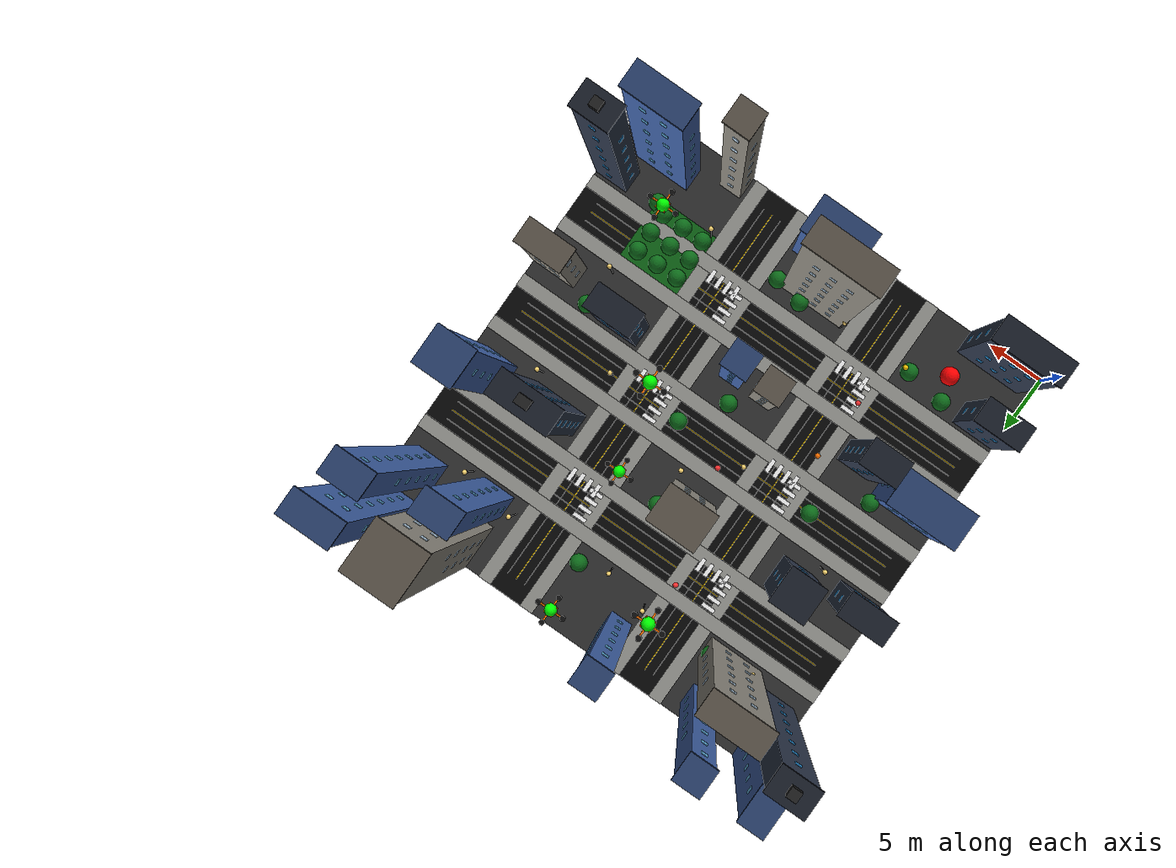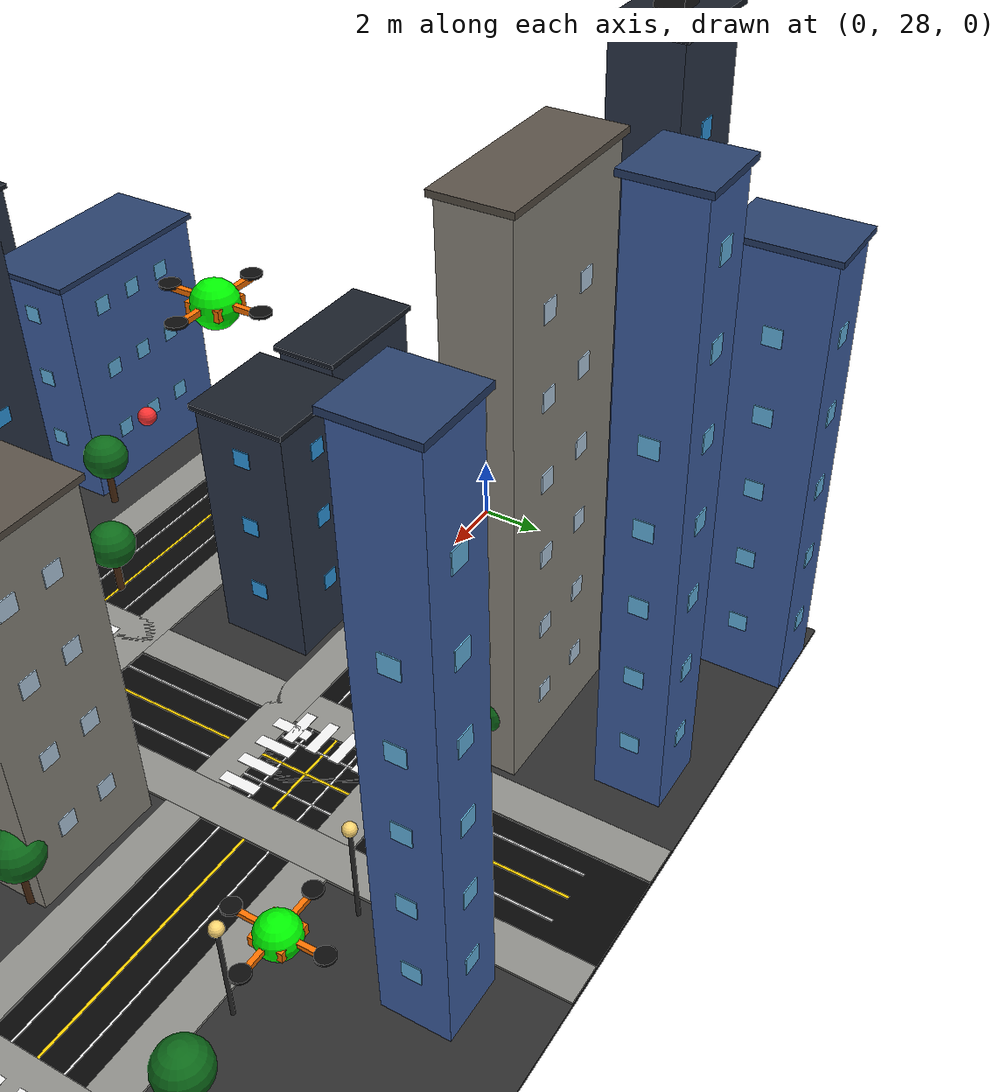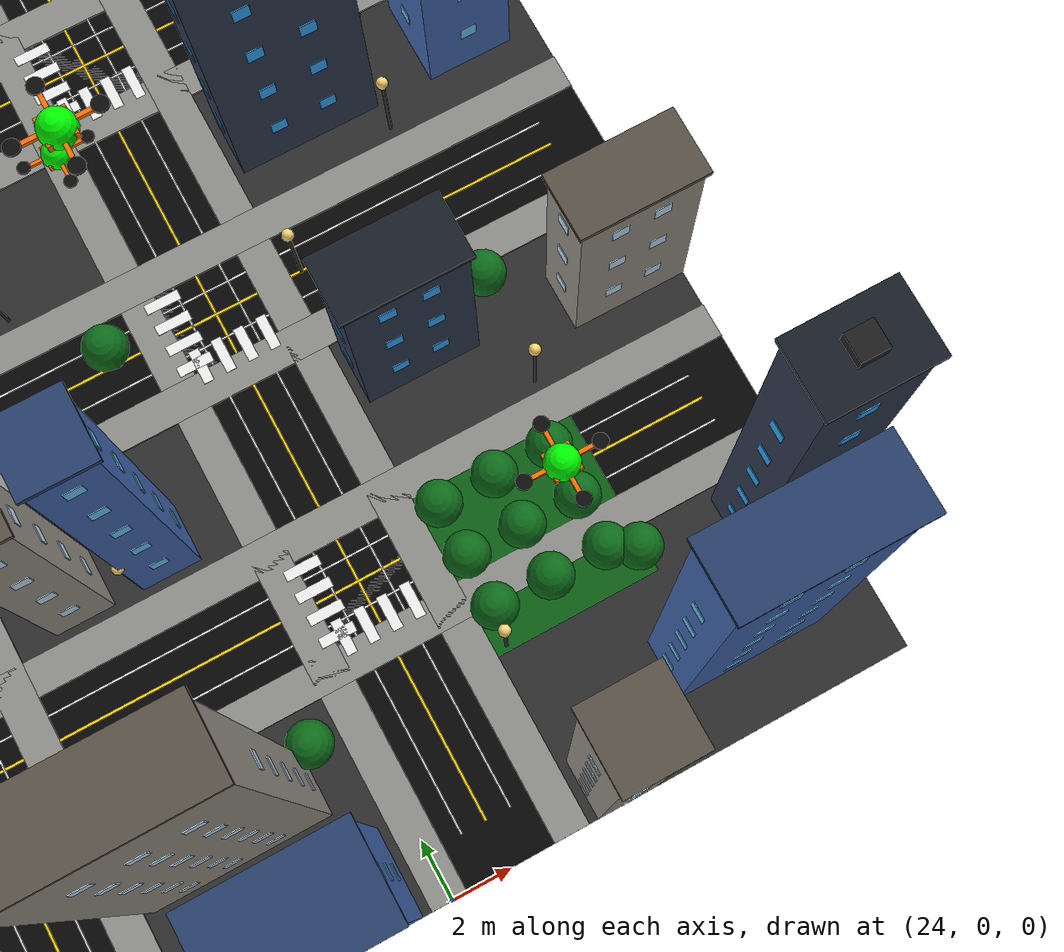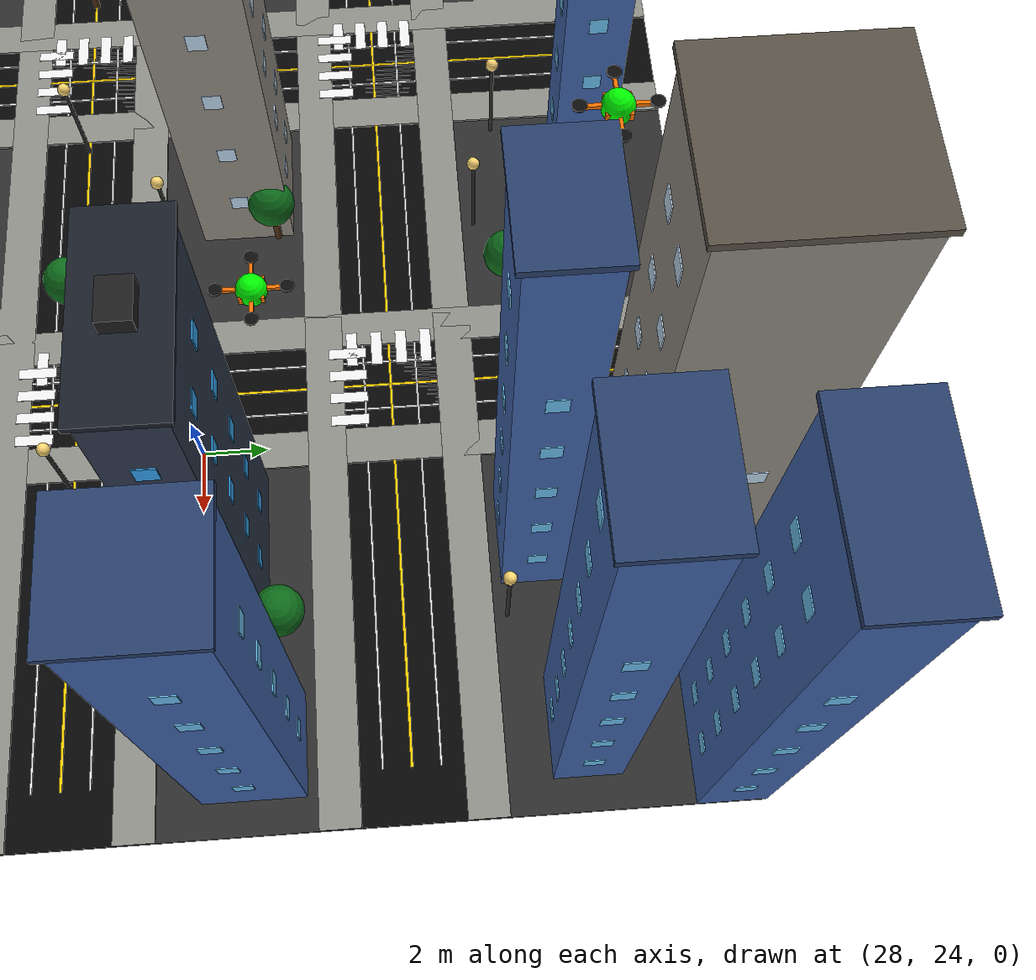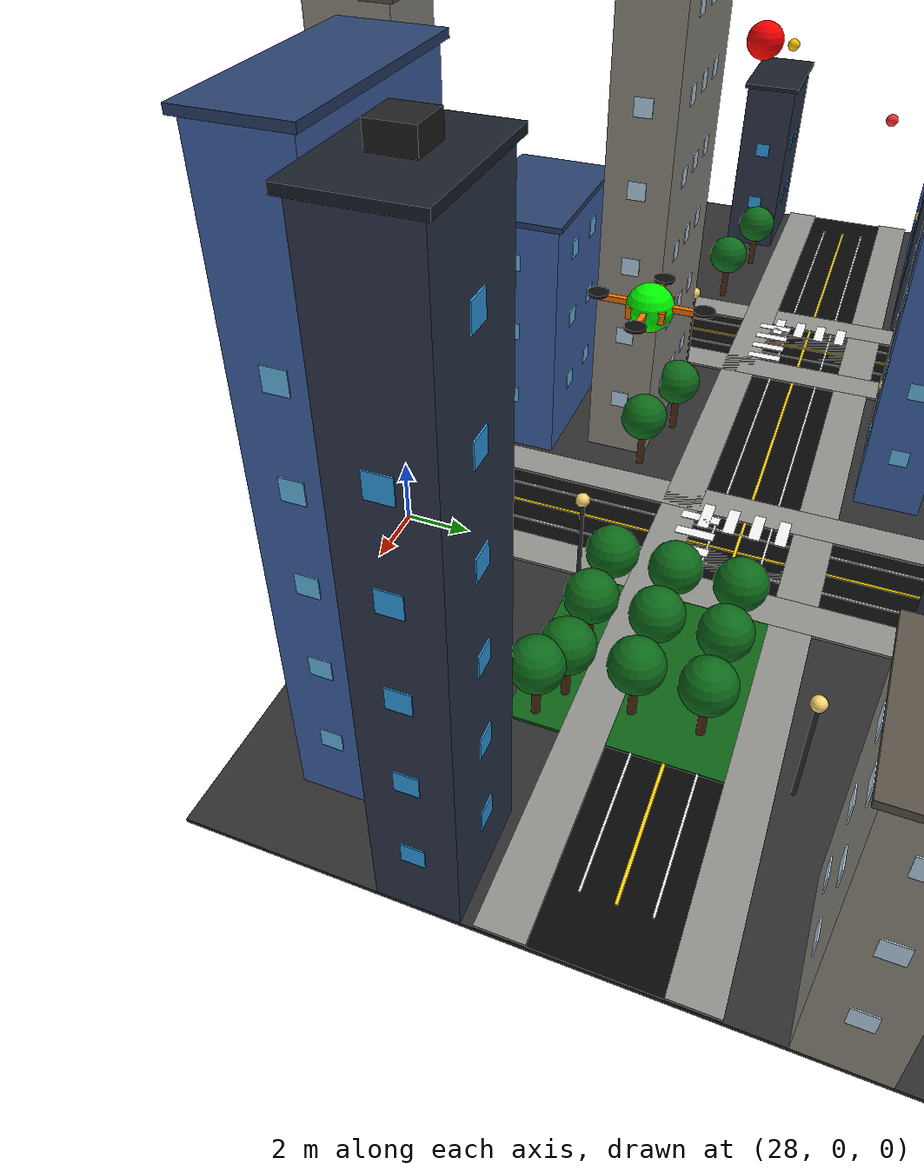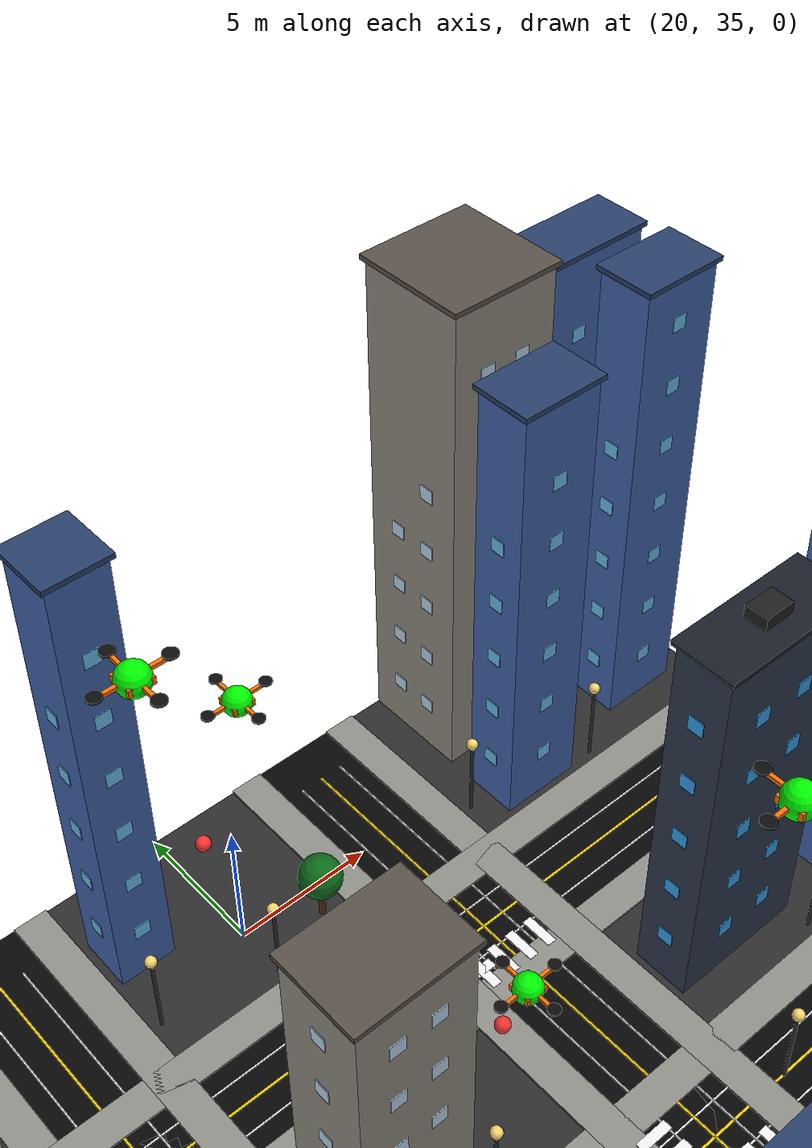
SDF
<?xml version="1.0" ?>
<sdf version="1.10">
  <world name="city_uav_demo">

    <plugin
      filename="gz-sim-physics-system"
      name="gz::sim::systems::Physics">
    </plugin>

    <plugin
      filename="gz-sim-scene-broadcaster-system"
      name="gz::sim::systems::SceneBroadcaster">
    </plugin>

    <plugin
      filename="gz-sim-user-commands-system"
      name="gz::sim::systems::UserCommands">
    </plugin>

    <light name="sun" type="directional">
      <cast_shadows>true</cast_shadows>
      <pose>0 0 85 0 0 0</pose>
      <diffuse>0.85 0.85 0.78 1</diffuse>
      <specular>0.25 0.25 0.25 1</specular>
      <direction>-0.45 0.15 -0.88</direction>
    </light>

    <model name="ground_plane">
      <static>true</static>
      <pose>20.0000 20.0000 -0.0500 0 0 0.0000</pose>
      <link name="link">
        <collision name="collision">
          <geometry>
            <box>
              <size>40.0000 40.0000 0.1000</size>
            </box>
          </geometry>
        </collision>
        <visual name="visual">
          <geometry>
            <box>
              <size>40.0000 40.0000 0.1000</size>
            </box>
          </geometry>

          <material>
            <ambient>0.18 0.18 0.18 1.0</ambient>
            <diffuse>0.18 0.18 0.18 1.0</diffuse>
          </material>

        </visual>
      </link>
    </model>

    <model name="road_0_surface">
      <static>true</static>
      <pose>20.0000 10.0000 0.0400 0 0 0.0000</pose>
      <link name="link">
        <collision name="collision">
          <geometry>
            <box>
              <size>40.0000 3.0000 0.0400</size>
            </box>
          </geometry>
        </collision>
        <visual name="visual">
          <geometry>
            <box>
              <size>40.0000 3.0000 0.0400</size>
            </box>
          </geometry>

          <material>
            <ambient>0.025 0.025 0.025 1.0</ambient>
            <diffuse>0.025 0.025 0.025 1.0</diffuse>
          </material>

        </visual>
      </link>
    </model>

    <model name="road_0_sidewalk_left">
      <static>true</static>
      <pose>20.0000 7.9000 0.0800 0 0 0.0000</pose>
      <link name="link">
        <visual name="visual">
          <geometry>
            <box>
              <size>40.0000 1.2000 0.0800</size>
            </box>
          </geometry>

          <material>
            <ambient>0.56 0.56 0.54 1.0</ambient>
            <diffuse>0.56 0.56 0.54 1.0</diffuse>
          </material>

        </visual>
      </link>
    </model>

    <model name="road_0_sidewalk_right">
      <static>true</static>
      <pose>20.0000 12.1000 0.0800 0 0 0.0000</pose>
      <link name="link">
        <visual name="visual">
          <geometry>
            <box>
              <size>40.0000 1.2000 0.0800</size>
            </box>
          </geometry>

          <material>
            <ambient>0.56 0.56 0.54 1.0</ambient>
            <diffuse>0.56 0.56 0.54 1.0</diffuse>
          </material>

        </visual>
      </link>
    </model>

    <model name="road_0_center_line">
      <static>true</static>
      <pose>20.0000 10.0000 0.0950 0 0 0.0000</pose>
      <link name="link">
        <visual name="visual">
          <geometry>
            <box>
              <size>36.8000 0.0800 0.0250</size>
            </box>
          </geometry>

          <material>
            <ambient>1.0 0.82 0.0 1.0</ambient>
            <diffuse>1.0 0.82 0.0 1.0</diffuse>
          </material>

        </visual>
      </link>
    </model>

    <model name="road_0_white_line_1">
      <static>true</static>
      <pose>20.0000 9.1600 0.0950 0 0 0.0000</pose>
      <link name="link">
        <visual name="visual">
          <geometry>
            <box>
              <size>36.8000 0.0550 0.0250</size>
            </box>
          </geometry>

          <material>
            <ambient>0.95 0.95 0.95 1.0</ambient>
            <diffuse>0.95 0.95 0.95 1.0</diffuse>
          </material>

        </visual>
      </link>
    </model>

    <model name="road_0_white_line_2">
      <static>true</static>
      <pose>20.0000 10.8400 0.0950 0 0 0.0000</pose>
      <link name="link">
        <visual name="visual">
          <geometry>
            <box>
              <size>36.8000 0.0550 0.0250</size>
            </box>
          </geometry>

          <material>
            <ambient>0.95 0.95 0.95 1.0</ambient>
            <diffuse>0.95 0.95 0.95 1.0</diffuse>
          </material>

        </visual>
      </link>
    </model>

    <model name="road_1_surface">
      <static>true</static>
      <pose>20.0000 20.0000 0.0400 0 0 0.0000</pose>
      <link name="link">
        <collision name="collision">
          <geometry>
            <box>
              <size>40.0000 3.0000 0.0400</size>
            </box>
          </geometry>
        </collision>
        <visual name="visual">
          <geometry>
            <box>
              <size>40.0000 3.0000 0.0400</size>
            </box>
          </geometry>

          <material>
            <ambient>0.025 0.025 0.025 1.0</ambient>
            <diffuse>0.025 0.025 0.025 1.0</diffuse>
          </material>

        </visual>
      </link>
    </model>

    <model name="road_1_sidewalk_left">
      <static>true</static>
      <pose>20.0000 17.9000 0.0800 0 0 0.0000</pose>
      <link name="link">
        <visual name="visual">
          <geometry>
            <box>
              <size>40.0000 1.2000 0.0800</size>
            </box>
          </geometry>

          <material>
            <ambient>0.56 0.56 0.54 1.0</ambient>
            <diffuse>0.56 0.56 0.54 1.0</diffuse>
          </material>

        </visual>
      </link>
    </model>

    <model name="road_1_sidewalk_right">
      <static>true</static>
      <pose>20.0000 22.1000 0.0800 0 0 0.0000</pose>
      <link name="link">
        <visual name="visual">
          <geometry>
            <box>
              <size>40.0000 1.2000 0.0800</size>
            </box>
          </geometry>

          <material>
            <ambient>0.56 0.56 0.54 1.0</ambient>
            <diffuse>0.56 0.56 0.54 1.0</diffuse>
          </material>

        </visual>
      </link>
    </model>

    <model name="road_1_center_line">
      <static>true</static>
      <pose>20.0000 20.0000 0.0950 0 0 0.0000</pose>
      <link name="link">
        <visual name="visual">
          <geometry>
            <box>
              <size>36.8000 0.0800 0.0250</size>
            </box>
          </geometry>

          <material>
            <ambient>1.0 0.82 0.0 1.0</ambient>
            <diffuse>1.0 0.82 0.0 1.0</diffuse>
          </material>

        </visual>
      </link>
    </model>

    <model name="road_1_white_line_1">
      <static>true</static>
      <pose>20.0000 19.1600 0.0950 0 0 0.0000</pose>
      <link name="link">
        <visual name="visual">
          <geometry>
            <box>
              <size>36.8000 0.0550 0.0250</size>
            </box>
          </geometry>

          <material>
            <ambient>0.95 0.95 0.95 1.0</ambient>
            <diffuse>0.95 0.95 0.95 1.0</diffuse>
          </material>

        </visual>
      </link>
    </model>

    <model name="road_1_white_line_2">
      <static>true</static>
      <pose>20.0000 20.8400 0.0950 0 0 0.0000</pose>
      <link name="link">
        <visual name="visual">
          <geometry>
            <box>
              <size>36.8000 0.0550 0.0250</size>
            </box>
          </geometry>

          <material>
            <ambient>0.95 0.95 0.95 1.0</ambient>
            <diffuse>0.95 0.95 0.95 1.0</diffuse>
          </material>

        </visual>
      </link>
    </model>

    <model name="road_2_surface">
      <static>true</static>
      <pose>20.0000 30.0000 0.0400 0 0 0.0000</pose>
      <link name="link">
        <collision name="collision">
          <geometry>
            <box>
              <size>40.0000 3.0000 0.0400</size>
            </box>
          </geometry>
        </collision>
        <visual name="visual">
          <geometry>
            <box>
              <size>40.0000 3.0000 0.0400</size>
            </box>
          </geometry>

          <material>
            <ambient>0.025 0.025 0.025 1.0</ambient>
            <diffuse>0.025 0.025 0.025 1.0</diffuse>
          </material>

        </visual>
      </link>
    </model>

    <model name="road_2_sidewalk_left">
      <static>true</static>
      <pose>20.0000 27.9000 0.0800 0 0 0.0000</pose>
      <link name="link">
        <visual name="visual">
          <geometry>
            <box>
              <size>40.0000 1.2000 0.0800</size>
            </box>
          </geometry>

          <material>
            <ambient>0.56 0.56 0.54 1.0</ambient>
            <diffuse>0.56 0.56 0.54 1.0</diffuse>
          </material>

        </visual>
      </link>
    </model>

    <model name="road_2_sidewalk_right">
      <static>true</static>
      <pose>20.0000 32.1000 0.0800 0 0 0.0000</pose>
      <link name="link">
        <visual name="visual">
          <geometry>
            <box>
              <size>40.0000 1.2000 0.0800</size>
            </box>
          </geometry>

          <material>
            <ambient>0.56 0.56 0.54 1.0</ambient>
            <diffuse>0.56 0.56 0.54 1.0</diffuse>
          </material>

        </visual>
      </link>
    </model>

    <model name="road_2_center_line">
      <static>true</static>
      <pose>20.0000 30.0000 0.0950 0 0 0.0000</pose>
      <link name="link">
        <visual name="visual">
          <geometry>
            <box>
              <size>36.8000 0.0800 0.0250</size>
            </box>
          </geometry>

          <material>
            <ambient>1.0 0.82 0.0 1.0</ambient>
            <diffuse>1.0 0.82 0.0 1.0</diffuse>
          </material>

        </visual>
      </link>
    </model>

    <model name="road_2_white_line_1">
      <static>true</static>
      <pose>20.0000 29.1600 0.0950 0 0 0.0000</pose>
      <link name="link">
        <visual name="visual">
          <geometry>
            <box>
              <size>36.8000 0.0550 0.0250</size>
            </box>
          </geometry>

          <material>
            <ambient>0.95 0.95 0.95 1.0</ambient>
            <diffuse>0.95 0.95 0.95 1.0</diffuse>
          </material>

        </visual>
      </link>
    </model>

    <model name="road_2_white_line_2">
      <static>true</static>
      <pose>20.0000 30.8400 0.0950 0 0 0.0000</pose>
      <link name="link">
        <visual name="visual">
          <geometry>
            <box>
              <size>36.8000 0.0550 0.0250</size>
            </box>
          </geometry>

          <material>
            <ambient>0.95 0.95 0.95 1.0</ambient>
            <diffuse>0.95 0.95 0.95 1.0</diffuse>
          </material>

        </visual>
      </link>
    </model>

    <model name="road_3_surface">
      <static>true</static>
      <pose>13.0000 20.0000 0.0400 0 0 0.0000</pose>
      <link name="link">
        <collision name="collision">
          <geometry>
            <box>
              <size>3.0000 40.0000 0.0400</size>
            </box>
          </geometry>
        </collision>
        <visual name="visual">
          <geometry>
            <box>
              <size>3.0000 40.0000 0.0400</size>
            </box>
          </geometry>

          <material>
            <ambient>0.025 0.025 0.025 1.0</ambient>
            <diffuse>0.025 0.025 0.025 1.0</diffuse>
          </material>

        </visual>
      </link>
    </model>

    <model name="road_3_sidewalk_left">
      <static>true</static>
      <pose>10.9000 20.0000 0.0800 0 0 0.0000</pose>
      <link name="link">
        <visual name="visual">
          <geometry>
            <box>
              <size>1.2000 40.0000 0.0800</size>
            </box>
          </geometry>

          <material>
            <ambient>0.56 0.56 0.54 1.0</ambient>
            <diffuse>0.56 0.56 0.54 1.0</diffuse>
          </material>

        </visual>
      </link>
    </model>

    <model name="road_3_sidewalk_right">
      <static>true</static>
      <pose>15.1000 20.0000 0.0800 0 0 0.0000</pose>
      <link name="link">
        <visual name="visual">
          <geometry>
            <box>
              <size>1.2000 40.0000 0.0800</size>
            </box>
          </geometry>

          <material>
            <ambient>0.56 0.56 0.54 1.0</ambient>
            <diffuse>0.56 0.56 0.54 1.0</diffuse>
          </material>

        </visual>
      </link>
    </model>

    <model name="road_3_center_line">
      <static>true</static>
      <pose>13.0000 20.0000 0.0950 0 0 0.0000</pose>
      <link name="link">
        <visual name="visual">
          <geometry>
            <box>
              <size>0.0800 36.8000 0.0250</size>
            </box>
          </geometry>

          <material>
            <ambient>1.0 0.82 0.0 1.0</ambient>
            <diffuse>1.0 0.82 0.0 1.0</diffuse>
          </material>

        </visual>
      </link>
    </model>

    <model name="road_3_white_line_1">
      <static>true</static>
      <pose>12.1600 20.0000 0.0950 0 0 0.0000</pose>
      <link name="link">
        <visual name="visual">
          <geometry>
            <box>
              <size>0.0550 36.8000 0.0250</size>
            </box>
          </geometry>

          <material>
            <ambient>0.95 0.95 0.95 1.0</ambient>
            <diffuse>0.95 0.95 0.95 1.0</diffuse>
          </material>

        </visual>
      </link>
    </model>

    <model name="road_3_white_line_2">
      <static>true</static>
      <pose>13.8400 20.0000 0.0950 0 0 0.0000</pose>
      <link name="link">
        <visual name="visual">
          <geometry>
            <box>
              <size>0.0550 36.8000 0.0250</size>
            </box>
          </geometry>

          <material>
            <ambient>0.95 0.95 0.95 1.0</ambient>
            <diffuse>0.95 0.95 0.95 1.0</diffuse>
          </material>

        </visual>
      </link>
    </model>

    <model name="road_4_surface">
      <static>true</static>
      <pose>26.0000 20.0000 0.0400 0 0 0.0000</pose>
      <link name="link">
        <collision name="collision">
          <geometry>
            <box>
              <size>3.0000 40.0000 0.0400</size>
            </box>
          </geometry>
        </collision>
        <visual name="visual">
          <geometry>
            <box>
              <size>3.0000 40.0000 0.0400</size>
            </box>
          </geometry>

          <material>
            <ambient>0.025 0.025 0.025 1.0</ambient>
            <diffuse>0.025 0.025 0.025 1.0</diffuse>
          </material>

        </visual>
      </link>
    </model>

    <model name="road_4_sidewalk_left">
      <static>true</static>
      <pose>23.9000 20.0000 0.0800 0 0 0.0000</pose>
      <link name="link">
        <visual name="visual">
          <geometry>
            <box>
              <size>1.2000 40.0000 0.0800</size>
            </box>
          </geometry>

          <material>
            <ambient>0.56 0.56 0.54 1.0</ambient>
            <diffuse>0.56 0.56 0.54 1.0</diffuse>
          </material>

        </visual>
      </link>
    </model>

    <model name="road_4_sidewalk_right">
      <static>true</static>
      <pose>28.1000 20.0000 0.0800 0 0 0.0000</pose>
      <link name="link">
        <visual name="visual">
          <geometry>
            <box>
              <size>1.2000 40.0000 0.0800</size>
            </box>
          </geometry>

          <material>
            <ambient>0.56 0.56 0.54 1.0</ambient>
            <diffuse>0.56 0.56 0.54 1.0</diffuse>
          </material>

        </visual>
      </link>
    </model>

    <model name="road_4_center_line">
      <static>true</static>
      <pose>26.0000 20.0000 0.0950 0 0 0.0000</pose>
      <link name="link">
        <visual name="visual">
          <geometry>
            <box>
              <size>0.0800 36.8000 0.0250</size>
            </box>
          </geometry>

          <material>
            <ambient>1.0 0.82 0.0 1.0</ambient>
            <diffuse>1.0 0.82 0.0 1.0</diffuse>
          </material>

        </visual>
      </link>
    </model>

    <model name="road_4_white_line_1">
      <static>true</static>
      <pose>25.1600 20.0000 0.0950 0 0 0.0000</pose>
      <link name="link">
        <visual name="visual">
          <geometry>
            <box>
              <size>0.0550 36.8000 0.0250</size>
            </box>
          </geometry>

          <material>
            <ambient>0.95 0.95 0.95 1.0</ambient>
            <diffuse>0.95 0.95 0.95 1.0</diffuse>
          </material>

        </visual>
      </link>
    </model>

    <model name="road_4_white_line_2">
      <static>true</static>
      <pose>26.8400 20.0000 0.0950 0 0 0.0000</pose>
      <link name="link">
        <visual name="visual">
          <geometry>
            <box>
              <size>0.0550 36.8000 0.0250</size>
            </box>
          </geometry>

          <material>
            <ambient>0.95 0.95 0.95 1.0</ambient>
            <diffuse>0.95 0.95 0.95 1.0</diffuse>
          </material>

        </visual>
      </link>
    </model>

    <model name="crosswalk_0_h_0">
      <static>true</static>
      <pose>11.8000 8.6500 0.1200 0 0 0.0000</pose>
      <link name="link">
        <visual name="visual">
          <geometry>
            <box>
              <size>0.3500 1.2000 0.0250</size>
            </box>
          </geometry>

          <material>
            <ambient>0.95 0.95 0.95 1.0</ambient>
            <diffuse>0.95 0.95 0.95 1.0</diffuse>
          </material>

        </visual>
      </link>
    </model>

    <model name="crosswalk_0_v_0">
      <static>true</static>
      <pose>11.6500 8.8000 0.1200 0 0 0.0000</pose>
      <link name="link">
        <visual name="visual">
          <geometry>
            <box>
              <size>1.2000 0.3500 0.0250</size>
            </box>
          </geometry>

          <material>
            <ambient>0.95 0.95 0.95 1.0</ambient>
            <diffuse>0.95 0.95 0.95 1.0</diffuse>
          </material>

        </visual>
      </link>
    </model>

    <model name="crosswalk_0_h_1">
      <static>true</static>
      <pose>12.6000 8.6500 0.1200 0 0 0.0000</pose>
      <link name="link">
        <visual name="visual">
          <geometry>
            <box>
              <size>0.3500 1.2000 0.0250</size>
            </box>
          </geometry>

          <material>
            <ambient>0.95 0.95 0.95 1.0</ambient>
            <diffuse>0.95 0.95 0.95 1.0</diffuse>
          </material>

        </visual>
      </link>
    </model>

    <model name="crosswalk_0_v_1">
      <static>true</static>
      <pose>11.6500 9.6000 0.1200 0 0 0.0000</pose>
      <link name="link">
        <visual name="visual">
          <geometry>
            <box>
              <size>1.2000 0.3500 0.0250</size>
            </box>
          </geometry>

          <material>
            <ambient>0.95 0.95 0.95 1.0</ambient>
            <diffuse>0.95 0.95 0.95 1.0</diffuse>
          </material>

        </visual>
      </link>
    </model>

    <model name="crosswalk_0_h_2">
      <static>true</static>
      <pose>13.4000 8.6500 0.1200 0 0 0.0000</pose>
      <link name="link">
        <visual name="visual">
          <geometry>
            <box>
              <size>0.3500 1.2000 0.0250</size>
            </box>
          </geometry>

          <material>
            <ambient>0.95 0.95 0.95 1.0</ambient>
            <diffuse>0.95 0.95 0.95 1.0</diffuse>
          </material>

        </visual>
      </link>
    </model>

    <model name="crosswalk_0_v_2">
      <static>true</static>
      <pose>11.6500 10.4000 0.1200 0 0 0.0000</pose>
      <link name="link">
        <visual name="visual">
          <geometry>
            <box>
              <size>1.2000 0.3500 0.0250</size>
            </box>
          </geometry>

          <material>
            <ambient>0.95 0.95 0.95 1.0</ambient>
            <diffuse>0.95 0.95 0.95 1.0</diffuse>
          </material>

        </visual>
      </link>
    </model>

    <model name="crosswalk_0_h_3">
      <static>true</static>
      <pose>14.2000 8.6500 0.1200 0 0 0.0000</pose>
      <link name="link">
        <visual name="visual">
          <geometry>
            <box>
              <size>0.3500 1.2000 0.0250</size>
            </box>
          </geometry>

          <material>
            <ambient>0.95 0.95 0.95 1.0</ambient>
            <diffuse>0.95 0.95 0.95 1.0</diffuse>
          </material>

        </visual>
      </link>
    </model>

    <model name="crosswalk_0_v_3">
      <static>true</static>
      <pose>11.6500 11.2000 0.1200 0 0 0.0000</pose>
      <link name="link">
        <visual name="visual">
          <geometry>
            <box>
              <size>1.2000 0.3500 0.0250</size>
            </box>
          </geometry>

          <material>
            <ambient>0.95 0.95 0.95 1.0</ambient>
            <diffuse>0.95 0.95 0.95 1.0</diffuse>
          </material>

        </visual>
      </link>
    </model>

    <model name="crosswalk_1_h_0">
      <static>true</static>
      <pose>24.8000 8.6500 0.1200 0 0 0.0000</pose>
      <link name="link">
        <visual name="visual">
          <geometry>
            <box>
              <size>0.3500 1.2000 0.0250</size>
            </box>
          </geometry>

          <material>
            <ambient>0.95 0.95 0.95 1.0</ambient>
            <diffuse>0.95 0.95 0.95 1.0</diffuse>
          </material>

        </visual>
      </link>
    </model>

    <model name="crosswalk_1_v_0">
      <static>true</static>
      <pose>24.6500 8.8000 0.1200 0 0 0.0000</pose>
      <link name="link">
        <visual name="visual">
          <geometry>
            <box>
              <size>1.2000 0.3500 0.0250</size>
            </box>
          </geometry>

          <material>
            <ambient>0.95 0.95 0.95 1.0</ambient>
            <diffuse>0.95 0.95 0.95 1.0</diffuse>
          </material>

        </visual>
      </link>
    </model>

    <model name="crosswalk_1_h_1">
      <static>true</static>
      <pose>25.6000 8.6500 0.1200 0 0 0.0000</pose>
      <link name="link">
        <visual name="visual">
          <geometry>
            <box>
              <size>0.3500 1.2000 0.0250</size>
            </box>
          </geometry>

          <material>
            <ambient>0.95 0.95 0.95 1.0</ambient>
            <diffuse>0.95 0.95 0.95 1.0</diffuse>
          </material>

        </visual>
      </link>
    </model>

    <model name="crosswalk_1_v_1">
      <static>true</static>
      <pose>24.6500 9.6000 0.1200 0 0 0.0000</pose>
      <link name="link">
        <visual name="visual">
          <geometry>
            <box>
              <size>1.2000 0.3500 0.0250</size>
            </box>
          </geometry>

          <material>
            <ambient>0.95 0.95 0.95 1.0</ambient>
            <diffuse>0.95 0.95 0.95 1.0</diffuse>
          </material>

        </visual>
      </link>
    </model>

    <model name="crosswalk_1_h_2">
      <static>true</static>
      <pose>26.4000 8.6500 0.1200 0 0 0.0000</pose>
      <link name="link">
        <visual name="visual">
          <geometry>
            <box>
              <size>0.3500 1.2000 0.0250</size>
            </box>
          </geometry>

          <material>
            <ambient>0.95 0.95 0.95 1.0</ambient>
            <diffuse>0.95 0.95 0.95 1.0</diffuse>
          </material>

        </visual>
      </link>
    </model>

    <model name="crosswalk_1_v_2">
      <static>true</static>
      <pose>24.6500 10.4000 0.1200 0 0 0.0000</pose>
      <link name="link">
        <visual name="visual">
          <geometry>
            <box>
              <size>1.2000 0.3500 0.0250</size>
            </box>
          </geometry>

          <material>
            <ambient>0.95 0.95 0.95 1.0</ambient>
            <diffuse>0.95 0.95 0.95 1.0</diffuse>
          </material>

        </visual>
      </link>
    </model>

    <model name="crosswalk_1_h_3">
      <static>true</static>
      <pose>27.2000 8.6500 0.1200 0 0 0.0000</pose>
      <link name="link">
        <visual name="visual">
          <geometry>
            <box>
              <size>0.3500 1.2000 0.0250</size>
            </box>
          </geometry>

          <material>
            <ambient>0.95 0.95 0.95 1.0</ambient>
            <diffuse>0.95 0.95 0.95 1.0</diffuse>
          </material>

        </visual>
      </link>
    </model>

    <model name="crosswalk_1_v_3">
      <static>true</static>
      <pose>24.6500 11.2000 0.1200 0 0 0.0000</pose>
      <link name="link">
        <visual name="visual">
          <geometry>
            <box>
              <size>1.2000 0.3500 0.0250</size>
            </box>
          </geometry>

          <material>
            <ambient>0.95 0.95 0.95 1.0</ambient>
            <diffuse>0.95 0.95 0.95 1.0</diffuse>
          </material>

        </visual>
      </link>
    </model>

    <model name="crosswalk_2_h_0">
      <static>true</static>
      <pose>11.8000 18.6500 0.1200 0 0 0.0000</pose>
      <link name="link">
        <visual name="visual">
          <geometry>
            <box>
              <size>0.3500 1.2000 0.0250</size>
            </box>
          </geometry>

          <material>
            <ambient>0.95 0.95 0.95 1.0</ambient>
            <diffuse>0.95 0.95 0.95 1.0</diffuse>
          </material>

        </visual>
      </link>
    </model>

    <model name="crosswalk_2_v_0">
      <static>true</static>
      <pose>11.6500 18.8000 0.1200 0 0 0.0000</pose>
      <link name="link">
        <visual name="visual">
          <geometry>
            <box>
              <size>1.2000 0.3500 0.0250</size>
            </box>
          </geometry>

          <material>
            <ambient>0.95 0.95 0.95 1.0</ambient>
            <diffuse>0.95 0.95 0.95 1.0</diffuse>
          </material>

        </visual>
      </link>
    </model>

    <model name="crosswalk_2_h_1">
      <static>true</static>
      <pose>12.6000 18.6500 0.1200 0 0 0.0000</pose>
      <link name="link">
        <visual name="visual">
          <geometry>
            <box>
              <size>0.3500 1.2000 0.0250</size>
            </box>
          </geometry>

          <material>
            <ambient>0.95 0.95 0.95 1.0</ambient>
            <diffuse>0.95 0.95 0.95 1.0</diffuse>
          </material>

        </visual>
      </link>
    </model>

    <model name="crosswalk_2_v_1">
      <static>true</static>
      <pose>11.6500 19.6000 0.1200 0 0 0.0000</pose>
      <link name="link">
        <visual name="visual">
          <geometry>
            <box>
              <size>1.2000 0.3500 0.0250</size>
            </box>
          </geometry>

          <material>
            <ambient>0.95 0.95 0.95 1.0</ambient>
            <diffuse>0.95 0.95 0.95 1.0</diffuse>
          </material>

        </visual>
      </link>
    </model>

    <model name="crosswalk_2_h_2">
      <static>true</static>
      <pose>13.4000 18.6500 0.1200 0 0 0.0000</pose>
      <link name="link">
        <visual name="visual">
          <geometry>
            <box>
              <size>0.3500 1.2000 0.0250</size>
            </box>
          </geometry>

          <material>
            <ambient>0.95 0.95 0.95 1.0</ambient>
            <diffuse>0.95 0.95 0.95 1.0</diffuse>
          </material>

        </visual>
      </link>
    </model>

    <model name="crosswalk_2_v_2">
      <static>true</static>
      <pose>11.6500 20.4000 0.1200 0 0 0.0000</pose>
      <link name="link">
        <visual name="visual">
          <geometry>
            <box>
              <size>1.2000 0.3500 0.0250</size>
            </box>
          </geometry>

          <material>
            <ambient>0.95 0.95 0.95 1.0</ambient>
            <diffuse>0.95 0.95 0.95 1.0</diffuse>
          </material>

        </visual>
      </link>
    </model>

    <model name="crosswalk_2_h_3">
      <static>true</static>
      <pose>14.2000 18.6500 0.1200 0 0 0.0000</pose>
      <link name="link">
        <visual name="visual">
          <geometry>
            <box>
              <size>0.3500 1.2000 0.0250</size>
            </box>
          </geometry>

          <material>
            <ambient>0.95 0.95 0.95 1.0</ambient>
            <diffuse>0.95 0.95 0.95 1.0</diffuse>
          </material>

        </visual>
      </link>
    </model>

    <model name="crosswalk_2_v_3">
      <static>true</static>
      <pose>11.6500 21.2000 0.1200 0 0 0.0000</pose>
      <link name="link">
        <visual name="visual">
          <geometry>
            <box>
              <size>1.2000 0.3500 0.0250</size>
            </box>
          </geometry>

          <material>
            <ambient>0.95 0.95 0.95 1.0</ambient>
            <diffuse>0.95 0.95 0.95 1.0</diffuse>
          </material>

        </visual>
      </link>
    </model>

    <model name="crosswalk_3_h_0">
      <static>true</static>
      <pose>24.8000 18.6500 0.1200 0 0 0.0000</pose>
      <link name="link">
        <visual name="visual">
          <geometry>
            <box>
              <size>0.3500 1.2000 0.0250</size>
            </box>
          </geometry>

          <material>
            <ambient>0.95 0.95 0.95 1.0</ambient>
            <diffuse>0.95 0.95 0.95 1.0</diffuse>
          </material>

        </visual>
      </link>
    </model>

    <model name="crosswalk_3_v_0">
      <static>true</static>
      <pose>24.6500 18.8000 0.1200 0 0 0.0000</pose>
      <link name="link">
        <visual name="visual">
          <geometry>
            <box>
              <size>1.2000 0.3500 0.0250</size>
            </box>
          </geometry>

          <material>
            <ambient>0.95 0.95 0.95 1.0</ambient>
            <diffuse>0.95 0.95 0.95 1.0</diffuse>
          </material>

        </visual>
      </link>
    </model>

    <model name="crosswalk_3_h_1">
      <static>true</static>
      <pose>25.6000 18.6500 0.1200 0 0 0.0000</pose>
      <link name="link">
        <visual name="visual">
          <geometry>
            <box>
              <size>0.3500 1.2000 0.0250</size>
            </box>
          </geometry>

          <material>
            <ambient>0.95 0.95 0.95 1.0</ambient>
            <diffuse>0.95 0.95 0.95 1.0</diffuse>
          </material>

        </visual>
      </link>
    </model>

    <model name="crosswalk_3_v_1">
      <static>true</static>
      <pose>24.6500 19.6000 0.1200 0 0 0.0000</pose>
      <link name="link">
        <visual name="visual">
          <geometry>
            <box>
              <size>1.2000 0.3500 0.0250</size>
            </box>
          </geometry>

          <material>
            <ambient>0.95 0.95 0.95 1.0</ambient>
            <diffuse>0.95 0.95 0.95 1.0</diffuse>
          </material>

        </visual>
      </link>
    </model>

    <model name="crosswalk_3_h_2">
      <static>true</static>
      <pose>26.4000 18.6500 0.1200 0 0 0.0000</pose>
      <link name="link">
        <visual name="visual">
          <geometry>
            <box>
              <size>0.3500 1.2000 0.0250</size>
            </box>
          </geometry>

          <material>
            <ambient>0.95 0.95 0.95 1.0</ambient>
            <diffuse>0.95 0.95 0.95 1.0</diffuse>
          </material>

        </visual>
      </link>
    </model>

    <model name="crosswalk_3_v_2">
      <static>true</static>
      <pose>24.6500 20.4000 0.1200 0 0 0.0000</pose>
      <link name="link">
        <visual name="visual">
          <geometry>
            <box>
              <size>1.2000 0.3500 0.0250</size>
            </box>
          </geometry>

          <material>
            <ambient>0.95 0.95 0.95 1.0</ambient>
            <diffuse>0.95 0.95 0.95 1.0</diffuse>
          </material>

        </visual>
      </link>
    </model>

    <model name="crosswalk_3_h_3">
      <static>true</static>
      <pose>27.2000 18.6500 0.1200 0 0 0.0000</pose>
      <link name="link">
        <visual name="visual">
          <geometry>
            <box>
              <size>0.3500 1.2000 0.0250</size>
            </box>
          </geometry>

          <material>
            <ambient>0.95 0.95 0.95 1.0</ambient>
            <diffuse>0.95 0.95 0.95 1.0</diffuse>
          </material>

        </visual>
      </link>
    </model>

    <model name="crosswalk_3_v_3">
      <static>true</static>
      <pose>24.6500 21.2000 0.1200 0 0 0.0000</pose>
      <link name="link">
        <visual name="visual">
          <geometry>
            <box>
              <size>1.2000 0.3500 0.0250</size>
            </box>
          </geometry>

          <material>
            <ambient>0.95 0.95 0.95 1.0</ambient>
            <diffuse>0.95 0.95 0.95 1.0</diffuse>
          </material>

        </visual>
      </link>
    </model>

    <model name="crosswalk_4_h_0">
      <static>true</static>
      <pose>11.8000 28.6500 0.1200 0 0 0.0000</pose>
      <link name="link">
        <visual name="visual">
          <geometry>
            <box>
              <size>0.3500 1.2000 0.0250</size>
            </box>
          </geometry>

          <material>
            <ambient>0.95 0.95 0.95 1.0</ambient>
            <diffuse>0.95 0.95 0.95 1.0</diffuse>
          </material>

        </visual>
      </link>
    </model>

    <model name="crosswalk_4_v_0">
      <static>true</static>
      <pose>11.6500 28.8000 0.1200 0 0 0.0000</pose>
      <link name="link">
        <visual name="visual">
          <geometry>
            <box>
              <size>1.2000 0.3500 0.0250</size>
            </box>
          </geometry>

          <material>
            <ambient>0.95 0.95 0.95 1.0</ambient>
            <diffuse>0.95 0.95 0.95 1.0</diffuse>
          </material>

        </visual>
      </link>
    </model>

    <model name="crosswalk_4_h_1">
      <static>true</static>
      <pose>12.6000 28.6500 0.1200 0 0 0.0000</pose>
      <link name="link">
        <visual name="visual">
          <geometry>
            <box>
              <size>0.3500 1.2000 0.0250</size>
            </box>
          </geometry>

          <material>
            <ambient>0.95 0.95 0.95 1.0</ambient>
            <diffuse>0.95 0.95 0.95 1.0</diffuse>
          </material>

        </visual>
      </link>
    </model>

    <model name="crosswalk_4_v_1">
      <static>true</static>
      <pose>11.6500 29.6000 0.1200 0 0 0.0000</pose>
      <link name="link">
        <visual name="visual">
          <geometry>
            <box>
              <size>1.2000 0.3500 0.0250</size>
            </box>
          </geometry>

          <material>
            <ambient>0.95 0.95 0.95 1.0</ambient>
            <diffuse>0.95 0.95 0.95 1.0</diffuse>
          </material>

        </visual>
      </link>
    </model>

    <model name="crosswalk_4_h_2">
      <static>true</static>
      <pose>13.4000 28.6500 0.1200 0 0 0.0000</pose>
      <link name="link">
        <visual name="visual">
          <geometry>
            <box>
              <size>0.3500 1.2000 0.0250</size>
            </box>
          </geometry>

          <material>
            <ambient>0.95 0.95 0.95 1.0</ambient>
            <diffuse>0.95 0.95 0.95 1.0</diffuse>
          </material>

        </visual>
      </link>
    </model>

    <model name="crosswalk_4_v_2">
      <static>true</static>
      <pose>11.6500 30.4000 0.1200 0 0 0.0000</pose>
      <link name="link">
        <visual name="visual">
          <geometry>
            <box>
              <size>1.2000 0.3500 0.0250</size>
            </box>
          </geometry>

          <material>
            <ambient>0.95 0.95 0.95 1.0</ambient>
            <diffuse>0.95 0.95 0.95 1.0</diffuse>
          </material>

        </visual>
      </link>
    </model>

    <model name="crosswalk_4_h_3">
      <static>true</static>
      <pose>14.2000 28.6500 0.1200 0 0 0.0000</pose>
      <link name="link">
        <visual name="visual">
          <geometry>
            <box>
              <size>0.3500 1.2000 0.0250</size>
            </box>
          </geometry>

          <material>
            <ambient>0.95 0.95 0.95 1.0</ambient>
            <diffuse>0.95 0.95 0.95 1.0</diffuse>
          </material>

        </visual>
      </link>
    </model>

    <model name="crosswalk_4_v_3">
      <static>true</static>
      <pose>11.6500 31.2000 0.1200 0 0 0.0000</pose>
      <link name="link">
        <visual name="visual">
          <geometry>
            <box>
              <size>1.2000 0.3500 0.0250</size>
            </box>
          </geometry>

          <material>
            <ambient>0.95 0.95 0.95 1.0</ambient>
            <diffuse>0.95 0.95 0.95 1.0</diffuse>
          </material>

        </visual>
      </link>
    </model>

    <model name="crosswalk_5_h_0">
      <static>true</static>
      <pose>24.8000 28.6500 0.1200 0 0 0.0000</pose>
      <link name="link">
        <visual name="visual">
          <geometry>
            <box>
              <size>0.3500 1.2000 0.0250</size>
            </box>
          </geometry>

          <material>
            <ambient>0.95 0.95 0.95 1.0</ambient>
            <diffuse>0.95 0.95 0.95 1.0</diffuse>
          </material>

        </visual>
      </link>
    </model>

    <model name="crosswalk_5_v_0">
      <static>true</static>
      <pose>24.6500 28.8000 0.1200 0 0 0.0000</pose>
      <link name="link">
        <visual name="visual">
          <geometry>
            <box>
              <size>1.2000 0.3500 0.0250</size>
            </box>
          </geometry>

          <material>
            <ambient>0.95 0.95 0.95 1.0</ambient>
            <diffuse>0.95 0.95 0.95 1.0</diffuse>
          </material>

        </visual>
      </link>
    </model>

    <model name="crosswalk_5_h_1">
      <static>true</static>
      <pose>25.6000 28.6500 0.1200 0 0 0.0000</pose>
      <link name="link">
        <visual name="visual">
          <geometry>
            <box>
              <size>0.3500 1.2000 0.0250</size>
            </box>
          </geometry>

          <material>
            <ambient>0.95 0.95 0.95 1.0</ambient>
            <diffuse>0.95 0.95 0.95 1.0</diffuse>
          </material>

        </visual>
      </link>
    </model>

    <model name="crosswalk_5_v_1">
      <static>true</static>
      <pose>24.6500 29.6000 0.1200 0 0 0.0000</pose>
      <link name="link">
        <visual name="visual">
          <geometry>
            <box>
              <size>1.2000 0.3500 0.0250</size>
            </box>
          </geometry>

          <material>
            <ambient>0.95 0.95 0.95 1.0</ambient>
            <diffuse>0.95 0.95 0.95 1.0</diffuse>
          </material>

        </visual>
      </link>
    </model>

    <model name="crosswalk_5_h_2">
      <static>true</static>
      <pose>26.4000 28.6500 0.1200 0 0 0.0000</pose>
      <link name="link">
        <visual name="visual">
          <geometry>
            <box>
              <size>0.3500 1.2000 0.0250</size>
            </box>
          </geometry>

          <material>
            <ambient>0.95 0.95 0.95 1.0</ambient>
            <diffuse>0.95 0.95 0.95 1.0</diffuse>
          </material>

        </visual>
      </link>
    </model>

    <model name="crosswalk_5_v_2">
      <static>true</static>
      <pose>24.6500 30.4000 0.1200 0 0 0.0000</pose>
      <link name="link">
        <visual name="visual">
          <geometry>
            <box>
              <size>1.2000 0.3500 0.0250</size>
            </box>
          </geometry>

          <material>
            <ambient>0.95 0.95 0.95 1.0</ambient>
            <diffuse>0.95 0.95 0.95 1.0</diffuse>
          </material>

        </visual>
      </link>
    </model>

    <model name="crosswalk_5_h_3">
      <static>true</static>
      <pose>27.2000 28.6500 0.1200 0 0 0.0000</pose>
      <link name="link">
        <visual name="visual">
          <geometry>
            <box>
              <size>0.3500 1.2000 0.0250</size>
            </box>
          </geometry>

          <material>
            <ambient>0.95 0.95 0.95 1.0</ambient>
            <diffuse>0.95 0.95 0.95 1.0</diffuse>
          </material>

        </visual>
      </link>
    </model>

    <model name="crosswalk_5_v_3">
      <static>true</static>
      <pose>24.6500 31.2000 0.1200 0 0 0.0000</pose>
      <link name="link">
        <visual name="visual">
          <geometry>
            <box>
              <size>1.2000 0.3500 0.0250</size>
            </box>
          </geometry>

          <material>
            <ambient>0.95 0.95 0.95 1.0</ambient>
            <diffuse>0.95 0.95 0.95 1.0</diffuse>
          </material>

        </visual>
      </link>
    </model>

    <model name="building_0_body">
      <static>true</static>
      <pose>38.0000 15.0000 4.0000 0 0 0.0000</pose>
      <link name="link">
        <collision name="collision">
          <geometry>
            <box>
              <size>4.0000 2.0000 8.0000</size>
            </box>
          </geometry>
        </collision>
        <visual name="visual">
          <geometry>
            <box>
              <size>4.0000 2.0000 8.0000</size>
            </box>
          </geometry>

          <material>
            <ambient>0.58 0.56 0.52 1.0</ambient>
            <diffuse>0.58 0.56 0.52 1.0</diffuse>
          </material>

        </visual>
      </link>
    </model>

    <model name="building_0_roof">
      <static>true</static>
      <pose>38.0000 15.0000 8.0900 0 0 0.0000</pose>
      <link name="link">
        <collision name="collision">
          <geometry>
            <box>
              <size>4.2500 2.2500 0.1800</size>
            </box>
          </geometry>
        </collision>
        <visual name="visual">
          <geometry>
            <box>
              <size>4.2500 2.2500 0.1800</size>
            </box>
          </geometry>

          <material>
            <ambient>0.35 0.32 0.28 1.0</ambient>
            <diffuse>0.35 0.32 0.28 1.0</diffuse>
          </material>

        </visual>
      </link>
    </model>

    <model name="building_0_window_front_0">
      <static>true</static>
      <pose>37.3000 13.9880 2.0000 0 0 0.0000</pose>
      <link name="link">
        <visual name="visual">
          <geometry>
            <box>
              <size>0.5500 0.0350 0.5500</size>
            </box>
          </geometry>

          <material>
            <ambient>0.75 0.86 0.95 1.0</ambient>
            <diffuse>0.75 0.86 0.95 1.0</diffuse>
          </material>

        </visual>
      </link>
    </model>

    <model name="building_0_window_front_1">
      <static>true</static>
      <pose>38.7000 13.9880 2.0000 0 0 0.0000</pose>
      <link name="link">
        <visual name="visual">
          <geometry>
            <box>
              <size>0.5500 0.0350 0.5500</size>
            </box>
          </geometry>

          <material>
            <ambient>0.75 0.86 0.95 1.0</ambient>
            <diffuse>0.75 0.86 0.95 1.0</diffuse>
          </material>

        </visual>
      </link>
    </model>

    <model name="building_0_window_front_2">
      <static>true</static>
      <pose>37.3000 13.9880 4.4000 0 0 0.0000</pose>
      <link name="link">
        <visual name="visual">
          <geometry>
            <box>
              <size>0.5500 0.0350 0.5500</size>
            </box>
          </geometry>

          <material>
            <ambient>0.75 0.86 0.95 1.0</ambient>
            <diffuse>0.75 0.86 0.95 1.0</diffuse>
          </material>

        </visual>
      </link>
    </model>

    <model name="building_0_window_front_3">
      <static>true</static>
      <pose>38.7000 13.9880 4.4000 0 0 0.0000</pose>
      <link name="link">
        <visual name="visual">
          <geometry>
            <box>
              <size>0.5500 0.0350 0.5500</size>
            </box>
          </geometry>

          <material>
            <ambient>0.75 0.86 0.95 1.0</ambient>
            <diffuse>0.75 0.86 0.95 1.0</diffuse>
          </material>

        </visual>
      </link>
    </model>

    <model name="building_0_window_front_4">
      <static>true</static>
      <pose>37.3000 13.9880 6.8000 0 0 0.0000</pose>
      <link name="link">
        <visual name="visual">
          <geometry>
            <box>
              <size>0.5500 0.0350 0.5500</size>
            </box>
          </geometry>

          <material>
            <ambient>0.75 0.86 0.95 1.0</ambient>
            <diffuse>0.75 0.86 0.95 1.0</diffuse>
          </material>

        </visual>
      </link>
    </model>

    <model name="building_0_window_front_5">
      <static>true</static>
      <pose>38.7000 13.9880 6.8000 0 0 0.0000</pose>
      <link name="link">
        <visual name="visual">
          <geometry>
            <box>
              <size>0.5500 0.0350 0.5500</size>
            </box>
          </geometry>

          <material>
            <ambient>0.75 0.86 0.95 1.0</ambient>
            <diffuse>0.75 0.86 0.95 1.0</diffuse>
          </material>

        </visual>
      </link>
    </model>

    <model name="building_0_window_back_0">
      <static>true</static>
      <pose>37.3000 16.0120 2.0000 0 0 0.0000</pose>
      <link name="link">
        <visual name="visual">
          <geometry>
            <box>
              <size>0.5500 0.0350 0.5500</size>
            </box>
          </geometry>

          <material>
            <ambient>0.75 0.86 0.95 1.0</ambient>
            <diffuse>0.75 0.86 0.95 1.0</diffuse>
          </material>

        </visual>
      </link>
    </model>

    <model name="building_0_window_back_1">
      <static>true</static>
      <pose>38.7000 16.0120 2.0000 0 0 0.0000</pose>
      <link name="link">
        <visual name="visual">
          <geometry>
            <box>
              <size>0.5500 0.0350 0.5500</size>
            </box>
          </geometry>

          <material>
            <ambient>0.75 0.86 0.95 1.0</ambient>
            <diffuse>0.75 0.86 0.95 1.0</diffuse>
          </material>

        </visual>
      </link>
    </model>

    <model name="building_0_window_back_2">
      <static>true</static>
      <pose>37.3000 16.0120 4.4000 0 0 0.0000</pose>
      <link name="link">
        <visual name="visual">
          <geometry>
            <box>
              <size>0.5500 0.0350 0.5500</size>
            </box>
          </geometry>

          <material>
            <ambient>0.75 0.86 0.95 1.0</ambient>
            <diffuse>0.75 0.86 0.95 1.0</diffuse>
          </material>

        </visual>
      </link>
    </model>

    <model name="building_0_window_back_3">
      <static>true</static>
      <pose>38.7000 16.0120 4.4000 0 0 0.0000</pose>
      <link name="link">
        <visual name="visual">
          <geometry>
            <box>
              <size>0.5500 0.0350 0.5500</size>
            </box>
          </geometry>

          <material>
            <ambient>0.75 0.86 0.95 1.0</ambient>
            <diffuse>0.75 0.86 0.95 1.0</diffuse>
          </material>

        </visual>
      </link>
    </model>

    <model name="building_0_window_back_4">
      <static>true</static>
      <pose>37.3000 16.0120 6.8000 0 0 0.0000</pose>
      <link name="link">
        <visual name="visual">
          <geometry>
            <box>
              <size>0.5500 0.0350 0.5500</size>
            </box>
          </geometry>

          <material>
            <ambient>0.75 0.86 0.95 1.0</ambient>
            <diffuse>0.75 0.86 0.95 1.0</diffuse>
          </material>

        </visual>
      </link>
    </model>

    <model name="building_0_window_back_5">
      <static>true</static>
      <pose>38.7000 16.0120 6.8000 0 0 0.0000</pose>
      <link name="link">
        <visual name="visual">
          <geometry>
            <box>
              <size>0.5500 0.0350 0.5500</size>
            </box>
          </geometry>

          <material>
            <ambient>0.75 0.86 0.95 1.0</ambient>
            <diffuse>0.75 0.86 0.95 1.0</diffuse>
          </material>

        </visual>
      </link>
    </model>

    <model name="building_0_window_left_0">
      <static>true</static>
      <pose>35.9880 15.0000 2.0000 0 0 0.0000</pose>
      <link name="link">
        <visual name="visual">
          <geometry>
            <box>
              <size>0.0350 0.5500 0.5500</size>
            </box>
          </geometry>

          <material>
            <ambient>0.75 0.86 0.95 1.0</ambient>
            <diffuse>0.75 0.86 0.95 1.0</diffuse>
          </material>

        </visual>
      </link>
    </model>

    <model name="building_0_window_left_1">
      <static>true</static>
      <pose>35.9880 15.0000 4.4000 0 0 0.0000</pose>
      <link name="link">
        <visual name="visual">
          <geometry>
            <box>
              <size>0.0350 0.5500 0.5500</size>
            </box>
          </geometry>

          <material>
            <ambient>0.75 0.86 0.95 1.0</ambient>
            <diffuse>0.75 0.86 0.95 1.0</diffuse>
          </material>

        </visual>
      </link>
    </model>

    <model name="building_0_window_left_2">
      <static>true</static>
      <pose>35.9880 15.0000 6.8000 0 0 0.0000</pose>
      <link name="link">
        <visual name="visual">
          <geometry>
            <box>
              <size>0.0350 0.5500 0.5500</size>
            </box>
          </geometry>

          <material>
            <ambient>0.75 0.86 0.95 1.0</ambient>
            <diffuse>0.75 0.86 0.95 1.0</diffuse>
          </material>

        </visual>
      </link>
    </model>

    <model name="building_0_window_right_0">
      <static>true</static>
      <pose>40.0120 15.0000 2.0000 0 0 0.0000</pose>
      <link name="link">
        <visual name="visual">
          <geometry>
            <box>
              <size>0.0350 0.5500 0.5500</size>
            </box>
          </geometry>

          <material>
            <ambient>0.75 0.86 0.95 1.0</ambient>
            <diffuse>0.75 0.86 0.95 1.0</diffuse>
          </material>

        </visual>
      </link>
    </model>

    <model name="building_0_window_right_1">
      <static>true</static>
      <pose>40.0120 15.0000 4.4000 0 0 0.0000</pose>
      <link name="link">
        <visual name="visual">
          <geometry>
            <box>
              <size>0.0350 0.5500 0.5500</size>
            </box>
          </geometry>

          <material>
            <ambient>0.75 0.86 0.95 1.0</ambient>
            <diffuse>0.75 0.86 0.95 1.0</diffuse>
          </material>

        </visual>
      </link>
    </model>

    <model name="building_0_window_right_2">
      <static>true</static>
      <pose>40.0120 15.0000 6.8000 0 0 0.0000</pose>
      <link name="link">
        <visual name="visual">
          <geometry>
            <box>
              <size>0.0350 0.5500 0.5500</size>
            </box>
          </geometry>

          <material>
            <ambient>0.75 0.86 0.95 1.0</ambient>
            <diffuse>0.75 0.86 0.95 1.0</diffuse>
          </material>

        </visual>
      </link>
    </model>

    <model name="building_1_body">
      <static>true</static>
      <pose>37.5000 35.0000 9.0000 0 0 0.0000</pose>
      <link name="link">
        <collision name="collision">
          <geometry>
            <box>
              <size>3.0000 2.0000 18.0000</size>
            </box>
          </geometry>
        </collision>
        <visual name="visual">
          <geometry>
            <box>
              <size>3.0000 2.0000 18.0000</size>
            </box>
          </geometry>

          <material>
            <ambient>0.26 0.40 0.68 1.0</ambient>
            <diffuse>0.26 0.40 0.68 1.0</diffuse>
          </material>

        </visual>
      </link>
    </model>

    <model name="building_1_roof">
      <static>true</static>
      <pose>37.5000 35.0000 18.0900 0 0 0.0000</pose>
      <link name="link">
        <collision name="collision">
          <geometry>
            <box>
              <size>3.2500 2.2500 0.1800</size>
            </box>
          </geometry>
        </collision>
        <visual name="visual">
          <geometry>
            <box>
              <size>3.2500 2.2500 0.1800</size>
            </box>
          </geometry>

          <material>
            <ambient>0.16 0.25 0.42 1.0</ambient>
            <diffuse>0.16 0.25 0.42 1.0</diffuse>
          </material>

        </visual>
      </link>
    </model>

    <model name="building_1_window_front_0">
      <static>true</static>
      <pose>37.5000 33.9880 2.0000 0 0 0.0000</pose>
      <link name="link">
        <visual name="visual">
          <geometry>
            <box>
              <size>0.5500 0.0350 0.5500</size>
            </box>
          </geometry>

          <material>
            <ambient>0.42 0.76 0.95 1.0</ambient>
            <diffuse>0.42 0.76 0.95 1.0</diffuse>
          </material>

        </visual>
      </link>
    </model>

    <model name="building_1_window_front_1">
      <static>true</static>
      <pose>37.5000 33.9880 4.4000 0 0 0.0000</pose>
      <link name="link">
        <visual name="visual">
          <geometry>
            <box>
              <size>0.5500 0.0350 0.5500</size>
            </box>
          </geometry>

          <material>
            <ambient>0.42 0.76 0.95 1.0</ambient>
            <diffuse>0.42 0.76 0.95 1.0</diffuse>
          </material>

        </visual>
      </link>
    </model>

    <model name="building_1_window_front_2">
      <static>true</static>
      <pose>37.5000 33.9880 6.8000 0 0 0.0000</pose>
      <link name="link">
        <visual name="visual">
          <geometry>
            <box>
              <size>0.5500 0.0350 0.5500</size>
            </box>
          </geometry>

          <material>
            <ambient>0.42 0.76 0.95 1.0</ambient>
            <diffuse>0.42 0.76 0.95 1.0</diffuse>
          </material>

        </visual>
      </link>
    </model>

    <model name="building_1_window_front_3">
      <static>true</static>
      <pose>37.5000 33.9880 9.2000 0 0 0.0000</pose>
      <link name="link">
        <visual name="visual">
          <geometry>
            <box>
              <size>0.5500 0.0350 0.5500</size>
            </box>
          </geometry>

          <material>
            <ambient>0.42 0.76 0.95 1.0</ambient>
            <diffuse>0.42 0.76 0.95 1.0</diffuse>
          </material>

        </visual>
      </link>
    </model>

    <model name="building_1_window_front_4">
      <static>true</static>
      <pose>37.5000 33.9880 11.6000 0 0 0.0000</pose>
      <link name="link">
        <visual name="visual">
          <geometry>
            <box>
              <size>0.5500 0.0350 0.5500</size>
            </box>
          </geometry>

          <material>
            <ambient>0.42 0.76 0.95 1.0</ambient>
            <diffuse>0.42 0.76 0.95 1.0</diffuse>
          </material>

        </visual>
      </link>
    </model>

    <model name="building_1_window_front_5">
      <static>true</static>
      <pose>37.5000 33.9880 14.0000 0 0 0.0000</pose>
      <link name="link">
        <visual name="visual">
          <geometry>
            <box>
              <size>0.5500 0.0350 0.5500</size>
            </box>
          </geometry>

          <material>
            <ambient>0.42 0.76 0.95 1.0</ambient>
            <diffuse>0.42 0.76 0.95 1.0</diffuse>
          </material>

        </visual>
      </link>
    </model>

    <model name="building_1_window_front_6">
      <static>true</static>
      <pose>37.5000 33.9880 16.4000 0 0 0.0000</pose>
      <link name="link">
        <visual name="visual">
          <geometry>
            <box>
              <size>0.5500 0.0350 0.5500</size>
            </box>
          </geometry>

          <material>
            <ambient>0.42 0.76 0.95 1.0</ambient>
            <diffuse>0.42 0.76 0.95 1.0</diffuse>
          </material>

        </visual>
      </link>
    </model>

    <model name="building_1_window_back_0">
      <static>true</static>
      <pose>37.5000 36.0120 2.0000 0 0 0.0000</pose>
      <link name="link">
        <visual name="visual">
          <geometry>
            <box>
              <size>0.5500 0.0350 0.5500</size>
            </box>
          </geometry>

          <material>
            <ambient>0.42 0.76 0.95 1.0</ambient>
            <diffuse>0.42 0.76 0.95 1.0</diffuse>
          </material>

        </visual>
      </link>
    </model>

    <model name="building_1_window_back_1">
      <static>true</static>
      <pose>37.5000 36.0120 4.4000 0 0 0.0000</pose>
      <link name="link">
        <visual name="visual">
          <geometry>
            <box>
              <size>0.5500 0.0350 0.5500</size>
            </box>
          </geometry>

          <material>
            <ambient>0.42 0.76 0.95 1.0</ambient>
            <diffuse>0.42 0.76 0.95 1.0</diffuse>
          </material>

        </visual>
      </link>
    </model>

    <model name="building_1_window_back_2">
      <static>true</static>
      <pose>37.5000 36.0120 6.8000 0 0 0.0000</pose>
      <link name="link">
        <visual name="visual">
          <geometry>
            <box>
              <size>0.5500 0.0350 0.5500</size>
            </box>
          </geometry>

          <material>
            <ambient>0.42 0.76 0.95 1.0</ambient>
            <diffuse>0.42 0.76 0.95 1.0</diffuse>
          </material>

        </visual>
      </link>
    </model>

    <model name="building_1_window_back_3">
      <static>true</static>
      <pose>37.5000 36.0120 9.2000 0 0 0.0000</pose>
      <link name="link">
        <visual name="visual">
          <geometry>
            <box>
              <size>0.5500 0.0350 0.5500</size>
            </box>
          </geometry>

          <material>
            <ambient>0.42 0.76 0.95 1.0</ambient>
            <diffuse>0.42 0.76 0.95 1.0</diffuse>
          </material>

        </visual>
      </link>
    </model>

    <model name="building_1_window_back_4">
      <static>true</static>
      <pose>37.5000 36.0120 11.6000 0 0 0.0000</pose>
      <link name="link">
        <visual name="visual">
          <geometry>
            <box>
              <size>0.5500 0.0350 0.5500</size>
            </box>
          </geometry>

          <material>
            <ambient>0.42 0.76 0.95 1.0</ambient>
            <diffuse>0.42 0.76 0.95 1.0</diffuse>
          </material>

        </visual>
      </link>
    </model>

    <model name="building_1_window_back_5">
      <static>true</static>
      <pose>37.5000 36.0120 14.0000 0 0 0.0000</pose>
      <link name="link">
        <visual name="visual">
          <geometry>
            <box>
              <size>0.5500 0.0350 0.5500</size>
            </box>
          </geometry>

          <material>
            <ambient>0.42 0.76 0.95 1.0</ambient>
            <diffuse>0.42 0.76 0.95 1.0</diffuse>
          </material>

        </visual>
      </link>
    </model>

    <model name="building_1_window_back_6">
      <static>true</static>
      <pose>37.5000 36.0120 16.4000 0 0 0.0000</pose>
      <link name="link">
        <visual name="visual">
          <geometry>
            <box>
              <size>0.5500 0.0350 0.5500</size>
            </box>
          </geometry>

          <material>
            <ambient>0.42 0.76 0.95 1.0</ambient>
            <diffuse>0.42 0.76 0.95 1.0</diffuse>
          </material>

        </visual>
      </link>
    </model>

    <model name="building_1_window_left_0">
      <static>true</static>
      <pose>35.9880 35.0000 2.0000 0 0 0.0000</pose>
      <link name="link">
        <visual name="visual">
          <geometry>
            <box>
              <size>0.0350 0.5500 0.5500</size>
            </box>
          </geometry>

          <material>
            <ambient>0.42 0.76 0.95 1.0</ambient>
            <diffuse>0.42 0.76 0.95 1.0</diffuse>
          </material>

        </visual>
      </link>
    </model>

    <model name="building_1_window_left_1">
      <static>true</static>
      <pose>35.9880 35.0000 4.4000 0 0 0.0000</pose>
      <link name="link">
        <visual name="visual">
          <geometry>
            <box>
              <size>0.0350 0.5500 0.5500</size>
            </box>
          </geometry>

          <material>
            <ambient>0.42 0.76 0.95 1.0</ambient>
            <diffuse>0.42 0.76 0.95 1.0</diffuse>
          </material>

        </visual>
      </link>
    </model>

    <model name="building_1_window_left_2">
      <static>true</static>
      <pose>35.9880 35.0000 6.8000 0 0 0.0000</pose>
      <link name="link">
        <visual name="visual">
          <geometry>
            <box>
              <size>0.0350 0.5500 0.5500</size>
            </box>
          </geometry>

          <material>
            <ambient>0.42 0.76 0.95 1.0</ambient>
            <diffuse>0.42 0.76 0.95 1.0</diffuse>
          </material>

        </visual>
      </link>
    </model>

    <model name="building_1_window_left_3">
      <static>true</static>
      <pose>35.9880 35.0000 9.2000 0 0 0.0000</pose>
      <link name="link">
        <visual name="visual">
          <geometry>
            <box>
              <size>0.0350 0.5500 0.5500</size>
            </box>
          </geometry>

          <material>
            <ambient>0.42 0.76 0.95 1.0</ambient>
            <diffuse>0.42 0.76 0.95 1.0</diffuse>
          </material>

        </visual>
      </link>
    </model>

    <model name="building_1_window_left_4">
      <static>true</static>
      <pose>35.9880 35.0000 11.6000 0 0 0.0000</pose>
      <link name="link">
        <visual name="visual">
          <geometry>
            <box>
              <size>0.0350 0.5500 0.5500</size>
            </box>
          </geometry>

          <material>
            <ambient>0.42 0.76 0.95 1.0</ambient>
            <diffuse>0.42 0.76 0.95 1.0</diffuse>
          </material>

        </visual>
      </link>
    </model>

    <model name="building_1_window_right_0">
      <static>true</static>
      <pose>39.0120 35.0000 2.0000 0 0 0.0000</pose>
      <link name="link">
        <visual name="visual">
          <geometry>
            <box>
              <size>0.0350 0.5500 0.5500</size>
            </box>
          </geometry>

          <material>
            <ambient>0.42 0.76 0.95 1.0</ambient>
            <diffuse>0.42 0.76 0.95 1.0</diffuse>
          </material>

        </visual>
      </link>
    </model>

    <model name="building_1_window_right_1">
      <static>true</static>
      <pose>39.0120 35.0000 4.4000 0 0 0.0000</pose>
      <link name="link">
        <visual name="visual">
          <geometry>
            <box>
              <size>0.0350 0.5500 0.5500</size>
            </box>
          </geometry>

          <material>
            <ambient>0.42 0.76 0.95 1.0</ambient>
            <diffuse>0.42 0.76 0.95 1.0</diffuse>
          </material>

        </visual>
      </link>
    </model>

    <model name="building_1_window_right_2">
      <static>true</static>
      <pose>39.0120 35.0000 6.8000 0 0 0.0000</pose>
      <link name="link">
        <visual name="visual">
          <geometry>
            <box>
              <size>0.0350 0.5500 0.5500</size>
            </box>
          </geometry>

          <material>
            <ambient>0.42 0.76 0.95 1.0</ambient>
            <diffuse>0.42 0.76 0.95 1.0</diffuse>
          </material>

        </visual>
      </link>
    </model>

    <model name="building_1_window_right_3">
      <static>true</static>
      <pose>39.0120 35.0000 9.2000 0 0 0.0000</pose>
      <link name="link">
        <visual name="visual">
          <geometry>
            <box>
              <size>0.0350 0.5500 0.5500</size>
            </box>
          </geometry>

          <material>
            <ambient>0.42 0.76 0.95 1.0</ambient>
            <diffuse>0.42 0.76 0.95 1.0</diffuse>
          </material>

        </visual>
      </link>
    </model>

    <model name="building_1_window_right_4">
      <static>true</static>
      <pose>39.0120 35.0000 11.6000 0 0 0.0000</pose>
      <link name="link">
        <visual name="visual">
          <geometry>
            <box>
              <size>0.0350 0.5500 0.5500</size>
            </box>
          </geometry>

          <material>
            <ambient>0.42 0.76 0.95 1.0</ambient>
            <diffuse>0.42 0.76 0.95 1.0</diffuse>
          </material>

        </visual>
      </link>
    </model>

    <model name="building_2_body">
      <static>true</static>
      <pose>2.5000 35.0000 9.5000 0 0 0.0000</pose>
      <link name="link">
        <collision name="collision">
          <geometry>
            <box>
              <size>3.0000 2.0000 19.0000</size>
            </box>
          </geometry>
        </collision>
        <visual name="visual">
          <geometry>
            <box>
              <size>3.0000 2.0000 19.0000</size>
            </box>
          </geometry>

          <material>
            <ambient>0.18 0.22 0.30 1.0</ambient>
            <diffuse>0.18 0.22 0.30 1.0</diffuse>
          </material>

        </visual>
      </link>
    </model>

    <model name="building_2_roof">
      <static>true</static>
      <pose>2.5000 35.0000 19.0900 0 0 0.0000</pose>
      <link name="link">
        <collision name="collision">
          <geometry>
            <box>
              <size>3.2500 2.2500 0.1800</size>
            </box>
          </geometry>
        </collision>
        <visual name="visual">
          <geometry>
            <box>
              <size>3.2500 2.2500 0.1800</size>
            </box>
          </geometry>

          <material>
            <ambient>0.10 0.12 0.16 1.0</ambient>
            <diffuse>0.10 0.12 0.16 1.0</diffuse>
          </material>

        </visual>
      </link>
    </model>

    <model name="building_2_roof_equipment">
      <static>true</static>
      <pose>2.5000 35.0000 19.4500 0 0 0.0000</pose>
      <link name="link">
        <visual name="visual">
          <geometry>
            <box>
              <size>0.8000 0.8000 0.4500</size>
            </box>
          </geometry>

          <material>
            <ambient>0.12 0.12 0.12 1.0</ambient>
            <diffuse>0.12 0.12 0.12 1.0</diffuse>
          </material>

        </visual>
      </link>
    </model>

    <model name="building_2_window_front_0">
      <static>true</static>
      <pose>2.5000 33.9880 2.0000 0 0 0.0000</pose>
      <link name="link">
        <visual name="visual">
          <geometry>
            <box>
              <size>0.5500 0.0350 0.5500</size>
            </box>
          </geometry>

          <material>
            <ambient>0.20 0.65 0.95 1.0</ambient>
            <diffuse>0.20 0.65 0.95 1.0</diffuse>
          </material>

        </visual>
      </link>
    </model>

    <model name="building_2_window_front_1">
      <static>true</static>
      <pose>2.5000 33.9880 4.4000 0 0 0.0000</pose>
      <link name="link">
        <visual name="visual">
          <geometry>
            <box>
              <size>0.5500 0.0350 0.5500</size>
            </box>
          </geometry>

          <material>
            <ambient>0.20 0.65 0.95 1.0</ambient>
            <diffuse>0.20 0.65 0.95 1.0</diffuse>
          </material>

        </visual>
      </link>
    </model>

    <model name="building_2_window_front_2">
      <static>true</static>
      <pose>2.5000 33.9880 6.8000 0 0 0.0000</pose>
      <link name="link">
        <visual name="visual">
          <geometry>
            <box>
              <size>0.5500 0.0350 0.5500</size>
            </box>
          </geometry>

          <material>
            <ambient>0.20 0.65 0.95 1.0</ambient>
            <diffuse>0.20 0.65 0.95 1.0</diffuse>
          </material>

        </visual>
      </link>
    </model>

    <model name="building_2_window_front_3">
      <static>true</static>
      <pose>2.5000 33.9880 9.2000 0 0 0.0000</pose>
      <link name="link">
        <visual name="visual">
          <geometry>
            <box>
              <size>0.5500 0.0350 0.5500</size>
            </box>
          </geometry>

          <material>
            <ambient>0.20 0.65 0.95 1.0</ambient>
            <diffuse>0.20 0.65 0.95 1.0</diffuse>
          </material>

        </visual>
      </link>
    </model>

    <model name="building_2_window_front_4">
      <static>true</static>
      <pose>2.5000 33.9880 11.6000 0 0 0.0000</pose>
      <link name="link">
        <visual name="visual">
          <geometry>
            <box>
              <size>0.5500 0.0350 0.5500</size>
            </box>
          </geometry>

          <material>
            <ambient>0.20 0.65 0.95 1.0</ambient>
            <diffuse>0.20 0.65 0.95 1.0</diffuse>
          </material>

        </visual>
      </link>
    </model>

    <model name="building_2_window_front_5">
      <static>true</static>
      <pose>2.5000 33.9880 14.0000 0 0 0.0000</pose>
      <link name="link">
        <visual name="visual">
          <geometry>
            <box>
              <size>0.5500 0.0350 0.5500</size>
            </box>
          </geometry>

          <material>
            <ambient>0.20 0.65 0.95 1.0</ambient>
            <diffuse>0.20 0.65 0.95 1.0</diffuse>
          </material>

        </visual>
      </link>
    </model>

    <model name="building_2_window_front_6">
      <static>true</static>
      <pose>2.5000 33.9880 16.4000 0 0 0.0000</pose>
      <link name="link">
        <visual name="visual">
          <geometry>
            <box>
              <size>0.5500 0.0350 0.5500</size>
            </box>
          </geometry>

          <material>
            <ambient>0.20 0.65 0.95 1.0</ambient>
            <diffuse>0.20 0.65 0.95 1.0</diffuse>
          </material>

        </visual>
      </link>
    </model>

    <model name="building_2_window_back_0">
      <static>true</static>
      <pose>2.5000 36.0120 2.0000 0 0 0.0000</pose>
      <link name="link">
        <visual name="visual">
          <geometry>
            <box>
              <size>0.5500 0.0350 0.5500</size>
            </box>
          </geometry>

          <material>
            <ambient>0.20 0.65 0.95 1.0</ambient>
            <diffuse>0.20 0.65 0.95 1.0</diffuse>
          </material>

        </visual>
      </link>
    </model>

    <model name="building_2_window_back_1">
      <static>true</static>
      <pose>2.5000 36.0120 4.4000 0 0 0.0000</pose>
      <link name="link">
        <visual name="visual">
          <geometry>
            <box>
              <size>0.5500 0.0350 0.5500</size>
            </box>
          </geometry>

          <material>
            <ambient>0.20 0.65 0.95 1.0</ambient>
            <diffuse>0.20 0.65 0.95 1.0</diffuse>
          </material>

        </visual>
      </link>
    </model>

    <model name="building_2_window_back_2">
      <static>true</static>
      <pose>2.5000 36.0120 6.8000 0 0 0.0000</pose>
      <link name="link">
        <visual name="visual">
          <geometry>
            <box>
              <size>0.5500 0.0350 0.5500</size>
            </box>
          </geometry>

          <material>
            <ambient>0.20 0.65 0.95 1.0</ambient>
            <diffuse>0.20 0.65 0.95 1.0</diffuse>
          </material>

        </visual>
      </link>
    </model>

    <model name="building_2_window_back_3">
      <static>true</static>
      <pose>2.5000 36.0120 9.2000 0 0 0.0000</pose>
      <link name="link">
        <visual name="visual">
          <geometry>
            <box>
              <size>0.5500 0.0350 0.5500</size>
            </box>
          </geometry>

          <material>
            <ambient>0.20 0.65 0.95 1.0</ambient>
            <diffuse>0.20 0.65 0.95 1.0</diffuse>
          </material>

        </visual>
      </link>
    </model>

    <model name="building_2_window_back_4">
      <static>true</static>
      <pose>2.5000 36.0120 11.6000 0 0 0.0000</pose>
      <link name="link">
        <visual name="visual">
          <geometry>
            <box>
              <size>0.5500 0.0350 0.5500</size>
            </box>
          </geometry>

          <material>
            <ambient>0.20 0.65 0.95 1.0</ambient>
            <diffuse>0.20 0.65 0.95 1.0</diffuse>
          </material>

        </visual>
      </link>
    </model>

    <model name="building_2_window_back_5">
      <static>true</static>
      <pose>2.5000 36.0120 14.0000 0 0 0.0000</pose>
      <link name="link">
        <visual name="visual">
          <geometry>
            <box>
              <size>0.5500 0.0350 0.5500</size>
            </box>
          </geometry>

          <material>
            <ambient>0.20 0.65 0.95 1.0</ambient>
            <diffuse>0.20 0.65 0.95 1.0</diffuse>
          </material>

        </visual>
      </link>
    </model>

    <model name="building_2_window_back_6">
      <static>true</static>
      <pose>2.5000 36.0120 16.4000 0 0 0.0000</pose>
      <link name="link">
        <visual name="visual">
          <geometry>
            <box>
              <size>0.5500 0.0350 0.5500</size>
            </box>
          </geometry>

          <material>
            <ambient>0.20 0.65 0.95 1.0</ambient>
            <diffuse>0.20 0.65 0.95 1.0</diffuse>
          </material>

        </visual>
      </link>
    </model>

    <model name="building_2_window_left_0">
      <static>true</static>
      <pose>0.9880 35.0000 2.0000 0 0 0.0000</pose>
      <link name="link">
        <visual name="visual">
          <geometry>
            <box>
              <size>0.0350 0.5500 0.5500</size>
            </box>
          </geometry>

          <material>
            <ambient>0.20 0.65 0.95 1.0</ambient>
            <diffuse>0.20 0.65 0.95 1.0</diffuse>
          </material>

        </visual>
      </link>
    </model>

    <model name="building_2_window_left_1">
      <static>true</static>
      <pose>0.9880 35.0000 4.4000 0 0 0.0000</pose>
      <link name="link">
        <visual name="visual">
          <geometry>
            <box>
              <size>0.0350 0.5500 0.5500</size>
            </box>
          </geometry>

          <material>
            <ambient>0.20 0.65 0.95 1.0</ambient>
            <diffuse>0.20 0.65 0.95 1.0</diffuse>
          </material>

        </visual>
      </link>
    </model>

    <model name="building_2_window_left_2">
      <static>true</static>
      <pose>0.9880 35.0000 6.8000 0 0 0.0000</pose>
      <link name="link">
        <visual name="visual">
          <geometry>
            <box>
              <size>0.0350 0.5500 0.5500</size>
            </box>
          </geometry>

          <material>
            <ambient>0.20 0.65 0.95 1.0</ambient>
            <diffuse>0.20 0.65 0.95 1.0</diffuse>
          </material>

        </visual>
      </link>
    </model>

    <model name="building_2_window_left_3">
      <static>true</static>
      <pose>0.9880 35.0000 9.2000 0 0 0.0000</pose>
      <link name="link">
        <visual name="visual">
          <geometry>
            <box>
              <size>0.0350 0.5500 0.5500</size>
            </box>
          </geometry>

          <material>
            <ambient>0.20 0.65 0.95 1.0</ambient>
            <diffuse>0.20 0.65 0.95 1.0</diffuse>
          </material>

        </visual>
      </link>
    </model>

    <model name="building_2_window_left_4">
      <static>true</static>
      <pose>0.9880 35.0000 11.6000 0 0 0.0000</pose>
      <link name="link">
        <visual name="visual">
          <geometry>
            <box>
              <size>0.0350 0.5500 0.5500</size>
            </box>
          </geometry>

          <material>
            <ambient>0.20 0.65 0.95 1.0</ambient>
            <diffuse>0.20 0.65 0.95 1.0</diffuse>
          </material>

        </visual>
      </link>
    </model>

    <model name="building_2_window_right_0">
      <static>true</static>
      <pose>4.0120 35.0000 2.0000 0 0 0.0000</pose>
      <link name="link">
        <visual name="visual">
          <geometry>
            <box>
              <size>0.0350 0.5500 0.5500</size>
            </box>
          </geometry>

          <material>
            <ambient>0.20 0.65 0.95 1.0</ambient>
            <diffuse>0.20 0.65 0.95 1.0</diffuse>
          </material>

        </visual>
      </link>
    </model>

    <model name="building_2_window_right_1">
      <static>true</static>
      <pose>4.0120 35.0000 4.4000 0 0 0.0000</pose>
      <link name="link">
        <visual name="visual">
          <geometry>
            <box>
              <size>0.0350 0.5500 0.5500</size>
            </box>
          </geometry>

          <material>
            <ambient>0.20 0.65 0.95 1.0</ambient>
            <diffuse>0.20 0.65 0.95 1.0</diffuse>
          </material>

        </visual>
      </link>
    </model>

    <model name="building_2_window_right_2">
      <static>true</static>
      <pose>4.0120 35.0000 6.8000 0 0 0.0000</pose>
      <link name="link">
        <visual name="visual">
          <geometry>
            <box>
              <size>0.0350 0.5500 0.5500</size>
            </box>
          </geometry>

          <material>
            <ambient>0.20 0.65 0.95 1.0</ambient>
            <diffuse>0.20 0.65 0.95 1.0</diffuse>
          </material>

        </visual>
      </link>
    </model>

    <model name="building_2_window_right_3">
      <static>true</static>
      <pose>4.0120 35.0000 9.2000 0 0 0.0000</pose>
      <link name="link">
        <visual name="visual">
          <geometry>
            <box>
              <size>0.0350 0.5500 0.5500</size>
            </box>
          </geometry>

          <material>
            <ambient>0.20 0.65 0.95 1.0</ambient>
            <diffuse>0.20 0.65 0.95 1.0</diffuse>
          </material>

        </visual>
      </link>
    </model>

    <model name="building_2_window_right_4">
      <static>true</static>
      <pose>4.0120 35.0000 11.6000 0 0 0.0000</pose>
      <link name="link">
        <visual name="visual">
          <geometry>
            <box>
              <size>0.0350 0.5500 0.5500</size>
            </box>
          </geometry>

          <material>
            <ambient>0.20 0.65 0.95 1.0</ambient>
            <diffuse>0.20 0.65 0.95 1.0</diffuse>
          </material>

        </visual>
      </link>
    </model>

    <model name="building_3_body">
      <static>true</static>
      <pose>19.0000 5.0000 9.0000 0 0 0.0000</pose>
      <link name="link">
        <collision name="collision">
          <geometry>
            <box>
              <size>6.0000 2.0000 18.0000</size>
            </box>
          </geometry>
        </collision>
        <visual name="visual">
          <geometry>
            <box>
              <size>6.0000 2.0000 18.0000</size>
            </box>
          </geometry>

          <material>
            <ambient>0.58 0.56 0.52 1.0</ambient>
            <diffuse>0.58 0.56 0.52 1.0</diffuse>
          </material>

        </visual>
      </link>
    </model>

    <model name="building_3_roof">
      <static>true</static>
      <pose>19.0000 5.0000 18.0900 0 0 0.0000</pose>
      <link name="link">
        <collision name="collision">
          <geometry>
            <box>
              <size>6.2500 2.2500 0.1800</size>
            </box>
          </geometry>
        </collision>
        <visual name="visual">
          <geometry>
            <box>
              <size>6.2500 2.2500 0.1800</size>
            </box>
          </geometry>

          <material>
            <ambient>0.35 0.32 0.28 1.0</ambient>
            <diffuse>0.35 0.32 0.28 1.0</diffuse>
          </material>

        </visual>
      </link>
    </model>

    <model name="building_3_window_front_0">
      <static>true</static>
      <pose>17.6000 3.9880 2.0000 0 0 0.0000</pose>
      <link name="link">
        <visual name="visual">
          <geometry>
            <box>
              <size>0.5500 0.0350 0.5500</size>
            </box>
          </geometry>

          <material>
            <ambient>0.75 0.86 0.95 1.0</ambient>
            <diffuse>0.75 0.86 0.95 1.0</diffuse>
          </material>

        </visual>
      </link>
    </model>

    <model name="building_3_window_front_1">
      <static>true</static>
      <pose>19.0000 3.9880 2.0000 0 0 0.0000</pose>
      <link name="link">
        <visual name="visual">
          <geometry>
            <box>
              <size>0.5500 0.0350 0.5500</size>
            </box>
          </geometry>

          <material>
            <ambient>0.75 0.86 0.95 1.0</ambient>
            <diffuse>0.75 0.86 0.95 1.0</diffuse>
          </material>

        </visual>
      </link>
    </model>

    <model name="building_3_window_front_2">
      <static>true</static>
      <pose>20.4000 3.9880 2.0000 0 0 0.0000</pose>
      <link name="link">
        <visual name="visual">
          <geometry>
            <box>
              <size>0.5500 0.0350 0.5500</size>
            </box>
          </geometry>

          <material>
            <ambient>0.75 0.86 0.95 1.0</ambient>
            <diffuse>0.75 0.86 0.95 1.0</diffuse>
          </material>

        </visual>
      </link>
    </model>

    <model name="building_3_window_front_3">
      <static>true</static>
      <pose>17.6000 3.9880 4.4000 0 0 0.0000</pose>
      <link name="link">
        <visual name="visual">
          <geometry>
            <box>
              <size>0.5500 0.0350 0.5500</size>
            </box>
          </geometry>

          <material>
            <ambient>0.75 0.86 0.95 1.0</ambient>
            <diffuse>0.75 0.86 0.95 1.0</diffuse>
          </material>

        </visual>
      </link>
    </model>

    <model name="building_3_window_front_4">
      <static>true</static>
      <pose>19.0000 3.9880 4.4000 0 0 0.0000</pose>
      <link name="link">
        <visual name="visual">
          <geometry>
            <box>
              <size>0.5500 0.0350 0.5500</size>
            </box>
          </geometry>

          <material>
            <ambient>0.75 0.86 0.95 1.0</ambient>
            <diffuse>0.75 0.86 0.95 1.0</diffuse>
          </material>

        </visual>
      </link>
    </model>

    <model name="building_3_window_front_5">
      <static>true</static>
      <pose>20.4000 3.9880 4.4000 0 0 0.0000</pose>
      <link name="link">
        <visual name="visual">
          <geometry>
            <box>
              <size>0.5500 0.0350 0.5500</size>
            </box>
          </geometry>

          <material>
            <ambient>0.75 0.86 0.95 1.0</ambient>
            <diffuse>0.75 0.86 0.95 1.0</diffuse>
          </material>

        </visual>
      </link>
    </model>

    <model name="building_3_window_front_6">
      <static>true</static>
      <pose>17.6000 3.9880 6.8000 0 0 0.0000</pose>
      <link name="link">
        <visual name="visual">
          <geometry>
            <box>
              <size>0.5500 0.0350 0.5500</size>
            </box>
          </geometry>

          <material>
            <ambient>0.75 0.86 0.95 1.0</ambient>
            <diffuse>0.75 0.86 0.95 1.0</diffuse>
          </material>

        </visual>
      </link>
    </model>

    <model name="building_3_window_front_7">
      <static>true</static>
      <pose>19.0000 3.9880 6.8000 0 0 0.0000</pose>
      <link name="link">
        <visual name="visual">
          <geometry>
            <box>
              <size>0.5500 0.0350 0.5500</size>
            </box>
          </geometry>

          <material>
            <ambient>0.75 0.86 0.95 1.0</ambient>
            <diffuse>0.75 0.86 0.95 1.0</diffuse>
          </material>

        </visual>
      </link>
    </model>

    <model name="building_3_window_front_8">
      <static>true</static>
      <pose>20.4000 3.9880 6.8000 0 0 0.0000</pose>
      <link name="link">
        <visual name="visual">
          <geometry>
            <box>
              <size>0.5500 0.0350 0.5500</size>
            </box>
          </geometry>

          <material>
            <ambient>0.75 0.86 0.95 1.0</ambient>
            <diffuse>0.75 0.86 0.95 1.0</diffuse>
          </material>

        </visual>
      </link>
    </model>

    <model name="building_3_window_front_9">
      <static>true</static>
      <pose>17.6000 3.9880 9.2000 0 0 0.0000</pose>
      <link name="link">
        <visual name="visual">
          <geometry>
            <box>
              <size>0.5500 0.0350 0.5500</size>
            </box>
          </geometry>

          <material>
            <ambient>0.75 0.86 0.95 1.0</ambient>
            <diffuse>0.75 0.86 0.95 1.0</diffuse>
          </material>

        </visual>
      </link>
    </model>

    <model name="building_3_window_front_10">
      <static>true</static>
      <pose>19.0000 3.9880 9.2000 0 0 0.0000</pose>
      <link name="link">
        <visual name="visual">
          <geometry>
            <box>
              <size>0.5500 0.0350 0.5500</size>
            </box>
          </geometry>

          <material>
            <ambient>0.75 0.86 0.95 1.0</ambient>
            <diffuse>0.75 0.86 0.95 1.0</diffuse>
          </material>

        </visual>
      </link>
    </model>

    <model name="building_3_window_front_11">
      <static>true</static>
      <pose>20.4000 3.9880 9.2000 0 0 0.0000</pose>
      <link name="link">
        <visual name="visual">
          <geometry>
            <box>
              <size>0.5500 0.0350 0.5500</size>
            </box>
          </geometry>

          <material>
            <ambient>0.75 0.86 0.95 1.0</ambient>
            <diffuse>0.75 0.86 0.95 1.0</diffuse>
          </material>

        </visual>
      </link>
    </model>

    <model name="building_3_window_front_12">
      <static>true</static>
      <pose>17.6000 3.9880 11.6000 0 0 0.0000</pose>
      <link name="link">
        <visual name="visual">
          <geometry>
            <box>
              <size>0.5500 0.0350 0.5500</size>
            </box>
          </geometry>

          <material>
            <ambient>0.75 0.86 0.95 1.0</ambient>
            <diffuse>0.75 0.86 0.95 1.0</diffuse>
          </material>

        </visual>
      </link>
    </model>

    <model name="building_3_window_front_13">
      <static>true</static>
      <pose>19.0000 3.9880 11.6000 0 0 0.0000</pose>
      <link name="link">
        <visual name="visual">
          <geometry>
            <box>
              <size>0.5500 0.0350 0.5500</size>
            </box>
          </geometry>

          <material>
            <ambient>0.75 0.86 0.95 1.0</ambient>
            <diffuse>0.75 0.86 0.95 1.0</diffuse>
          </material>

        </visual>
      </link>
    </model>

    <model name="building_3_window_front_14">
      <static>true</static>
      <pose>20.4000 3.9880 11.6000 0 0 0.0000</pose>
      <link name="link">
        <visual name="visual">
          <geometry>
            <box>
              <size>0.5500 0.0350 0.5500</size>
            </box>
          </geometry>

          <material>
            <ambient>0.75 0.86 0.95 1.0</ambient>
            <diffuse>0.75 0.86 0.95 1.0</diffuse>
          </material>

        </visual>
      </link>
    </model>

    <model name="building_3_window_front_15">
      <static>true</static>
      <pose>17.6000 3.9880 14.0000 0 0 0.0000</pose>
      <link name="link">
        <visual name="visual">
          <geometry>
            <box>
              <size>0.5500 0.0350 0.5500</size>
            </box>
          </geometry>

          <material>
            <ambient>0.75 0.86 0.95 1.0</ambient>
            <diffuse>0.75 0.86 0.95 1.0</diffuse>
          </material>

        </visual>
      </link>
    </model>

    <model name="building_3_window_front_16">
      <static>true</static>
      <pose>19.0000 3.9880 14.0000 0 0 0.0000</pose>
      <link name="link">
        <visual name="visual">
          <geometry>
            <box>
              <size>0.5500 0.0350 0.5500</size>
            </box>
          </geometry>

          <material>
            <ambient>0.75 0.86 0.95 1.0</ambient>
            <diffuse>0.75 0.86 0.95 1.0</diffuse>
          </material>

        </visual>
      </link>
    </model>

    <model name="building_3_window_front_17">
      <static>true</static>
      <pose>20.4000 3.9880 14.0000 0 0 0.0000</pose>
      <link name="link">
        <visual name="visual">
          <geometry>
            <box>
              <size>0.5500 0.0350 0.5500</size>
            </box>
          </geometry>

          <material>
            <ambient>0.75 0.86 0.95 1.0</ambient>
            <diffuse>0.75 0.86 0.95 1.0</diffuse>
          </material>

        </visual>
      </link>
    </model>

    <model name="building_3_window_back_0">
      <static>true</static>
      <pose>17.6000 6.0120 2.0000 0 0 0.0000</pose>
      <link name="link">
        <visual name="visual">
          <geometry>
            <box>
              <size>0.5500 0.0350 0.5500</size>
            </box>
          </geometry>

          <material>
            <ambient>0.75 0.86 0.95 1.0</ambient>
            <diffuse>0.75 0.86 0.95 1.0</diffuse>
          </material>

        </visual>
      </link>
    </model>

    <model name="building_3_window_back_1">
      <static>true</static>
      <pose>19.0000 6.0120 2.0000 0 0 0.0000</pose>
      <link name="link">
        <visual name="visual">
          <geometry>
            <box>
              <size>0.5500 0.0350 0.5500</size>
            </box>
          </geometry>

          <material>
            <ambient>0.75 0.86 0.95 1.0</ambient>
            <diffuse>0.75 0.86 0.95 1.0</diffuse>
          </material>

        </visual>
      </link>
    </model>

    <model name="building_3_window_back_2">
      <static>true</static>
      <pose>20.4000 6.0120 2.0000 0 0 0.0000</pose>
      <link name="link">
        <visual name="visual">
          <geometry>
            <box>
              <size>0.5500 0.0350 0.5500</size>
            </box>
          </geometry>

          <material>
            <ambient>0.75 0.86 0.95 1.0</ambient>
            <diffuse>0.75 0.86 0.95 1.0</diffuse>
          </material>

        </visual>
      </link>
    </model>

    <model name="building_3_window_back_3">
      <static>true</static>
      <pose>17.6000 6.0120 4.4000 0 0 0.0000</pose>
      <link name="link">
        <visual name="visual">
          <geometry>
            <box>
              <size>0.5500 0.0350 0.5500</size>
            </box>
          </geometry>

          <material>
            <ambient>0.75 0.86 0.95 1.0</ambient>
            <diffuse>0.75 0.86 0.95 1.0</diffuse>
          </material>

        </visual>
      </link>
    </model>

    <model name="building_3_window_back_4">
      <static>true</static>
      <pose>19.0000 6.0120 4.4000 0 0 0.0000</pose>
      <link name="link">
        <visual name="visual">
          <geometry>
            <box>
              <size>0.5500 0.0350 0.5500</size>
            </box>
          </geometry>

          <material>
            <ambient>0.75 0.86 0.95 1.0</ambient>
            <diffuse>0.75 0.86 0.95 1.0</diffuse>
          </material>

        </visual>
      </link>
    </model>

    <model name="building_3_window_back_5">
      <static>true</static>
      <pose>20.4000 6.0120 4.4000 0 0 0.0000</pose>
      <link name="link">
        <visual name="visual">
          <geometry>
            <box>
              <size>0.5500 0.0350 0.5500</size>
            </box>
          </geometry>

          <material>
            <ambient>0.75 0.86 0.95 1.0</ambient>
            <diffuse>0.75 0.86 0.95 1.0</diffuse>
          </material>

        </visual>
      </link>
    </model>

    <model name="building_3_window_back_6">
      <static>true</static>
      <pose>17.6000 6.0120 6.8000 0 0 0.0000</pose>
      <link name="link">
        <visual name="visual">
          <geometry>
            <box>
              <size>0.5500 0.0350 0.5500</size>
            </box>
          </geometry>

          <material>
            <ambient>0.75 0.86 0.95 1.0</ambient>
            <diffuse>0.75 0.86 0.95 1.0</diffuse>
          </material>

        </visual>
      </link>
    </model>

    <model name="building_3_window_back_7">
      <static>true</static>
      <pose>19.0000 6.0120 6.8000 0 0 0.0000</pose>
      <link name="link">
        <visual name="visual">
          <geometry>
            <box>
              <size>0.5500 0.0350 0.5500</size>
            </box>
          </geometry>

          <material>
            <ambient>0.75 0.86 0.95 1.0</ambient>
            <diffuse>0.75 0.86 0.95 1.0</diffuse>
          </material>

        </visual>
      </link>
    </model>

    <model name="building_3_window_back_8">
      <static>true</static>
      <pose>20.4000 6.0120 6.8000 0 0 0.0000</pose>
      <link name="link">
        <visual name="visual">
          <geometry>
            <box>
              <size>0.5500 0.0350 0.5500</size>
            </box>
          </geometry>

          <material>
            <ambient>0.75 0.86 0.95 1.0</ambient>
            <diffuse>0.75 0.86 0.95 1.0</diffuse>
          </material>

        </visual>
      </link>
    </model>

    <model name="building_3_window_back_9">
      <static>true</static>
      <pose>17.6000 6.0120 9.2000 0 0 0.0000</pose>
      <link name="link">
        <visual name="visual">
          <geometry>
            <box>
              <size>0.5500 0.0350 0.5500</size>
            </box>
          </geometry>

          <material>
            <ambient>0.75 0.86 0.95 1.0</ambient>
            <diffuse>0.75 0.86 0.95 1.0</diffuse>
          </material>

        </visual>
      </link>
    </model>

    <model name="building_3_window_back_10">
      <static>true</static>
      <pose>19.0000 6.0120 9.2000 0 0 0.0000</pose>
      <link name="link">
        <visual name="visual">
          <geometry>
            <box>
              <size>0.5500 0.0350 0.5500</size>
            </box>
          </geometry>

          <material>
            <ambient>0.75 0.86 0.95 1.0</ambient>
            <diffuse>0.75 0.86 0.95 1.0</diffuse>
          </material>

        </visual>
      </link>
    </model>

    <model name="building_3_window_back_11">
      <static>true</static>
      <pose>20.4000 6.0120 9.2000 0 0 0.0000</pose>
      <link name="link">
        <visual name="visual">
          <geometry>
            <box>
              <size>0.5500 0.0350 0.5500</size>
            </box>
          </geometry>

          <material>
            <ambient>0.75 0.86 0.95 1.0</ambient>
            <diffuse>0.75 0.86 0.95 1.0</diffuse>
          </material>

        </visual>
      </link>
    </model>

    <model name="building_3_window_back_12">
      <static>true</static>
      <pose>17.6000 6.0120 11.6000 0 0 0.0000</pose>
      <link name="link">
        <visual name="visual">
          <geometry>
            <box>
              <size>0.5500 0.0350 0.5500</size>
            </box>
          </geometry>

          <material>
            <ambient>0.75 0.86 0.95 1.0</ambient>
            <diffuse>0.75 0.86 0.95 1.0</diffuse>
          </material>

        </visual>
      </link>
    </model>

    <model name="building_3_window_back_13">
      <static>true</static>
      <pose>19.0000 6.0120 11.6000 0 0 0.0000</pose>
      <link name="link">
        <visual name="visual">
          <geometry>
            <box>
              <size>0.5500 0.0350 0.5500</size>
            </box>
          </geometry>

          <material>
            <ambient>0.75 0.86 0.95 1.0</ambient>
            <diffuse>0.75 0.86 0.95 1.0</diffuse>
          </material>

        </visual>
      </link>
    </model>

    <model name="building_3_window_back_14">
      <static>true</static>
      <pose>20.4000 6.0120 11.6000 0 0 0.0000</pose>
      <link name="link">
        <visual name="visual">
          <geometry>
            <box>
              <size>0.5500 0.0350 0.5500</size>
            </box>
          </geometry>

          <material>
            <ambient>0.75 0.86 0.95 1.0</ambient>
            <diffuse>0.75 0.86 0.95 1.0</diffuse>
          </material>

        </visual>
      </link>
    </model>

    <model name="building_3_window_back_15">
      <static>true</static>
      <pose>17.6000 6.0120 14.0000 0 0 0.0000</pose>
      <link name="link">
        <visual name="visual">
          <geometry>
            <box>
              <size>0.5500 0.0350 0.5500</size>
            </box>
          </geometry>

          <material>
            <ambient>0.75 0.86 0.95 1.0</ambient>
            <diffuse>0.75 0.86 0.95 1.0</diffuse>
          </material>

        </visual>
      </link>
    </model>

    <model name="building_3_window_back_16">
      <static>true</static>
      <pose>19.0000 6.0120 14.0000 0 0 0.0000</pose>
      <link name="link">
        <visual name="visual">
          <geometry>
            <box>
              <size>0.5500 0.0350 0.5500</size>
            </box>
          </geometry>

          <material>
            <ambient>0.75 0.86 0.95 1.0</ambient>
            <diffuse>0.75 0.86 0.95 1.0</diffuse>
          </material>

        </visual>
      </link>
    </model>

    <model name="building_3_window_back_17">
      <static>true</static>
      <pose>20.4000 6.0120 14.0000 0 0 0.0000</pose>
      <link name="link">
        <visual name="visual">
          <geometry>
            <box>
              <size>0.5500 0.0350 0.5500</size>
            </box>
          </geometry>

          <material>
            <ambient>0.75 0.86 0.95 1.0</ambient>
            <diffuse>0.75 0.86 0.95 1.0</diffuse>
          </material>

        </visual>
      </link>
    </model>

    <model name="building_3_window_left_0">
      <static>true</static>
      <pose>15.9880 5.0000 2.0000 0 0 0.0000</pose>
      <link name="link">
        <visual name="visual">
          <geometry>
            <box>
              <size>0.0350 0.5500 0.5500</size>
            </box>
          </geometry>

          <material>
            <ambient>0.75 0.86 0.95 1.0</ambient>
            <diffuse>0.75 0.86 0.95 1.0</diffuse>
          </material>

        </visual>
      </link>
    </model>

    <model name="building_3_window_left_1">
      <static>true</static>
      <pose>15.9880 5.0000 4.4000 0 0 0.0000</pose>
      <link name="link">
        <visual name="visual">
          <geometry>
            <box>
              <size>0.0350 0.5500 0.5500</size>
            </box>
          </geometry>

          <material>
            <ambient>0.75 0.86 0.95 1.0</ambient>
            <diffuse>0.75 0.86 0.95 1.0</diffuse>
          </material>

        </visual>
      </link>
    </model>

    <model name="building_3_window_left_2">
      <static>true</static>
      <pose>15.9880 5.0000 6.8000 0 0 0.0000</pose>
      <link name="link">
        <visual name="visual">
          <geometry>
            <box>
              <size>0.0350 0.5500 0.5500</size>
            </box>
          </geometry>

          <material>
            <ambient>0.75 0.86 0.95 1.0</ambient>
            <diffuse>0.75 0.86 0.95 1.0</diffuse>
          </material>

        </visual>
      </link>
    </model>

    <model name="building_3_window_left_3">
      <static>true</static>
      <pose>15.9880 5.0000 9.2000 0 0 0.0000</pose>
      <link name="link">
        <visual name="visual">
          <geometry>
            <box>
              <size>0.0350 0.5500 0.5500</size>
            </box>
          </geometry>

          <material>
            <ambient>0.75 0.86 0.95 1.0</ambient>
            <diffuse>0.75 0.86 0.95 1.0</diffuse>
          </material>

        </visual>
      </link>
    </model>

    <model name="building_3_window_left_4">
      <static>true</static>
      <pose>15.9880 5.0000 11.6000 0 0 0.0000</pose>
      <link name="link">
        <visual name="visual">
          <geometry>
            <box>
              <size>0.0350 0.5500 0.5500</size>
            </box>
          </geometry>

          <material>
            <ambient>0.75 0.86 0.95 1.0</ambient>
            <diffuse>0.75 0.86 0.95 1.0</diffuse>
          </material>

        </visual>
      </link>
    </model>

    <model name="building_3_window_right_0">
      <static>true</static>
      <pose>22.0120 5.0000 2.0000 0 0 0.0000</pose>
      <link name="link">
        <visual name="visual">
          <geometry>
            <box>
              <size>0.0350 0.5500 0.5500</size>
            </box>
          </geometry>

          <material>
            <ambient>0.75 0.86 0.95 1.0</ambient>
            <diffuse>0.75 0.86 0.95 1.0</diffuse>
          </material>

        </visual>
      </link>
    </model>

    <model name="building_3_window_right_1">
      <static>true</static>
      <pose>22.0120 5.0000 4.4000 0 0 0.0000</pose>
      <link name="link">
        <visual name="visual">
          <geometry>
            <box>
              <size>0.0350 0.5500 0.5500</size>
            </box>
          </geometry>

          <material>
            <ambient>0.75 0.86 0.95 1.0</ambient>
            <diffuse>0.75 0.86 0.95 1.0</diffuse>
          </material>

        </visual>
      </link>
    </model>

    <model name="building_3_window_right_2">
      <static>true</static>
      <pose>22.0120 5.0000 6.8000 0 0 0.0000</pose>
      <link name="link">
        <visual name="visual">
          <geometry>
            <box>
              <size>0.0350 0.5500 0.5500</size>
            </box>
          </geometry>

          <material>
            <ambient>0.75 0.86 0.95 1.0</ambient>
            <diffuse>0.75 0.86 0.95 1.0</diffuse>
          </material>

        </visual>
      </link>
    </model>

    <model name="building_3_window_right_3">
      <static>true</static>
      <pose>22.0120 5.0000 9.2000 0 0 0.0000</pose>
      <link name="link">
        <visual name="visual">
          <geometry>
            <box>
              <size>0.0350 0.5500 0.5500</size>
            </box>
          </geometry>

          <material>
            <ambient>0.75 0.86 0.95 1.0</ambient>
            <diffuse>0.75 0.86 0.95 1.0</diffuse>
          </material>

        </visual>
      </link>
    </model>

    <model name="building_3_window_right_4">
      <static>true</static>
      <pose>22.0120 5.0000 11.6000 0 0 0.0000</pose>
      <link name="link">
        <visual name="visual">
          <geometry>
            <box>
              <size>0.0350 0.5500 0.5500</size>
            </box>
          </geometry>

          <material>
            <ambient>0.75 0.86 0.95 1.0</ambient>
            <diffuse>0.75 0.86 0.95 1.0</diffuse>
          </material>

        </visual>
      </link>
    </model>

    <model name="building_4_body">
      <static>true</static>
      <pose>32.0000 38.0000 9.5000 0 0 0.0000</pose>
      <link name="link">
        <collision name="collision">
          <geometry>
            <box>
              <size>4.0000 4.0000 19.0000</size>
            </box>
          </geometry>
        </collision>
        <visual name="visual">
          <geometry>
            <box>
              <size>4.0000 4.0000 19.0000</size>
            </box>
          </geometry>

          <material>
            <ambient>0.58 0.56 0.52 1.0</ambient>
            <diffuse>0.58 0.56 0.52 1.0</diffuse>
          </material>

        </visual>
      </link>
    </model>

    <model name="building_4_roof">
      <static>true</static>
      <pose>32.0000 38.0000 19.0900 0 0 0.0000</pose>
      <link name="link">
        <collision name="collision">
          <geometry>
            <box>
              <size>4.2500 4.2500 0.1800</size>
            </box>
          </geometry>
        </collision>
        <visual name="visual">
          <geometry>
            <box>
              <size>4.2500 4.2500 0.1800</size>
            </box>
          </geometry>

          <material>
            <ambient>0.35 0.32 0.28 1.0</ambient>
            <diffuse>0.35 0.32 0.28 1.0</diffuse>
          </material>

        </visual>
      </link>
    </model>

    <model name="building_4_window_front_0">
      <static>true</static>
      <pose>31.3000 35.9880 2.0000 0 0 0.0000</pose>
      <link name="link">
        <visual name="visual">
          <geometry>
            <box>
              <size>0.5500 0.0350 0.5500</size>
            </box>
          </geometry>

          <material>
            <ambient>0.75 0.86 0.95 1.0</ambient>
            <diffuse>0.75 0.86 0.95 1.0</diffuse>
          </material>

        </visual>
      </link>
    </model>

    <model name="building_4_window_front_1">
      <static>true</static>
      <pose>32.7000 35.9880 2.0000 0 0 0.0000</pose>
      <link name="link">
        <visual name="visual">
          <geometry>
            <box>
              <size>0.5500 0.0350 0.5500</size>
            </box>
          </geometry>

          <material>
            <ambient>0.75 0.86 0.95 1.0</ambient>
            <diffuse>0.75 0.86 0.95 1.0</diffuse>
          </material>

        </visual>
      </link>
    </model>

    <model name="building_4_window_front_2">
      <static>true</static>
      <pose>31.3000 35.9880 4.4000 0 0 0.0000</pose>
      <link name="link">
        <visual name="visual">
          <geometry>
            <box>
              <size>0.5500 0.0350 0.5500</size>
            </box>
          </geometry>

          <material>
            <ambient>0.75 0.86 0.95 1.0</ambient>
            <diffuse>0.75 0.86 0.95 1.0</diffuse>
          </material>

        </visual>
      </link>
    </model>

    <model name="building_4_window_front_3">
      <static>true</static>
      <pose>32.7000 35.9880 4.4000 0 0 0.0000</pose>
      <link name="link">
        <visual name="visual">
          <geometry>
            <box>
              <size>0.5500 0.0350 0.5500</size>
            </box>
          </geometry>

          <material>
            <ambient>0.75 0.86 0.95 1.0</ambient>
            <diffuse>0.75 0.86 0.95 1.0</diffuse>
          </material>

        </visual>
      </link>
    </model>

    <model name="building_4_window_front_4">
      <static>true</static>
      <pose>31.3000 35.9880 6.8000 0 0 0.0000</pose>
      <link name="link">
        <visual name="visual">
          <geometry>
            <box>
              <size>0.5500 0.0350 0.5500</size>
            </box>
          </geometry>

          <material>
            <ambient>0.75 0.86 0.95 1.0</ambient>
            <diffuse>0.75 0.86 0.95 1.0</diffuse>
          </material>

        </visual>
      </link>
    </model>

    <model name="building_4_window_front_5">
      <static>true</static>
      <pose>32.7000 35.9880 6.8000 0 0 0.0000</pose>
      <link name="link">
        <visual name="visual">
          <geometry>
            <box>
              <size>0.5500 0.0350 0.5500</size>
            </box>
          </geometry>

          <material>
            <ambient>0.75 0.86 0.95 1.0</ambient>
            <diffuse>0.75 0.86 0.95 1.0</diffuse>
          </material>

        </visual>
      </link>
    </model>

    <model name="building_4_window_front_6">
      <static>true</static>
      <pose>31.3000 35.9880 9.2000 0 0 0.0000</pose>
      <link name="link">
        <visual name="visual">
          <geometry>
            <box>
              <size>0.5500 0.0350 0.5500</size>
            </box>
          </geometry>

          <material>
            <ambient>0.75 0.86 0.95 1.0</ambient>
            <diffuse>0.75 0.86 0.95 1.0</diffuse>
          </material>

        </visual>
      </link>
    </model>

    <model name="building_4_window_front_7">
      <static>true</static>
      <pose>32.7000 35.9880 9.2000 0 0 0.0000</pose>
      <link name="link">
        <visual name="visual">
          <geometry>
            <box>
              <size>0.5500 0.0350 0.5500</size>
            </box>
          </geometry>

          <material>
            <ambient>0.75 0.86 0.95 1.0</ambient>
            <diffuse>0.75 0.86 0.95 1.0</diffuse>
          </material>

        </visual>
      </link>
    </model>

    <model name="building_4_window_front_8">
      <static>true</static>
      <pose>31.3000 35.9880 11.6000 0 0 0.0000</pose>
      <link name="link">
        <visual name="visual">
          <geometry>
            <box>
              <size>0.5500 0.0350 0.5500</size>
            </box>
          </geometry>

          <material>
            <ambient>0.75 0.86 0.95 1.0</ambient>
            <diffuse>0.75 0.86 0.95 1.0</diffuse>
          </material>

        </visual>
      </link>
    </model>

    <model name="building_4_window_front_9">
      <static>true</static>
      <pose>32.7000 35.9880 11.6000 0 0 0.0000</pose>
      <link name="link">
        <visual name="visual">
          <geometry>
            <box>
              <size>0.5500 0.0350 0.5500</size>
            </box>
          </geometry>

          <material>
            <ambient>0.75 0.86 0.95 1.0</ambient>
            <diffuse>0.75 0.86 0.95 1.0</diffuse>
          </material>

        </visual>
      </link>
    </model>

    <model name="building_4_window_front_10">
      <static>true</static>
      <pose>31.3000 35.9880 14.0000 0 0 0.0000</pose>
      <link name="link">
        <visual name="visual">
          <geometry>
            <box>
              <size>0.5500 0.0350 0.5500</size>
            </box>
          </geometry>

          <material>
            <ambient>0.75 0.86 0.95 1.0</ambient>
            <diffuse>0.75 0.86 0.95 1.0</diffuse>
          </material>

        </visual>
      </link>
    </model>

    <model name="building_4_window_front_11">
      <static>true</static>
      <pose>32.7000 35.9880 14.0000 0 0 0.0000</pose>
      <link name="link">
        <visual name="visual">
          <geometry>
            <box>
              <size>0.5500 0.0350 0.5500</size>
            </box>
          </geometry>

          <material>
            <ambient>0.75 0.86 0.95 1.0</ambient>
            <diffuse>0.75 0.86 0.95 1.0</diffuse>
          </material>

        </visual>
      </link>
    </model>

    <model name="building_4_window_front_12">
      <static>true</static>
      <pose>31.3000 35.9880 16.4000 0 0 0.0000</pose>
      <link name="link">
        <visual name="visual">
          <geometry>
            <box>
              <size>0.5500 0.0350 0.5500</size>
            </box>
          </geometry>

          <material>
            <ambient>0.75 0.86 0.95 1.0</ambient>
            <diffuse>0.75 0.86 0.95 1.0</diffuse>
          </material>

        </visual>
      </link>
    </model>

    <model name="building_4_window_front_13">
      <static>true</static>
      <pose>32.7000 35.9880 16.4000 0 0 0.0000</pose>
      <link name="link">
        <visual name="visual">
          <geometry>
            <box>
              <size>0.5500 0.0350 0.5500</size>
            </box>
          </geometry>

          <material>
            <ambient>0.75 0.86 0.95 1.0</ambient>
            <diffuse>0.75 0.86 0.95 1.0</diffuse>
          </material>

        </visual>
      </link>
    </model>

    <model name="building_4_window_back_0">
      <static>true</static>
      <pose>31.3000 40.0120 2.0000 0 0 0.0000</pose>
      <link name="link">
        <visual name="visual">
          <geometry>
            <box>
              <size>0.5500 0.0350 0.5500</size>
            </box>
          </geometry>

          <material>
            <ambient>0.75 0.86 0.95 1.0</ambient>
            <diffuse>0.75 0.86 0.95 1.0</diffuse>
          </material>

        </visual>
      </link>
    </model>

    <model name="building_4_window_back_1">
      <static>true</static>
      <pose>32.7000 40.0120 2.0000 0 0 0.0000</pose>
      <link name="link">
        <visual name="visual">
          <geometry>
            <box>
              <size>0.5500 0.0350 0.5500</size>
            </box>
          </geometry>

          <material>
            <ambient>0.75 0.86 0.95 1.0</ambient>
            <diffuse>0.75 0.86 0.95 1.0</diffuse>
          </material>

        </visual>
      </link>
    </model>

    <model name="building_4_window_back_2">
      <static>true</static>
      <pose>31.3000 40.0120 4.4000 0 0 0.0000</pose>
      <link name="link">
        <visual name="visual">
          <geometry>
            <box>
              <size>0.5500 0.0350 0.5500</size>
            </box>
          </geometry>

          <material>
            <ambient>0.75 0.86 0.95 1.0</ambient>
            <diffuse>0.75 0.86 0.95 1.0</diffuse>
          </material>

        </visual>
      </link>
    </model>

    <model name="building_4_window_back_3">
      <static>true</static>
      <pose>32.7000 40.0120 4.4000 0 0 0.0000</pose>
      <link name="link">
        <visual name="visual">
          <geometry>
            <box>
              <size>0.5500 0.0350 0.5500</size>
            </box>
          </geometry>

          <material>
            <ambient>0.75 0.86 0.95 1.0</ambient>
            <diffuse>0.75 0.86 0.95 1.0</diffuse>
          </material>

        </visual>
      </link>
    </model>

    <model name="building_4_window_back_4">
      <static>true</static>
      <pose>31.3000 40.0120 6.8000 0 0 0.0000</pose>
      <link name="link">
        <visual name="visual">
          <geometry>
            <box>
              <size>0.5500 0.0350 0.5500</size>
            </box>
          </geometry>

          <material>
            <ambient>0.75 0.86 0.95 1.0</ambient>
            <diffuse>0.75 0.86 0.95 1.0</diffuse>
          </material>

        </visual>
      </link>
    </model>

    <model name="building_4_window_back_5">
      <static>true</static>
      <pose>32.7000 40.0120 6.8000 0 0 0.0000</pose>
      <link name="link">
        <visual name="visual">
          <geometry>
            <box>
              <size>0.5500 0.0350 0.5500</size>
            </box>
          </geometry>

          <material>
            <ambient>0.75 0.86 0.95 1.0</ambient>
            <diffuse>0.75 0.86 0.95 1.0</diffuse>
          </material>

        </visual>
      </link>
    </model>

    <model name="building_4_window_back_6">
      <static>true</static>
      <pose>31.3000 40.0120 9.2000 0 0 0.0000</pose>
      <link name="link">
        <visual name="visual">
          <geometry>
            <box>
              <size>0.5500 0.0350 0.5500</size>
            </box>
          </geometry>

          <material>
            <ambient>0.75 0.86 0.95 1.0</ambient>
            <diffuse>0.75 0.86 0.95 1.0</diffuse>
          </material>

        </visual>
      </link>
    </model>

    <model name="building_4_window_back_7">
      <static>true</static>
      <pose>32.7000 40.0120 9.2000 0 0 0.0000</pose>
      <link name="link">
        <visual name="visual">
          <geometry>
            <box>
              <size>0.5500 0.0350 0.5500</size>
            </box>
          </geometry>

          <material>
            <ambient>0.75 0.86 0.95 1.0</ambient>
            <diffuse>0.75 0.86 0.95 1.0</diffuse>
          </material>

        </visual>
      </link>
    </model>

    <model name="building_4_window_back_8">
      <static>true</static>
      <pose>31.3000 40.0120 11.6000 0 0 0.0000</pose>
      <link name="link">
        <visual name="visual">
          <geometry>
            <box>
              <size>0.5500 0.0350 0.5500</size>
            </box>
          </geometry>

          <material>
            <ambient>0.75 0.86 0.95 1.0</ambient>
            <diffuse>0.75 0.86 0.95 1.0</diffuse>
          </material>

        </visual>
      </link>
    </model>

    <model name="building_4_window_back_9">
      <static>true</static>
      <pose>32.7000 40.0120 11.6000 0 0 0.0000</pose>
      <link name="link">
        <visual name="visual">
          <geometry>
            <box>
              <size>0.5500 0.0350 0.5500</size>
            </box>
          </geometry>

          <material>
            <ambient>0.75 0.86 0.95 1.0</ambient>
            <diffuse>0.75 0.86 0.95 1.0</diffuse>
          </material>

        </visual>
      </link>
    </model>

    <model name="building_4_window_back_10">
      <static>true</static>
      <pose>31.3000 40.0120 14.0000 0 0 0.0000</pose>
      <link name="link">
        <visual name="visual">
          <geometry>
            <box>
              <size>0.5500 0.0350 0.5500</size>
            </box>
          </geometry>

          <material>
            <ambient>0.75 0.86 0.95 1.0</ambient>
            <diffuse>0.75 0.86 0.95 1.0</diffuse>
          </material>

        </visual>
      </link>
    </model>

    <model name="building_4_window_back_11">
      <static>true</static>
      <pose>32.7000 40.0120 14.0000 0 0 0.0000</pose>
      <link name="link">
        <visual name="visual">
          <geometry>
            <box>
              <size>0.5500 0.0350 0.5500</size>
            </box>
          </geometry>

          <material>
            <ambient>0.75 0.86 0.95 1.0</ambient>
            <diffuse>0.75 0.86 0.95 1.0</diffuse>
          </material>

        </visual>
      </link>
    </model>

    <model name="building_4_window_back_12">
      <static>true</static>
      <pose>31.3000 40.0120 16.4000 0 0 0.0000</pose>
      <link name="link">
        <visual name="visual">
          <geometry>
            <box>
              <size>0.5500 0.0350 0.5500</size>
            </box>
          </geometry>

          <material>
            <ambient>0.75 0.86 0.95 1.0</ambient>
            <diffuse>0.75 0.86 0.95 1.0</diffuse>
          </material>

        </visual>
      </link>
    </model>

    <model name="building_4_window_back_13">
      <static>true</static>
      <pose>32.7000 40.0120 16.4000 0 0 0.0000</pose>
      <link name="link">
        <visual name="visual">
          <geometry>
            <box>
              <size>0.5500 0.0350 0.5500</size>
            </box>
          </geometry>

          <material>
            <ambient>0.75 0.86 0.95 1.0</ambient>
            <diffuse>0.75 0.86 0.95 1.0</diffuse>
          </material>

        </visual>
      </link>
    </model>

    <model name="building_4_window_left_0">
      <static>true</static>
      <pose>29.9880 37.3000 2.0000 0 0 0.0000</pose>
      <link name="link">
        <visual name="visual">
          <geometry>
            <box>
              <size>0.0350 0.5500 0.5500</size>
            </box>
          </geometry>

          <material>
            <ambient>0.75 0.86 0.95 1.0</ambient>
            <diffuse>0.75 0.86 0.95 1.0</diffuse>
          </material>

        </visual>
      </link>
    </model>

    <model name="building_4_window_left_1">
      <static>true</static>
      <pose>29.9880 38.7000 2.0000 0 0 0.0000</pose>
      <link name="link">
        <visual name="visual">
          <geometry>
            <box>
              <size>0.0350 0.5500 0.5500</size>
            </box>
          </geometry>

          <material>
            <ambient>0.75 0.86 0.95 1.0</ambient>
            <diffuse>0.75 0.86 0.95 1.0</diffuse>
          </material>

        </visual>
      </link>
    </model>

    <model name="building_4_window_left_2">
      <static>true</static>
      <pose>29.9880 37.3000 4.4000 0 0 0.0000</pose>
      <link name="link">
        <visual name="visual">
          <geometry>
            <box>
              <size>0.0350 0.5500 0.5500</size>
            </box>
          </geometry>

          <material>
            <ambient>0.75 0.86 0.95 1.0</ambient>
            <diffuse>0.75 0.86 0.95 1.0</diffuse>
          </material>

        </visual>
      </link>
    </model>

    <model name="building_4_window_left_3">
      <static>true</static>
      <pose>29.9880 38.7000 4.4000 0 0 0.0000</pose>
      <link name="link">
        <visual name="visual">
          <geometry>
            <box>
              <size>0.0350 0.5500 0.5500</size>
            </box>
          </geometry>

          <material>
            <ambient>0.75 0.86 0.95 1.0</ambient>
            <diffuse>0.75 0.86 0.95 1.0</diffuse>
          </material>

        </visual>
      </link>
    </model>

    <model name="building_4_window_left_4">
      <static>true</static>
      <pose>29.9880 37.3000 6.8000 0 0 0.0000</pose>
      <link name="link">
        <visual name="visual">
          <geometry>
            <box>
              <size>0.0350 0.5500 0.5500</size>
            </box>
          </geometry>

          <material>
            <ambient>0.75 0.86 0.95 1.0</ambient>
            <diffuse>0.75 0.86 0.95 1.0</diffuse>
          </material>

        </visual>
      </link>
    </model>

    <model name="building_4_window_left_5">
      <static>true</static>
      <pose>29.9880 38.7000 6.8000 0 0 0.0000</pose>
      <link name="link">
        <visual name="visual">
          <geometry>
            <box>
              <size>0.0350 0.5500 0.5500</size>
            </box>
          </geometry>

          <material>
            <ambient>0.75 0.86 0.95 1.0</ambient>
            <diffuse>0.75 0.86 0.95 1.0</diffuse>
          </material>

        </visual>
      </link>
    </model>

    <model name="building_4_window_left_6">
      <static>true</static>
      <pose>29.9880 37.3000 9.2000 0 0 0.0000</pose>
      <link name="link">
        <visual name="visual">
          <geometry>
            <box>
              <size>0.0350 0.5500 0.5500</size>
            </box>
          </geometry>

          <material>
            <ambient>0.75 0.86 0.95 1.0</ambient>
            <diffuse>0.75 0.86 0.95 1.0</diffuse>
          </material>

        </visual>
      </link>
    </model>

    <model name="building_4_window_left_7">
      <static>true</static>
      <pose>29.9880 38.7000 9.2000 0 0 0.0000</pose>
      <link name="link">
        <visual name="visual">
          <geometry>
            <box>
              <size>0.0350 0.5500 0.5500</size>
            </box>
          </geometry>

          <material>
            <ambient>0.75 0.86 0.95 1.0</ambient>
            <diffuse>0.75 0.86 0.95 1.0</diffuse>
          </material>

        </visual>
      </link>
    </model>

    <model name="building_4_window_left_8">
      <static>true</static>
      <pose>29.9880 37.3000 11.6000 0 0 0.0000</pose>
      <link name="link">
        <visual name="visual">
          <geometry>
            <box>
              <size>0.0350 0.5500 0.5500</size>
            </box>
          </geometry>

          <material>
            <ambient>0.75 0.86 0.95 1.0</ambient>
            <diffuse>0.75 0.86 0.95 1.0</diffuse>
          </material>

        </visual>
      </link>
    </model>

    <model name="building_4_window_right_0">
      <static>true</static>
      <pose>34.0120 37.3000 2.0000 0 0 0.0000</pose>
      <link name="link">
        <visual name="visual">
          <geometry>
            <box>
              <size>0.0350 0.5500 0.5500</size>
            </box>
          </geometry>

          <material>
            <ambient>0.75 0.86 0.95 1.0</ambient>
            <diffuse>0.75 0.86 0.95 1.0</diffuse>
          </material>

        </visual>
      </link>
    </model>

    <model name="building_4_window_right_1">
      <static>true</static>
      <pose>34.0120 38.7000 2.0000 0 0 0.0000</pose>
      <link name="link">
        <visual name="visual">
          <geometry>
            <box>
              <size>0.0350 0.5500 0.5500</size>
            </box>
          </geometry>

          <material>
            <ambient>0.75 0.86 0.95 1.0</ambient>
            <diffuse>0.75 0.86 0.95 1.0</diffuse>
          </material>

        </visual>
      </link>
    </model>

    <model name="building_4_window_right_2">
      <static>true</static>
      <pose>34.0120 37.3000 4.4000 0 0 0.0000</pose>
      <link name="link">
        <visual name="visual">
          <geometry>
            <box>
              <size>0.0350 0.5500 0.5500</size>
            </box>
          </geometry>

          <material>
            <ambient>0.75 0.86 0.95 1.0</ambient>
            <diffuse>0.75 0.86 0.95 1.0</diffuse>
          </material>

        </visual>
      </link>
    </model>

    <model name="building_4_window_right_3">
      <static>true</static>
      <pose>34.0120 38.7000 4.4000 0 0 0.0000</pose>
      <link name="link">
        <visual name="visual">
          <geometry>
            <box>
              <size>0.0350 0.5500 0.5500</size>
            </box>
          </geometry>

          <material>
            <ambient>0.75 0.86 0.95 1.0</ambient>
            <diffuse>0.75 0.86 0.95 1.0</diffuse>
          </material>

        </visual>
      </link>
    </model>

    <model name="building_4_window_right_4">
      <static>true</static>
      <pose>34.0120 37.3000 6.8000 0 0 0.0000</pose>
      <link name="link">
        <visual name="visual">
          <geometry>
            <box>
              <size>0.0350 0.5500 0.5500</size>
            </box>
          </geometry>

          <material>
            <ambient>0.75 0.86 0.95 1.0</ambient>
            <diffuse>0.75 0.86 0.95 1.0</diffuse>
          </material>

        </visual>
      </link>
    </model>

    <model name="building_4_window_right_5">
      <static>true</static>
      <pose>34.0120 38.7000 6.8000 0 0 0.0000</pose>
      <link name="link">
        <visual name="visual">
          <geometry>
            <box>
              <size>0.0350 0.5500 0.5500</size>
            </box>
          </geometry>

          <material>
            <ambient>0.75 0.86 0.95 1.0</ambient>
            <diffuse>0.75 0.86 0.95 1.0</diffuse>
          </material>

        </visual>
      </link>
    </model>

    <model name="building_4_window_right_6">
      <static>true</static>
      <pose>34.0120 37.3000 9.2000 0 0 0.0000</pose>
      <link name="link">
        <visual name="visual">
          <geometry>
            <box>
              <size>0.0350 0.5500 0.5500</size>
            </box>
          </geometry>

          <material>
            <ambient>0.75 0.86 0.95 1.0</ambient>
            <diffuse>0.75 0.86 0.95 1.0</diffuse>
          </material>

        </visual>
      </link>
    </model>

    <model name="building_4_window_right_7">
      <static>true</static>
      <pose>34.0120 38.7000 9.2000 0 0 0.0000</pose>
      <link name="link">
        <visual name="visual">
          <geometry>
            <box>
              <size>0.0350 0.5500 0.5500</size>
            </box>
          </geometry>

          <material>
            <ambient>0.75 0.86 0.95 1.0</ambient>
            <diffuse>0.75 0.86 0.95 1.0</diffuse>
          </material>

        </visual>
      </link>
    </model>

    <model name="building_4_window_right_8">
      <static>true</static>
      <pose>34.0120 37.3000 11.6000 0 0 0.0000</pose>
      <link name="link">
        <visual name="visual">
          <geometry>
            <box>
              <size>0.0350 0.5500 0.5500</size>
            </box>
          </geometry>

          <material>
            <ambient>0.75 0.86 0.95 1.0</ambient>
            <diffuse>0.75 0.86 0.95 1.0</diffuse>
          </material>

        </visual>
      </link>
    </model>

    <model name="building_5_body">
      <static>true</static>
      <pose>37.5000 25.5000 7.5000 0 0 0.0000</pose>
      <link name="link">
        <collision name="collision">
          <geometry>
            <box>
              <size>3.0000 3.0000 15.0000</size>
            </box>
          </geometry>
        </collision>
        <visual name="visual">
          <geometry>
            <box>
              <size>3.0000 3.0000 15.0000</size>
            </box>
          </geometry>

          <material>
            <ambient>0.26 0.40 0.68 1.0</ambient>
            <diffuse>0.26 0.40 0.68 1.0</diffuse>
          </material>

        </visual>
      </link>
    </model>

    <model name="building_5_roof">
      <static>true</static>
      <pose>37.5000 25.5000 15.0900 0 0 0.0000</pose>
      <link name="link">
        <collision name="collision">
          <geometry>
            <box>
              <size>3.2500 3.2500 0.1800</size>
            </box>
          </geometry>
        </collision>
        <visual name="visual">
          <geometry>
            <box>
              <size>3.2500 3.2500 0.1800</size>
            </box>
          </geometry>

          <material>
            <ambient>0.16 0.25 0.42 1.0</ambient>
            <diffuse>0.16 0.25 0.42 1.0</diffuse>
          </material>

        </visual>
      </link>
    </model>

    <model name="building_5_window_front_0">
      <static>true</static>
      <pose>37.5000 23.9880 2.0000 0 0 0.0000</pose>
      <link name="link">
        <visual name="visual">
          <geometry>
            <box>
              <size>0.5500 0.0350 0.5500</size>
            </box>
          </geometry>

          <material>
            <ambient>0.42 0.76 0.95 1.0</ambient>
            <diffuse>0.42 0.76 0.95 1.0</diffuse>
          </material>

        </visual>
      </link>
    </model>

    <model name="building_5_window_front_1">
      <static>true</static>
      <pose>37.5000 23.9880 4.4000 0 0 0.0000</pose>
      <link name="link">
        <visual name="visual">
          <geometry>
            <box>
              <size>0.5500 0.0350 0.5500</size>
            </box>
          </geometry>

          <material>
            <ambient>0.42 0.76 0.95 1.0</ambient>
            <diffuse>0.42 0.76 0.95 1.0</diffuse>
          </material>

        </visual>
      </link>
    </model>

    <model name="building_5_window_front_2">
      <static>true</static>
      <pose>37.5000 23.9880 6.8000 0 0 0.0000</pose>
      <link name="link">
        <visual name="visual">
          <geometry>
            <box>
              <size>0.5500 0.0350 0.5500</size>
            </box>
          </geometry>

          <material>
            <ambient>0.42 0.76 0.95 1.0</ambient>
            <diffuse>0.42 0.76 0.95 1.0</diffuse>
          </material>

        </visual>
      </link>
    </model>

    <model name="building_5_window_front_3">
      <static>true</static>
      <pose>37.5000 23.9880 9.2000 0 0 0.0000</pose>
      <link name="link">
        <visual name="visual">
          <geometry>
            <box>
              <size>0.5500 0.0350 0.5500</size>
            </box>
          </geometry>

          <material>
            <ambient>0.42 0.76 0.95 1.0</ambient>
            <diffuse>0.42 0.76 0.95 1.0</diffuse>
          </material>

        </visual>
      </link>
    </model>

    <model name="building_5_window_front_4">
      <static>true</static>
      <pose>37.5000 23.9880 11.6000 0 0 0.0000</pose>
      <link name="link">
        <visual name="visual">
          <geometry>
            <box>
              <size>0.5500 0.0350 0.5500</size>
            </box>
          </geometry>

          <material>
            <ambient>0.42 0.76 0.95 1.0</ambient>
            <diffuse>0.42 0.76 0.95 1.0</diffuse>
          </material>

        </visual>
      </link>
    </model>

    <model name="building_5_window_back_0">
      <static>true</static>
      <pose>37.5000 27.0120 2.0000 0 0 0.0000</pose>
      <link name="link">
        <visual name="visual">
          <geometry>
            <box>
              <size>0.5500 0.0350 0.5500</size>
            </box>
          </geometry>

          <material>
            <ambient>0.42 0.76 0.95 1.0</ambient>
            <diffuse>0.42 0.76 0.95 1.0</diffuse>
          </material>

        </visual>
      </link>
    </model>

    <model name="building_5_window_back_1">
      <static>true</static>
      <pose>37.5000 27.0120 4.4000 0 0 0.0000</pose>
      <link name="link">
        <visual name="visual">
          <geometry>
            <box>
              <size>0.5500 0.0350 0.5500</size>
            </box>
          </geometry>

          <material>
            <ambient>0.42 0.76 0.95 1.0</ambient>
            <diffuse>0.42 0.76 0.95 1.0</diffuse>
          </material>

        </visual>
      </link>
    </model>

    <model name="building_5_window_back_2">
      <static>true</static>
      <pose>37.5000 27.0120 6.8000 0 0 0.0000</pose>
      <link name="link">
        <visual name="visual">
          <geometry>
            <box>
              <size>0.5500 0.0350 0.5500</size>
            </box>
          </geometry>

          <material>
            <ambient>0.42 0.76 0.95 1.0</ambient>
            <diffuse>0.42 0.76 0.95 1.0</diffuse>
          </material>

        </visual>
      </link>
    </model>

    <model name="building_5_window_back_3">
      <static>true</static>
      <pose>37.5000 27.0120 9.2000 0 0 0.0000</pose>
      <link name="link">
        <visual name="visual">
          <geometry>
            <box>
              <size>0.5500 0.0350 0.5500</size>
            </box>
          </geometry>

          <material>
            <ambient>0.42 0.76 0.95 1.0</ambient>
            <diffuse>0.42 0.76 0.95 1.0</diffuse>
          </material>

        </visual>
      </link>
    </model>

    <model name="building_5_window_back_4">
      <static>true</static>
      <pose>37.5000 27.0120 11.6000 0 0 0.0000</pose>
      <link name="link">
        <visual name="visual">
          <geometry>
            <box>
              <size>0.5500 0.0350 0.5500</size>
            </box>
          </geometry>

          <material>
            <ambient>0.42 0.76 0.95 1.0</ambient>
            <diffuse>0.42 0.76 0.95 1.0</diffuse>
          </material>

        </visual>
      </link>
    </model>

    <model name="building_5_window_left_0">
      <static>true</static>
      <pose>35.9880 25.5000 2.0000 0 0 0.0000</pose>
      <link name="link">
        <visual name="visual">
          <geometry>
            <box>
              <size>0.0350 0.5500 0.5500</size>
            </box>
          </geometry>

          <material>
            <ambient>0.42 0.76 0.95 1.0</ambient>
            <diffuse>0.42 0.76 0.95 1.0</diffuse>
          </material>

        </visual>
      </link>
    </model>

    <model name="building_5_window_left_1">
      <static>true</static>
      <pose>35.9880 25.5000 4.4000 0 0 0.0000</pose>
      <link name="link">
        <visual name="visual">
          <geometry>
            <box>
              <size>0.0350 0.5500 0.5500</size>
            </box>
          </geometry>

          <material>
            <ambient>0.42 0.76 0.95 1.0</ambient>
            <diffuse>0.42 0.76 0.95 1.0</diffuse>
          </material>

        </visual>
      </link>
    </model>

    <model name="building_5_window_left_2">
      <static>true</static>
      <pose>35.9880 25.5000 6.8000 0 0 0.0000</pose>
      <link name="link">
        <visual name="visual">
          <geometry>
            <box>
              <size>0.0350 0.5500 0.5500</size>
            </box>
          </geometry>

          <material>
            <ambient>0.42 0.76 0.95 1.0</ambient>
            <diffuse>0.42 0.76 0.95 1.0</diffuse>
          </material>

        </visual>
      </link>
    </model>

    <model name="building_5_window_left_3">
      <static>true</static>
      <pose>35.9880 25.5000 9.2000 0 0 0.0000</pose>
      <link name="link">
        <visual name="visual">
          <geometry>
            <box>
              <size>0.0350 0.5500 0.5500</size>
            </box>
          </geometry>

          <material>
            <ambient>0.42 0.76 0.95 1.0</ambient>
            <diffuse>0.42 0.76 0.95 1.0</diffuse>
          </material>

        </visual>
      </link>
    </model>

    <model name="building_5_window_left_4">
      <static>true</static>
      <pose>35.9880 25.5000 11.6000 0 0 0.0000</pose>
      <link name="link">
        <visual name="visual">
          <geometry>
            <box>
              <size>0.0350 0.5500 0.5500</size>
            </box>
          </geometry>

          <material>
            <ambient>0.42 0.76 0.95 1.0</ambient>
            <diffuse>0.42 0.76 0.95 1.0</diffuse>
          </material>

        </visual>
      </link>
    </model>

    <model name="building_5_window_right_0">
      <static>true</static>
      <pose>39.0120 25.5000 2.0000 0 0 0.0000</pose>
      <link name="link">
        <visual name="visual">
          <geometry>
            <box>
              <size>0.0350 0.5500 0.5500</size>
            </box>
          </geometry>

          <material>
            <ambient>0.42 0.76 0.95 1.0</ambient>
            <diffuse>0.42 0.76 0.95 1.0</diffuse>
          </material>

        </visual>
      </link>
    </model>

    <model name="building_5_window_right_1">
      <static>true</static>
      <pose>39.0120 25.5000 4.4000 0 0 0.0000</pose>
      <link name="link">
        <visual name="visual">
          <geometry>
            <box>
              <size>0.0350 0.5500 0.5500</size>
            </box>
          </geometry>

          <material>
            <ambient>0.42 0.76 0.95 1.0</ambient>
            <diffuse>0.42 0.76 0.95 1.0</diffuse>
          </material>

        </visual>
      </link>
    </model>

    <model name="building_5_window_right_2">
      <static>true</static>
      <pose>39.0120 25.5000 6.8000 0 0 0.0000</pose>
      <link name="link">
        <visual name="visual">
          <geometry>
            <box>
              <size>0.0350 0.5500 0.5500</size>
            </box>
          </geometry>

          <material>
            <ambient>0.42 0.76 0.95 1.0</ambient>
            <diffuse>0.42 0.76 0.95 1.0</diffuse>
          </material>

        </visual>
      </link>
    </model>

    <model name="building_5_window_right_3">
      <static>true</static>
      <pose>39.0120 25.5000 9.2000 0 0 0.0000</pose>
      <link name="link">
        <visual name="visual">
          <geometry>
            <box>
              <size>0.0350 0.5500 0.5500</size>
            </box>
          </geometry>

          <material>
            <ambient>0.42 0.76 0.95 1.0</ambient>
            <diffuse>0.42 0.76 0.95 1.0</diffuse>
          </material>

        </visual>
      </link>
    </model>

    <model name="building_5_window_right_4">
      <static>true</static>
      <pose>39.0120 25.5000 11.6000 0 0 0.0000</pose>
      <link name="link">
        <visual name="visual">
          <geometry>
            <box>
              <size>0.0350 0.5500 0.5500</size>
            </box>
          </geometry>

          <material>
            <ambient>0.42 0.76 0.95 1.0</ambient>
            <diffuse>0.42 0.76 0.95 1.0</diffuse>
          </material>

        </visual>
      </link>
    </model>

    <model name="building_6_body">
      <static>true</static>
      <pose>7.5000 34.0000 8.5000 0 0 0.0000</pose>
      <link name="link">
        <collision name="collision">
          <geometry>
            <box>
              <size>5.0000 2.0000 17.0000</size>
            </box>
          </geometry>
        </collision>
        <visual name="visual">
          <geometry>
            <box>
              <size>5.0000 2.0000 17.0000</size>
            </box>
          </geometry>

          <material>
            <ambient>0.58 0.56 0.52 1.0</ambient>
            <diffuse>0.58 0.56 0.52 1.0</diffuse>
          </material>

        </visual>
      </link>
    </model>

    <model name="building_6_roof">
      <static>true</static>
      <pose>7.5000 34.0000 17.0900 0 0 0.0000</pose>
      <link name="link">
        <collision name="collision">
          <geometry>
            <box>
              <size>5.2500 2.2500 0.1800</size>
            </box>
          </geometry>
        </collision>
        <visual name="visual">
          <geometry>
            <box>
              <size>5.2500 2.2500 0.1800</size>
            </box>
          </geometry>

          <material>
            <ambient>0.35 0.32 0.28 1.0</ambient>
            <diffuse>0.35 0.32 0.28 1.0</diffuse>
          </material>

        </visual>
      </link>
    </model>

    <model name="building_6_window_front_0">
      <static>true</static>
      <pose>6.6250 32.9880 2.0000 0 0 0.0000</pose>
      <link name="link">
        <visual name="visual">
          <geometry>
            <box>
              <size>0.5500 0.0350 0.5500</size>
            </box>
          </geometry>

          <material>
            <ambient>0.75 0.86 0.95 1.0</ambient>
            <diffuse>0.75 0.86 0.95 1.0</diffuse>
          </material>

        </visual>
      </link>
    </model>

    <model name="building_6_window_front_1">
      <static>true</static>
      <pose>8.3750 32.9880 2.0000 0 0 0.0000</pose>
      <link name="link">
        <visual name="visual">
          <geometry>
            <box>
              <size>0.5500 0.0350 0.5500</size>
            </box>
          </geometry>

          <material>
            <ambient>0.75 0.86 0.95 1.0</ambient>
            <diffuse>0.75 0.86 0.95 1.0</diffuse>
          </material>

        </visual>
      </link>
    </model>

    <model name="building_6_window_front_2">
      <static>true</static>
      <pose>6.6250 32.9880 4.4000 0 0 0.0000</pose>
      <link name="link">
        <visual name="visual">
          <geometry>
            <box>
              <size>0.5500 0.0350 0.5500</size>
            </box>
          </geometry>

          <material>
            <ambient>0.75 0.86 0.95 1.0</ambient>
            <diffuse>0.75 0.86 0.95 1.0</diffuse>
          </material>

        </visual>
      </link>
    </model>

    <model name="building_6_window_front_3">
      <static>true</static>
      <pose>8.3750 32.9880 4.4000 0 0 0.0000</pose>
      <link name="link">
        <visual name="visual">
          <geometry>
            <box>
              <size>0.5500 0.0350 0.5500</size>
            </box>
          </geometry>

          <material>
            <ambient>0.75 0.86 0.95 1.0</ambient>
            <diffuse>0.75 0.86 0.95 1.0</diffuse>
          </material>

        </visual>
      </link>
    </model>

    <model name="building_6_window_front_4">
      <static>true</static>
      <pose>6.6250 32.9880 6.8000 0 0 0.0000</pose>
      <link name="link">
        <visual name="visual">
          <geometry>
            <box>
              <size>0.5500 0.0350 0.5500</size>
            </box>
          </geometry>

          <material>
            <ambient>0.75 0.86 0.95 1.0</ambient>
            <diffuse>0.75 0.86 0.95 1.0</diffuse>
          </material>

        </visual>
      </link>
    </model>

    <model name="building_6_window_front_5">
      <static>true</static>
      <pose>8.3750 32.9880 6.8000 0 0 0.0000</pose>
      <link name="link">
        <visual name="visual">
          <geometry>
            <box>
              <size>0.5500 0.0350 0.5500</size>
            </box>
          </geometry>

          <material>
            <ambient>0.75 0.86 0.95 1.0</ambient>
            <diffuse>0.75 0.86 0.95 1.0</diffuse>
          </material>

        </visual>
      </link>
    </model>

    <model name="building_6_window_front_6">
      <static>true</static>
      <pose>6.6250 32.9880 9.2000 0 0 0.0000</pose>
      <link name="link">
        <visual name="visual">
          <geometry>
            <box>
              <size>0.5500 0.0350 0.5500</size>
            </box>
          </geometry>

          <material>
            <ambient>0.75 0.86 0.95 1.0</ambient>
            <diffuse>0.75 0.86 0.95 1.0</diffuse>
          </material>

        </visual>
      </link>
    </model>

    <model name="building_6_window_front_7">
      <static>true</static>
      <pose>8.3750 32.9880 9.2000 0 0 0.0000</pose>
      <link name="link">
        <visual name="visual">
          <geometry>
            <box>
              <size>0.5500 0.0350 0.5500</size>
            </box>
          </geometry>

          <material>
            <ambient>0.75 0.86 0.95 1.0</ambient>
            <diffuse>0.75 0.86 0.95 1.0</diffuse>
          </material>

        </visual>
      </link>
    </model>

    <model name="building_6_window_front_8">
      <static>true</static>
      <pose>6.6250 32.9880 11.6000 0 0 0.0000</pose>
      <link name="link">
        <visual name="visual">
          <geometry>
            <box>
              <size>0.5500 0.0350 0.5500</size>
            </box>
          </geometry>

          <material>
            <ambient>0.75 0.86 0.95 1.0</ambient>
            <diffuse>0.75 0.86 0.95 1.0</diffuse>
          </material>

        </visual>
      </link>
    </model>

    <model name="building_6_window_front_9">
      <static>true</static>
      <pose>8.3750 32.9880 11.6000 0 0 0.0000</pose>
      <link name="link">
        <visual name="visual">
          <geometry>
            <box>
              <size>0.5500 0.0350 0.5500</size>
            </box>
          </geometry>

          <material>
            <ambient>0.75 0.86 0.95 1.0</ambient>
            <diffuse>0.75 0.86 0.95 1.0</diffuse>
          </material>

        </visual>
      </link>
    </model>

    <model name="building_6_window_front_10">
      <static>true</static>
      <pose>6.6250 32.9880 14.0000 0 0 0.0000</pose>
      <link name="link">
        <visual name="visual">
          <geometry>
            <box>
              <size>0.5500 0.0350 0.5500</size>
            </box>
          </geometry>

          <material>
            <ambient>0.75 0.86 0.95 1.0</ambient>
            <diffuse>0.75 0.86 0.95 1.0</diffuse>
          </material>

        </visual>
      </link>
    </model>

    <model name="building_6_window_front_11">
      <static>true</static>
      <pose>8.3750 32.9880 14.0000 0 0 0.0000</pose>
      <link name="link">
        <visual name="visual">
          <geometry>
            <box>
              <size>0.5500 0.0350 0.5500</size>
            </box>
          </geometry>

          <material>
            <ambient>0.75 0.86 0.95 1.0</ambient>
            <diffuse>0.75 0.86 0.95 1.0</diffuse>
          </material>

        </visual>
      </link>
    </model>

    <model name="building_6_window_back_0">
      <static>true</static>
      <pose>6.6250 35.0120 2.0000 0 0 0.0000</pose>
      <link name="link">
        <visual name="visual">
          <geometry>
            <box>
              <size>0.5500 0.0350 0.5500</size>
            </box>
          </geometry>

          <material>
            <ambient>0.75 0.86 0.95 1.0</ambient>
            <diffuse>0.75 0.86 0.95 1.0</diffuse>
          </material>

        </visual>
      </link>
    </model>

    <model name="building_6_window_back_1">
      <static>true</static>
      <pose>8.3750 35.0120 2.0000 0 0 0.0000</pose>
      <link name="link">
        <visual name="visual">
          <geometry>
            <box>
              <size>0.5500 0.0350 0.5500</size>
            </box>
          </geometry>

          <material>
            <ambient>0.75 0.86 0.95 1.0</ambient>
            <diffuse>0.75 0.86 0.95 1.0</diffuse>
          </material>

        </visual>
      </link>
    </model>

    <model name="building_6_window_back_2">
      <static>true</static>
      <pose>6.6250 35.0120 4.4000 0 0 0.0000</pose>
      <link name="link">
        <visual name="visual">
          <geometry>
            <box>
              <size>0.5500 0.0350 0.5500</size>
            </box>
          </geometry>

          <material>
            <ambient>0.75 0.86 0.95 1.0</ambient>
            <diffuse>0.75 0.86 0.95 1.0</diffuse>
          </material>

        </visual>
      </link>
    </model>

    <model name="building_6_window_back_3">
      <static>true</static>
      <pose>8.3750 35.0120 4.4000 0 0 0.0000</pose>
      <link name="link">
        <visual name="visual">
          <geometry>
            <box>
              <size>0.5500 0.0350 0.5500</size>
            </box>
          </geometry>

          <material>
            <ambient>0.75 0.86 0.95 1.0</ambient>
            <diffuse>0.75 0.86 0.95 1.0</diffuse>
          </material>

        </visual>
      </link>
    </model>

    <model name="building_6_window_back_4">
      <static>true</static>
      <pose>6.6250 35.0120 6.8000 0 0 0.0000</pose>
      <link name="link">
        <visual name="visual">
          <geometry>
            <box>
              <size>0.5500 0.0350 0.5500</size>
            </box>
          </geometry>

          <material>
            <ambient>0.75 0.86 0.95 1.0</ambient>
            <diffuse>0.75 0.86 0.95 1.0</diffuse>
          </material>

        </visual>
      </link>
    </model>

    <model name="building_6_window_back_5">
      <static>true</static>
      <pose>8.3750 35.0120 6.8000 0 0 0.0000</pose>
      <link name="link">
        <visual name="visual">
          <geometry>
            <box>
              <size>0.5500 0.0350 0.5500</size>
            </box>
          </geometry>

          <material>
            <ambient>0.75 0.86 0.95 1.0</ambient>
            <diffuse>0.75 0.86 0.95 1.0</diffuse>
          </material>

        </visual>
      </link>
    </model>

    <model name="building_6_window_back_6">
      <static>true</static>
      <pose>6.6250 35.0120 9.2000 0 0 0.0000</pose>
      <link name="link">
        <visual name="visual">
          <geometry>
            <box>
              <size>0.5500 0.0350 0.5500</size>
            </box>
          </geometry>

          <material>
            <ambient>0.75 0.86 0.95 1.0</ambient>
            <diffuse>0.75 0.86 0.95 1.0</diffuse>
          </material>

        </visual>
      </link>
    </model>

    <model name="building_6_window_back_7">
      <static>true</static>
      <pose>8.3750 35.0120 9.2000 0 0 0.0000</pose>
      <link name="link">
        <visual name="visual">
          <geometry>
            <box>
              <size>0.5500 0.0350 0.5500</size>
            </box>
          </geometry>

          <material>
            <ambient>0.75 0.86 0.95 1.0</ambient>
            <diffuse>0.75 0.86 0.95 1.0</diffuse>
          </material>

        </visual>
      </link>
    </model>

    <model name="building_6_window_back_8">
      <static>true</static>
      <pose>6.6250 35.0120 11.6000 0 0 0.0000</pose>
      <link name="link">
        <visual name="visual">
          <geometry>
            <box>
              <size>0.5500 0.0350 0.5500</size>
            </box>
          </geometry>

          <material>
            <ambient>0.75 0.86 0.95 1.0</ambient>
            <diffuse>0.75 0.86 0.95 1.0</diffuse>
          </material>

        </visual>
      </link>
    </model>

    <model name="building_6_window_back_9">
      <static>true</static>
      <pose>8.3750 35.0120 11.6000 0 0 0.0000</pose>
      <link name="link">
        <visual name="visual">
          <geometry>
            <box>
              <size>0.5500 0.0350 0.5500</size>
            </box>
          </geometry>

          <material>
            <ambient>0.75 0.86 0.95 1.0</ambient>
            <diffuse>0.75 0.86 0.95 1.0</diffuse>
          </material>

        </visual>
      </link>
    </model>

    <model name="building_6_window_back_10">
      <static>true</static>
      <pose>6.6250 35.0120 14.0000 0 0 0.0000</pose>
      <link name="link">
        <visual name="visual">
          <geometry>
            <box>
              <size>0.5500 0.0350 0.5500</size>
            </box>
          </geometry>

          <material>
            <ambient>0.75 0.86 0.95 1.0</ambient>
            <diffuse>0.75 0.86 0.95 1.0</diffuse>
          </material>

        </visual>
      </link>
    </model>

    <model name="building_6_window_back_11">
      <static>true</static>
      <pose>8.3750 35.0120 14.0000 0 0 0.0000</pose>
      <link name="link">
        <visual name="visual">
          <geometry>
            <box>
              <size>0.5500 0.0350 0.5500</size>
            </box>
          </geometry>

          <material>
            <ambient>0.75 0.86 0.95 1.0</ambient>
            <diffuse>0.75 0.86 0.95 1.0</diffuse>
          </material>

        </visual>
      </link>
    </model>

    <model name="building_6_window_left_0">
      <static>true</static>
      <pose>4.9880 34.0000 2.0000 0 0 0.0000</pose>
      <link name="link">
        <visual name="visual">
          <geometry>
            <box>
              <size>0.0350 0.5500 0.5500</size>
            </box>
          </geometry>

          <material>
            <ambient>0.75 0.86 0.95 1.0</ambient>
            <diffuse>0.75 0.86 0.95 1.0</diffuse>
          </material>

        </visual>
      </link>
    </model>

    <model name="building_6_window_left_1">
      <static>true</static>
      <pose>4.9880 34.0000 4.4000 0 0 0.0000</pose>
      <link name="link">
        <visual name="visual">
          <geometry>
            <box>
              <size>0.0350 0.5500 0.5500</size>
            </box>
          </geometry>

          <material>
            <ambient>0.75 0.86 0.95 1.0</ambient>
            <diffuse>0.75 0.86 0.95 1.0</diffuse>
          </material>

        </visual>
      </link>
    </model>

    <model name="building_6_window_left_2">
      <static>true</static>
      <pose>4.9880 34.0000 6.8000 0 0 0.0000</pose>
      <link name="link">
        <visual name="visual">
          <geometry>
            <box>
              <size>0.0350 0.5500 0.5500</size>
            </box>
          </geometry>

          <material>
            <ambient>0.75 0.86 0.95 1.0</ambient>
            <diffuse>0.75 0.86 0.95 1.0</diffuse>
          </material>

        </visual>
      </link>
    </model>

    <model name="building_6_window_left_3">
      <static>true</static>
      <pose>4.9880 34.0000 9.2000 0 0 0.0000</pose>
      <link name="link">
        <visual name="visual">
          <geometry>
            <box>
              <size>0.0350 0.5500 0.5500</size>
            </box>
          </geometry>

          <material>
            <ambient>0.75 0.86 0.95 1.0</ambient>
            <diffuse>0.75 0.86 0.95 1.0</diffuse>
          </material>

        </visual>
      </link>
    </model>

    <model name="building_6_window_left_4">
      <static>true</static>
      <pose>4.9880 34.0000 11.6000 0 0 0.0000</pose>
      <link name="link">
        <visual name="visual">
          <geometry>
            <box>
              <size>0.0350 0.5500 0.5500</size>
            </box>
          </geometry>

          <material>
            <ambient>0.75 0.86 0.95 1.0</ambient>
            <diffuse>0.75 0.86 0.95 1.0</diffuse>
          </material>

        </visual>
      </link>
    </model>

    <model name="building_6_window_right_0">
      <static>true</static>
      <pose>10.0120 34.0000 2.0000 0 0 0.0000</pose>
      <link name="link">
        <visual name="visual">
          <geometry>
            <box>
              <size>0.0350 0.5500 0.5500</size>
            </box>
          </geometry>

          <material>
            <ambient>0.75 0.86 0.95 1.0</ambient>
            <diffuse>0.75 0.86 0.95 1.0</diffuse>
          </material>

        </visual>
      </link>
    </model>

    <model name="building_6_window_right_1">
      <static>true</static>
      <pose>10.0120 34.0000 4.4000 0 0 0.0000</pose>
      <link name="link">
        <visual name="visual">
          <geometry>
            <box>
              <size>0.0350 0.5500 0.5500</size>
            </box>
          </geometry>

          <material>
            <ambient>0.75 0.86 0.95 1.0</ambient>
            <diffuse>0.75 0.86 0.95 1.0</diffuse>
          </material>

        </visual>
      </link>
    </model>

    <model name="building_6_window_right_2">
      <static>true</static>
      <pose>10.0120 34.0000 6.8000 0 0 0.0000</pose>
      <link name="link">
        <visual name="visual">
          <geometry>
            <box>
              <size>0.0350 0.5500 0.5500</size>
            </box>
          </geometry>

          <material>
            <ambient>0.75 0.86 0.95 1.0</ambient>
            <diffuse>0.75 0.86 0.95 1.0</diffuse>
          </material>

        </visual>
      </link>
    </model>

    <model name="building_6_window_right_3">
      <static>true</static>
      <pose>10.0120 34.0000 9.2000 0 0 0.0000</pose>
      <link name="link">
        <visual name="visual">
          <geometry>
            <box>
              <size>0.0350 0.5500 0.5500</size>
            </box>
          </geometry>

          <material>
            <ambient>0.75 0.86 0.95 1.0</ambient>
            <diffuse>0.75 0.86 0.95 1.0</diffuse>
          </material>

        </visual>
      </link>
    </model>

    <model name="building_6_window_right_4">
      <static>true</static>
      <pose>10.0120 34.0000 11.6000 0 0 0.0000</pose>
      <link name="link">
        <visual name="visual">
          <geometry>
            <box>
              <size>0.0350 0.5500 0.5500</size>
            </box>
          </geometry>

          <material>
            <ambient>0.75 0.86 0.95 1.0</ambient>
            <diffuse>0.75 0.86 0.95 1.0</diffuse>
          </material>

        </visual>
      </link>
    </model>

    <model name="building_7_body">
      <static>true</static>
      <pose>31.5000 25.0000 7.0000 0 0 0.0000</pose>
      <link name="link">
        <collision name="collision">
          <geometry>
            <box>
              <size>5.0000 2.0000 14.0000</size>
            </box>
          </geometry>
        </collision>
        <visual name="visual">
          <geometry>
            <box>
              <size>5.0000 2.0000 14.0000</size>
            </box>
          </geometry>

          <material>
            <ambient>0.18 0.22 0.30 1.0</ambient>
            <diffuse>0.18 0.22 0.30 1.0</diffuse>
          </material>

        </visual>
      </link>
    </model>

    <model name="building_7_roof">
      <static>true</static>
      <pose>31.5000 25.0000 14.0900 0 0 0.0000</pose>
      <link name="link">
        <collision name="collision">
          <geometry>
            <box>
              <size>5.2500 2.2500 0.1800</size>
            </box>
          </geometry>
        </collision>
        <visual name="visual">
          <geometry>
            <box>
              <size>5.2500 2.2500 0.1800</size>
            </box>
          </geometry>

          <material>
            <ambient>0.10 0.12 0.16 1.0</ambient>
            <diffuse>0.10 0.12 0.16 1.0</diffuse>
          </material>

        </visual>
      </link>
    </model>

    <model name="building_7_roof_equipment">
      <static>true</static>
      <pose>31.5000 25.0000 14.4500 0 0 0.0000</pose>
      <link name="link">
        <visual name="visual">
          <geometry>
            <box>
              <size>1.1000 0.8000 0.4500</size>
            </box>
          </geometry>

          <material>
            <ambient>0.12 0.12 0.12 1.0</ambient>
            <diffuse>0.12 0.12 0.12 1.0</diffuse>
          </material>

        </visual>
      </link>
    </model>

    <model name="building_7_window_front_0">
      <static>true</static>
      <pose>30.6250 23.9880 2.0000 0 0 0.0000</pose>
      <link name="link">
        <visual name="visual">
          <geometry>
            <box>
              <size>0.5500 0.0350 0.5500</size>
            </box>
          </geometry>

          <material>
            <ambient>0.20 0.65 0.95 1.0</ambient>
            <diffuse>0.20 0.65 0.95 1.0</diffuse>
          </material>

        </visual>
      </link>
    </model>

    <model name="building_7_window_front_1">
      <static>true</static>
      <pose>32.3750 23.9880 2.0000 0 0 0.0000</pose>
      <link name="link">
        <visual name="visual">
          <geometry>
            <box>
              <size>0.5500 0.0350 0.5500</size>
            </box>
          </geometry>

          <material>
            <ambient>0.20 0.65 0.95 1.0</ambient>
            <diffuse>0.20 0.65 0.95 1.0</diffuse>
          </material>

        </visual>
      </link>
    </model>

    <model name="building_7_window_front_2">
      <static>true</static>
      <pose>30.6250 23.9880 4.4000 0 0 0.0000</pose>
      <link name="link">
        <visual name="visual">
          <geometry>
            <box>
              <size>0.5500 0.0350 0.5500</size>
            </box>
          </geometry>

          <material>
            <ambient>0.20 0.65 0.95 1.0</ambient>
            <diffuse>0.20 0.65 0.95 1.0</diffuse>
          </material>

        </visual>
      </link>
    </model>

    <model name="building_7_window_front_3">
      <static>true</static>
      <pose>32.3750 23.9880 4.4000 0 0 0.0000</pose>
      <link name="link">
        <visual name="visual">
          <geometry>
            <box>
              <size>0.5500 0.0350 0.5500</size>
            </box>
          </geometry>

          <material>
            <ambient>0.20 0.65 0.95 1.0</ambient>
            <diffuse>0.20 0.65 0.95 1.0</diffuse>
          </material>

        </visual>
      </link>
    </model>

    <model name="building_7_window_front_4">
      <static>true</static>
      <pose>30.6250 23.9880 6.8000 0 0 0.0000</pose>
      <link name="link">
        <visual name="visual">
          <geometry>
            <box>
              <size>0.5500 0.0350 0.5500</size>
            </box>
          </geometry>

          <material>
            <ambient>0.20 0.65 0.95 1.0</ambient>
            <diffuse>0.20 0.65 0.95 1.0</diffuse>
          </material>

        </visual>
      </link>
    </model>

    <model name="building_7_window_front_5">
      <static>true</static>
      <pose>32.3750 23.9880 6.8000 0 0 0.0000</pose>
      <link name="link">
        <visual name="visual">
          <geometry>
            <box>
              <size>0.5500 0.0350 0.5500</size>
            </box>
          </geometry>

          <material>
            <ambient>0.20 0.65 0.95 1.0</ambient>
            <diffuse>0.20 0.65 0.95 1.0</diffuse>
          </material>

        </visual>
      </link>
    </model>

    <model name="building_7_window_front_6">
      <static>true</static>
      <pose>30.6250 23.9880 9.2000 0 0 0.0000</pose>
      <link name="link">
        <visual name="visual">
          <geometry>
            <box>
              <size>0.5500 0.0350 0.5500</size>
            </box>
          </geometry>

          <material>
            <ambient>0.20 0.65 0.95 1.0</ambient>
            <diffuse>0.20 0.65 0.95 1.0</diffuse>
          </material>

        </visual>
      </link>
    </model>

    <model name="building_7_window_front_7">
      <static>true</static>
      <pose>32.3750 23.9880 9.2000 0 0 0.0000</pose>
      <link name="link">
        <visual name="visual">
          <geometry>
            <box>
              <size>0.5500 0.0350 0.5500</size>
            </box>
          </geometry>

          <material>
            <ambient>0.20 0.65 0.95 1.0</ambient>
            <diffuse>0.20 0.65 0.95 1.0</diffuse>
          </material>

        </visual>
      </link>
    </model>

    <model name="building_7_window_front_8">
      <static>true</static>
      <pose>30.6250 23.9880 11.6000 0 0 0.0000</pose>
      <link name="link">
        <visual name="visual">
          <geometry>
            <box>
              <size>0.5500 0.0350 0.5500</size>
            </box>
          </geometry>

          <material>
            <ambient>0.20 0.65 0.95 1.0</ambient>
            <diffuse>0.20 0.65 0.95 1.0</diffuse>
          </material>

        </visual>
      </link>
    </model>

    <model name="building_7_window_front_9">
      <static>true</static>
      <pose>32.3750 23.9880 11.6000 0 0 0.0000</pose>
      <link name="link">
        <visual name="visual">
          <geometry>
            <box>
              <size>0.5500 0.0350 0.5500</size>
            </box>
          </geometry>

          <material>
            <ambient>0.20 0.65 0.95 1.0</ambient>
            <diffuse>0.20 0.65 0.95 1.0</diffuse>
          </material>

        </visual>
      </link>
    </model>

    <model name="building_7_window_back_0">
      <static>true</static>
      <pose>30.6250 26.0120 2.0000 0 0 0.0000</pose>
      <link name="link">
        <visual name="visual">
          <geometry>
            <box>
              <size>0.5500 0.0350 0.5500</size>
            </box>
          </geometry>

          <material>
            <ambient>0.20 0.65 0.95 1.0</ambient>
            <diffuse>0.20 0.65 0.95 1.0</diffuse>
          </material>

        </visual>
      </link>
    </model>

    <model name="building_7_window_back_1">
      <static>true</static>
      <pose>32.3750 26.0120 2.0000 0 0 0.0000</pose>
      <link name="link">
        <visual name="visual">
          <geometry>
            <box>
              <size>0.5500 0.0350 0.5500</size>
            </box>
          </geometry>

          <material>
            <ambient>0.20 0.65 0.95 1.0</ambient>
            <diffuse>0.20 0.65 0.95 1.0</diffuse>
          </material>

        </visual>
      </link>
    </model>

    <model name="building_7_window_back_2">
      <static>true</static>
      <pose>30.6250 26.0120 4.4000 0 0 0.0000</pose>
      <link name="link">
        <visual name="visual">
          <geometry>
            <box>
              <size>0.5500 0.0350 0.5500</size>
            </box>
          </geometry>

          <material>
            <ambient>0.20 0.65 0.95 1.0</ambient>
            <diffuse>0.20 0.65 0.95 1.0</diffuse>
          </material>

        </visual>
      </link>
    </model>

    <model name="building_7_window_back_3">
      <static>true</static>
      <pose>32.3750 26.0120 4.4000 0 0 0.0000</pose>
      <link name="link">
        <visual name="visual">
          <geometry>
            <box>
              <size>0.5500 0.0350 0.5500</size>
            </box>
          </geometry>

          <material>
            <ambient>0.20 0.65 0.95 1.0</ambient>
            <diffuse>0.20 0.65 0.95 1.0</diffuse>
          </material>

        </visual>
      </link>
    </model>

    <model name="building_7_window_back_4">
      <static>true</static>
      <pose>30.6250 26.0120 6.8000 0 0 0.0000</pose>
      <link name="link">
        <visual name="visual">
          <geometry>
            <box>
              <size>0.5500 0.0350 0.5500</size>
            </box>
          </geometry>

          <material>
            <ambient>0.20 0.65 0.95 1.0</ambient>
            <diffuse>0.20 0.65 0.95 1.0</diffuse>
          </material>

        </visual>
      </link>
    </model>

    <model name="building_7_window_back_5">
      <static>true</static>
      <pose>32.3750 26.0120 6.8000 0 0 0.0000</pose>
      <link name="link">
        <visual name="visual">
          <geometry>
            <box>
              <size>0.5500 0.0350 0.5500</size>
            </box>
          </geometry>

          <material>
            <ambient>0.20 0.65 0.95 1.0</ambient>
            <diffuse>0.20 0.65 0.95 1.0</diffuse>
          </material>

        </visual>
      </link>
    </model>

    <model name="building_7_window_back_6">
      <static>true</static>
      <pose>30.6250 26.0120 9.2000 0 0 0.0000</pose>
      <link name="link">
        <visual name="visual">
          <geometry>
            <box>
              <size>0.5500 0.0350 0.5500</size>
            </box>
          </geometry>

          <material>
            <ambient>0.20 0.65 0.95 1.0</ambient>
            <diffuse>0.20 0.65 0.95 1.0</diffuse>
          </material>

        </visual>
      </link>
    </model>

    <model name="building_7_window_back_7">
      <static>true</static>
      <pose>32.3750 26.0120 9.2000 0 0 0.0000</pose>
      <link name="link">
        <visual name="visual">
          <geometry>
            <box>
              <size>0.5500 0.0350 0.5500</size>
            </box>
          </geometry>

          <material>
            <ambient>0.20 0.65 0.95 1.0</ambient>
            <diffuse>0.20 0.65 0.95 1.0</diffuse>
          </material>

        </visual>
      </link>
    </model>

    <model name="building_7_window_back_8">
      <static>true</static>
      <pose>30.6250 26.0120 11.6000 0 0 0.0000</pose>
      <link name="link">
        <visual name="visual">
          <geometry>
            <box>
              <size>0.5500 0.0350 0.5500</size>
            </box>
          </geometry>

          <material>
            <ambient>0.20 0.65 0.95 1.0</ambient>
            <diffuse>0.20 0.65 0.95 1.0</diffuse>
          </material>

        </visual>
      </link>
    </model>

    <model name="building_7_window_back_9">
      <static>true</static>
      <pose>32.3750 26.0120 11.6000 0 0 0.0000</pose>
      <link name="link">
        <visual name="visual">
          <geometry>
            <box>
              <size>0.5500 0.0350 0.5500</size>
            </box>
          </geometry>

          <material>
            <ambient>0.20 0.65 0.95 1.0</ambient>
            <diffuse>0.20 0.65 0.95 1.0</diffuse>
          </material>

        </visual>
      </link>
    </model>

    <model name="building_7_window_left_0">
      <static>true</static>
      <pose>28.9880 25.0000 2.0000 0 0 0.0000</pose>
      <link name="link">
        <visual name="visual">
          <geometry>
            <box>
              <size>0.0350 0.5500 0.5500</size>
            </box>
          </geometry>

          <material>
            <ambient>0.20 0.65 0.95 1.0</ambient>
            <diffuse>0.20 0.65 0.95 1.0</diffuse>
          </material>

        </visual>
      </link>
    </model>

    <model name="building_7_window_left_1">
      <static>true</static>
      <pose>28.9880 25.0000 4.4000 0 0 0.0000</pose>
      <link name="link">
        <visual name="visual">
          <geometry>
            <box>
              <size>0.0350 0.5500 0.5500</size>
            </box>
          </geometry>

          <material>
            <ambient>0.20 0.65 0.95 1.0</ambient>
            <diffuse>0.20 0.65 0.95 1.0</diffuse>
          </material>

        </visual>
      </link>
    </model>

    <model name="building_7_window_left_2">
      <static>true</static>
      <pose>28.9880 25.0000 6.8000 0 0 0.0000</pose>
      <link name="link">
        <visual name="visual">
          <geometry>
            <box>
              <size>0.0350 0.5500 0.5500</size>
            </box>
          </geometry>

          <material>
            <ambient>0.20 0.65 0.95 1.0</ambient>
            <diffuse>0.20 0.65 0.95 1.0</diffuse>
          </material>

        </visual>
      </link>
    </model>

    <model name="building_7_window_left_3">
      <static>true</static>
      <pose>28.9880 25.0000 9.2000 0 0 0.0000</pose>
      <link name="link">
        <visual name="visual">
          <geometry>
            <box>
              <size>0.0350 0.5500 0.5500</size>
            </box>
          </geometry>

          <material>
            <ambient>0.20 0.65 0.95 1.0</ambient>
            <diffuse>0.20 0.65 0.95 1.0</diffuse>
          </material>

        </visual>
      </link>
    </model>

    <model name="building_7_window_left_4">
      <static>true</static>
      <pose>28.9880 25.0000 11.6000 0 0 0.0000</pose>
      <link name="link">
        <visual name="visual">
          <geometry>
            <box>
              <size>0.0350 0.5500 0.5500</size>
            </box>
          </geometry>

          <material>
            <ambient>0.20 0.65 0.95 1.0</ambient>
            <diffuse>0.20 0.65 0.95 1.0</diffuse>
          </material>

        </visual>
      </link>
    </model>

    <model name="building_7_window_right_0">
      <static>true</static>
      <pose>34.0120 25.0000 2.0000 0 0 0.0000</pose>
      <link name="link">
        <visual name="visual">
          <geometry>
            <box>
              <size>0.0350 0.5500 0.5500</size>
            </box>
          </geometry>

          <material>
            <ambient>0.20 0.65 0.95 1.0</ambient>
            <diffuse>0.20 0.65 0.95 1.0</diffuse>
          </material>

        </visual>
      </link>
    </model>

    <model name="building_7_window_right_1">
      <static>true</static>
      <pose>34.0120 25.0000 4.4000 0 0 0.0000</pose>
      <link name="link">
        <visual name="visual">
          <geometry>
            <box>
              <size>0.0350 0.5500 0.5500</size>
            </box>
          </geometry>

          <material>
            <ambient>0.20 0.65 0.95 1.0</ambient>
            <diffuse>0.20 0.65 0.95 1.0</diffuse>
          </material>

        </visual>
      </link>
    </model>

    <model name="building_7_window_right_2">
      <static>true</static>
      <pose>34.0120 25.0000 6.8000 0 0 0.0000</pose>
      <link name="link">
        <visual name="visual">
          <geometry>
            <box>
              <size>0.0350 0.5500 0.5500</size>
            </box>
          </geometry>

          <material>
            <ambient>0.20 0.65 0.95 1.0</ambient>
            <diffuse>0.20 0.65 0.95 1.0</diffuse>
          </material>

        </visual>
      </link>
    </model>

    <model name="building_7_window_right_3">
      <static>true</static>
      <pose>34.0120 25.0000 9.2000 0 0 0.0000</pose>
      <link name="link">
        <visual name="visual">
          <geometry>
            <box>
              <size>0.0350 0.5500 0.5500</size>
            </box>
          </geometry>

          <material>
            <ambient>0.20 0.65 0.95 1.0</ambient>
            <diffuse>0.20 0.65 0.95 1.0</diffuse>
          </material>

        </visual>
      </link>
    </model>

    <model name="building_7_window_right_4">
      <static>true</static>
      <pose>34.0120 25.0000 11.6000 0 0 0.0000</pose>
      <link name="link">
        <visual name="visual">
          <geometry>
            <box>
              <size>0.0350 0.5500 0.5500</size>
            </box>
          </geometry>

          <material>
            <ambient>0.20 0.65 0.95 1.0</ambient>
            <diffuse>0.20 0.65 0.95 1.0</diffuse>
          </material>

        </visual>
      </link>
    </model>

    <model name="building_8_body">
      <static>true</static>
      <pose>3.0000 14.5000 4.0000 0 0 0.0000</pose>
      <link name="link">
        <collision name="collision">
          <geometry>
            <box>
              <size>6.0000 3.0000 8.0000</size>
            </box>
          </geometry>
        </collision>
        <visual name="visual">
          <geometry>
            <box>
              <size>6.0000 3.0000 8.0000</size>
            </box>
          </geometry>

          <material>
            <ambient>0.26 0.40 0.68 1.0</ambient>
            <diffuse>0.26 0.40 0.68 1.0</diffuse>
          </material>

        </visual>
      </link>
    </model>

    <model name="building_8_roof">
      <static>true</static>
      <pose>3.0000 14.5000 8.0900 0 0 0.0000</pose>
      <link name="link">
        <collision name="collision">
          <geometry>
            <box>
              <size>6.2500 3.2500 0.1800</size>
            </box>
          </geometry>
        </collision>
        <visual name="visual">
          <geometry>
            <box>
              <size>6.2500 3.2500 0.1800</size>
            </box>
          </geometry>

          <material>
            <ambient>0.16 0.25 0.42 1.0</ambient>
            <diffuse>0.16 0.25 0.42 1.0</diffuse>
          </material>

        </visual>
      </link>
    </model>

    <model name="building_8_window_front_0">
      <static>true</static>
      <pose>1.6000 12.9880 2.0000 0 0 0.0000</pose>
      <link name="link">
        <visual name="visual">
          <geometry>
            <box>
              <size>0.5500 0.0350 0.5500</size>
            </box>
          </geometry>

          <material>
            <ambient>0.42 0.76 0.95 1.0</ambient>
            <diffuse>0.42 0.76 0.95 1.0</diffuse>
          </material>

        </visual>
      </link>
    </model>

    <model name="building_8_window_front_1">
      <static>true</static>
      <pose>3.0000 12.9880 2.0000 0 0 0.0000</pose>
      <link name="link">
        <visual name="visual">
          <geometry>
            <box>
              <size>0.5500 0.0350 0.5500</size>
            </box>
          </geometry>

          <material>
            <ambient>0.42 0.76 0.95 1.0</ambient>
            <diffuse>0.42 0.76 0.95 1.0</diffuse>
          </material>

        </visual>
      </link>
    </model>

    <model name="building_8_window_front_2">
      <static>true</static>
      <pose>4.4000 12.9880 2.0000 0 0 0.0000</pose>
      <link name="link">
        <visual name="visual">
          <geometry>
            <box>
              <size>0.5500 0.0350 0.5500</size>
            </box>
          </geometry>

          <material>
            <ambient>0.42 0.76 0.95 1.0</ambient>
            <diffuse>0.42 0.76 0.95 1.0</diffuse>
          </material>

        </visual>
      </link>
    </model>

    <model name="building_8_window_front_3">
      <static>true</static>
      <pose>1.6000 12.9880 4.4000 0 0 0.0000</pose>
      <link name="link">
        <visual name="visual">
          <geometry>
            <box>
              <size>0.5500 0.0350 0.5500</size>
            </box>
          </geometry>

          <material>
            <ambient>0.42 0.76 0.95 1.0</ambient>
            <diffuse>0.42 0.76 0.95 1.0</diffuse>
          </material>

        </visual>
      </link>
    </model>

    <model name="building_8_window_front_4">
      <static>true</static>
      <pose>3.0000 12.9880 4.4000 0 0 0.0000</pose>
      <link name="link">
        <visual name="visual">
          <geometry>
            <box>
              <size>0.5500 0.0350 0.5500</size>
            </box>
          </geometry>

          <material>
            <ambient>0.42 0.76 0.95 1.0</ambient>
            <diffuse>0.42 0.76 0.95 1.0</diffuse>
          </material>

        </visual>
      </link>
    </model>

    <model name="building_8_window_front_5">
      <static>true</static>
      <pose>4.4000 12.9880 4.4000 0 0 0.0000</pose>
      <link name="link">
        <visual name="visual">
          <geometry>
            <box>
              <size>0.5500 0.0350 0.5500</size>
            </box>
          </geometry>

          <material>
            <ambient>0.42 0.76 0.95 1.0</ambient>
            <diffuse>0.42 0.76 0.95 1.0</diffuse>
          </material>

        </visual>
      </link>
    </model>

    <model name="building_8_window_front_6">
      <static>true</static>
      <pose>1.6000 12.9880 6.8000 0 0 0.0000</pose>
      <link name="link">
        <visual name="visual">
          <geometry>
            <box>
              <size>0.5500 0.0350 0.5500</size>
            </box>
          </geometry>

          <material>
            <ambient>0.42 0.76 0.95 1.0</ambient>
            <diffuse>0.42 0.76 0.95 1.0</diffuse>
          </material>

        </visual>
      </link>
    </model>

    <model name="building_8_window_front_7">
      <static>true</static>
      <pose>3.0000 12.9880 6.8000 0 0 0.0000</pose>
      <link name="link">
        <visual name="visual">
          <geometry>
            <box>
              <size>0.5500 0.0350 0.5500</size>
            </box>
          </geometry>

          <material>
            <ambient>0.42 0.76 0.95 1.0</ambient>
            <diffuse>0.42 0.76 0.95 1.0</diffuse>
          </material>

        </visual>
      </link>
    </model>

    <model name="building_8_window_front_8">
      <static>true</static>
      <pose>4.4000 12.9880 6.8000 0 0 0.0000</pose>
      <link name="link">
        <visual name="visual">
          <geometry>
            <box>
              <size>0.5500 0.0350 0.5500</size>
            </box>
          </geometry>

          <material>
            <ambient>0.42 0.76 0.95 1.0</ambient>
            <diffuse>0.42 0.76 0.95 1.0</diffuse>
          </material>

        </visual>
      </link>
    </model>

    <model name="building_8_window_back_0">
      <static>true</static>
      <pose>1.6000 16.0120 2.0000 0 0 0.0000</pose>
      <link name="link">
        <visual name="visual">
          <geometry>
            <box>
              <size>0.5500 0.0350 0.5500</size>
            </box>
          </geometry>

          <material>
            <ambient>0.42 0.76 0.95 1.0</ambient>
            <diffuse>0.42 0.76 0.95 1.0</diffuse>
          </material>

        </visual>
      </link>
    </model>

    <model name="building_8_window_back_1">
      <static>true</static>
      <pose>3.0000 16.0120 2.0000 0 0 0.0000</pose>
      <link name="link">
        <visual name="visual">
          <geometry>
            <box>
              <size>0.5500 0.0350 0.5500</size>
            </box>
          </geometry>

          <material>
            <ambient>0.42 0.76 0.95 1.0</ambient>
            <diffuse>0.42 0.76 0.95 1.0</diffuse>
          </material>

        </visual>
      </link>
    </model>

    <model name="building_8_window_back_2">
      <static>true</static>
      <pose>4.4000 16.0120 2.0000 0 0 0.0000</pose>
      <link name="link">
        <visual name="visual">
          <geometry>
            <box>
              <size>0.5500 0.0350 0.5500</size>
            </box>
          </geometry>

          <material>
            <ambient>0.42 0.76 0.95 1.0</ambient>
            <diffuse>0.42 0.76 0.95 1.0</diffuse>
          </material>

        </visual>
      </link>
    </model>

    <model name="building_8_window_back_3">
      <static>true</static>
      <pose>1.6000 16.0120 4.4000 0 0 0.0000</pose>
      <link name="link">
        <visual name="visual">
          <geometry>
            <box>
              <size>0.5500 0.0350 0.5500</size>
            </box>
          </geometry>

          <material>
            <ambient>0.42 0.76 0.95 1.0</ambient>
            <diffuse>0.42 0.76 0.95 1.0</diffuse>
          </material>

        </visual>
      </link>
    </model>

    <model name="building_8_window_back_4">
      <static>true</static>
      <pose>3.0000 16.0120 4.4000 0 0 0.0000</pose>
      <link name="link">
        <visual name="visual">
          <geometry>
            <box>
              <size>0.5500 0.0350 0.5500</size>
            </box>
          </geometry>

          <material>
            <ambient>0.42 0.76 0.95 1.0</ambient>
            <diffuse>0.42 0.76 0.95 1.0</diffuse>
          </material>

        </visual>
      </link>
    </model>

    <model name="building_8_window_back_5">
      <static>true</static>
      <pose>4.4000 16.0120 4.4000 0 0 0.0000</pose>
      <link name="link">
        <visual name="visual">
          <geometry>
            <box>
              <size>0.5500 0.0350 0.5500</size>
            </box>
          </geometry>

          <material>
            <ambient>0.42 0.76 0.95 1.0</ambient>
            <diffuse>0.42 0.76 0.95 1.0</diffuse>
          </material>

        </visual>
      </link>
    </model>

    <model name="building_8_window_back_6">
      <static>true</static>
      <pose>1.6000 16.0120 6.8000 0 0 0.0000</pose>
      <link name="link">
        <visual name="visual">
          <geometry>
            <box>
              <size>0.5500 0.0350 0.5500</size>
            </box>
          </geometry>

          <material>
            <ambient>0.42 0.76 0.95 1.0</ambient>
            <diffuse>0.42 0.76 0.95 1.0</diffuse>
          </material>

        </visual>
      </link>
    </model>

    <model name="building_8_window_back_7">
      <static>true</static>
      <pose>3.0000 16.0120 6.8000 0 0 0.0000</pose>
      <link name="link">
        <visual name="visual">
          <geometry>
            <box>
              <size>0.5500 0.0350 0.5500</size>
            </box>
          </geometry>

          <material>
            <ambient>0.42 0.76 0.95 1.0</ambient>
            <diffuse>0.42 0.76 0.95 1.0</diffuse>
          </material>

        </visual>
      </link>
    </model>

    <model name="building_8_window_back_8">
      <static>true</static>
      <pose>4.4000 16.0120 6.8000 0 0 0.0000</pose>
      <link name="link">
        <visual name="visual">
          <geometry>
            <box>
              <size>0.5500 0.0350 0.5500</size>
            </box>
          </geometry>

          <material>
            <ambient>0.42 0.76 0.95 1.0</ambient>
            <diffuse>0.42 0.76 0.95 1.0</diffuse>
          </material>

        </visual>
      </link>
    </model>

    <model name="building_8_window_left_0">
      <static>true</static>
      <pose>-0.0120 14.5000 2.0000 0 0 0.0000</pose>
      <link name="link">
        <visual name="visual">
          <geometry>
            <box>
              <size>0.0350 0.5500 0.5500</size>
            </box>
          </geometry>

          <material>
            <ambient>0.42 0.76 0.95 1.0</ambient>
            <diffuse>0.42 0.76 0.95 1.0</diffuse>
          </material>

        </visual>
      </link>
    </model>

    <model name="building_8_window_left_1">
      <static>true</static>
      <pose>-0.0120 14.5000 4.4000 0 0 0.0000</pose>
      <link name="link">
        <visual name="visual">
          <geometry>
            <box>
              <size>0.0350 0.5500 0.5500</size>
            </box>
          </geometry>

          <material>
            <ambient>0.42 0.76 0.95 1.0</ambient>
            <diffuse>0.42 0.76 0.95 1.0</diffuse>
          </material>

        </visual>
      </link>
    </model>

    <model name="building_8_window_left_2">
      <static>true</static>
      <pose>-0.0120 14.5000 6.8000 0 0 0.0000</pose>
      <link name="link">
        <visual name="visual">
          <geometry>
            <box>
              <size>0.0350 0.5500 0.5500</size>
            </box>
          </geometry>

          <material>
            <ambient>0.42 0.76 0.95 1.0</ambient>
            <diffuse>0.42 0.76 0.95 1.0</diffuse>
          </material>

        </visual>
      </link>
    </model>

    <model name="building_8_window_right_0">
      <static>true</static>
      <pose>6.0120 14.5000 2.0000 0 0 0.0000</pose>
      <link name="link">
        <visual name="visual">
          <geometry>
            <box>
              <size>0.0350 0.5500 0.5500</size>
            </box>
          </geometry>

          <material>
            <ambient>0.42 0.76 0.95 1.0</ambient>
            <diffuse>0.42 0.76 0.95 1.0</diffuse>
          </material>

        </visual>
      </link>
    </model>

    <model name="building_8_window_right_1">
      <static>true</static>
      <pose>6.0120 14.5000 4.4000 0 0 0.0000</pose>
      <link name="link">
        <visual name="visual">
          <geometry>
            <box>
              <size>0.0350 0.5500 0.5500</size>
            </box>
          </geometry>

          <material>
            <ambient>0.42 0.76 0.95 1.0</ambient>
            <diffuse>0.42 0.76 0.95 1.0</diffuse>
          </material>

        </visual>
      </link>
    </model>

    <model name="building_8_window_right_2">
      <static>true</static>
      <pose>6.0120 14.5000 6.8000 0 0 0.0000</pose>
      <link name="link">
        <visual name="visual">
          <geometry>
            <box>
              <size>0.0350 0.5500 0.5500</size>
            </box>
          </geometry>

          <material>
            <ambient>0.42 0.76 0.95 1.0</ambient>
            <diffuse>0.42 0.76 0.95 1.0</diffuse>
          </material>

        </visual>
      </link>
    </model>

    <model name="building_9_body">
      <static>true</static>
      <pose>20.5000 1.5000 4.0000 0 0 0.0000</pose>
      <link name="link">
        <collision name="collision">
          <geometry>
            <box>
              <size>5.0000 3.0000 8.0000</size>
            </box>
          </geometry>
        </collision>
        <visual name="visual">
          <geometry>
            <box>
              <size>5.0000 3.0000 8.0000</size>
            </box>
          </geometry>

          <material>
            <ambient>0.26 0.40 0.68 1.0</ambient>
            <diffuse>0.26 0.40 0.68 1.0</diffuse>
          </material>

        </visual>
      </link>
    </model>

    <model name="building_9_roof">
      <static>true</static>
      <pose>20.5000 1.5000 8.0900 0 0 0.0000</pose>
      <link name="link">
        <collision name="collision">
          <geometry>
            <box>
              <size>5.2500 3.2500 0.1800</size>
            </box>
          </geometry>
        </collision>
        <visual name="visual">
          <geometry>
            <box>
              <size>5.2500 3.2500 0.1800</size>
            </box>
          </geometry>

          <material>
            <ambient>0.16 0.25 0.42 1.0</ambient>
            <diffuse>0.16 0.25 0.42 1.0</diffuse>
          </material>

        </visual>
      </link>
    </model>

    <model name="building_9_window_front_0">
      <static>true</static>
      <pose>19.6250 -0.0120 2.0000 0 0 0.0000</pose>
      <link name="link">
        <visual name="visual">
          <geometry>
            <box>
              <size>0.5500 0.0350 0.5500</size>
            </box>
          </geometry>

          <material>
            <ambient>0.42 0.76 0.95 1.0</ambient>
            <diffuse>0.42 0.76 0.95 1.0</diffuse>
          </material>

        </visual>
      </link>
    </model>

    <model name="building_9_window_front_1">
      <static>true</static>
      <pose>21.3750 -0.0120 2.0000 0 0 0.0000</pose>
      <link name="link">
        <visual name="visual">
          <geometry>
            <box>
              <size>0.5500 0.0350 0.5500</size>
            </box>
          </geometry>

          <material>
            <ambient>0.42 0.76 0.95 1.0</ambient>
            <diffuse>0.42 0.76 0.95 1.0</diffuse>
          </material>

        </visual>
      </link>
    </model>

    <model name="building_9_window_front_2">
      <static>true</static>
      <pose>19.6250 -0.0120 4.4000 0 0 0.0000</pose>
      <link name="link">
        <visual name="visual">
          <geometry>
            <box>
              <size>0.5500 0.0350 0.5500</size>
            </box>
          </geometry>

          <material>
            <ambient>0.42 0.76 0.95 1.0</ambient>
            <diffuse>0.42 0.76 0.95 1.0</diffuse>
          </material>

        </visual>
      </link>
    </model>

    <model name="building_9_window_front_3">
      <static>true</static>
      <pose>21.3750 -0.0120 4.4000 0 0 0.0000</pose>
      <link name="link">
        <visual name="visual">
          <geometry>
            <box>
              <size>0.5500 0.0350 0.5500</size>
            </box>
          </geometry>

          <material>
            <ambient>0.42 0.76 0.95 1.0</ambient>
            <diffuse>0.42 0.76 0.95 1.0</diffuse>
          </material>

        </visual>
      </link>
    </model>

    <model name="building_9_window_front_4">
      <static>true</static>
      <pose>19.6250 -0.0120 6.8000 0 0 0.0000</pose>
      <link name="link">
        <visual name="visual">
          <geometry>
            <box>
              <size>0.5500 0.0350 0.5500</size>
            </box>
          </geometry>

          <material>
            <ambient>0.42 0.76 0.95 1.0</ambient>
            <diffuse>0.42 0.76 0.95 1.0</diffuse>
          </material>

        </visual>
      </link>
    </model>

    <model name="building_9_window_front_5">
      <static>true</static>
      <pose>21.3750 -0.0120 6.8000 0 0 0.0000</pose>
      <link name="link">
        <visual name="visual">
          <geometry>
            <box>
              <size>0.5500 0.0350 0.5500</size>
            </box>
          </geometry>

          <material>
            <ambient>0.42 0.76 0.95 1.0</ambient>
            <diffuse>0.42 0.76 0.95 1.0</diffuse>
          </material>

        </visual>
      </link>
    </model>

    <model name="building_9_window_back_0">
      <static>true</static>
      <pose>19.6250 3.0120 2.0000 0 0 0.0000</pose>
      <link name="link">
        <visual name="visual">
          <geometry>
            <box>
              <size>0.5500 0.0350 0.5500</size>
            </box>
          </geometry>

          <material>
            <ambient>0.42 0.76 0.95 1.0</ambient>
            <diffuse>0.42 0.76 0.95 1.0</diffuse>
          </material>

        </visual>
      </link>
    </model>

    <model name="building_9_window_back_1">
      <static>true</static>
      <pose>21.3750 3.0120 2.0000 0 0 0.0000</pose>
      <link name="link">
        <visual name="visual">
          <geometry>
            <box>
              <size>0.5500 0.0350 0.5500</size>
            </box>
          </geometry>

          <material>
            <ambient>0.42 0.76 0.95 1.0</ambient>
            <diffuse>0.42 0.76 0.95 1.0</diffuse>
          </material>

        </visual>
      </link>
    </model>

    <model name="building_9_window_back_2">
      <static>true</static>
      <pose>19.6250 3.0120 4.4000 0 0 0.0000</pose>
      <link name="link">
        <visual name="visual">
          <geometry>
            <box>
              <size>0.5500 0.0350 0.5500</size>
            </box>
          </geometry>

          <material>
            <ambient>0.42 0.76 0.95 1.0</ambient>
            <diffuse>0.42 0.76 0.95 1.0</diffuse>
          </material>

        </visual>
      </link>
    </model>

    <model name="building_9_window_back_3">
      <static>true</static>
      <pose>21.3750 3.0120 4.4000 0 0 0.0000</pose>
      <link name="link">
        <visual name="visual">
          <geometry>
            <box>
              <size>0.5500 0.0350 0.5500</size>
            </box>
          </geometry>

          <material>
            <ambient>0.42 0.76 0.95 1.0</ambient>
            <diffuse>0.42 0.76 0.95 1.0</diffuse>
          </material>

        </visual>
      </link>
    </model>

    <model name="building_9_window_back_4">
      <static>true</static>
      <pose>19.6250 3.0120 6.8000 0 0 0.0000</pose>
      <link name="link">
        <visual name="visual">
          <geometry>
            <box>
              <size>0.5500 0.0350 0.5500</size>
            </box>
          </geometry>

          <material>
            <ambient>0.42 0.76 0.95 1.0</ambient>
            <diffuse>0.42 0.76 0.95 1.0</diffuse>
          </material>

        </visual>
      </link>
    </model>

    <model name="building_9_window_back_5">
      <static>true</static>
      <pose>21.3750 3.0120 6.8000 0 0 0.0000</pose>
      <link name="link">
        <visual name="visual">
          <geometry>
            <box>
              <size>0.5500 0.0350 0.5500</size>
            </box>
          </geometry>

          <material>
            <ambient>0.42 0.76 0.95 1.0</ambient>
            <diffuse>0.42 0.76 0.95 1.0</diffuse>
          </material>

        </visual>
      </link>
    </model>

    <model name="building_9_window_left_0">
      <static>true</static>
      <pose>17.9880 1.5000 2.0000 0 0 0.0000</pose>
      <link name="link">
        <visual name="visual">
          <geometry>
            <box>
              <size>0.0350 0.5500 0.5500</size>
            </box>
          </geometry>

          <material>
            <ambient>0.42 0.76 0.95 1.0</ambient>
            <diffuse>0.42 0.76 0.95 1.0</diffuse>
          </material>

        </visual>
      </link>
    </model>

    <model name="building_9_window_left_1">
      <static>true</static>
      <pose>17.9880 1.5000 4.4000 0 0 0.0000</pose>
      <link name="link">
        <visual name="visual">
          <geometry>
            <box>
              <size>0.0350 0.5500 0.5500</size>
            </box>
          </geometry>

          <material>
            <ambient>0.42 0.76 0.95 1.0</ambient>
            <diffuse>0.42 0.76 0.95 1.0</diffuse>
          </material>

        </visual>
      </link>
    </model>

    <model name="building_9_window_left_2">
      <static>true</static>
      <pose>17.9880 1.5000 6.8000 0 0 0.0000</pose>
      <link name="link">
        <visual name="visual">
          <geometry>
            <box>
              <size>0.0350 0.5500 0.5500</size>
            </box>
          </geometry>

          <material>
            <ambient>0.42 0.76 0.95 1.0</ambient>
            <diffuse>0.42 0.76 0.95 1.0</diffuse>
          </material>

        </visual>
      </link>
    </model>

    <model name="building_9_window_right_0">
      <static>true</static>
      <pose>23.0120 1.5000 2.0000 0 0 0.0000</pose>
      <link name="link">
        <visual name="visual">
          <geometry>
            <box>
              <size>0.0350 0.5500 0.5500</size>
            </box>
          </geometry>

          <material>
            <ambient>0.42 0.76 0.95 1.0</ambient>
            <diffuse>0.42 0.76 0.95 1.0</diffuse>
          </material>

        </visual>
      </link>
    </model>

    <model name="building_9_window_right_1">
      <static>true</static>
      <pose>23.0120 1.5000 4.4000 0 0 0.0000</pose>
      <link name="link">
        <visual name="visual">
          <geometry>
            <box>
              <size>0.0350 0.5500 0.5500</size>
            </box>
          </geometry>

          <material>
            <ambient>0.42 0.76 0.95 1.0</ambient>
            <diffuse>0.42 0.76 0.95 1.0</diffuse>
          </material>

        </visual>
      </link>
    </model>

    <model name="building_9_window_right_2">
      <static>true</static>
      <pose>23.0120 1.5000 6.8000 0 0 0.0000</pose>
      <link name="link">
        <visual name="visual">
          <geometry>
            <box>
              <size>0.0350 0.5500 0.5500</size>
            </box>
          </geometry>

          <material>
            <ambient>0.42 0.76 0.95 1.0</ambient>
            <diffuse>0.42 0.76 0.95 1.0</diffuse>
          </material>

        </visual>
      </link>
    </model>

    <model name="building_10_body">
      <static>true</static>
      <pose>35.5000 3.0000 8.0000 0 0 0.0000</pose>
      <link name="link">
        <collision name="collision">
          <geometry>
            <box>
              <size>5.0000 2.0000 16.0000</size>
            </box>
          </geometry>
        </collision>
        <visual name="visual">
          <geometry>
            <box>
              <size>5.0000 2.0000 16.0000</size>
            </box>
          </geometry>

          <material>
            <ambient>0.26 0.40 0.68 1.0</ambient>
            <diffuse>0.26 0.40 0.68 1.0</diffuse>
          </material>

        </visual>
      </link>
    </model>

    <model name="building_10_roof">
      <static>true</static>
      <pose>35.5000 3.0000 16.0900 0 0 0.0000</pose>
      <link name="link">
        <collision name="collision">
          <geometry>
            <box>
              <size>5.2500 2.2500 0.1800</size>
            </box>
          </geometry>
        </collision>
        <visual name="visual">
          <geometry>
            <box>
              <size>5.2500 2.2500 0.1800</size>
            </box>
          </geometry>

          <material>
            <ambient>0.16 0.25 0.42 1.0</ambient>
            <diffuse>0.16 0.25 0.42 1.0</diffuse>
          </material>

        </visual>
      </link>
    </model>

    <model name="building_10_window_front_0">
      <static>true</static>
      <pose>34.6250 1.9880 2.0000 0 0 0.0000</pose>
      <link name="link">
        <visual name="visual">
          <geometry>
            <box>
              <size>0.5500 0.0350 0.5500</size>
            </box>
          </geometry>

          <material>
            <ambient>0.42 0.76 0.95 1.0</ambient>
            <diffuse>0.42 0.76 0.95 1.0</diffuse>
          </material>

        </visual>
      </link>
    </model>

    <model name="building_10_window_front_1">
      <static>true</static>
      <pose>36.3750 1.9880 2.0000 0 0 0.0000</pose>
      <link name="link">
        <visual name="visual">
          <geometry>
            <box>
              <size>0.5500 0.0350 0.5500</size>
            </box>
          </geometry>

          <material>
            <ambient>0.42 0.76 0.95 1.0</ambient>
            <diffuse>0.42 0.76 0.95 1.0</diffuse>
          </material>

        </visual>
      </link>
    </model>

    <model name="building_10_window_front_2">
      <static>true</static>
      <pose>34.6250 1.9880 4.4000 0 0 0.0000</pose>
      <link name="link">
        <visual name="visual">
          <geometry>
            <box>
              <size>0.5500 0.0350 0.5500</size>
            </box>
          </geometry>

          <material>
            <ambient>0.42 0.76 0.95 1.0</ambient>
            <diffuse>0.42 0.76 0.95 1.0</diffuse>
          </material>

        </visual>
      </link>
    </model>

    <model name="building_10_window_front_3">
      <static>true</static>
      <pose>36.3750 1.9880 4.4000 0 0 0.0000</pose>
      <link name="link">
        <visual name="visual">
          <geometry>
            <box>
              <size>0.5500 0.0350 0.5500</size>
            </box>
          </geometry>

          <material>
            <ambient>0.42 0.76 0.95 1.0</ambient>
            <diffuse>0.42 0.76 0.95 1.0</diffuse>
          </material>

        </visual>
      </link>
    </model>

    <model name="building_10_window_front_4">
      <static>true</static>
      <pose>34.6250 1.9880 6.8000 0 0 0.0000</pose>
      <link name="link">
        <visual name="visual">
          <geometry>
            <box>
              <size>0.5500 0.0350 0.5500</size>
            </box>
          </geometry>

          <material>
            <ambient>0.42 0.76 0.95 1.0</ambient>
            <diffuse>0.42 0.76 0.95 1.0</diffuse>
          </material>

        </visual>
      </link>
    </model>

    <model name="building_10_window_front_5">
      <static>true</static>
      <pose>36.3750 1.9880 6.8000 0 0 0.0000</pose>
      <link name="link">
        <visual name="visual">
          <geometry>
            <box>
              <size>0.5500 0.0350 0.5500</size>
            </box>
          </geometry>

          <material>
            <ambient>0.42 0.76 0.95 1.0</ambient>
            <diffuse>0.42 0.76 0.95 1.0</diffuse>
          </material>

        </visual>
      </link>
    </model>

    <model name="building_10_window_front_6">
      <static>true</static>
      <pose>34.6250 1.9880 9.2000 0 0 0.0000</pose>
      <link name="link">
        <visual name="visual">
          <geometry>
            <box>
              <size>0.5500 0.0350 0.5500</size>
            </box>
          </geometry>

          <material>
            <ambient>0.42 0.76 0.95 1.0</ambient>
            <diffuse>0.42 0.76 0.95 1.0</diffuse>
          </material>

        </visual>
      </link>
    </model>

    <model name="building_10_window_front_7">
      <static>true</static>
      <pose>36.3750 1.9880 9.2000 0 0 0.0000</pose>
      <link name="link">
        <visual name="visual">
          <geometry>
            <box>
              <size>0.5500 0.0350 0.5500</size>
            </box>
          </geometry>

          <material>
            <ambient>0.42 0.76 0.95 1.0</ambient>
            <diffuse>0.42 0.76 0.95 1.0</diffuse>
          </material>

        </visual>
      </link>
    </model>

    <model name="building_10_window_front_8">
      <static>true</static>
      <pose>34.6250 1.9880 11.6000 0 0 0.0000</pose>
      <link name="link">
        <visual name="visual">
          <geometry>
            <box>
              <size>0.5500 0.0350 0.5500</size>
            </box>
          </geometry>

          <material>
            <ambient>0.42 0.76 0.95 1.0</ambient>
            <diffuse>0.42 0.76 0.95 1.0</diffuse>
          </material>

        </visual>
      </link>
    </model>

    <model name="building_10_window_front_9">
      <static>true</static>
      <pose>36.3750 1.9880 11.6000 0 0 0.0000</pose>
      <link name="link">
        <visual name="visual">
          <geometry>
            <box>
              <size>0.5500 0.0350 0.5500</size>
            </box>
          </geometry>

          <material>
            <ambient>0.42 0.76 0.95 1.0</ambient>
            <diffuse>0.42 0.76 0.95 1.0</diffuse>
          </material>

        </visual>
      </link>
    </model>

    <model name="building_10_window_front_10">
      <static>true</static>
      <pose>34.6250 1.9880 14.0000 0 0 0.0000</pose>
      <link name="link">
        <visual name="visual">
          <geometry>
            <box>
              <size>0.5500 0.0350 0.5500</size>
            </box>
          </geometry>

          <material>
            <ambient>0.42 0.76 0.95 1.0</ambient>
            <diffuse>0.42 0.76 0.95 1.0</diffuse>
          </material>

        </visual>
      </link>
    </model>

    <model name="building_10_window_front_11">
      <static>true</static>
      <pose>36.3750 1.9880 14.0000 0 0 0.0000</pose>
      <link name="link">
        <visual name="visual">
          <geometry>
            <box>
              <size>0.5500 0.0350 0.5500</size>
            </box>
          </geometry>

          <material>
            <ambient>0.42 0.76 0.95 1.0</ambient>
            <diffuse>0.42 0.76 0.95 1.0</diffuse>
          </material>

        </visual>
      </link>
    </model>

    <model name="building_10_window_back_0">
      <static>true</static>
      <pose>34.6250 4.0120 2.0000 0 0 0.0000</pose>
      <link name="link">
        <visual name="visual">
          <geometry>
            <box>
              <size>0.5500 0.0350 0.5500</size>
            </box>
          </geometry>

          <material>
            <ambient>0.42 0.76 0.95 1.0</ambient>
            <diffuse>0.42 0.76 0.95 1.0</diffuse>
          </material>

        </visual>
      </link>
    </model>

    <model name="building_10_window_back_1">
      <static>true</static>
      <pose>36.3750 4.0120 2.0000 0 0 0.0000</pose>
      <link name="link">
        <visual name="visual">
          <geometry>
            <box>
              <size>0.5500 0.0350 0.5500</size>
            </box>
          </geometry>

          <material>
            <ambient>0.42 0.76 0.95 1.0</ambient>
            <diffuse>0.42 0.76 0.95 1.0</diffuse>
          </material>

        </visual>
      </link>
    </model>

    <model name="building_10_window_back_2">
      <static>true</static>
      <pose>34.6250 4.0120 4.4000 0 0 0.0000</pose>
      <link name="link">
        <visual name="visual">
          <geometry>
            <box>
              <size>0.5500 0.0350 0.5500</size>
            </box>
          </geometry>

          <material>
            <ambient>0.42 0.76 0.95 1.0</ambient>
            <diffuse>0.42 0.76 0.95 1.0</diffuse>
          </material>

        </visual>
      </link>
    </model>

    <model name="building_10_window_back_3">
      <static>true</static>
      <pose>36.3750 4.0120 4.4000 0 0 0.0000</pose>
      <link name="link">
        <visual name="visual">
          <geometry>
            <box>
              <size>0.5500 0.0350 0.5500</size>
            </box>
          </geometry>

          <material>
            <ambient>0.42 0.76 0.95 1.0</ambient>
            <diffuse>0.42 0.76 0.95 1.0</diffuse>
          </material>

        </visual>
      </link>
    </model>

    <model name="building_10_window_back_4">
      <static>true</static>
      <pose>34.6250 4.0120 6.8000 0 0 0.0000</pose>
      <link name="link">
        <visual name="visual">
          <geometry>
            <box>
              <size>0.5500 0.0350 0.5500</size>
            </box>
          </geometry>

          <material>
            <ambient>0.42 0.76 0.95 1.0</ambient>
            <diffuse>0.42 0.76 0.95 1.0</diffuse>
          </material>

        </visual>
      </link>
    </model>

    <model name="building_10_window_back_5">
      <static>true</static>
      <pose>36.3750 4.0120 6.8000 0 0 0.0000</pose>
      <link name="link">
        <visual name="visual">
          <geometry>
            <box>
              <size>0.5500 0.0350 0.5500</size>
            </box>
          </geometry>

          <material>
            <ambient>0.42 0.76 0.95 1.0</ambient>
            <diffuse>0.42 0.76 0.95 1.0</diffuse>
          </material>

        </visual>
      </link>
    </model>

    <model name="building_10_window_back_6">
      <static>true</static>
      <pose>34.6250 4.0120 9.2000 0 0 0.0000</pose>
      <link name="link">
        <visual name="visual">
          <geometry>
            <box>
              <size>0.5500 0.0350 0.5500</size>
            </box>
          </geometry>

          <material>
            <ambient>0.42 0.76 0.95 1.0</ambient>
            <diffuse>0.42 0.76 0.95 1.0</diffuse>
          </material>

        </visual>
      </link>
    </model>

    <model name="building_10_window_back_7">
      <static>true</static>
      <pose>36.3750 4.0120 9.2000 0 0 0.0000</pose>
      <link name="link">
        <visual name="visual">
          <geometry>
            <box>
              <size>0.5500 0.0350 0.5500</size>
            </box>
          </geometry>

          <material>
            <ambient>0.42 0.76 0.95 1.0</ambient>
            <diffuse>0.42 0.76 0.95 1.0</diffuse>
          </material>

        </visual>
      </link>
    </model>

    <model name="building_10_window_back_8">
      <static>true</static>
      <pose>34.6250 4.0120 11.6000 0 0 0.0000</pose>
      <link name="link">
        <visual name="visual">
          <geometry>
            <box>
              <size>0.5500 0.0350 0.5500</size>
            </box>
          </geometry>

          <material>
            <ambient>0.42 0.76 0.95 1.0</ambient>
            <diffuse>0.42 0.76 0.95 1.0</diffuse>
          </material>

        </visual>
      </link>
    </model>

    <model name="building_10_window_back_9">
      <static>true</static>
      <pose>36.3750 4.0120 11.6000 0 0 0.0000</pose>
      <link name="link">
        <visual name="visual">
          <geometry>
            <box>
              <size>0.5500 0.0350 0.5500</size>
            </box>
          </geometry>

          <material>
            <ambient>0.42 0.76 0.95 1.0</ambient>
            <diffuse>0.42 0.76 0.95 1.0</diffuse>
          </material>

        </visual>
      </link>
    </model>

    <model name="building_10_window_back_10">
      <static>true</static>
      <pose>34.6250 4.0120 14.0000 0 0 0.0000</pose>
      <link name="link">
        <visual name="visual">
          <geometry>
            <box>
              <size>0.5500 0.0350 0.5500</size>
            </box>
          </geometry>

          <material>
            <ambient>0.42 0.76 0.95 1.0</ambient>
            <diffuse>0.42 0.76 0.95 1.0</diffuse>
          </material>

        </visual>
      </link>
    </model>

    <model name="building_10_window_back_11">
      <static>true</static>
      <pose>36.3750 4.0120 14.0000 0 0 0.0000</pose>
      <link name="link">
        <visual name="visual">
          <geometry>
            <box>
              <size>0.5500 0.0350 0.5500</size>
            </box>
          </geometry>

          <material>
            <ambient>0.42 0.76 0.95 1.0</ambient>
            <diffuse>0.42 0.76 0.95 1.0</diffuse>
          </material>

        </visual>
      </link>
    </model>

    <model name="building_10_window_left_0">
      <static>true</static>
      <pose>32.9880 3.0000 2.0000 0 0 0.0000</pose>
      <link name="link">
        <visual name="visual">
          <geometry>
            <box>
              <size>0.0350 0.5500 0.5500</size>
            </box>
          </geometry>

          <material>
            <ambient>0.42 0.76 0.95 1.0</ambient>
            <diffuse>0.42 0.76 0.95 1.0</diffuse>
          </material>

        </visual>
      </link>
    </model>

    <model name="building_10_window_left_1">
      <static>true</static>
      <pose>32.9880 3.0000 4.4000 0 0 0.0000</pose>
      <link name="link">
        <visual name="visual">
          <geometry>
            <box>
              <size>0.0350 0.5500 0.5500</size>
            </box>
          </geometry>

          <material>
            <ambient>0.42 0.76 0.95 1.0</ambient>
            <diffuse>0.42 0.76 0.95 1.0</diffuse>
          </material>

        </visual>
      </link>
    </model>

    <model name="building_10_window_left_2">
      <static>true</static>
      <pose>32.9880 3.0000 6.8000 0 0 0.0000</pose>
      <link name="link">
        <visual name="visual">
          <geometry>
            <box>
              <size>0.0350 0.5500 0.5500</size>
            </box>
          </geometry>

          <material>
            <ambient>0.42 0.76 0.95 1.0</ambient>
            <diffuse>0.42 0.76 0.95 1.0</diffuse>
          </material>

        </visual>
      </link>
    </model>

    <model name="building_10_window_left_3">
      <static>true</static>
      <pose>32.9880 3.0000 9.2000 0 0 0.0000</pose>
      <link name="link">
        <visual name="visual">
          <geometry>
            <box>
              <size>0.0350 0.5500 0.5500</size>
            </box>
          </geometry>

          <material>
            <ambient>0.42 0.76 0.95 1.0</ambient>
            <diffuse>0.42 0.76 0.95 1.0</diffuse>
          </material>

        </visual>
      </link>
    </model>

    <model name="building_10_window_left_4">
      <static>true</static>
      <pose>32.9880 3.0000 11.6000 0 0 0.0000</pose>
      <link name="link">
        <visual name="visual">
          <geometry>
            <box>
              <size>0.0350 0.5500 0.5500</size>
            </box>
          </geometry>

          <material>
            <ambient>0.42 0.76 0.95 1.0</ambient>
            <diffuse>0.42 0.76 0.95 1.0</diffuse>
          </material>

        </visual>
      </link>
    </model>

    <model name="building_10_window_right_0">
      <static>true</static>
      <pose>38.0120 3.0000 2.0000 0 0 0.0000</pose>
      <link name="link">
        <visual name="visual">
          <geometry>
            <box>
              <size>0.0350 0.5500 0.5500</size>
            </box>
          </geometry>

          <material>
            <ambient>0.42 0.76 0.95 1.0</ambient>
            <diffuse>0.42 0.76 0.95 1.0</diffuse>
          </material>

        </visual>
      </link>
    </model>

    <model name="building_10_window_right_1">
      <static>true</static>
      <pose>38.0120 3.0000 4.4000 0 0 0.0000</pose>
      <link name="link">
        <visual name="visual">
          <geometry>
            <box>
              <size>0.0350 0.5500 0.5500</size>
            </box>
          </geometry>

          <material>
            <ambient>0.42 0.76 0.95 1.0</ambient>
            <diffuse>0.42 0.76 0.95 1.0</diffuse>
          </material>

        </visual>
      </link>
    </model>

    <model name="building_10_window_right_2">
      <static>true</static>
      <pose>38.0120 3.0000 6.8000 0 0 0.0000</pose>
      <link name="link">
        <visual name="visual">
          <geometry>
            <box>
              <size>0.0350 0.5500 0.5500</size>
            </box>
          </geometry>

          <material>
            <ambient>0.42 0.76 0.95 1.0</ambient>
            <diffuse>0.42 0.76 0.95 1.0</diffuse>
          </material>

        </visual>
      </link>
    </model>

    <model name="building_10_window_right_3">
      <static>true</static>
      <pose>38.0120 3.0000 9.2000 0 0 0.0000</pose>
      <link name="link">
        <visual name="visual">
          <geometry>
            <box>
              <size>0.0350 0.5500 0.5500</size>
            </box>
          </geometry>

          <material>
            <ambient>0.42 0.76 0.95 1.0</ambient>
            <diffuse>0.42 0.76 0.95 1.0</diffuse>
          </material>

        </visual>
      </link>
    </model>

    <model name="building_10_window_right_4">
      <static>true</static>
      <pose>38.0120 3.0000 11.6000 0 0 0.0000</pose>
      <link name="link">
        <visual name="visual">
          <geometry>
            <box>
              <size>0.0350 0.5500 0.5500</size>
            </box>
          </geometry>

          <material>
            <ambient>0.42 0.76 0.95 1.0</ambient>
            <diffuse>0.42 0.76 0.95 1.0</diffuse>
          </material>

        </visual>
      </link>
    </model>

    <model name="building_11_body">
      <static>true</static>
      <pose>31.0000 16.0000 4.0000 0 0 0.0000</pose>
      <link name="link">
        <collision name="collision">
          <geometry>
            <box>
              <size>4.0000 2.0000 8.0000</size>
            </box>
          </geometry>
        </collision>
        <visual name="visual">
          <geometry>
            <box>
              <size>4.0000 2.0000 8.0000</size>
            </box>
          </geometry>

          <material>
            <ambient>0.18 0.22 0.30 1.0</ambient>
            <diffuse>0.18 0.22 0.30 1.0</diffuse>
          </material>

        </visual>
      </link>
    </model>

    <model name="building_11_roof">
      <static>true</static>
      <pose>31.0000 16.0000 8.0900 0 0 0.0000</pose>
      <link name="link">
        <collision name="collision">
          <geometry>
            <box>
              <size>4.2500 2.2500 0.1800</size>
            </box>
          </geometry>
        </collision>
        <visual name="visual">
          <geometry>
            <box>
              <size>4.2500 2.2500 0.1800</size>
            </box>
          </geometry>

          <material>
            <ambient>0.10 0.12 0.16 1.0</ambient>
            <diffuse>0.10 0.12 0.16 1.0</diffuse>
          </material>

        </visual>
      </link>
    </model>

    <model name="building_11_window_front_0">
      <static>true</static>
      <pose>30.3000 14.9880 2.0000 0 0 0.0000</pose>
      <link name="link">
        <visual name="visual">
          <geometry>
            <box>
              <size>0.5500 0.0350 0.5500</size>
            </box>
          </geometry>

          <material>
            <ambient>0.20 0.65 0.95 1.0</ambient>
            <diffuse>0.20 0.65 0.95 1.0</diffuse>
          </material>

        </visual>
      </link>
    </model>

    <model name="building_11_window_front_1">
      <static>true</static>
      <pose>31.7000 14.9880 2.0000 0 0 0.0000</pose>
      <link name="link">
        <visual name="visual">
          <geometry>
            <box>
              <size>0.5500 0.0350 0.5500</size>
            </box>
          </geometry>

          <material>
            <ambient>0.20 0.65 0.95 1.0</ambient>
            <diffuse>0.20 0.65 0.95 1.0</diffuse>
          </material>

        </visual>
      </link>
    </model>

    <model name="building_11_window_front_2">
      <static>true</static>
      <pose>30.3000 14.9880 4.4000 0 0 0.0000</pose>
      <link name="link">
        <visual name="visual">
          <geometry>
            <box>
              <size>0.5500 0.0350 0.5500</size>
            </box>
          </geometry>

          <material>
            <ambient>0.20 0.65 0.95 1.0</ambient>
            <diffuse>0.20 0.65 0.95 1.0</diffuse>
          </material>

        </visual>
      </link>
    </model>

    <model name="building_11_window_front_3">
      <static>true</static>
      <pose>31.7000 14.9880 4.4000 0 0 0.0000</pose>
      <link name="link">
        <visual name="visual">
          <geometry>
            <box>
              <size>0.5500 0.0350 0.5500</size>
            </box>
          </geometry>

          <material>
            <ambient>0.20 0.65 0.95 1.0</ambient>
            <diffuse>0.20 0.65 0.95 1.0</diffuse>
          </material>

        </visual>
      </link>
    </model>

    <model name="building_11_window_front_4">
      <static>true</static>
      <pose>30.3000 14.9880 6.8000 0 0 0.0000</pose>
      <link name="link">
        <visual name="visual">
          <geometry>
            <box>
              <size>0.5500 0.0350 0.5500</size>
            </box>
          </geometry>

          <material>
            <ambient>0.20 0.65 0.95 1.0</ambient>
            <diffuse>0.20 0.65 0.95 1.0</diffuse>
          </material>

        </visual>
      </link>
    </model>

    <model name="building_11_window_front_5">
      <static>true</static>
      <pose>31.7000 14.9880 6.8000 0 0 0.0000</pose>
      <link name="link">
        <visual name="visual">
          <geometry>
            <box>
              <size>0.5500 0.0350 0.5500</size>
            </box>
          </geometry>

          <material>
            <ambient>0.20 0.65 0.95 1.0</ambient>
            <diffuse>0.20 0.65 0.95 1.0</diffuse>
          </material>

        </visual>
      </link>
    </model>

    <model name="building_11_window_back_0">
      <static>true</static>
      <pose>30.3000 17.0120 2.0000 0 0 0.0000</pose>
      <link name="link">
        <visual name="visual">
          <geometry>
            <box>
              <size>0.5500 0.0350 0.5500</size>
            </box>
          </geometry>

          <material>
            <ambient>0.20 0.65 0.95 1.0</ambient>
            <diffuse>0.20 0.65 0.95 1.0</diffuse>
          </material>

        </visual>
      </link>
    </model>

    <model name="building_11_window_back_1">
      <static>true</static>
      <pose>31.7000 17.0120 2.0000 0 0 0.0000</pose>
      <link name="link">
        <visual name="visual">
          <geometry>
            <box>
              <size>0.5500 0.0350 0.5500</size>
            </box>
          </geometry>

          <material>
            <ambient>0.20 0.65 0.95 1.0</ambient>
            <diffuse>0.20 0.65 0.95 1.0</diffuse>
          </material>

        </visual>
      </link>
    </model>

    <model name="building_11_window_back_2">
      <static>true</static>
      <pose>30.3000 17.0120 4.4000 0 0 0.0000</pose>
      <link name="link">
        <visual name="visual">
          <geometry>
            <box>
              <size>0.5500 0.0350 0.5500</size>
            </box>
          </geometry>

          <material>
            <ambient>0.20 0.65 0.95 1.0</ambient>
            <diffuse>0.20 0.65 0.95 1.0</diffuse>
          </material>

        </visual>
      </link>
    </model>

    <model name="building_11_window_back_3">
      <static>true</static>
      <pose>31.7000 17.0120 4.4000 0 0 0.0000</pose>
      <link name="link">
        <visual name="visual">
          <geometry>
            <box>
              <size>0.5500 0.0350 0.5500</size>
            </box>
          </geometry>

          <material>
            <ambient>0.20 0.65 0.95 1.0</ambient>
            <diffuse>0.20 0.65 0.95 1.0</diffuse>
          </material>

        </visual>
      </link>
    </model>

    <model name="building_11_window_back_4">
      <static>true</static>
      <pose>30.3000 17.0120 6.8000 0 0 0.0000</pose>
      <link name="link">
        <visual name="visual">
          <geometry>
            <box>
              <size>0.5500 0.0350 0.5500</size>
            </box>
          </geometry>

          <material>
            <ambient>0.20 0.65 0.95 1.0</ambient>
            <diffuse>0.20 0.65 0.95 1.0</diffuse>
          </material>

        </visual>
      </link>
    </model>

    <model name="building_11_window_back_5">
      <static>true</static>
      <pose>31.7000 17.0120 6.8000 0 0 0.0000</pose>
      <link name="link">
        <visual name="visual">
          <geometry>
            <box>
              <size>0.5500 0.0350 0.5500</size>
            </box>
          </geometry>

          <material>
            <ambient>0.20 0.65 0.95 1.0</ambient>
            <diffuse>0.20 0.65 0.95 1.0</diffuse>
          </material>

        </visual>
      </link>
    </model>

    <model name="building_11_window_left_0">
      <static>true</static>
      <pose>28.9880 16.0000 2.0000 0 0 0.0000</pose>
      <link name="link">
        <visual name="visual">
          <geometry>
            <box>
              <size>0.0350 0.5500 0.5500</size>
            </box>
          </geometry>

          <material>
            <ambient>0.20 0.65 0.95 1.0</ambient>
            <diffuse>0.20 0.65 0.95 1.0</diffuse>
          </material>

        </visual>
      </link>
    </model>

    <model name="building_11_window_left_1">
      <static>true</static>
      <pose>28.9880 16.0000 4.4000 0 0 0.0000</pose>
      <link name="link">
        <visual name="visual">
          <geometry>
            <box>
              <size>0.0350 0.5500 0.5500</size>
            </box>
          </geometry>

          <material>
            <ambient>0.20 0.65 0.95 1.0</ambient>
            <diffuse>0.20 0.65 0.95 1.0</diffuse>
          </material>

        </visual>
      </link>
    </model>

    <model name="building_11_window_left_2">
      <static>true</static>
      <pose>28.9880 16.0000 6.8000 0 0 0.0000</pose>
      <link name="link">
        <visual name="visual">
          <geometry>
            <box>
              <size>0.0350 0.5500 0.5500</size>
            </box>
          </geometry>

          <material>
            <ambient>0.20 0.65 0.95 1.0</ambient>
            <diffuse>0.20 0.65 0.95 1.0</diffuse>
          </material>

        </visual>
      </link>
    </model>

    <model name="building_11_window_right_0">
      <static>true</static>
      <pose>33.0120 16.0000 2.0000 0 0 0.0000</pose>
      <link name="link">
        <visual name="visual">
          <geometry>
            <box>
              <size>0.0350 0.5500 0.5500</size>
            </box>
          </geometry>

          <material>
            <ambient>0.20 0.65 0.95 1.0</ambient>
            <diffuse>0.20 0.65 0.95 1.0</diffuse>
          </material>

        </visual>
      </link>
    </model>

    <model name="building_11_window_right_1">
      <static>true</static>
      <pose>33.0120 16.0000 4.4000 0 0 0.0000</pose>
      <link name="link">
        <visual name="visual">
          <geometry>
            <box>
              <size>0.0350 0.5500 0.5500</size>
            </box>
          </geometry>

          <material>
            <ambient>0.20 0.65 0.95 1.0</ambient>
            <diffuse>0.20 0.65 0.95 1.0</diffuse>
          </material>

        </visual>
      </link>
    </model>

    <model name="building_11_window_right_2">
      <static>true</static>
      <pose>33.0120 16.0000 6.8000 0 0 0.0000</pose>
      <link name="link">
        <visual name="visual">
          <geometry>
            <box>
              <size>0.0350 0.5500 0.5500</size>
            </box>
          </geometry>

          <material>
            <ambient>0.20 0.65 0.95 1.0</ambient>
            <diffuse>0.20 0.65 0.95 1.0</diffuse>
          </material>

        </visual>
      </link>
    </model>

    <model name="building_12_body">
      <static>true</static>
      <pose>18.0000 25.5000 5.5000 0 0 0.0000</pose>
      <link name="link">
        <collision name="collision">
          <geometry>
            <box>
              <size>4.0000 3.0000 11.0000</size>
            </box>
          </geometry>
        </collision>
        <visual name="visual">
          <geometry>
            <box>
              <size>4.0000 3.0000 11.0000</size>
            </box>
          </geometry>

          <material>
            <ambient>0.58 0.56 0.52 1.0</ambient>
            <diffuse>0.58 0.56 0.52 1.0</diffuse>
          </material>

        </visual>
      </link>
    </model>

    <model name="building_12_roof">
      <static>true</static>
      <pose>18.0000 25.5000 11.0900 0 0 0.0000</pose>
      <link name="link">
        <collision name="collision">
          <geometry>
            <box>
              <size>4.2500 3.2500 0.1800</size>
            </box>
          </geometry>
        </collision>
        <visual name="visual">
          <geometry>
            <box>
              <size>4.2500 3.2500 0.1800</size>
            </box>
          </geometry>

          <material>
            <ambient>0.35 0.32 0.28 1.0</ambient>
            <diffuse>0.35 0.32 0.28 1.0</diffuse>
          </material>

        </visual>
      </link>
    </model>

    <model name="building_12_window_front_0">
      <static>true</static>
      <pose>17.3000 23.9880 2.0000 0 0 0.0000</pose>
      <link name="link">
        <visual name="visual">
          <geometry>
            <box>
              <size>0.5500 0.0350 0.5500</size>
            </box>
          </geometry>

          <material>
            <ambient>0.75 0.86 0.95 1.0</ambient>
            <diffuse>0.75 0.86 0.95 1.0</diffuse>
          </material>

        </visual>
      </link>
    </model>

    <model name="building_12_window_front_1">
      <static>true</static>
      <pose>18.7000 23.9880 2.0000 0 0 0.0000</pose>
      <link name="link">
        <visual name="visual">
          <geometry>
            <box>
              <size>0.5500 0.0350 0.5500</size>
            </box>
          </geometry>

          <material>
            <ambient>0.75 0.86 0.95 1.0</ambient>
            <diffuse>0.75 0.86 0.95 1.0</diffuse>
          </material>

        </visual>
      </link>
    </model>

    <model name="building_12_window_front_2">
      <static>true</static>
      <pose>17.3000 23.9880 4.4000 0 0 0.0000</pose>
      <link name="link">
        <visual name="visual">
          <geometry>
            <box>
              <size>0.5500 0.0350 0.5500</size>
            </box>
          </geometry>

          <material>
            <ambient>0.75 0.86 0.95 1.0</ambient>
            <diffuse>0.75 0.86 0.95 1.0</diffuse>
          </material>

        </visual>
      </link>
    </model>

    <model name="building_12_window_front_3">
      <static>true</static>
      <pose>18.7000 23.9880 4.4000 0 0 0.0000</pose>
      <link name="link">
        <visual name="visual">
          <geometry>
            <box>
              <size>0.5500 0.0350 0.5500</size>
            </box>
          </geometry>

          <material>
            <ambient>0.75 0.86 0.95 1.0</ambient>
            <diffuse>0.75 0.86 0.95 1.0</diffuse>
          </material>

        </visual>
      </link>
    </model>

    <model name="building_12_window_front_4">
      <static>true</static>
      <pose>17.3000 23.9880 6.8000 0 0 0.0000</pose>
      <link name="link">
        <visual name="visual">
          <geometry>
            <box>
              <size>0.5500 0.0350 0.5500</size>
            </box>
          </geometry>

          <material>
            <ambient>0.75 0.86 0.95 1.0</ambient>
            <diffuse>0.75 0.86 0.95 1.0</diffuse>
          </material>

        </visual>
      </link>
    </model>

    <model name="building_12_window_front_5">
      <static>true</static>
      <pose>18.7000 23.9880 6.8000 0 0 0.0000</pose>
      <link name="link">
        <visual name="visual">
          <geometry>
            <box>
              <size>0.5500 0.0350 0.5500</size>
            </box>
          </geometry>

          <material>
            <ambient>0.75 0.86 0.95 1.0</ambient>
            <diffuse>0.75 0.86 0.95 1.0</diffuse>
          </material>

        </visual>
      </link>
    </model>

    <model name="building_12_window_front_6">
      <static>true</static>
      <pose>17.3000 23.9880 9.2000 0 0 0.0000</pose>
      <link name="link">
        <visual name="visual">
          <geometry>
            <box>
              <size>0.5500 0.0350 0.5500</size>
            </box>
          </geometry>

          <material>
            <ambient>0.75 0.86 0.95 1.0</ambient>
            <diffuse>0.75 0.86 0.95 1.0</diffuse>
          </material>

        </visual>
      </link>
    </model>

    <model name="building_12_window_front_7">
      <static>true</static>
      <pose>18.7000 23.9880 9.2000 0 0 0.0000</pose>
      <link name="link">
        <visual name="visual">
          <geometry>
            <box>
              <size>0.5500 0.0350 0.5500</size>
            </box>
          </geometry>

          <material>
            <ambient>0.75 0.86 0.95 1.0</ambient>
            <diffuse>0.75 0.86 0.95 1.0</diffuse>
          </material>

        </visual>
      </link>
    </model>

    <model name="building_12_window_back_0">
      <static>true</static>
      <pose>17.3000 27.0120 2.0000 0 0 0.0000</pose>
      <link name="link">
        <visual name="visual">
          <geometry>
            <box>
              <size>0.5500 0.0350 0.5500</size>
            </box>
          </geometry>

          <material>
            <ambient>0.75 0.86 0.95 1.0</ambient>
            <diffuse>0.75 0.86 0.95 1.0</diffuse>
          </material>

        </visual>
      </link>
    </model>

    <model name="building_12_window_back_1">
      <static>true</static>
      <pose>18.7000 27.0120 2.0000 0 0 0.0000</pose>
      <link name="link">
        <visual name="visual">
          <geometry>
            <box>
              <size>0.5500 0.0350 0.5500</size>
            </box>
          </geometry>

          <material>
            <ambient>0.75 0.86 0.95 1.0</ambient>
            <diffuse>0.75 0.86 0.95 1.0</diffuse>
          </material>

        </visual>
      </link>
    </model>

    <model name="building_12_window_back_2">
      <static>true</static>
      <pose>17.3000 27.0120 4.4000 0 0 0.0000</pose>
      <link name="link">
        <visual name="visual">
          <geometry>
            <box>
              <size>0.5500 0.0350 0.5500</size>
            </box>
          </geometry>

          <material>
            <ambient>0.75 0.86 0.95 1.0</ambient>
            <diffuse>0.75 0.86 0.95 1.0</diffuse>
          </material>

        </visual>
      </link>
    </model>

    <model name="building_12_window_back_3">
      <static>true</static>
      <pose>18.7000 27.0120 4.4000 0 0 0.0000</pose>
      <link name="link">
        <visual name="visual">
          <geometry>
            <box>
              <size>0.5500 0.0350 0.5500</size>
            </box>
          </geometry>

          <material>
            <ambient>0.75 0.86 0.95 1.0</ambient>
            <diffuse>0.75 0.86 0.95 1.0</diffuse>
          </material>

        </visual>
      </link>
    </model>

    <model name="building_12_window_back_4">
      <static>true</static>
      <pose>17.3000 27.0120 6.8000 0 0 0.0000</pose>
      <link name="link">
        <visual name="visual">
          <geometry>
            <box>
              <size>0.5500 0.0350 0.5500</size>
            </box>
          </geometry>

          <material>
            <ambient>0.75 0.86 0.95 1.0</ambient>
            <diffuse>0.75 0.86 0.95 1.0</diffuse>
          </material>

        </visual>
      </link>
    </model>

    <model name="building_12_window_back_5">
      <static>true</static>
      <pose>18.7000 27.0120 6.8000 0 0 0.0000</pose>
      <link name="link">
        <visual name="visual">
          <geometry>
            <box>
              <size>0.5500 0.0350 0.5500</size>
            </box>
          </geometry>

          <material>
            <ambient>0.75 0.86 0.95 1.0</ambient>
            <diffuse>0.75 0.86 0.95 1.0</diffuse>
          </material>

        </visual>
      </link>
    </model>

    <model name="building_12_window_back_6">
      <static>true</static>
      <pose>17.3000 27.0120 9.2000 0 0 0.0000</pose>
      <link name="link">
        <visual name="visual">
          <geometry>
            <box>
              <size>0.5500 0.0350 0.5500</size>
            </box>
          </geometry>

          <material>
            <ambient>0.75 0.86 0.95 1.0</ambient>
            <diffuse>0.75 0.86 0.95 1.0</diffuse>
          </material>

        </visual>
      </link>
    </model>

    <model name="building_12_window_back_7">
      <static>true</static>
      <pose>18.7000 27.0120 9.2000 0 0 0.0000</pose>
      <link name="link">
        <visual name="visual">
          <geometry>
            <box>
              <size>0.5500 0.0350 0.5500</size>
            </box>
          </geometry>

          <material>
            <ambient>0.75 0.86 0.95 1.0</ambient>
            <diffuse>0.75 0.86 0.95 1.0</diffuse>
          </material>

        </visual>
      </link>
    </model>

    <model name="building_12_window_left_0">
      <static>true</static>
      <pose>15.9880 25.5000 2.0000 0 0 0.0000</pose>
      <link name="link">
        <visual name="visual">
          <geometry>
            <box>
              <size>0.0350 0.5500 0.5500</size>
            </box>
          </geometry>

          <material>
            <ambient>0.75 0.86 0.95 1.0</ambient>
            <diffuse>0.75 0.86 0.95 1.0</diffuse>
          </material>

        </visual>
      </link>
    </model>

    <model name="building_12_window_left_1">
      <static>true</static>
      <pose>15.9880 25.5000 4.4000 0 0 0.0000</pose>
      <link name="link">
        <visual name="visual">
          <geometry>
            <box>
              <size>0.0350 0.5500 0.5500</size>
            </box>
          </geometry>

          <material>
            <ambient>0.75 0.86 0.95 1.0</ambient>
            <diffuse>0.75 0.86 0.95 1.0</diffuse>
          </material>

        </visual>
      </link>
    </model>

    <model name="building_12_window_left_2">
      <static>true</static>
      <pose>15.9880 25.5000 6.8000 0 0 0.0000</pose>
      <link name="link">
        <visual name="visual">
          <geometry>
            <box>
              <size>0.0350 0.5500 0.5500</size>
            </box>
          </geometry>

          <material>
            <ambient>0.75 0.86 0.95 1.0</ambient>
            <diffuse>0.75 0.86 0.95 1.0</diffuse>
          </material>

        </visual>
      </link>
    </model>

    <model name="building_12_window_left_3">
      <static>true</static>
      <pose>15.9880 25.5000 9.2000 0 0 0.0000</pose>
      <link name="link">
        <visual name="visual">
          <geometry>
            <box>
              <size>0.0350 0.5500 0.5500</size>
            </box>
          </geometry>

          <material>
            <ambient>0.75 0.86 0.95 1.0</ambient>
            <diffuse>0.75 0.86 0.95 1.0</diffuse>
          </material>

        </visual>
      </link>
    </model>

    <model name="building_12_window_right_0">
      <static>true</static>
      <pose>20.0120 25.5000 2.0000 0 0 0.0000</pose>
      <link name="link">
        <visual name="visual">
          <geometry>
            <box>
              <size>0.0350 0.5500 0.5500</size>
            </box>
          </geometry>

          <material>
            <ambient>0.75 0.86 0.95 1.0</ambient>
            <diffuse>0.75 0.86 0.95 1.0</diffuse>
          </material>

        </visual>
      </link>
    </model>

    <model name="building_12_window_right_1">
      <static>true</static>
      <pose>20.0120 25.5000 4.4000 0 0 0.0000</pose>
      <link name="link">
        <visual name="visual">
          <geometry>
            <box>
              <size>0.0350 0.5500 0.5500</size>
            </box>
          </geometry>

          <material>
            <ambient>0.75 0.86 0.95 1.0</ambient>
            <diffuse>0.75 0.86 0.95 1.0</diffuse>
          </material>

        </visual>
      </link>
    </model>

    <model name="building_12_window_right_2">
      <static>true</static>
      <pose>20.0120 25.5000 6.8000 0 0 0.0000</pose>
      <link name="link">
        <visual name="visual">
          <geometry>
            <box>
              <size>0.0350 0.5500 0.5500</size>
            </box>
          </geometry>

          <material>
            <ambient>0.75 0.86 0.95 1.0</ambient>
            <diffuse>0.75 0.86 0.95 1.0</diffuse>
          </material>

        </visual>
      </link>
    </model>

    <model name="building_12_window_right_3">
      <static>true</static>
      <pose>20.0120 25.5000 9.2000 0 0 0.0000</pose>
      <link name="link">
        <visual name="visual">
          <geometry>
            <box>
              <size>0.0350 0.5500 0.5500</size>
            </box>
          </geometry>

          <material>
            <ambient>0.75 0.86 0.95 1.0</ambient>
            <diffuse>0.75 0.86 0.95 1.0</diffuse>
          </material>

        </visual>
      </link>
    </model>

    <model name="building_13_body">
      <static>true</static>
      <pose>2.0000 38.5000 7.0000 0 0 0.0000</pose>
      <link name="link">
        <collision name="collision">
          <geometry>
            <box>
              <size>2.0000 3.0000 14.0000</size>
            </box>
          </geometry>
        </collision>
        <visual name="visual">
          <geometry>
            <box>
              <size>2.0000 3.0000 14.0000</size>
            </box>
          </geometry>

          <material>
            <ambient>0.26 0.40 0.68 1.0</ambient>
            <diffuse>0.26 0.40 0.68 1.0</diffuse>
          </material>

        </visual>
      </link>
    </model>

    <model name="building_13_roof">
      <static>true</static>
      <pose>2.0000 38.5000 14.0900 0 0 0.0000</pose>
      <link name="link">
        <collision name="collision">
          <geometry>
            <box>
              <size>2.2500 3.2500 0.1800</size>
            </box>
          </geometry>
        </collision>
        <visual name="visual">
          <geometry>
            <box>
              <size>2.2500 3.2500 0.1800</size>
            </box>
          </geometry>

          <material>
            <ambient>0.16 0.25 0.42 1.0</ambient>
            <diffuse>0.16 0.25 0.42 1.0</diffuse>
          </material>

        </visual>
      </link>
    </model>

    <model name="building_13_window_front_0">
      <static>true</static>
      <pose>2.0000 36.9880 2.0000 0 0 0.0000</pose>
      <link name="link">
        <visual name="visual">
          <geometry>
            <box>
              <size>0.5500 0.0350 0.5500</size>
            </box>
          </geometry>

          <material>
            <ambient>0.42 0.76 0.95 1.0</ambient>
            <diffuse>0.42 0.76 0.95 1.0</diffuse>
          </material>

        </visual>
      </link>
    </model>

    <model name="building_13_window_front_1">
      <static>true</static>
      <pose>2.0000 36.9880 4.4000 0 0 0.0000</pose>
      <link name="link">
        <visual name="visual">
          <geometry>
            <box>
              <size>0.5500 0.0350 0.5500</size>
            </box>
          </geometry>

          <material>
            <ambient>0.42 0.76 0.95 1.0</ambient>
            <diffuse>0.42 0.76 0.95 1.0</diffuse>
          </material>

        </visual>
      </link>
    </model>

    <model name="building_13_window_front_2">
      <static>true</static>
      <pose>2.0000 36.9880 6.8000 0 0 0.0000</pose>
      <link name="link">
        <visual name="visual">
          <geometry>
            <box>
              <size>0.5500 0.0350 0.5500</size>
            </box>
          </geometry>

          <material>
            <ambient>0.42 0.76 0.95 1.0</ambient>
            <diffuse>0.42 0.76 0.95 1.0</diffuse>
          </material>

        </visual>
      </link>
    </model>

    <model name="building_13_window_front_3">
      <static>true</static>
      <pose>2.0000 36.9880 9.2000 0 0 0.0000</pose>
      <link name="link">
        <visual name="visual">
          <geometry>
            <box>
              <size>0.5500 0.0350 0.5500</size>
            </box>
          </geometry>

          <material>
            <ambient>0.42 0.76 0.95 1.0</ambient>
            <diffuse>0.42 0.76 0.95 1.0</diffuse>
          </material>

        </visual>
      </link>
    </model>

    <model name="building_13_window_front_4">
      <static>true</static>
      <pose>2.0000 36.9880 11.6000 0 0 0.0000</pose>
      <link name="link">
        <visual name="visual">
          <geometry>
            <box>
              <size>0.5500 0.0350 0.5500</size>
            </box>
          </geometry>

          <material>
            <ambient>0.42 0.76 0.95 1.0</ambient>
            <diffuse>0.42 0.76 0.95 1.0</diffuse>
          </material>

        </visual>
      </link>
    </model>

    <model name="building_13_window_back_0">
      <static>true</static>
      <pose>2.0000 40.0120 2.0000 0 0 0.0000</pose>
      <link name="link">
        <visual name="visual">
          <geometry>
            <box>
              <size>0.5500 0.0350 0.5500</size>
            </box>
          </geometry>

          <material>
            <ambient>0.42 0.76 0.95 1.0</ambient>
            <diffuse>0.42 0.76 0.95 1.0</diffuse>
          </material>

        </visual>
      </link>
    </model>

    <model name="building_13_window_back_1">
      <static>true</static>
      <pose>2.0000 40.0120 4.4000 0 0 0.0000</pose>
      <link name="link">
        <visual name="visual">
          <geometry>
            <box>
              <size>0.5500 0.0350 0.5500</size>
            </box>
          </geometry>

          <material>
            <ambient>0.42 0.76 0.95 1.0</ambient>
            <diffuse>0.42 0.76 0.95 1.0</diffuse>
          </material>

        </visual>
      </link>
    </model>

    <model name="building_13_window_back_2">
      <static>true</static>
      <pose>2.0000 40.0120 6.8000 0 0 0.0000</pose>
      <link name="link">
        <visual name="visual">
          <geometry>
            <box>
              <size>0.5500 0.0350 0.5500</size>
            </box>
          </geometry>

          <material>
            <ambient>0.42 0.76 0.95 1.0</ambient>
            <diffuse>0.42 0.76 0.95 1.0</diffuse>
          </material>

        </visual>
      </link>
    </model>

    <model name="building_13_window_back_3">
      <static>true</static>
      <pose>2.0000 40.0120 9.2000 0 0 0.0000</pose>
      <link name="link">
        <visual name="visual">
          <geometry>
            <box>
              <size>0.5500 0.0350 0.5500</size>
            </box>
          </geometry>

          <material>
            <ambient>0.42 0.76 0.95 1.0</ambient>
            <diffuse>0.42 0.76 0.95 1.0</diffuse>
          </material>

        </visual>
      </link>
    </model>

    <model name="building_13_window_back_4">
      <static>true</static>
      <pose>2.0000 40.0120 11.6000 0 0 0.0000</pose>
      <link name="link">
        <visual name="visual">
          <geometry>
            <box>
              <size>0.5500 0.0350 0.5500</size>
            </box>
          </geometry>

          <material>
            <ambient>0.42 0.76 0.95 1.0</ambient>
            <diffuse>0.42 0.76 0.95 1.0</diffuse>
          </material>

        </visual>
      </link>
    </model>

    <model name="building_13_window_left_0">
      <static>true</static>
      <pose>0.9880 38.5000 2.0000 0 0 0.0000</pose>
      <link name="link">
        <visual name="visual">
          <geometry>
            <box>
              <size>0.0350 0.5500 0.5500</size>
            </box>
          </geometry>

          <material>
            <ambient>0.42 0.76 0.95 1.0</ambient>
            <diffuse>0.42 0.76 0.95 1.0</diffuse>
          </material>

        </visual>
      </link>
    </model>

    <model name="building_13_window_left_1">
      <static>true</static>
      <pose>0.9880 38.5000 4.4000 0 0 0.0000</pose>
      <link name="link">
        <visual name="visual">
          <geometry>
            <box>
              <size>0.0350 0.5500 0.5500</size>
            </box>
          </geometry>

          <material>
            <ambient>0.42 0.76 0.95 1.0</ambient>
            <diffuse>0.42 0.76 0.95 1.0</diffuse>
          </material>

        </visual>
      </link>
    </model>

    <model name="building_13_window_left_2">
      <static>true</static>
      <pose>0.9880 38.5000 6.8000 0 0 0.0000</pose>
      <link name="link">
        <visual name="visual">
          <geometry>
            <box>
              <size>0.0350 0.5500 0.5500</size>
            </box>
          </geometry>

          <material>
            <ambient>0.42 0.76 0.95 1.0</ambient>
            <diffuse>0.42 0.76 0.95 1.0</diffuse>
          </material>

        </visual>
      </link>
    </model>

    <model name="building_13_window_left_3">
      <static>true</static>
      <pose>0.9880 38.5000 9.2000 0 0 0.0000</pose>
      <link name="link">
        <visual name="visual">
          <geometry>
            <box>
              <size>0.0350 0.5500 0.5500</size>
            </box>
          </geometry>

          <material>
            <ambient>0.42 0.76 0.95 1.0</ambient>
            <diffuse>0.42 0.76 0.95 1.0</diffuse>
          </material>

        </visual>
      </link>
    </model>

    <model name="building_13_window_left_4">
      <static>true</static>
      <pose>0.9880 38.5000 11.6000 0 0 0.0000</pose>
      <link name="link">
        <visual name="visual">
          <geometry>
            <box>
              <size>0.0350 0.5500 0.5500</size>
            </box>
          </geometry>

          <material>
            <ambient>0.42 0.76 0.95 1.0</ambient>
            <diffuse>0.42 0.76 0.95 1.0</diffuse>
          </material>

        </visual>
      </link>
    </model>

    <model name="building_13_window_right_0">
      <static>true</static>
      <pose>3.0120 38.5000 2.0000 0 0 0.0000</pose>
      <link name="link">
        <visual name="visual">
          <geometry>
            <box>
              <size>0.0350 0.5500 0.5500</size>
            </box>
          </geometry>

          <material>
            <ambient>0.42 0.76 0.95 1.0</ambient>
            <diffuse>0.42 0.76 0.95 1.0</diffuse>
          </material>

        </visual>
      </link>
    </model>

    <model name="building_13_window_right_1">
      <static>true</static>
      <pose>3.0120 38.5000 4.4000 0 0 0.0000</pose>
      <link name="link">
        <visual name="visual">
          <geometry>
            <box>
              <size>0.0350 0.5500 0.5500</size>
            </box>
          </geometry>

          <material>
            <ambient>0.42 0.76 0.95 1.0</ambient>
            <diffuse>0.42 0.76 0.95 1.0</diffuse>
          </material>

        </visual>
      </link>
    </model>

    <model name="building_13_window_right_2">
      <static>true</static>
      <pose>3.0120 38.5000 6.8000 0 0 0.0000</pose>
      <link name="link">
        <visual name="visual">
          <geometry>
            <box>
              <size>0.0350 0.5500 0.5500</size>
            </box>
          </geometry>

          <material>
            <ambient>0.42 0.76 0.95 1.0</ambient>
            <diffuse>0.42 0.76 0.95 1.0</diffuse>
          </material>

        </visual>
      </link>
    </model>

    <model name="building_13_window_right_3">
      <static>true</static>
      <pose>3.0120 38.5000 9.2000 0 0 0.0000</pose>
      <link name="link">
        <visual name="visual">
          <geometry>
            <box>
              <size>0.0350 0.5500 0.5500</size>
            </box>
          </geometry>

          <material>
            <ambient>0.42 0.76 0.95 1.0</ambient>
            <diffuse>0.42 0.76 0.95 1.0</diffuse>
          </material>

        </visual>
      </link>
    </model>

    <model name="building_13_window_right_4">
      <static>true</static>
      <pose>3.0120 38.5000 11.6000 0 0 0.0000</pose>
      <link name="link">
        <visual name="visual">
          <geometry>
            <box>
              <size>0.0350 0.5500 0.5500</size>
            </box>
          </geometry>

          <material>
            <ambient>0.42 0.76 0.95 1.0</ambient>
            <diffuse>0.42 0.76 0.95 1.0</diffuse>
          </material>

        </visual>
      </link>
    </model>

    <model name="building_14_body">
      <static>true</static>
      <pose>31.5000 34.0000 8.5000 0 0 0.0000</pose>
      <link name="link">
        <collision name="collision">
          <geometry>
            <box>
              <size>3.0000 2.0000 17.0000</size>
            </box>
          </geometry>
        </collision>
        <visual name="visual">
          <geometry>
            <box>
              <size>3.0000 2.0000 17.0000</size>
            </box>
          </geometry>

          <material>
            <ambient>0.26 0.40 0.68 1.0</ambient>
            <diffuse>0.26 0.40 0.68 1.0</diffuse>
          </material>

        </visual>
      </link>
    </model>

    <model name="building_14_roof">
      <static>true</static>
      <pose>31.5000 34.0000 17.0900 0 0 0.0000</pose>
      <link name="link">
        <collision name="collision">
          <geometry>
            <box>
              <size>3.2500 2.2500 0.1800</size>
            </box>
          </geometry>
        </collision>
        <visual name="visual">
          <geometry>
            <box>
              <size>3.2500 2.2500 0.1800</size>
            </box>
          </geometry>

          <material>
            <ambient>0.16 0.25 0.42 1.0</ambient>
            <diffuse>0.16 0.25 0.42 1.0</diffuse>
          </material>

        </visual>
      </link>
    </model>

    <model name="building_14_window_front_0">
      <static>true</static>
      <pose>31.5000 32.9880 2.0000 0 0 0.0000</pose>
      <link name="link">
        <visual name="visual">
          <geometry>
            <box>
              <size>0.5500 0.0350 0.5500</size>
            </box>
          </geometry>

          <material>
            <ambient>0.42 0.76 0.95 1.0</ambient>
            <diffuse>0.42 0.76 0.95 1.0</diffuse>
          </material>

        </visual>
      </link>
    </model>

    <model name="building_14_window_front_1">
      <static>true</static>
      <pose>31.5000 32.9880 4.4000 0 0 0.0000</pose>
      <link name="link">
        <visual name="visual">
          <geometry>
            <box>
              <size>0.5500 0.0350 0.5500</size>
            </box>
          </geometry>

          <material>
            <ambient>0.42 0.76 0.95 1.0</ambient>
            <diffuse>0.42 0.76 0.95 1.0</diffuse>
          </material>

        </visual>
      </link>
    </model>

    <model name="building_14_window_front_2">
      <static>true</static>
      <pose>31.5000 32.9880 6.8000 0 0 0.0000</pose>
      <link name="link">
        <visual name="visual">
          <geometry>
            <box>
              <size>0.5500 0.0350 0.5500</size>
            </box>
          </geometry>

          <material>
            <ambient>0.42 0.76 0.95 1.0</ambient>
            <diffuse>0.42 0.76 0.95 1.0</diffuse>
          </material>

        </visual>
      </link>
    </model>

    <model name="building_14_window_front_3">
      <static>true</static>
      <pose>31.5000 32.9880 9.2000 0 0 0.0000</pose>
      <link name="link">
        <visual name="visual">
          <geometry>
            <box>
              <size>0.5500 0.0350 0.5500</size>
            </box>
          </geometry>

          <material>
            <ambient>0.42 0.76 0.95 1.0</ambient>
            <diffuse>0.42 0.76 0.95 1.0</diffuse>
          </material>

        </visual>
      </link>
    </model>

    <model name="building_14_window_front_4">
      <static>true</static>
      <pose>31.5000 32.9880 11.6000 0 0 0.0000</pose>
      <link name="link">
        <visual name="visual">
          <geometry>
            <box>
              <size>0.5500 0.0350 0.5500</size>
            </box>
          </geometry>

          <material>
            <ambient>0.42 0.76 0.95 1.0</ambient>
            <diffuse>0.42 0.76 0.95 1.0</diffuse>
          </material>

        </visual>
      </link>
    </model>

    <model name="building_14_window_front_5">
      <static>true</static>
      <pose>31.5000 32.9880 14.0000 0 0 0.0000</pose>
      <link name="link">
        <visual name="visual">
          <geometry>
            <box>
              <size>0.5500 0.0350 0.5500</size>
            </box>
          </geometry>

          <material>
            <ambient>0.42 0.76 0.95 1.0</ambient>
            <diffuse>0.42 0.76 0.95 1.0</diffuse>
          </material>

        </visual>
      </link>
    </model>

    <model name="building_14_window_back_0">
      <static>true</static>
      <pose>31.5000 35.0120 2.0000 0 0 0.0000</pose>
      <link name="link">
        <visual name="visual">
          <geometry>
            <box>
              <size>0.5500 0.0350 0.5500</size>
            </box>
          </geometry>

          <material>
            <ambient>0.42 0.76 0.95 1.0</ambient>
            <diffuse>0.42 0.76 0.95 1.0</diffuse>
          </material>

        </visual>
      </link>
    </model>

    <model name="building_14_window_back_1">
      <static>true</static>
      <pose>31.5000 35.0120 4.4000 0 0 0.0000</pose>
      <link name="link">
        <visual name="visual">
          <geometry>
            <box>
              <size>0.5500 0.0350 0.5500</size>
            </box>
          </geometry>

          <material>
            <ambient>0.42 0.76 0.95 1.0</ambient>
            <diffuse>0.42 0.76 0.95 1.0</diffuse>
          </material>

        </visual>
      </link>
    </model>

    <model name="building_14_window_back_2">
      <static>true</static>
      <pose>31.5000 35.0120 6.8000 0 0 0.0000</pose>
      <link name="link">
        <visual name="visual">
          <geometry>
            <box>
              <size>0.5500 0.0350 0.5500</size>
            </box>
          </geometry>

          <material>
            <ambient>0.42 0.76 0.95 1.0</ambient>
            <diffuse>0.42 0.76 0.95 1.0</diffuse>
          </material>

        </visual>
      </link>
    </model>

    <model name="building_14_window_back_3">
      <static>true</static>
      <pose>31.5000 35.0120 9.2000 0 0 0.0000</pose>
      <link name="link">
        <visual name="visual">
          <geometry>
            <box>
              <size>0.5500 0.0350 0.5500</size>
            </box>
          </geometry>

          <material>
            <ambient>0.42 0.76 0.95 1.0</ambient>
            <diffuse>0.42 0.76 0.95 1.0</diffuse>
          </material>

        </visual>
      </link>
    </model>

    <model name="building_14_window_back_4">
      <static>true</static>
      <pose>31.5000 35.0120 11.6000 0 0 0.0000</pose>
      <link name="link">
        <visual name="visual">
          <geometry>
            <box>
              <size>0.5500 0.0350 0.5500</size>
            </box>
          </geometry>

          <material>
            <ambient>0.42 0.76 0.95 1.0</ambient>
            <diffuse>0.42 0.76 0.95 1.0</diffuse>
          </material>

        </visual>
      </link>
    </model>

    <model name="building_14_window_back_5">
      <static>true</static>
      <pose>31.5000 35.0120 14.0000 0 0 0.0000</pose>
      <link name="link">
        <visual name="visual">
          <geometry>
            <box>
              <size>0.5500 0.0350 0.5500</size>
            </box>
          </geometry>

          <material>
            <ambient>0.42 0.76 0.95 1.0</ambient>
            <diffuse>0.42 0.76 0.95 1.0</diffuse>
          </material>

        </visual>
      </link>
    </model>

    <model name="building_14_window_left_0">
      <static>true</static>
      <pose>29.9880 34.0000 2.0000 0 0 0.0000</pose>
      <link name="link">
        <visual name="visual">
          <geometry>
            <box>
              <size>0.0350 0.5500 0.5500</size>
            </box>
          </geometry>

          <material>
            <ambient>0.42 0.76 0.95 1.0</ambient>
            <diffuse>0.42 0.76 0.95 1.0</diffuse>
          </material>

        </visual>
      </link>
    </model>

    <model name="building_14_window_left_1">
      <static>true</static>
      <pose>29.9880 34.0000 4.4000 0 0 0.0000</pose>
      <link name="link">
        <visual name="visual">
          <geometry>
            <box>
              <size>0.0350 0.5500 0.5500</size>
            </box>
          </geometry>

          <material>
            <ambient>0.42 0.76 0.95 1.0</ambient>
            <diffuse>0.42 0.76 0.95 1.0</diffuse>
          </material>

        </visual>
      </link>
    </model>

    <model name="building_14_window_left_2">
      <static>true</static>
      <pose>29.9880 34.0000 6.8000 0 0 0.0000</pose>
      <link name="link">
        <visual name="visual">
          <geometry>
            <box>
              <size>0.0350 0.5500 0.5500</size>
            </box>
          </geometry>

          <material>
            <ambient>0.42 0.76 0.95 1.0</ambient>
            <diffuse>0.42 0.76 0.95 1.0</diffuse>
          </material>

        </visual>
      </link>
    </model>

    <model name="building_14_window_left_3">
      <static>true</static>
      <pose>29.9880 34.0000 9.2000 0 0 0.0000</pose>
      <link name="link">
        <visual name="visual">
          <geometry>
            <box>
              <size>0.0350 0.5500 0.5500</size>
            </box>
          </geometry>

          <material>
            <ambient>0.42 0.76 0.95 1.0</ambient>
            <diffuse>0.42 0.76 0.95 1.0</diffuse>
          </material>

        </visual>
      </link>
    </model>

    <model name="building_14_window_left_4">
      <static>true</static>
      <pose>29.9880 34.0000 11.6000 0 0 0.0000</pose>
      <link name="link">
        <visual name="visual">
          <geometry>
            <box>
              <size>0.0350 0.5500 0.5500</size>
            </box>
          </geometry>

          <material>
            <ambient>0.42 0.76 0.95 1.0</ambient>
            <diffuse>0.42 0.76 0.95 1.0</diffuse>
          </material>

        </visual>
      </link>
    </model>

    <model name="building_14_window_right_0">
      <static>true</static>
      <pose>33.0120 34.0000 2.0000 0 0 0.0000</pose>
      <link name="link">
        <visual name="visual">
          <geometry>
            <box>
              <size>0.0350 0.5500 0.5500</size>
            </box>
          </geometry>

          <material>
            <ambient>0.42 0.76 0.95 1.0</ambient>
            <diffuse>0.42 0.76 0.95 1.0</diffuse>
          </material>

        </visual>
      </link>
    </model>

    <model name="building_14_window_right_1">
      <static>true</static>
      <pose>33.0120 34.0000 4.4000 0 0 0.0000</pose>
      <link name="link">
        <visual name="visual">
          <geometry>
            <box>
              <size>0.0350 0.5500 0.5500</size>
            </box>
          </geometry>

          <material>
            <ambient>0.42 0.76 0.95 1.0</ambient>
            <diffuse>0.42 0.76 0.95 1.0</diffuse>
          </material>

        </visual>
      </link>
    </model>

    <model name="building_14_window_right_2">
      <static>true</static>
      <pose>33.0120 34.0000 6.8000 0 0 0.0000</pose>
      <link name="link">
        <visual name="visual">
          <geometry>
            <box>
              <size>0.0350 0.5500 0.5500</size>
            </box>
          </geometry>

          <material>
            <ambient>0.42 0.76 0.95 1.0</ambient>
            <diffuse>0.42 0.76 0.95 1.0</diffuse>
          </material>

        </visual>
      </link>
    </model>

    <model name="building_14_window_right_3">
      <static>true</static>
      <pose>33.0120 34.0000 9.2000 0 0 0.0000</pose>
      <link name="link">
        <visual name="visual">
          <geometry>
            <box>
              <size>0.0350 0.5500 0.5500</size>
            </box>
          </geometry>

          <material>
            <ambient>0.42 0.76 0.95 1.0</ambient>
            <diffuse>0.42 0.76 0.95 1.0</diffuse>
          </material>

        </visual>
      </link>
    </model>

    <model name="building_14_window_right_4">
      <static>true</static>
      <pose>33.0120 34.0000 11.6000 0 0 0.0000</pose>
      <link name="link">
        <visual name="visual">
          <geometry>
            <box>
              <size>0.0350 0.5500 0.5500</size>
            </box>
          </geometry>

          <material>
            <ambient>0.42 0.76 0.95 1.0</ambient>
            <diffuse>0.42 0.76 0.95 1.0</diffuse>
          </material>

        </visual>
      </link>
    </model>

    <model name="building_15_body">
      <static>true</static>
      <pose>7.5000 25.5000 4.0000 0 0 0.0000</pose>
      <link name="link">
        <collision name="collision">
          <geometry>
            <box>
              <size>3.0000 3.0000 8.0000</size>
            </box>
          </geometry>
        </collision>
        <visual name="visual">
          <geometry>
            <box>
              <size>3.0000 3.0000 8.0000</size>
            </box>
          </geometry>

          <material>
            <ambient>0.18 0.22 0.30 1.0</ambient>
            <diffuse>0.18 0.22 0.30 1.0</diffuse>
          </material>

        </visual>
      </link>
    </model>

    <model name="building_15_roof">
      <static>true</static>
      <pose>7.5000 25.5000 8.0900 0 0 0.0000</pose>
      <link name="link">
        <collision name="collision">
          <geometry>
            <box>
              <size>3.2500 3.2500 0.1800</size>
            </box>
          </geometry>
        </collision>
        <visual name="visual">
          <geometry>
            <box>
              <size>3.2500 3.2500 0.1800</size>
            </box>
          </geometry>

          <material>
            <ambient>0.10 0.12 0.16 1.0</ambient>
            <diffuse>0.10 0.12 0.16 1.0</diffuse>
          </material>

        </visual>
      </link>
    </model>

    <model name="building_15_window_front_0">
      <static>true</static>
      <pose>7.5000 23.9880 2.0000 0 0 0.0000</pose>
      <link name="link">
        <visual name="visual">
          <geometry>
            <box>
              <size>0.5500 0.0350 0.5500</size>
            </box>
          </geometry>

          <material>
            <ambient>0.20 0.65 0.95 1.0</ambient>
            <diffuse>0.20 0.65 0.95 1.0</diffuse>
          </material>

        </visual>
      </link>
    </model>

    <model name="building_15_window_front_1">
      <static>true</static>
      <pose>7.5000 23.9880 4.4000 0 0 0.0000</pose>
      <link name="link">
        <visual name="visual">
          <geometry>
            <box>
              <size>0.5500 0.0350 0.5500</size>
            </box>
          </geometry>

          <material>
            <ambient>0.20 0.65 0.95 1.0</ambient>
            <diffuse>0.20 0.65 0.95 1.0</diffuse>
          </material>

        </visual>
      </link>
    </model>

    <model name="building_15_window_front_2">
      <static>true</static>
      <pose>7.5000 23.9880 6.8000 0 0 0.0000</pose>
      <link name="link">
        <visual name="visual">
          <geometry>
            <box>
              <size>0.5500 0.0350 0.5500</size>
            </box>
          </geometry>

          <material>
            <ambient>0.20 0.65 0.95 1.0</ambient>
            <diffuse>0.20 0.65 0.95 1.0</diffuse>
          </material>

        </visual>
      </link>
    </model>

    <model name="building_15_window_back_0">
      <static>true</static>
      <pose>7.5000 27.0120 2.0000 0 0 0.0000</pose>
      <link name="link">
        <visual name="visual">
          <geometry>
            <box>
              <size>0.5500 0.0350 0.5500</size>
            </box>
          </geometry>

          <material>
            <ambient>0.20 0.65 0.95 1.0</ambient>
            <diffuse>0.20 0.65 0.95 1.0</diffuse>
          </material>

        </visual>
      </link>
    </model>

    <model name="building_15_window_back_1">
      <static>true</static>
      <pose>7.5000 27.0120 4.4000 0 0 0.0000</pose>
      <link name="link">
        <visual name="visual">
          <geometry>
            <box>
              <size>0.5500 0.0350 0.5500</size>
            </box>
          </geometry>

          <material>
            <ambient>0.20 0.65 0.95 1.0</ambient>
            <diffuse>0.20 0.65 0.95 1.0</diffuse>
          </material>

        </visual>
      </link>
    </model>

    <model name="building_15_window_back_2">
      <static>true</static>
      <pose>7.5000 27.0120 6.8000 0 0 0.0000</pose>
      <link name="link">
        <visual name="visual">
          <geometry>
            <box>
              <size>0.5500 0.0350 0.5500</size>
            </box>
          </geometry>

          <material>
            <ambient>0.20 0.65 0.95 1.0</ambient>
            <diffuse>0.20 0.65 0.95 1.0</diffuse>
          </material>

        </visual>
      </link>
    </model>

    <model name="building_15_window_left_0">
      <static>true</static>
      <pose>5.9880 25.5000 2.0000 0 0 0.0000</pose>
      <link name="link">
        <visual name="visual">
          <geometry>
            <box>
              <size>0.0350 0.5500 0.5500</size>
            </box>
          </geometry>

          <material>
            <ambient>0.20 0.65 0.95 1.0</ambient>
            <diffuse>0.20 0.65 0.95 1.0</diffuse>
          </material>

        </visual>
      </link>
    </model>

    <model name="building_15_window_left_1">
      <static>true</static>
      <pose>5.9880 25.5000 4.4000 0 0 0.0000</pose>
      <link name="link">
        <visual name="visual">
          <geometry>
            <box>
              <size>0.0350 0.5500 0.5500</size>
            </box>
          </geometry>

          <material>
            <ambient>0.20 0.65 0.95 1.0</ambient>
            <diffuse>0.20 0.65 0.95 1.0</diffuse>
          </material>

        </visual>
      </link>
    </model>

    <model name="building_15_window_left_2">
      <static>true</static>
      <pose>5.9880 25.5000 6.8000 0 0 0.0000</pose>
      <link name="link">
        <visual name="visual">
          <geometry>
            <box>
              <size>0.0350 0.5500 0.5500</size>
            </box>
          </geometry>

          <material>
            <ambient>0.20 0.65 0.95 1.0</ambient>
            <diffuse>0.20 0.65 0.95 1.0</diffuse>
          </material>

        </visual>
      </link>
    </model>

    <model name="building_15_window_right_0">
      <static>true</static>
      <pose>9.0120 25.5000 2.0000 0 0 0.0000</pose>
      <link name="link">
        <visual name="visual">
          <geometry>
            <box>
              <size>0.0350 0.5500 0.5500</size>
            </box>
          </geometry>

          <material>
            <ambient>0.20 0.65 0.95 1.0</ambient>
            <diffuse>0.20 0.65 0.95 1.0</diffuse>
          </material>

        </visual>
      </link>
    </model>

    <model name="building_15_window_right_1">
      <static>true</static>
      <pose>9.0120 25.5000 4.4000 0 0 0.0000</pose>
      <link name="link">
        <visual name="visual">
          <geometry>
            <box>
              <size>0.0350 0.5500 0.5500</size>
            </box>
          </geometry>

          <material>
            <ambient>0.20 0.65 0.95 1.0</ambient>
            <diffuse>0.20 0.65 0.95 1.0</diffuse>
          </material>

        </visual>
      </link>
    </model>

    <model name="building_15_window_right_2">
      <static>true</static>
      <pose>9.0120 25.5000 6.8000 0 0 0.0000</pose>
      <link name="link">
        <visual name="visual">
          <geometry>
            <box>
              <size>0.0350 0.5500 0.5500</size>
            </box>
          </geometry>

          <material>
            <ambient>0.20 0.65 0.95 1.0</ambient>
            <diffuse>0.20 0.65 0.95 1.0</diffuse>
          </material>

        </visual>
      </link>
    </model>

    <model name="building_16_body">
      <static>true</static>
      <pose>2.0000 6.0000 3.5000 0 0 0.0000</pose>
      <link name="link">
        <collision name="collision">
          <geometry>
            <box>
              <size>4.0000 2.0000 7.0000</size>
            </box>
          </geometry>
        </collision>
        <visual name="visual">
          <geometry>
            <box>
              <size>4.0000 2.0000 7.0000</size>
            </box>
          </geometry>

          <material>
            <ambient>0.18 0.22 0.30 1.0</ambient>
            <diffuse>0.18 0.22 0.30 1.0</diffuse>
          </material>

        </visual>
      </link>
    </model>

    <model name="building_16_roof">
      <static>true</static>
      <pose>2.0000 6.0000 7.0900 0 0 0.0000</pose>
      <link name="link">
        <collision name="collision">
          <geometry>
            <box>
              <size>4.2500 2.2500 0.1800</size>
            </box>
          </geometry>
        </collision>
        <visual name="visual">
          <geometry>
            <box>
              <size>4.2500 2.2500 0.1800</size>
            </box>
          </geometry>

          <material>
            <ambient>0.10 0.12 0.16 1.0</ambient>
            <diffuse>0.10 0.12 0.16 1.0</diffuse>
          </material>

        </visual>
      </link>
    </model>

    <model name="building_16_window_front_0">
      <static>true</static>
      <pose>1.3000 4.9880 2.0000 0 0 0.0000</pose>
      <link name="link">
        <visual name="visual">
          <geometry>
            <box>
              <size>0.5500 0.0350 0.5500</size>
            </box>
          </geometry>

          <material>
            <ambient>0.20 0.65 0.95 1.0</ambient>
            <diffuse>0.20 0.65 0.95 1.0</diffuse>
          </material>

        </visual>
      </link>
    </model>

    <model name="building_16_window_front_1">
      <static>true</static>
      <pose>2.7000 4.9880 2.0000 0 0 0.0000</pose>
      <link name="link">
        <visual name="visual">
          <geometry>
            <box>
              <size>0.5500 0.0350 0.5500</size>
            </box>
          </geometry>

          <material>
            <ambient>0.20 0.65 0.95 1.0</ambient>
            <diffuse>0.20 0.65 0.95 1.0</diffuse>
          </material>

        </visual>
      </link>
    </model>

    <model name="building_16_window_front_2">
      <static>true</static>
      <pose>1.3000 4.9880 4.4000 0 0 0.0000</pose>
      <link name="link">
        <visual name="visual">
          <geometry>
            <box>
              <size>0.5500 0.0350 0.5500</size>
            </box>
          </geometry>

          <material>
            <ambient>0.20 0.65 0.95 1.0</ambient>
            <diffuse>0.20 0.65 0.95 1.0</diffuse>
          </material>

        </visual>
      </link>
    </model>

    <model name="building_16_window_front_3">
      <static>true</static>
      <pose>2.7000 4.9880 4.4000 0 0 0.0000</pose>
      <link name="link">
        <visual name="visual">
          <geometry>
            <box>
              <size>0.5500 0.0350 0.5500</size>
            </box>
          </geometry>

          <material>
            <ambient>0.20 0.65 0.95 1.0</ambient>
            <diffuse>0.20 0.65 0.95 1.0</diffuse>
          </material>

        </visual>
      </link>
    </model>

    <model name="building_16_window_back_0">
      <static>true</static>
      <pose>1.3000 7.0120 2.0000 0 0 0.0000</pose>
      <link name="link">
        <visual name="visual">
          <geometry>
            <box>
              <size>0.5500 0.0350 0.5500</size>
            </box>
          </geometry>

          <material>
            <ambient>0.20 0.65 0.95 1.0</ambient>
            <diffuse>0.20 0.65 0.95 1.0</diffuse>
          </material>

        </visual>
      </link>
    </model>

    <model name="building_16_window_back_1">
      <static>true</static>
      <pose>2.7000 7.0120 2.0000 0 0 0.0000</pose>
      <link name="link">
        <visual name="visual">
          <geometry>
            <box>
              <size>0.5500 0.0350 0.5500</size>
            </box>
          </geometry>

          <material>
            <ambient>0.20 0.65 0.95 1.0</ambient>
            <diffuse>0.20 0.65 0.95 1.0</diffuse>
          </material>

        </visual>
      </link>
    </model>

    <model name="building_16_window_back_2">
      <static>true</static>
      <pose>1.3000 7.0120 4.4000 0 0 0.0000</pose>
      <link name="link">
        <visual name="visual">
          <geometry>
            <box>
              <size>0.5500 0.0350 0.5500</size>
            </box>
          </geometry>

          <material>
            <ambient>0.20 0.65 0.95 1.0</ambient>
            <diffuse>0.20 0.65 0.95 1.0</diffuse>
          </material>

        </visual>
      </link>
    </model>

    <model name="building_16_window_back_3">
      <static>true</static>
      <pose>2.7000 7.0120 4.4000 0 0 0.0000</pose>
      <link name="link">
        <visual name="visual">
          <geometry>
            <box>
              <size>0.5500 0.0350 0.5500</size>
            </box>
          </geometry>

          <material>
            <ambient>0.20 0.65 0.95 1.0</ambient>
            <diffuse>0.20 0.65 0.95 1.0</diffuse>
          </material>

        </visual>
      </link>
    </model>

    <model name="building_16_window_left_0">
      <static>true</static>
      <pose>-0.0120 6.0000 2.0000 0 0 0.0000</pose>
      <link name="link">
        <visual name="visual">
          <geometry>
            <box>
              <size>0.0350 0.5500 0.5500</size>
            </box>
          </geometry>

          <material>
            <ambient>0.20 0.65 0.95 1.0</ambient>
            <diffuse>0.20 0.65 0.95 1.0</diffuse>
          </material>

        </visual>
      </link>
    </model>

    <model name="building_16_window_left_1">
      <static>true</static>
      <pose>-0.0120 6.0000 4.4000 0 0 0.0000</pose>
      <link name="link">
        <visual name="visual">
          <geometry>
            <box>
              <size>0.0350 0.5500 0.5500</size>
            </box>
          </geometry>

          <material>
            <ambient>0.20 0.65 0.95 1.0</ambient>
            <diffuse>0.20 0.65 0.95 1.0</diffuse>
          </material>

        </visual>
      </link>
    </model>

    <model name="building_16_window_right_0">
      <static>true</static>
      <pose>4.0120 6.0000 2.0000 0 0 0.0000</pose>
      <link name="link">
        <visual name="visual">
          <geometry>
            <box>
              <size>0.0350 0.5500 0.5500</size>
            </box>
          </geometry>

          <material>
            <ambient>0.20 0.65 0.95 1.0</ambient>
            <diffuse>0.20 0.65 0.95 1.0</diffuse>
          </material>

        </visual>
      </link>
    </model>

    <model name="building_16_window_right_1">
      <static>true</static>
      <pose>4.0120 6.0000 4.4000 0 0 0.0000</pose>
      <link name="link">
        <visual name="visual">
          <geometry>
            <box>
              <size>0.0350 0.5500 0.5500</size>
            </box>
          </geometry>

          <material>
            <ambient>0.20 0.65 0.95 1.0</ambient>
            <diffuse>0.20 0.65 0.95 1.0</diffuse>
          </material>

        </visual>
      </link>
    </model>

    <model name="building_17_body">
      <static>true</static>
      <pose>38.0000 39.0000 8.5000 0 0 0.0000</pose>
      <link name="link">
        <collision name="collision">
          <geometry>
            <box>
              <size>4.0000 2.0000 17.0000</size>
            </box>
          </geometry>
        </collision>
        <visual name="visual">
          <geometry>
            <box>
              <size>4.0000 2.0000 17.0000</size>
            </box>
          </geometry>

          <material>
            <ambient>0.26 0.40 0.68 1.0</ambient>
            <diffuse>0.26 0.40 0.68 1.0</diffuse>
          </material>

        </visual>
      </link>
    </model>

    <model name="building_17_roof">
      <static>true</static>
      <pose>38.0000 39.0000 17.0900 0 0 0.0000</pose>
      <link name="link">
        <collision name="collision">
          <geometry>
            <box>
              <size>4.2500 2.2500 0.1800</size>
            </box>
          </geometry>
        </collision>
        <visual name="visual">
          <geometry>
            <box>
              <size>4.2500 2.2500 0.1800</size>
            </box>
          </geometry>

          <material>
            <ambient>0.16 0.25 0.42 1.0</ambient>
            <diffuse>0.16 0.25 0.42 1.0</diffuse>
          </material>

        </visual>
      </link>
    </model>

    <model name="building_17_window_front_0">
      <static>true</static>
      <pose>37.3000 37.9880 2.0000 0 0 0.0000</pose>
      <link name="link">
        <visual name="visual">
          <geometry>
            <box>
              <size>0.5500 0.0350 0.5500</size>
            </box>
          </geometry>

          <material>
            <ambient>0.42 0.76 0.95 1.0</ambient>
            <diffuse>0.42 0.76 0.95 1.0</diffuse>
          </material>

        </visual>
      </link>
    </model>

    <model name="building_17_window_front_1">
      <static>true</static>
      <pose>38.7000 37.9880 2.0000 0 0 0.0000</pose>
      <link name="link">
        <visual name="visual">
          <geometry>
            <box>
              <size>0.5500 0.0350 0.5500</size>
            </box>
          </geometry>

          <material>
            <ambient>0.42 0.76 0.95 1.0</ambient>
            <diffuse>0.42 0.76 0.95 1.0</diffuse>
          </material>

        </visual>
      </link>
    </model>

    <model name="building_17_window_front_2">
      <static>true</static>
      <pose>37.3000 37.9880 4.4000 0 0 0.0000</pose>
      <link name="link">
        <visual name="visual">
          <geometry>
            <box>
              <size>0.5500 0.0350 0.5500</size>
            </box>
          </geometry>

          <material>
            <ambient>0.42 0.76 0.95 1.0</ambient>
            <diffuse>0.42 0.76 0.95 1.0</diffuse>
          </material>

        </visual>
      </link>
    </model>

    <model name="building_17_window_front_3">
      <static>true</static>
      <pose>38.7000 37.9880 4.4000 0 0 0.0000</pose>
      <link name="link">
        <visual name="visual">
          <geometry>
            <box>
              <size>0.5500 0.0350 0.5500</size>
            </box>
          </geometry>

          <material>
            <ambient>0.42 0.76 0.95 1.0</ambient>
            <diffuse>0.42 0.76 0.95 1.0</diffuse>
          </material>

        </visual>
      </link>
    </model>

    <model name="building_17_window_front_4">
      <static>true</static>
      <pose>37.3000 37.9880 6.8000 0 0 0.0000</pose>
      <link name="link">
        <visual name="visual">
          <geometry>
            <box>
              <size>0.5500 0.0350 0.5500</size>
            </box>
          </geometry>

          <material>
            <ambient>0.42 0.76 0.95 1.0</ambient>
            <diffuse>0.42 0.76 0.95 1.0</diffuse>
          </material>

        </visual>
      </link>
    </model>

    <model name="building_17_window_front_5">
      <static>true</static>
      <pose>38.7000 37.9880 6.8000 0 0 0.0000</pose>
      <link name="link">
        <visual name="visual">
          <geometry>
            <box>
              <size>0.5500 0.0350 0.5500</size>
            </box>
          </geometry>

          <material>
            <ambient>0.42 0.76 0.95 1.0</ambient>
            <diffuse>0.42 0.76 0.95 1.0</diffuse>
          </material>

        </visual>
      </link>
    </model>

    <model name="building_17_window_front_6">
      <static>true</static>
      <pose>37.3000 37.9880 9.2000 0 0 0.0000</pose>
      <link name="link">
        <visual name="visual">
          <geometry>
            <box>
              <size>0.5500 0.0350 0.5500</size>
            </box>
          </geometry>

          <material>
            <ambient>0.42 0.76 0.95 1.0</ambient>
            <diffuse>0.42 0.76 0.95 1.0</diffuse>
          </material>

        </visual>
      </link>
    </model>

    <model name="building_17_window_front_7">
      <static>true</static>
      <pose>38.7000 37.9880 9.2000 0 0 0.0000</pose>
      <link name="link">
        <visual name="visual">
          <geometry>
            <box>
              <size>0.5500 0.0350 0.5500</size>
            </box>
          </geometry>

          <material>
            <ambient>0.42 0.76 0.95 1.0</ambient>
            <diffuse>0.42 0.76 0.95 1.0</diffuse>
          </material>

        </visual>
      </link>
    </model>

    <model name="building_17_window_front_8">
      <static>true</static>
      <pose>37.3000 37.9880 11.6000 0 0 0.0000</pose>
      <link name="link">
        <visual name="visual">
          <geometry>
            <box>
              <size>0.5500 0.0350 0.5500</size>
            </box>
          </geometry>

          <material>
            <ambient>0.42 0.76 0.95 1.0</ambient>
            <diffuse>0.42 0.76 0.95 1.0</diffuse>
          </material>

        </visual>
      </link>
    </model>

    <model name="building_17_window_front_9">
      <static>true</static>
      <pose>38.7000 37.9880 11.6000 0 0 0.0000</pose>
      <link name="link">
        <visual name="visual">
          <geometry>
            <box>
              <size>0.5500 0.0350 0.5500</size>
            </box>
          </geometry>

          <material>
            <ambient>0.42 0.76 0.95 1.0</ambient>
            <diffuse>0.42 0.76 0.95 1.0</diffuse>
          </material>

        </visual>
      </link>
    </model>

    <model name="building_17_window_front_10">
      <static>true</static>
      <pose>37.3000 37.9880 14.0000 0 0 0.0000</pose>
      <link name="link">
        <visual name="visual">
          <geometry>
            <box>
              <size>0.5500 0.0350 0.5500</size>
            </box>
          </geometry>

          <material>
            <ambient>0.42 0.76 0.95 1.0</ambient>
            <diffuse>0.42 0.76 0.95 1.0</diffuse>
          </material>

        </visual>
      </link>
    </model>

    <model name="building_17_window_front_11">
      <static>true</static>
      <pose>38.7000 37.9880 14.0000 0 0 0.0000</pose>
      <link name="link">
        <visual name="visual">
          <geometry>
            <box>
              <size>0.5500 0.0350 0.5500</size>
            </box>
          </geometry>

          <material>
            <ambient>0.42 0.76 0.95 1.0</ambient>
            <diffuse>0.42 0.76 0.95 1.0</diffuse>
          </material>

        </visual>
      </link>
    </model>

    <model name="building_17_window_back_0">
      <static>true</static>
      <pose>37.3000 40.0120 2.0000 0 0 0.0000</pose>
      <link name="link">
        <visual name="visual">
          <geometry>
            <box>
              <size>0.5500 0.0350 0.5500</size>
            </box>
          </geometry>

          <material>
            <ambient>0.42 0.76 0.95 1.0</ambient>
            <diffuse>0.42 0.76 0.95 1.0</diffuse>
          </material>

        </visual>
      </link>
    </model>

    <model name="building_17_window_back_1">
      <static>true</static>
      <pose>38.7000 40.0120 2.0000 0 0 0.0000</pose>
      <link name="link">
        <visual name="visual">
          <geometry>
            <box>
              <size>0.5500 0.0350 0.5500</size>
            </box>
          </geometry>

          <material>
            <ambient>0.42 0.76 0.95 1.0</ambient>
            <diffuse>0.42 0.76 0.95 1.0</diffuse>
          </material>

        </visual>
      </link>
    </model>

    <model name="building_17_window_back_2">
      <static>true</static>
      <pose>37.3000 40.0120 4.4000 0 0 0.0000</pose>
      <link name="link">
        <visual name="visual">
          <geometry>
            <box>
              <size>0.5500 0.0350 0.5500</size>
            </box>
          </geometry>

          <material>
            <ambient>0.42 0.76 0.95 1.0</ambient>
            <diffuse>0.42 0.76 0.95 1.0</diffuse>
          </material>

        </visual>
      </link>
    </model>

    <model name="building_17_window_back_3">
      <static>true</static>
      <pose>38.7000 40.0120 4.4000 0 0 0.0000</pose>
      <link name="link">
        <visual name="visual">
          <geometry>
            <box>
              <size>0.5500 0.0350 0.5500</size>
            </box>
          </geometry>

          <material>
            <ambient>0.42 0.76 0.95 1.0</ambient>
            <diffuse>0.42 0.76 0.95 1.0</diffuse>
          </material>

        </visual>
      </link>
    </model>

    <model name="building_17_window_back_4">
      <static>true</static>
      <pose>37.3000 40.0120 6.8000 0 0 0.0000</pose>
      <link name="link">
        <visual name="visual">
          <geometry>
            <box>
              <size>0.5500 0.0350 0.5500</size>
            </box>
          </geometry>

          <material>
            <ambient>0.42 0.76 0.95 1.0</ambient>
            <diffuse>0.42 0.76 0.95 1.0</diffuse>
          </material>

        </visual>
      </link>
    </model>

    <model name="building_17_window_back_5">
      <static>true</static>
      <pose>38.7000 40.0120 6.8000 0 0 0.0000</pose>
      <link name="link">
        <visual name="visual">
          <geometry>
            <box>
              <size>0.5500 0.0350 0.5500</size>
            </box>
          </geometry>

          <material>
            <ambient>0.42 0.76 0.95 1.0</ambient>
            <diffuse>0.42 0.76 0.95 1.0</diffuse>
          </material>

        </visual>
      </link>
    </model>

    <model name="building_17_window_back_6">
      <static>true</static>
      <pose>37.3000 40.0120 9.2000 0 0 0.0000</pose>
      <link name="link">
        <visual name="visual">
          <geometry>
            <box>
              <size>0.5500 0.0350 0.5500</size>
            </box>
          </geometry>

          <material>
            <ambient>0.42 0.76 0.95 1.0</ambient>
            <diffuse>0.42 0.76 0.95 1.0</diffuse>
          </material>

        </visual>
      </link>
    </model>

    <model name="building_17_window_back_7">
      <static>true</static>
      <pose>38.7000 40.0120 9.2000 0 0 0.0000</pose>
      <link name="link">
        <visual name="visual">
          <geometry>
            <box>
              <size>0.5500 0.0350 0.5500</size>
            </box>
          </geometry>

          <material>
            <ambient>0.42 0.76 0.95 1.0</ambient>
            <diffuse>0.42 0.76 0.95 1.0</diffuse>
          </material>

        </visual>
      </link>
    </model>

    <model name="building_17_window_back_8">
      <static>true</static>
      <pose>37.3000 40.0120 11.6000 0 0 0.0000</pose>
      <link name="link">
        <visual name="visual">
          <geometry>
            <box>
              <size>0.5500 0.0350 0.5500</size>
            </box>
          </geometry>

          <material>
            <ambient>0.42 0.76 0.95 1.0</ambient>
            <diffuse>0.42 0.76 0.95 1.0</diffuse>
          </material>

        </visual>
      </link>
    </model>

    <model name="building_17_window_back_9">
      <static>true</static>
      <pose>38.7000 40.0120 11.6000 0 0 0.0000</pose>
      <link name="link">
        <visual name="visual">
          <geometry>
            <box>
              <size>0.5500 0.0350 0.5500</size>
            </box>
          </geometry>

          <material>
            <ambient>0.42 0.76 0.95 1.0</ambient>
            <diffuse>0.42 0.76 0.95 1.0</diffuse>
          </material>

        </visual>
      </link>
    </model>

    <model name="building_17_window_back_10">
      <static>true</static>
      <pose>37.3000 40.0120 14.0000 0 0 0.0000</pose>
      <link name="link">
        <visual name="visual">
          <geometry>
            <box>
              <size>0.5500 0.0350 0.5500</size>
            </box>
          </geometry>

          <material>
            <ambient>0.42 0.76 0.95 1.0</ambient>
            <diffuse>0.42 0.76 0.95 1.0</diffuse>
          </material>

        </visual>
      </link>
    </model>

    <model name="building_17_window_back_11">
      <static>true</static>
      <pose>38.7000 40.0120 14.0000 0 0 0.0000</pose>
      <link name="link">
        <visual name="visual">
          <geometry>
            <box>
              <size>0.5500 0.0350 0.5500</size>
            </box>
          </geometry>

          <material>
            <ambient>0.42 0.76 0.95 1.0</ambient>
            <diffuse>0.42 0.76 0.95 1.0</diffuse>
          </material>

        </visual>
      </link>
    </model>

    <model name="building_17_window_left_0">
      <static>true</static>
      <pose>35.9880 39.0000 2.0000 0 0 0.0000</pose>
      <link name="link">
        <visual name="visual">
          <geometry>
            <box>
              <size>0.0350 0.5500 0.5500</size>
            </box>
          </geometry>

          <material>
            <ambient>0.42 0.76 0.95 1.0</ambient>
            <diffuse>0.42 0.76 0.95 1.0</diffuse>
          </material>

        </visual>
      </link>
    </model>

    <model name="building_17_window_left_1">
      <static>true</static>
      <pose>35.9880 39.0000 4.4000 0 0 0.0000</pose>
      <link name="link">
        <visual name="visual">
          <geometry>
            <box>
              <size>0.0350 0.5500 0.5500</size>
            </box>
          </geometry>

          <material>
            <ambient>0.42 0.76 0.95 1.0</ambient>
            <diffuse>0.42 0.76 0.95 1.0</diffuse>
          </material>

        </visual>
      </link>
    </model>

    <model name="building_17_window_left_2">
      <static>true</static>
      <pose>35.9880 39.0000 6.8000 0 0 0.0000</pose>
      <link name="link">
        <visual name="visual">
          <geometry>
            <box>
              <size>0.0350 0.5500 0.5500</size>
            </box>
          </geometry>

          <material>
            <ambient>0.42 0.76 0.95 1.0</ambient>
            <diffuse>0.42 0.76 0.95 1.0</diffuse>
          </material>

        </visual>
      </link>
    </model>

    <model name="building_17_window_left_3">
      <static>true</static>
      <pose>35.9880 39.0000 9.2000 0 0 0.0000</pose>
      <link name="link">
        <visual name="visual">
          <geometry>
            <box>
              <size>0.0350 0.5500 0.5500</size>
            </box>
          </geometry>

          <material>
            <ambient>0.42 0.76 0.95 1.0</ambient>
            <diffuse>0.42 0.76 0.95 1.0</diffuse>
          </material>

        </visual>
      </link>
    </model>

    <model name="building_17_window_left_4">
      <static>true</static>
      <pose>35.9880 39.0000 11.6000 0 0 0.0000</pose>
      <link name="link">
        <visual name="visual">
          <geometry>
            <box>
              <size>0.0350 0.5500 0.5500</size>
            </box>
          </geometry>

          <material>
            <ambient>0.42 0.76 0.95 1.0</ambient>
            <diffuse>0.42 0.76 0.95 1.0</diffuse>
          </material>

        </visual>
      </link>
    </model>

    <model name="building_17_window_right_0">
      <static>true</static>
      <pose>40.0120 39.0000 2.0000 0 0 0.0000</pose>
      <link name="link">
        <visual name="visual">
          <geometry>
            <box>
              <size>0.0350 0.5500 0.5500</size>
            </box>
          </geometry>

          <material>
            <ambient>0.42 0.76 0.95 1.0</ambient>
            <diffuse>0.42 0.76 0.95 1.0</diffuse>
          </material>

        </visual>
      </link>
    </model>

    <model name="building_17_window_right_1">
      <static>true</static>
      <pose>40.0120 39.0000 4.4000 0 0 0.0000</pose>
      <link name="link">
        <visual name="visual">
          <geometry>
            <box>
              <size>0.0350 0.5500 0.5500</size>
            </box>
          </geometry>

          <material>
            <ambient>0.42 0.76 0.95 1.0</ambient>
            <diffuse>0.42 0.76 0.95 1.0</diffuse>
          </material>

        </visual>
      </link>
    </model>

    <model name="building_17_window_right_2">
      <static>true</static>
      <pose>40.0120 39.0000 6.8000 0 0 0.0000</pose>
      <link name="link">
        <visual name="visual">
          <geometry>
            <box>
              <size>0.0350 0.5500 0.5500</size>
            </box>
          </geometry>

          <material>
            <ambient>0.42 0.76 0.95 1.0</ambient>
            <diffuse>0.42 0.76 0.95 1.0</diffuse>
          </material>

        </visual>
      </link>
    </model>

    <model name="building_17_window_right_3">
      <static>true</static>
      <pose>40.0120 39.0000 9.2000 0 0 0.0000</pose>
      <link name="link">
        <visual name="visual">
          <geometry>
            <box>
              <size>0.0350 0.5500 0.5500</size>
            </box>
          </geometry>

          <material>
            <ambient>0.42 0.76 0.95 1.0</ambient>
            <diffuse>0.42 0.76 0.95 1.0</diffuse>
          </material>

        </visual>
      </link>
    </model>

    <model name="building_17_window_right_4">
      <static>true</static>
      <pose>40.0120 39.0000 11.6000 0 0 0.0000</pose>
      <link name="link">
        <visual name="visual">
          <geometry>
            <box>
              <size>0.0350 0.5500 0.5500</size>
            </box>
          </geometry>

          <material>
            <ambient>0.42 0.76 0.95 1.0</ambient>
            <diffuse>0.42 0.76 0.95 1.0</diffuse>
          </material>

        </visual>
      </link>
    </model>

    <model name="building_18_body">
      <static>true</static>
      <pose>4.0000 1.0000 5.0000 0 0 0.0000</pose>
      <link name="link">
        <collision name="collision">
          <geometry>
            <box>
              <size>6.0000 2.0000 10.0000</size>
            </box>
          </geometry>
        </collision>
        <visual name="visual">
          <geometry>
            <box>
              <size>6.0000 2.0000 10.0000</size>
            </box>
          </geometry>

          <material>
            <ambient>0.18 0.22 0.30 1.0</ambient>
            <diffuse>0.18 0.22 0.30 1.0</diffuse>
          </material>

        </visual>
      </link>
    </model>

    <model name="building_18_roof">
      <static>true</static>
      <pose>4.0000 1.0000 10.0900 0 0 0.0000</pose>
      <link name="link">
        <collision name="collision">
          <geometry>
            <box>
              <size>6.2500 2.2500 0.1800</size>
            </box>
          </geometry>
        </collision>
        <visual name="visual">
          <geometry>
            <box>
              <size>6.2500 2.2500 0.1800</size>
            </box>
          </geometry>

          <material>
            <ambient>0.10 0.12 0.16 1.0</ambient>
            <diffuse>0.10 0.12 0.16 1.0</diffuse>
          </material>

        </visual>
      </link>
    </model>

    <model name="building_18_window_front_0">
      <static>true</static>
      <pose>2.6000 -0.0120 2.0000 0 0 0.0000</pose>
      <link name="link">
        <visual name="visual">
          <geometry>
            <box>
              <size>0.5500 0.0350 0.5500</size>
            </box>
          </geometry>

          <material>
            <ambient>0.20 0.65 0.95 1.0</ambient>
            <diffuse>0.20 0.65 0.95 1.0</diffuse>
          </material>

        </visual>
      </link>
    </model>

    <model name="building_18_window_front_1">
      <static>true</static>
      <pose>4.0000 -0.0120 2.0000 0 0 0.0000</pose>
      <link name="link">
        <visual name="visual">
          <geometry>
            <box>
              <size>0.5500 0.0350 0.5500</size>
            </box>
          </geometry>

          <material>
            <ambient>0.20 0.65 0.95 1.0</ambient>
            <diffuse>0.20 0.65 0.95 1.0</diffuse>
          </material>

        </visual>
      </link>
    </model>

    <model name="building_18_window_front_2">
      <static>true</static>
      <pose>5.4000 -0.0120 2.0000 0 0 0.0000</pose>
      <link name="link">
        <visual name="visual">
          <geometry>
            <box>
              <size>0.5500 0.0350 0.5500</size>
            </box>
          </geometry>

          <material>
            <ambient>0.20 0.65 0.95 1.0</ambient>
            <diffuse>0.20 0.65 0.95 1.0</diffuse>
          </material>

        </visual>
      </link>
    </model>

    <model name="building_18_window_front_3">
      <static>true</static>
      <pose>2.6000 -0.0120 4.4000 0 0 0.0000</pose>
      <link name="link">
        <visual name="visual">
          <geometry>
            <box>
              <size>0.5500 0.0350 0.5500</size>
            </box>
          </geometry>

          <material>
            <ambient>0.20 0.65 0.95 1.0</ambient>
            <diffuse>0.20 0.65 0.95 1.0</diffuse>
          </material>

        </visual>
      </link>
    </model>

    <model name="building_18_window_front_4">
      <static>true</static>
      <pose>4.0000 -0.0120 4.4000 0 0 0.0000</pose>
      <link name="link">
        <visual name="visual">
          <geometry>
            <box>
              <size>0.5500 0.0350 0.5500</size>
            </box>
          </geometry>

          <material>
            <ambient>0.20 0.65 0.95 1.0</ambient>
            <diffuse>0.20 0.65 0.95 1.0</diffuse>
          </material>

        </visual>
      </link>
    </model>

    <model name="building_18_window_front_5">
      <static>true</static>
      <pose>5.4000 -0.0120 4.4000 0 0 0.0000</pose>
      <link name="link">
        <visual name="visual">
          <geometry>
            <box>
              <size>0.5500 0.0350 0.5500</size>
            </box>
          </geometry>

          <material>
            <ambient>0.20 0.65 0.95 1.0</ambient>
            <diffuse>0.20 0.65 0.95 1.0</diffuse>
          </material>

        </visual>
      </link>
    </model>

    <model name="building_18_window_front_6">
      <static>true</static>
      <pose>2.6000 -0.0120 6.8000 0 0 0.0000</pose>
      <link name="link">
        <visual name="visual">
          <geometry>
            <box>
              <size>0.5500 0.0350 0.5500</size>
            </box>
          </geometry>

          <material>
            <ambient>0.20 0.65 0.95 1.0</ambient>
            <diffuse>0.20 0.65 0.95 1.0</diffuse>
          </material>

        </visual>
      </link>
    </model>

    <model name="building_18_window_front_7">
      <static>true</static>
      <pose>4.0000 -0.0120 6.8000 0 0 0.0000</pose>
      <link name="link">
        <visual name="visual">
          <geometry>
            <box>
              <size>0.5500 0.0350 0.5500</size>
            </box>
          </geometry>

          <material>
            <ambient>0.20 0.65 0.95 1.0</ambient>
            <diffuse>0.20 0.65 0.95 1.0</diffuse>
          </material>

        </visual>
      </link>
    </model>

    <model name="building_18_window_front_8">
      <static>true</static>
      <pose>5.4000 -0.0120 6.8000 0 0 0.0000</pose>
      <link name="link">
        <visual name="visual">
          <geometry>
            <box>
              <size>0.5500 0.0350 0.5500</size>
            </box>
          </geometry>

          <material>
            <ambient>0.20 0.65 0.95 1.0</ambient>
            <diffuse>0.20 0.65 0.95 1.0</diffuse>
          </material>

        </visual>
      </link>
    </model>

    <model name="building_18_window_back_0">
      <static>true</static>
      <pose>2.6000 2.0120 2.0000 0 0 0.0000</pose>
      <link name="link">
        <visual name="visual">
          <geometry>
            <box>
              <size>0.5500 0.0350 0.5500</size>
            </box>
          </geometry>

          <material>
            <ambient>0.20 0.65 0.95 1.0</ambient>
            <diffuse>0.20 0.65 0.95 1.0</diffuse>
          </material>

        </visual>
      </link>
    </model>

    <model name="building_18_window_back_1">
      <static>true</static>
      <pose>4.0000 2.0120 2.0000 0 0 0.0000</pose>
      <link name="link">
        <visual name="visual">
          <geometry>
            <box>
              <size>0.5500 0.0350 0.5500</size>
            </box>
          </geometry>

          <material>
            <ambient>0.20 0.65 0.95 1.0</ambient>
            <diffuse>0.20 0.65 0.95 1.0</diffuse>
          </material>

        </visual>
      </link>
    </model>

    <model name="building_18_window_back_2">
      <static>true</static>
      <pose>5.4000 2.0120 2.0000 0 0 0.0000</pose>
      <link name="link">
        <visual name="visual">
          <geometry>
            <box>
              <size>0.5500 0.0350 0.5500</size>
            </box>
          </geometry>

          <material>
            <ambient>0.20 0.65 0.95 1.0</ambient>
            <diffuse>0.20 0.65 0.95 1.0</diffuse>
          </material>

        </visual>
      </link>
    </model>

    <model name="building_18_window_back_3">
      <static>true</static>
      <pose>2.6000 2.0120 4.4000 0 0 0.0000</pose>
      <link name="link">
        <visual name="visual">
          <geometry>
            <box>
              <size>0.5500 0.0350 0.5500</size>
            </box>
          </geometry>

          <material>
            <ambient>0.20 0.65 0.95 1.0</ambient>
            <diffuse>0.20 0.65 0.95 1.0</diffuse>
          </material>

        </visual>
      </link>
    </model>

    <model name="building_18_window_back_4">
      <static>true</static>
      <pose>4.0000 2.0120 4.4000 0 0 0.0000</pose>
      <link name="link">
        <visual name="visual">
          <geometry>
            <box>
              <size>0.5500 0.0350 0.5500</size>
            </box>
          </geometry>

          <material>
            <ambient>0.20 0.65 0.95 1.0</ambient>
            <diffuse>0.20 0.65 0.95 1.0</diffuse>
          </material>

        </visual>
      </link>
    </model>

    <model name="building_18_window_back_5">
      <static>true</static>
      <pose>5.4000 2.0120 4.4000 0 0 0.0000</pose>
      <link name="link">
        <visual name="visual">
          <geometry>
            <box>
              <size>0.5500 0.0350 0.5500</size>
            </box>
          </geometry>

          <material>
            <ambient>0.20 0.65 0.95 1.0</ambient>
            <diffuse>0.20 0.65 0.95 1.0</diffuse>
          </material>

        </visual>
      </link>
    </model>

    <model name="building_18_window_back_6">
      <static>true</static>
      <pose>2.6000 2.0120 6.8000 0 0 0.0000</pose>
      <link name="link">
        <visual name="visual">
          <geometry>
            <box>
              <size>0.5500 0.0350 0.5500</size>
            </box>
          </geometry>

          <material>
            <ambient>0.20 0.65 0.95 1.0</ambient>
            <diffuse>0.20 0.65 0.95 1.0</diffuse>
          </material>

        </visual>
      </link>
    </model>

    <model name="building_18_window_back_7">
      <static>true</static>
      <pose>4.0000 2.0120 6.8000 0 0 0.0000</pose>
      <link name="link">
        <visual name="visual">
          <geometry>
            <box>
              <size>0.5500 0.0350 0.5500</size>
            </box>
          </geometry>

          <material>
            <ambient>0.20 0.65 0.95 1.0</ambient>
            <diffuse>0.20 0.65 0.95 1.0</diffuse>
          </material>

        </visual>
      </link>
    </model>

    <model name="building_18_window_back_8">
      <static>true</static>
      <pose>5.4000 2.0120 6.8000 0 0 0.0000</pose>
      <link name="link">
        <visual name="visual">
          <geometry>
            <box>
              <size>0.5500 0.0350 0.5500</size>
            </box>
          </geometry>

          <material>
            <ambient>0.20 0.65 0.95 1.0</ambient>
            <diffuse>0.20 0.65 0.95 1.0</diffuse>
          </material>

        </visual>
      </link>
    </model>

    <model name="building_18_window_left_0">
      <static>true</static>
      <pose>0.9880 1.0000 2.0000 0 0 0.0000</pose>
      <link name="link">
        <visual name="visual">
          <geometry>
            <box>
              <size>0.0350 0.5500 0.5500</size>
            </box>
          </geometry>

          <material>
            <ambient>0.20 0.65 0.95 1.0</ambient>
            <diffuse>0.20 0.65 0.95 1.0</diffuse>
          </material>

        </visual>
      </link>
    </model>

    <model name="building_18_window_left_1">
      <static>true</static>
      <pose>0.9880 1.0000 4.4000 0 0 0.0000</pose>
      <link name="link">
        <visual name="visual">
          <geometry>
            <box>
              <size>0.0350 0.5500 0.5500</size>
            </box>
          </geometry>

          <material>
            <ambient>0.20 0.65 0.95 1.0</ambient>
            <diffuse>0.20 0.65 0.95 1.0</diffuse>
          </material>

        </visual>
      </link>
    </model>

    <model name="building_18_window_left_2">
      <static>true</static>
      <pose>0.9880 1.0000 6.8000 0 0 0.0000</pose>
      <link name="link">
        <visual name="visual">
          <geometry>
            <box>
              <size>0.0350 0.5500 0.5500</size>
            </box>
          </geometry>

          <material>
            <ambient>0.20 0.65 0.95 1.0</ambient>
            <diffuse>0.20 0.65 0.95 1.0</diffuse>
          </material>

        </visual>
      </link>
    </model>

    <model name="building_18_window_right_0">
      <static>true</static>
      <pose>7.0120 1.0000 2.0000 0 0 0.0000</pose>
      <link name="link">
        <visual name="visual">
          <geometry>
            <box>
              <size>0.0350 0.5500 0.5500</size>
            </box>
          </geometry>

          <material>
            <ambient>0.20 0.65 0.95 1.0</ambient>
            <diffuse>0.20 0.65 0.95 1.0</diffuse>
          </material>

        </visual>
      </link>
    </model>

    <model name="building_18_window_right_1">
      <static>true</static>
      <pose>7.0120 1.0000 4.4000 0 0 0.0000</pose>
      <link name="link">
        <visual name="visual">
          <geometry>
            <box>
              <size>0.0350 0.5500 0.5500</size>
            </box>
          </geometry>

          <material>
            <ambient>0.20 0.65 0.95 1.0</ambient>
            <diffuse>0.20 0.65 0.95 1.0</diffuse>
          </material>

        </visual>
      </link>
    </model>

    <model name="building_18_window_right_2">
      <static>true</static>
      <pose>7.0120 1.0000 6.8000 0 0 0.0000</pose>
      <link name="link">
        <visual name="visual">
          <geometry>
            <box>
              <size>0.0350 0.5500 0.5500</size>
            </box>
          </geometry>

          <material>
            <ambient>0.20 0.65 0.95 1.0</ambient>
            <diffuse>0.20 0.65 0.95 1.0</diffuse>
          </material>

        </visual>
      </link>
    </model>

    <model name="building_19_body">
      <static>true</static>
      <pose>8.0000 38.0000 9.0000 0 0 0.0000</pose>
      <link name="link">
        <collision name="collision">
          <geometry>
            <box>
              <size>2.0000 2.0000 18.0000</size>
            </box>
          </geometry>
        </collision>
        <visual name="visual">
          <geometry>
            <box>
              <size>2.0000 2.0000 18.0000</size>
            </box>
          </geometry>

          <material>
            <ambient>0.26 0.40 0.68 1.0</ambient>
            <diffuse>0.26 0.40 0.68 1.0</diffuse>
          </material>

        </visual>
      </link>
    </model>

    <model name="building_19_roof">
      <static>true</static>
      <pose>8.0000 38.0000 18.0900 0 0 0.0000</pose>
      <link name="link">
        <collision name="collision">
          <geometry>
            <box>
              <size>2.2500 2.2500 0.1800</size>
            </box>
          </geometry>
        </collision>
        <visual name="visual">
          <geometry>
            <box>
              <size>2.2500 2.2500 0.1800</size>
            </box>
          </geometry>

          <material>
            <ambient>0.16 0.25 0.42 1.0</ambient>
            <diffuse>0.16 0.25 0.42 1.0</diffuse>
          </material>

        </visual>
      </link>
    </model>

    <model name="building_19_window_front_0">
      <static>true</static>
      <pose>8.0000 36.9880 2.0000 0 0 0.0000</pose>
      <link name="link">
        <visual name="visual">
          <geometry>
            <box>
              <size>0.5500 0.0350 0.5500</size>
            </box>
          </geometry>

          <material>
            <ambient>0.42 0.76 0.95 1.0</ambient>
            <diffuse>0.42 0.76 0.95 1.0</diffuse>
          </material>

        </visual>
      </link>
    </model>

    <model name="building_19_window_front_1">
      <static>true</static>
      <pose>8.0000 36.9880 4.4000 0 0 0.0000</pose>
      <link name="link">
        <visual name="visual">
          <geometry>
            <box>
              <size>0.5500 0.0350 0.5500</size>
            </box>
          </geometry>

          <material>
            <ambient>0.42 0.76 0.95 1.0</ambient>
            <diffuse>0.42 0.76 0.95 1.0</diffuse>
          </material>

        </visual>
      </link>
    </model>

    <model name="building_19_window_front_2">
      <static>true</static>
      <pose>8.0000 36.9880 6.8000 0 0 0.0000</pose>
      <link name="link">
        <visual name="visual">
          <geometry>
            <box>
              <size>0.5500 0.0350 0.5500</size>
            </box>
          </geometry>

          <material>
            <ambient>0.42 0.76 0.95 1.0</ambient>
            <diffuse>0.42 0.76 0.95 1.0</diffuse>
          </material>

        </visual>
      </link>
    </model>

    <model name="building_19_window_front_3">
      <static>true</static>
      <pose>8.0000 36.9880 9.2000 0 0 0.0000</pose>
      <link name="link">
        <visual name="visual">
          <geometry>
            <box>
              <size>0.5500 0.0350 0.5500</size>
            </box>
          </geometry>

          <material>
            <ambient>0.42 0.76 0.95 1.0</ambient>
            <diffuse>0.42 0.76 0.95 1.0</diffuse>
          </material>

        </visual>
      </link>
    </model>

    <model name="building_19_window_front_4">
      <static>true</static>
      <pose>8.0000 36.9880 11.6000 0 0 0.0000</pose>
      <link name="link">
        <visual name="visual">
          <geometry>
            <box>
              <size>0.5500 0.0350 0.5500</size>
            </box>
          </geometry>

          <material>
            <ambient>0.42 0.76 0.95 1.0</ambient>
            <diffuse>0.42 0.76 0.95 1.0</diffuse>
          </material>

        </visual>
      </link>
    </model>

    <model name="building_19_window_front_5">
      <static>true</static>
      <pose>8.0000 36.9880 14.0000 0 0 0.0000</pose>
      <link name="link">
        <visual name="visual">
          <geometry>
            <box>
              <size>0.5500 0.0350 0.5500</size>
            </box>
          </geometry>

          <material>
            <ambient>0.42 0.76 0.95 1.0</ambient>
            <diffuse>0.42 0.76 0.95 1.0</diffuse>
          </material>

        </visual>
      </link>
    </model>

    <model name="building_19_window_front_6">
      <static>true</static>
      <pose>8.0000 36.9880 16.4000 0 0 0.0000</pose>
      <link name="link">
        <visual name="visual">
          <geometry>
            <box>
              <size>0.5500 0.0350 0.5500</size>
            </box>
          </geometry>

          <material>
            <ambient>0.42 0.76 0.95 1.0</ambient>
            <diffuse>0.42 0.76 0.95 1.0</diffuse>
          </material>

        </visual>
      </link>
    </model>

    <model name="building_19_window_back_0">
      <static>true</static>
      <pose>8.0000 39.0120 2.0000 0 0 0.0000</pose>
      <link name="link">
        <visual name="visual">
          <geometry>
            <box>
              <size>0.5500 0.0350 0.5500</size>
            </box>
          </geometry>

          <material>
            <ambient>0.42 0.76 0.95 1.0</ambient>
            <diffuse>0.42 0.76 0.95 1.0</diffuse>
          </material>

        </visual>
      </link>
    </model>

    <model name="building_19_window_back_1">
      <static>true</static>
      <pose>8.0000 39.0120 4.4000 0 0 0.0000</pose>
      <link name="link">
        <visual name="visual">
          <geometry>
            <box>
              <size>0.5500 0.0350 0.5500</size>
            </box>
          </geometry>

          <material>
            <ambient>0.42 0.76 0.95 1.0</ambient>
            <diffuse>0.42 0.76 0.95 1.0</diffuse>
          </material>

        </visual>
      </link>
    </model>

    <model name="building_19_window_back_2">
      <static>true</static>
      <pose>8.0000 39.0120 6.8000 0 0 0.0000</pose>
      <link name="link">
        <visual name="visual">
          <geometry>
            <box>
              <size>0.5500 0.0350 0.5500</size>
            </box>
          </geometry>

          <material>
            <ambient>0.42 0.76 0.95 1.0</ambient>
            <diffuse>0.42 0.76 0.95 1.0</diffuse>
          </material>

        </visual>
      </link>
    </model>

    <model name="building_19_window_back_3">
      <static>true</static>
      <pose>8.0000 39.0120 9.2000 0 0 0.0000</pose>
      <link name="link">
        <visual name="visual">
          <geometry>
            <box>
              <size>0.5500 0.0350 0.5500</size>
            </box>
          </geometry>

          <material>
            <ambient>0.42 0.76 0.95 1.0</ambient>
            <diffuse>0.42 0.76 0.95 1.0</diffuse>
          </material>

        </visual>
      </link>
    </model>

    <model name="building_19_window_back_4">
      <static>true</static>
      <pose>8.0000 39.0120 11.6000 0 0 0.0000</pose>
      <link name="link">
        <visual name="visual">
          <geometry>
            <box>
              <size>0.5500 0.0350 0.5500</size>
            </box>
          </geometry>

          <material>
            <ambient>0.42 0.76 0.95 1.0</ambient>
            <diffuse>0.42 0.76 0.95 1.0</diffuse>
          </material>

        </visual>
      </link>
    </model>

    <model name="building_19_window_back_5">
      <static>true</static>
      <pose>8.0000 39.0120 14.0000 0 0 0.0000</pose>
      <link name="link">
        <visual name="visual">
          <geometry>
            <box>
              <size>0.5500 0.0350 0.5500</size>
            </box>
          </geometry>

          <material>
            <ambient>0.42 0.76 0.95 1.0</ambient>
            <diffuse>0.42 0.76 0.95 1.0</diffuse>
          </material>

        </visual>
      </link>
    </model>

    <model name="building_19_window_back_6">
      <static>true</static>
      <pose>8.0000 39.0120 16.4000 0 0 0.0000</pose>
      <link name="link">
        <visual name="visual">
          <geometry>
            <box>
              <size>0.5500 0.0350 0.5500</size>
            </box>
          </geometry>

          <material>
            <ambient>0.42 0.76 0.95 1.0</ambient>
            <diffuse>0.42 0.76 0.95 1.0</diffuse>
          </material>

        </visual>
      </link>
    </model>

    <model name="building_19_window_left_0">
      <static>true</static>
      <pose>6.9880 38.0000 2.0000 0 0 0.0000</pose>
      <link name="link">
        <visual name="visual">
          <geometry>
            <box>
              <size>0.0350 0.5500 0.5500</size>
            </box>
          </geometry>

          <material>
            <ambient>0.42 0.76 0.95 1.0</ambient>
            <diffuse>0.42 0.76 0.95 1.0</diffuse>
          </material>

        </visual>
      </link>
    </model>

    <model name="building_19_window_left_1">
      <static>true</static>
      <pose>6.9880 38.0000 4.4000 0 0 0.0000</pose>
      <link name="link">
        <visual name="visual">
          <geometry>
            <box>
              <size>0.0350 0.5500 0.5500</size>
            </box>
          </geometry>

          <material>
            <ambient>0.42 0.76 0.95 1.0</ambient>
            <diffuse>0.42 0.76 0.95 1.0</diffuse>
          </material>

        </visual>
      </link>
    </model>

    <model name="building_19_window_left_2">
      <static>true</static>
      <pose>6.9880 38.0000 6.8000 0 0 0.0000</pose>
      <link name="link">
        <visual name="visual">
          <geometry>
            <box>
              <size>0.0350 0.5500 0.5500</size>
            </box>
          </geometry>

          <material>
            <ambient>0.42 0.76 0.95 1.0</ambient>
            <diffuse>0.42 0.76 0.95 1.0</diffuse>
          </material>

        </visual>
      </link>
    </model>

    <model name="building_19_window_left_3">
      <static>true</static>
      <pose>6.9880 38.0000 9.2000 0 0 0.0000</pose>
      <link name="link">
        <visual name="visual">
          <geometry>
            <box>
              <size>0.0350 0.5500 0.5500</size>
            </box>
          </geometry>

          <material>
            <ambient>0.42 0.76 0.95 1.0</ambient>
            <diffuse>0.42 0.76 0.95 1.0</diffuse>
          </material>

        </visual>
      </link>
    </model>

    <model name="building_19_window_left_4">
      <static>true</static>
      <pose>6.9880 38.0000 11.6000 0 0 0.0000</pose>
      <link name="link">
        <visual name="visual">
          <geometry>
            <box>
              <size>0.0350 0.5500 0.5500</size>
            </box>
          </geometry>

          <material>
            <ambient>0.42 0.76 0.95 1.0</ambient>
            <diffuse>0.42 0.76 0.95 1.0</diffuse>
          </material>

        </visual>
      </link>
    </model>

    <model name="building_19_window_right_0">
      <static>true</static>
      <pose>9.0120 38.0000 2.0000 0 0 0.0000</pose>
      <link name="link">
        <visual name="visual">
          <geometry>
            <box>
              <size>0.0350 0.5500 0.5500</size>
            </box>
          </geometry>

          <material>
            <ambient>0.42 0.76 0.95 1.0</ambient>
            <diffuse>0.42 0.76 0.95 1.0</diffuse>
          </material>

        </visual>
      </link>
    </model>

    <model name="building_19_window_right_1">
      <static>true</static>
      <pose>9.0120 38.0000 4.4000 0 0 0.0000</pose>
      <link name="link">
        <visual name="visual">
          <geometry>
            <box>
              <size>0.0350 0.5500 0.5500</size>
            </box>
          </geometry>

          <material>
            <ambient>0.42 0.76 0.95 1.0</ambient>
            <diffuse>0.42 0.76 0.95 1.0</diffuse>
          </material>

        </visual>
      </link>
    </model>

    <model name="building_19_window_right_2">
      <static>true</static>
      <pose>9.0120 38.0000 6.8000 0 0 0.0000</pose>
      <link name="link">
        <visual name="visual">
          <geometry>
            <box>
              <size>0.0350 0.5500 0.5500</size>
            </box>
          </geometry>

          <material>
            <ambient>0.42 0.76 0.95 1.0</ambient>
            <diffuse>0.42 0.76 0.95 1.0</diffuse>
          </material>

        </visual>
      </link>
    </model>

    <model name="building_19_window_right_3">
      <static>true</static>
      <pose>9.0120 38.0000 9.2000 0 0 0.0000</pose>
      <link name="link">
        <visual name="visual">
          <geometry>
            <box>
              <size>0.0350 0.5500 0.5500</size>
            </box>
          </geometry>

          <material>
            <ambient>0.42 0.76 0.95 1.0</ambient>
            <diffuse>0.42 0.76 0.95 1.0</diffuse>
          </material>

        </visual>
      </link>
    </model>

    <model name="building_19_window_right_4">
      <static>true</static>
      <pose>9.0120 38.0000 11.6000 0 0 0.0000</pose>
      <link name="link">
        <visual name="visual">
          <geometry>
            <box>
              <size>0.0350 0.5500 0.5500</size>
            </box>
          </geometry>

          <material>
            <ambient>0.42 0.76 0.95 1.0</ambient>
            <diffuse>0.42 0.76 0.95 1.0</diffuse>
          </material>

        </visual>
      </link>
    </model>

    <model name="building_20_body">
      <static>true</static>
      <pose>8.5000 14.0000 6.0000 0 0 0.0000</pose>
      <link name="link">
        <collision name="collision">
          <geometry>
            <box>
              <size>3.0000 2.0000 12.0000</size>
            </box>
          </geometry>
        </collision>
        <visual name="visual">
          <geometry>
            <box>
              <size>3.0000 2.0000 12.0000</size>
            </box>
          </geometry>

          <material>
            <ambient>0.18 0.22 0.30 1.0</ambient>
            <diffuse>0.18 0.22 0.30 1.0</diffuse>
          </material>

        </visual>
      </link>
    </model>

    <model name="building_20_roof">
      <static>true</static>
      <pose>8.5000 14.0000 12.0900 0 0 0.0000</pose>
      <link name="link">
        <collision name="collision">
          <geometry>
            <box>
              <size>3.2500 2.2500 0.1800</size>
            </box>
          </geometry>
        </collision>
        <visual name="visual">
          <geometry>
            <box>
              <size>3.2500 2.2500 0.1800</size>
            </box>
          </geometry>

          <material>
            <ambient>0.10 0.12 0.16 1.0</ambient>
            <diffuse>0.10 0.12 0.16 1.0</diffuse>
          </material>

        </visual>
      </link>
    </model>

    <model name="building_20_window_front_0">
      <static>true</static>
      <pose>8.5000 12.9880 2.0000 0 0 0.0000</pose>
      <link name="link">
        <visual name="visual">
          <geometry>
            <box>
              <size>0.5500 0.0350 0.5500</size>
            </box>
          </geometry>

          <material>
            <ambient>0.20 0.65 0.95 1.0</ambient>
            <diffuse>0.20 0.65 0.95 1.0</diffuse>
          </material>

        </visual>
      </link>
    </model>

    <model name="building_20_window_front_1">
      <static>true</static>
      <pose>8.5000 12.9880 4.4000 0 0 0.0000</pose>
      <link name="link">
        <visual name="visual">
          <geometry>
            <box>
              <size>0.5500 0.0350 0.5500</size>
            </box>
          </geometry>

          <material>
            <ambient>0.20 0.65 0.95 1.0</ambient>
            <diffuse>0.20 0.65 0.95 1.0</diffuse>
          </material>

        </visual>
      </link>
    </model>

    <model name="building_20_window_front_2">
      <static>true</static>
      <pose>8.5000 12.9880 6.8000 0 0 0.0000</pose>
      <link name="link">
        <visual name="visual">
          <geometry>
            <box>
              <size>0.5500 0.0350 0.5500</size>
            </box>
          </geometry>

          <material>
            <ambient>0.20 0.65 0.95 1.0</ambient>
            <diffuse>0.20 0.65 0.95 1.0</diffuse>
          </material>

        </visual>
      </link>
    </model>

    <model name="building_20_window_front_3">
      <static>true</static>
      <pose>8.5000 12.9880 9.2000 0 0 0.0000</pose>
      <link name="link">
        <visual name="visual">
          <geometry>
            <box>
              <size>0.5500 0.0350 0.5500</size>
            </box>
          </geometry>

          <material>
            <ambient>0.20 0.65 0.95 1.0</ambient>
            <diffuse>0.20 0.65 0.95 1.0</diffuse>
          </material>

        </visual>
      </link>
    </model>

    <model name="building_20_window_back_0">
      <static>true</static>
      <pose>8.5000 15.0120 2.0000 0 0 0.0000</pose>
      <link name="link">
        <visual name="visual">
          <geometry>
            <box>
              <size>0.5500 0.0350 0.5500</size>
            </box>
          </geometry>

          <material>
            <ambient>0.20 0.65 0.95 1.0</ambient>
            <diffuse>0.20 0.65 0.95 1.0</diffuse>
          </material>

        </visual>
      </link>
    </model>

    <model name="building_20_window_back_1">
      <static>true</static>
      <pose>8.5000 15.0120 4.4000 0 0 0.0000</pose>
      <link name="link">
        <visual name="visual">
          <geometry>
            <box>
              <size>0.5500 0.0350 0.5500</size>
            </box>
          </geometry>

          <material>
            <ambient>0.20 0.65 0.95 1.0</ambient>
            <diffuse>0.20 0.65 0.95 1.0</diffuse>
          </material>

        </visual>
      </link>
    </model>

    <model name="building_20_window_back_2">
      <static>true</static>
      <pose>8.5000 15.0120 6.8000 0 0 0.0000</pose>
      <link name="link">
        <visual name="visual">
          <geometry>
            <box>
              <size>0.5500 0.0350 0.5500</size>
            </box>
          </geometry>

          <material>
            <ambient>0.20 0.65 0.95 1.0</ambient>
            <diffuse>0.20 0.65 0.95 1.0</diffuse>
          </material>

        </visual>
      </link>
    </model>

    <model name="building_20_window_back_3">
      <static>true</static>
      <pose>8.5000 15.0120 9.2000 0 0 0.0000</pose>
      <link name="link">
        <visual name="visual">
          <geometry>
            <box>
              <size>0.5500 0.0350 0.5500</size>
            </box>
          </geometry>

          <material>
            <ambient>0.20 0.65 0.95 1.0</ambient>
            <diffuse>0.20 0.65 0.95 1.0</diffuse>
          </material>

        </visual>
      </link>
    </model>

    <model name="building_20_window_left_0">
      <static>true</static>
      <pose>6.9880 14.0000 2.0000 0 0 0.0000</pose>
      <link name="link">
        <visual name="visual">
          <geometry>
            <box>
              <size>0.0350 0.5500 0.5500</size>
            </box>
          </geometry>

          <material>
            <ambient>0.20 0.65 0.95 1.0</ambient>
            <diffuse>0.20 0.65 0.95 1.0</diffuse>
          </material>

        </visual>
      </link>
    </model>

    <model name="building_20_window_left_1">
      <static>true</static>
      <pose>6.9880 14.0000 4.4000 0 0 0.0000</pose>
      <link name="link">
        <visual name="visual">
          <geometry>
            <box>
              <size>0.0350 0.5500 0.5500</size>
            </box>
          </geometry>

          <material>
            <ambient>0.20 0.65 0.95 1.0</ambient>
            <diffuse>0.20 0.65 0.95 1.0</diffuse>
          </material>

        </visual>
      </link>
    </model>

    <model name="building_20_window_left_2">
      <static>true</static>
      <pose>6.9880 14.0000 6.8000 0 0 0.0000</pose>
      <link name="link">
        <visual name="visual">
          <geometry>
            <box>
              <size>0.0350 0.5500 0.5500</size>
            </box>
          </geometry>

          <material>
            <ambient>0.20 0.65 0.95 1.0</ambient>
            <diffuse>0.20 0.65 0.95 1.0</diffuse>
          </material>

        </visual>
      </link>
    </model>

    <model name="building_20_window_left_3">
      <static>true</static>
      <pose>6.9880 14.0000 9.2000 0 0 0.0000</pose>
      <link name="link">
        <visual name="visual">
          <geometry>
            <box>
              <size>0.0350 0.5500 0.5500</size>
            </box>
          </geometry>

          <material>
            <ambient>0.20 0.65 0.95 1.0</ambient>
            <diffuse>0.20 0.65 0.95 1.0</diffuse>
          </material>

        </visual>
      </link>
    </model>

    <model name="building_20_window_right_0">
      <static>true</static>
      <pose>10.0120 14.0000 2.0000 0 0 0.0000</pose>
      <link name="link">
        <visual name="visual">
          <geometry>
            <box>
              <size>0.0350 0.5500 0.5500</size>
            </box>
          </geometry>

          <material>
            <ambient>0.20 0.65 0.95 1.0</ambient>
            <diffuse>0.20 0.65 0.95 1.0</diffuse>
          </material>

        </visual>
      </link>
    </model>

    <model name="building_20_window_right_1">
      <static>true</static>
      <pose>10.0120 14.0000 4.4000 0 0 0.0000</pose>
      <link name="link">
        <visual name="visual">
          <geometry>
            <box>
              <size>0.0350 0.5500 0.5500</size>
            </box>
          </geometry>

          <material>
            <ambient>0.20 0.65 0.95 1.0</ambient>
            <diffuse>0.20 0.65 0.95 1.0</diffuse>
          </material>

        </visual>
      </link>
    </model>

    <model name="building_20_window_right_2">
      <static>true</static>
      <pose>10.0120 14.0000 6.8000 0 0 0.0000</pose>
      <link name="link">
        <visual name="visual">
          <geometry>
            <box>
              <size>0.0350 0.5500 0.5500</size>
            </box>
          </geometry>

          <material>
            <ambient>0.20 0.65 0.95 1.0</ambient>
            <diffuse>0.20 0.65 0.95 1.0</diffuse>
          </material>

        </visual>
      </link>
    </model>

    <model name="building_20_window_right_3">
      <static>true</static>
      <pose>10.0120 14.0000 9.2000 0 0 0.0000</pose>
      <link name="link">
        <visual name="visual">
          <geometry>
            <box>
              <size>0.0350 0.5500 0.5500</size>
            </box>
          </geometry>

          <material>
            <ambient>0.20 0.65 0.95 1.0</ambient>
            <diffuse>0.20 0.65 0.95 1.0</diffuse>
          </material>

        </visual>
      </link>
    </model>

    <model name="building_21_body">
      <static>true</static>
      <pose>2.0000 24.0000 3.5000 0 0 0.0000</pose>
      <link name="link">
        <collision name="collision">
          <geometry>
            <box>
              <size>4.0000 2.0000 7.0000</size>
            </box>
          </geometry>
        </collision>
        <visual name="visual">
          <geometry>
            <box>
              <size>4.0000 2.0000 7.0000</size>
            </box>
          </geometry>

          <material>
            <ambient>0.18 0.22 0.30 1.0</ambient>
            <diffuse>0.18 0.22 0.30 1.0</diffuse>
          </material>

        </visual>
      </link>
    </model>

    <model name="building_21_roof">
      <static>true</static>
      <pose>2.0000 24.0000 7.0900 0 0 0.0000</pose>
      <link name="link">
        <collision name="collision">
          <geometry>
            <box>
              <size>4.2500 2.2500 0.1800</size>
            </box>
          </geometry>
        </collision>
        <visual name="visual">
          <geometry>
            <box>
              <size>4.2500 2.2500 0.1800</size>
            </box>
          </geometry>

          <material>
            <ambient>0.10 0.12 0.16 1.0</ambient>
            <diffuse>0.10 0.12 0.16 1.0</diffuse>
          </material>

        </visual>
      </link>
    </model>

    <model name="building_21_window_front_0">
      <static>true</static>
      <pose>1.3000 22.9880 2.0000 0 0 0.0000</pose>
      <link name="link">
        <visual name="visual">
          <geometry>
            <box>
              <size>0.5500 0.0350 0.5500</size>
            </box>
          </geometry>

          <material>
            <ambient>0.20 0.65 0.95 1.0</ambient>
            <diffuse>0.20 0.65 0.95 1.0</diffuse>
          </material>

        </visual>
      </link>
    </model>

    <model name="building_21_window_front_1">
      <static>true</static>
      <pose>2.7000 22.9880 2.0000 0 0 0.0000</pose>
      <link name="link">
        <visual name="visual">
          <geometry>
            <box>
              <size>0.5500 0.0350 0.5500</size>
            </box>
          </geometry>

          <material>
            <ambient>0.20 0.65 0.95 1.0</ambient>
            <diffuse>0.20 0.65 0.95 1.0</diffuse>
          </material>

        </visual>
      </link>
    </model>

    <model name="building_21_window_front_2">
      <static>true</static>
      <pose>1.3000 22.9880 4.4000 0 0 0.0000</pose>
      <link name="link">
        <visual name="visual">
          <geometry>
            <box>
              <size>0.5500 0.0350 0.5500</size>
            </box>
          </geometry>

          <material>
            <ambient>0.20 0.65 0.95 1.0</ambient>
            <diffuse>0.20 0.65 0.95 1.0</diffuse>
          </material>

        </visual>
      </link>
    </model>

    <model name="building_21_window_front_3">
      <static>true</static>
      <pose>2.7000 22.9880 4.4000 0 0 0.0000</pose>
      <link name="link">
        <visual name="visual">
          <geometry>
            <box>
              <size>0.5500 0.0350 0.5500</size>
            </box>
          </geometry>

          <material>
            <ambient>0.20 0.65 0.95 1.0</ambient>
            <diffuse>0.20 0.65 0.95 1.0</diffuse>
          </material>

        </visual>
      </link>
    </model>

    <model name="building_21_window_back_0">
      <static>true</static>
      <pose>1.3000 25.0120 2.0000 0 0 0.0000</pose>
      <link name="link">
        <visual name="visual">
          <geometry>
            <box>
              <size>0.5500 0.0350 0.5500</size>
            </box>
          </geometry>

          <material>
            <ambient>0.20 0.65 0.95 1.0</ambient>
            <diffuse>0.20 0.65 0.95 1.0</diffuse>
          </material>

        </visual>
      </link>
    </model>

    <model name="building_21_window_back_1">
      <static>true</static>
      <pose>2.7000 25.0120 2.0000 0 0 0.0000</pose>
      <link name="link">
        <visual name="visual">
          <geometry>
            <box>
              <size>0.5500 0.0350 0.5500</size>
            </box>
          </geometry>

          <material>
            <ambient>0.20 0.65 0.95 1.0</ambient>
            <diffuse>0.20 0.65 0.95 1.0</diffuse>
          </material>

        </visual>
      </link>
    </model>

    <model name="building_21_window_back_2">
      <static>true</static>
      <pose>1.3000 25.0120 4.4000 0 0 0.0000</pose>
      <link name="link">
        <visual name="visual">
          <geometry>
            <box>
              <size>0.5500 0.0350 0.5500</size>
            </box>
          </geometry>

          <material>
            <ambient>0.20 0.65 0.95 1.0</ambient>
            <diffuse>0.20 0.65 0.95 1.0</diffuse>
          </material>

        </visual>
      </link>
    </model>

    <model name="building_21_window_back_3">
      <static>true</static>
      <pose>2.7000 25.0120 4.4000 0 0 0.0000</pose>
      <link name="link">
        <visual name="visual">
          <geometry>
            <box>
              <size>0.5500 0.0350 0.5500</size>
            </box>
          </geometry>

          <material>
            <ambient>0.20 0.65 0.95 1.0</ambient>
            <diffuse>0.20 0.65 0.95 1.0</diffuse>
          </material>

        </visual>
      </link>
    </model>

    <model name="building_21_window_left_0">
      <static>true</static>
      <pose>-0.0120 24.0000 2.0000 0 0 0.0000</pose>
      <link name="link">
        <visual name="visual">
          <geometry>
            <box>
              <size>0.0350 0.5500 0.5500</size>
            </box>
          </geometry>

          <material>
            <ambient>0.20 0.65 0.95 1.0</ambient>
            <diffuse>0.20 0.65 0.95 1.0</diffuse>
          </material>

        </visual>
      </link>
    </model>

    <model name="building_21_window_left_1">
      <static>true</static>
      <pose>-0.0120 24.0000 4.4000 0 0 0.0000</pose>
      <link name="link">
        <visual name="visual">
          <geometry>
            <box>
              <size>0.0350 0.5500 0.5500</size>
            </box>
          </geometry>

          <material>
            <ambient>0.20 0.65 0.95 1.0</ambient>
            <diffuse>0.20 0.65 0.95 1.0</diffuse>
          </material>

        </visual>
      </link>
    </model>

    <model name="building_21_window_right_0">
      <static>true</static>
      <pose>4.0120 24.0000 2.0000 0 0 0.0000</pose>
      <link name="link">
        <visual name="visual">
          <geometry>
            <box>
              <size>0.0350 0.5500 0.5500</size>
            </box>
          </geometry>

          <material>
            <ambient>0.20 0.65 0.95 1.0</ambient>
            <diffuse>0.20 0.65 0.95 1.0</diffuse>
          </material>

        </visual>
      </link>
    </model>

    <model name="building_21_window_right_1">
      <static>true</static>
      <pose>4.0120 24.0000 4.4000 0 0 0.0000</pose>
      <link name="link">
        <visual name="visual">
          <geometry>
            <box>
              <size>0.0350 0.5500 0.5500</size>
            </box>
          </geometry>

          <material>
            <ambient>0.20 0.65 0.95 1.0</ambient>
            <diffuse>0.20 0.65 0.95 1.0</diffuse>
          </material>

        </visual>
      </link>
    </model>

    <model name="building_22_body">
      <static>true</static>
      <pose>18.0000 14.0000 5.5000 0 0 0.0000</pose>
      <link name="link">
        <collision name="collision">
          <geometry>
            <box>
              <size>2.0000 2.0000 11.0000</size>
            </box>
          </geometry>
        </collision>
        <visual name="visual">
          <geometry>
            <box>
              <size>2.0000 2.0000 11.0000</size>
            </box>
          </geometry>

          <material>
            <ambient>0.58 0.56 0.52 1.0</ambient>
            <diffuse>0.58 0.56 0.52 1.0</diffuse>
          </material>

        </visual>
      </link>
    </model>

    <model name="building_22_roof">
      <static>true</static>
      <pose>18.0000 14.0000 11.0900 0 0 0.0000</pose>
      <link name="link">
        <collision name="collision">
          <geometry>
            <box>
              <size>2.2500 2.2500 0.1800</size>
            </box>
          </geometry>
        </collision>
        <visual name="visual">
          <geometry>
            <box>
              <size>2.2500 2.2500 0.1800</size>
            </box>
          </geometry>

          <material>
            <ambient>0.35 0.32 0.28 1.0</ambient>
            <diffuse>0.35 0.32 0.28 1.0</diffuse>
          </material>

        </visual>
      </link>
    </model>

    <model name="building_22_window_front_0">
      <static>true</static>
      <pose>18.0000 12.9880 2.0000 0 0 0.0000</pose>
      <link name="link">
        <visual name="visual">
          <geometry>
            <box>
              <size>0.5500 0.0350 0.5500</size>
            </box>
          </geometry>

          <material>
            <ambient>0.75 0.86 0.95 1.0</ambient>
            <diffuse>0.75 0.86 0.95 1.0</diffuse>
          </material>

        </visual>
      </link>
    </model>

    <model name="building_22_window_front_1">
      <static>true</static>
      <pose>18.0000 12.9880 4.4000 0 0 0.0000</pose>
      <link name="link">
        <visual name="visual">
          <geometry>
            <box>
              <size>0.5500 0.0350 0.5500</size>
            </box>
          </geometry>

          <material>
            <ambient>0.75 0.86 0.95 1.0</ambient>
            <diffuse>0.75 0.86 0.95 1.0</diffuse>
          </material>

        </visual>
      </link>
    </model>

    <model name="building_22_window_front_2">
      <static>true</static>
      <pose>18.0000 12.9880 6.8000 0 0 0.0000</pose>
      <link name="link">
        <visual name="visual">
          <geometry>
            <box>
              <size>0.5500 0.0350 0.5500</size>
            </box>
          </geometry>

          <material>
            <ambient>0.75 0.86 0.95 1.0</ambient>
            <diffuse>0.75 0.86 0.95 1.0</diffuse>
          </material>

        </visual>
      </link>
    </model>

    <model name="building_22_window_front_3">
      <static>true</static>
      <pose>18.0000 12.9880 9.2000 0 0 0.0000</pose>
      <link name="link">
        <visual name="visual">
          <geometry>
            <box>
              <size>0.5500 0.0350 0.5500</size>
            </box>
          </geometry>

          <material>
            <ambient>0.75 0.86 0.95 1.0</ambient>
            <diffuse>0.75 0.86 0.95 1.0</diffuse>
          </material>

        </visual>
      </link>
    </model>

    <model name="building_22_window_back_0">
      <static>true</static>
      <pose>18.0000 15.0120 2.0000 0 0 0.0000</pose>
      <link name="link">
        <visual name="visual">
          <geometry>
            <box>
              <size>0.5500 0.0350 0.5500</size>
            </box>
          </geometry>

          <material>
            <ambient>0.75 0.86 0.95 1.0</ambient>
            <diffuse>0.75 0.86 0.95 1.0</diffuse>
          </material>

        </visual>
      </link>
    </model>

    <model name="building_22_window_back_1">
      <static>true</static>
      <pose>18.0000 15.0120 4.4000 0 0 0.0000</pose>
      <link name="link">
        <visual name="visual">
          <geometry>
            <box>
              <size>0.5500 0.0350 0.5500</size>
            </box>
          </geometry>

          <material>
            <ambient>0.75 0.86 0.95 1.0</ambient>
            <diffuse>0.75 0.86 0.95 1.0</diffuse>
          </material>

        </visual>
      </link>
    </model>

    <model name="building_22_window_back_2">
      <static>true</static>
      <pose>18.0000 15.0120 6.8000 0 0 0.0000</pose>
      <link name="link">
        <visual name="visual">
          <geometry>
            <box>
              <size>0.5500 0.0350 0.5500</size>
            </box>
          </geometry>

          <material>
            <ambient>0.75 0.86 0.95 1.0</ambient>
            <diffuse>0.75 0.86 0.95 1.0</diffuse>
          </material>

        </visual>
      </link>
    </model>

    <model name="building_22_window_back_3">
      <static>true</static>
      <pose>18.0000 15.0120 9.2000 0 0 0.0000</pose>
      <link name="link">
        <visual name="visual">
          <geometry>
            <box>
              <size>0.5500 0.0350 0.5500</size>
            </box>
          </geometry>

          <material>
            <ambient>0.75 0.86 0.95 1.0</ambient>
            <diffuse>0.75 0.86 0.95 1.0</diffuse>
          </material>

        </visual>
      </link>
    </model>

    <model name="building_22_window_left_0">
      <static>true</static>
      <pose>16.9880 14.0000 2.0000 0 0 0.0000</pose>
      <link name="link">
        <visual name="visual">
          <geometry>
            <box>
              <size>0.0350 0.5500 0.5500</size>
            </box>
          </geometry>

          <material>
            <ambient>0.75 0.86 0.95 1.0</ambient>
            <diffuse>0.75 0.86 0.95 1.0</diffuse>
          </material>

        </visual>
      </link>
    </model>

    <model name="building_22_window_left_1">
      <static>true</static>
      <pose>16.9880 14.0000 4.4000 0 0 0.0000</pose>
      <link name="link">
        <visual name="visual">
          <geometry>
            <box>
              <size>0.0350 0.5500 0.5500</size>
            </box>
          </geometry>

          <material>
            <ambient>0.75 0.86 0.95 1.0</ambient>
            <diffuse>0.75 0.86 0.95 1.0</diffuse>
          </material>

        </visual>
      </link>
    </model>

    <model name="building_22_window_left_2">
      <static>true</static>
      <pose>16.9880 14.0000 6.8000 0 0 0.0000</pose>
      <link name="link">
        <visual name="visual">
          <geometry>
            <box>
              <size>0.0350 0.5500 0.5500</size>
            </box>
          </geometry>

          <material>
            <ambient>0.75 0.86 0.95 1.0</ambient>
            <diffuse>0.75 0.86 0.95 1.0</diffuse>
          </material>

        </visual>
      </link>
    </model>

    <model name="building_22_window_left_3">
      <static>true</static>
      <pose>16.9880 14.0000 9.2000 0 0 0.0000</pose>
      <link name="link">
        <visual name="visual">
          <geometry>
            <box>
              <size>0.0350 0.5500 0.5500</size>
            </box>
          </geometry>

          <material>
            <ambient>0.75 0.86 0.95 1.0</ambient>
            <diffuse>0.75 0.86 0.95 1.0</diffuse>
          </material>

        </visual>
      </link>
    </model>

    <model name="building_22_window_right_0">
      <static>true</static>
      <pose>19.0120 14.0000 2.0000 0 0 0.0000</pose>
      <link name="link">
        <visual name="visual">
          <geometry>
            <box>
              <size>0.0350 0.5500 0.5500</size>
            </box>
          </geometry>

          <material>
            <ambient>0.75 0.86 0.95 1.0</ambient>
            <diffuse>0.75 0.86 0.95 1.0</diffuse>
          </material>

        </visual>
      </link>
    </model>

    <model name="building_22_window_right_1">
      <static>true</static>
      <pose>19.0120 14.0000 4.4000 0 0 0.0000</pose>
      <link name="link">
        <visual name="visual">
          <geometry>
            <box>
              <size>0.0350 0.5500 0.5500</size>
            </box>
          </geometry>

          <material>
            <ambient>0.75 0.86 0.95 1.0</ambient>
            <diffuse>0.75 0.86 0.95 1.0</diffuse>
          </material>

        </visual>
      </link>
    </model>

    <model name="building_22_window_right_2">
      <static>true</static>
      <pose>19.0120 14.0000 6.8000 0 0 0.0000</pose>
      <link name="link">
        <visual name="visual">
          <geometry>
            <box>
              <size>0.0350 0.5500 0.5500</size>
            </box>
          </geometry>

          <material>
            <ambient>0.75 0.86 0.95 1.0</ambient>
            <diffuse>0.75 0.86 0.95 1.0</diffuse>
          </material>

        </visual>
      </link>
    </model>

    <model name="building_22_window_right_3">
      <static>true</static>
      <pose>19.0120 14.0000 9.2000 0 0 0.0000</pose>
      <link name="link">
        <visual name="visual">
          <geometry>
            <box>
              <size>0.0350 0.5500 0.5500</size>
            </box>
          </geometry>

          <material>
            <ambient>0.75 0.86 0.95 1.0</ambient>
            <diffuse>0.75 0.86 0.95 1.0</diffuse>
          </material>

        </visual>
      </link>
    </model>

    <model name="building_23_body">
      <static>true</static>
      <pose>21.0000 14.0000 6.5000 0 0 0.0000</pose>
      <link name="link">
        <collision name="collision">
          <geometry>
            <box>
              <size>2.0000 2.0000 13.0000</size>
            </box>
          </geometry>
        </collision>
        <visual name="visual">
          <geometry>
            <box>
              <size>2.0000 2.0000 13.0000</size>
            </box>
          </geometry>

          <material>
            <ambient>0.26 0.40 0.68 1.0</ambient>
            <diffuse>0.26 0.40 0.68 1.0</diffuse>
          </material>

        </visual>
      </link>
    </model>

    <model name="building_23_roof">
      <static>true</static>
      <pose>21.0000 14.0000 13.0900 0 0 0.0000</pose>
      <link name="link">
        <collision name="collision">
          <geometry>
            <box>
              <size>2.2500 2.2500 0.1800</size>
            </box>
          </geometry>
        </collision>
        <visual name="visual">
          <geometry>
            <box>
              <size>2.2500 2.2500 0.1800</size>
            </box>
          </geometry>

          <material>
            <ambient>0.16 0.25 0.42 1.0</ambient>
            <diffuse>0.16 0.25 0.42 1.0</diffuse>
          </material>

        </visual>
      </link>
    </model>

    <model name="building_23_window_front_0">
      <static>true</static>
      <pose>21.0000 12.9880 2.0000 0 0 0.0000</pose>
      <link name="link">
        <visual name="visual">
          <geometry>
            <box>
              <size>0.5500 0.0350 0.5500</size>
            </box>
          </geometry>

          <material>
            <ambient>0.42 0.76 0.95 1.0</ambient>
            <diffuse>0.42 0.76 0.95 1.0</diffuse>
          </material>

        </visual>
      </link>
    </model>

    <model name="building_23_window_front_1">
      <static>true</static>
      <pose>21.0000 12.9880 4.4000 0 0 0.0000</pose>
      <link name="link">
        <visual name="visual">
          <geometry>
            <box>
              <size>0.5500 0.0350 0.5500</size>
            </box>
          </geometry>

          <material>
            <ambient>0.42 0.76 0.95 1.0</ambient>
            <diffuse>0.42 0.76 0.95 1.0</diffuse>
          </material>

        </visual>
      </link>
    </model>

    <model name="building_23_window_front_2">
      <static>true</static>
      <pose>21.0000 12.9880 6.8000 0 0 0.0000</pose>
      <link name="link">
        <visual name="visual">
          <geometry>
            <box>
              <size>0.5500 0.0350 0.5500</size>
            </box>
          </geometry>

          <material>
            <ambient>0.42 0.76 0.95 1.0</ambient>
            <diffuse>0.42 0.76 0.95 1.0</diffuse>
          </material>

        </visual>
      </link>
    </model>

    <model name="building_23_window_front_3">
      <static>true</static>
      <pose>21.0000 12.9880 9.2000 0 0 0.0000</pose>
      <link name="link">
        <visual name="visual">
          <geometry>
            <box>
              <size>0.5500 0.0350 0.5500</size>
            </box>
          </geometry>

          <material>
            <ambient>0.42 0.76 0.95 1.0</ambient>
            <diffuse>0.42 0.76 0.95 1.0</diffuse>
          </material>

        </visual>
      </link>
    </model>

    <model name="building_23_window_front_4">
      <static>true</static>
      <pose>21.0000 12.9880 11.6000 0 0 0.0000</pose>
      <link name="link">
        <visual name="visual">
          <geometry>
            <box>
              <size>0.5500 0.0350 0.5500</size>
            </box>
          </geometry>

          <material>
            <ambient>0.42 0.76 0.95 1.0</ambient>
            <diffuse>0.42 0.76 0.95 1.0</diffuse>
          </material>

        </visual>
      </link>
    </model>

    <model name="building_23_window_back_0">
      <static>true</static>
      <pose>21.0000 15.0120 2.0000 0 0 0.0000</pose>
      <link name="link">
        <visual name="visual">
          <geometry>
            <box>
              <size>0.5500 0.0350 0.5500</size>
            </box>
          </geometry>

          <material>
            <ambient>0.42 0.76 0.95 1.0</ambient>
            <diffuse>0.42 0.76 0.95 1.0</diffuse>
          </material>

        </visual>
      </link>
    </model>

    <model name="building_23_window_back_1">
      <static>true</static>
      <pose>21.0000 15.0120 4.4000 0 0 0.0000</pose>
      <link name="link">
        <visual name="visual">
          <geometry>
            <box>
              <size>0.5500 0.0350 0.5500</size>
            </box>
          </geometry>

          <material>
            <ambient>0.42 0.76 0.95 1.0</ambient>
            <diffuse>0.42 0.76 0.95 1.0</diffuse>
          </material>

        </visual>
      </link>
    </model>

    <model name="building_23_window_back_2">
      <static>true</static>
      <pose>21.0000 15.0120 6.8000 0 0 0.0000</pose>
      <link name="link">
        <visual name="visual">
          <geometry>
            <box>
              <size>0.5500 0.0350 0.5500</size>
            </box>
          </geometry>

          <material>
            <ambient>0.42 0.76 0.95 1.0</ambient>
            <diffuse>0.42 0.76 0.95 1.0</diffuse>
          </material>

        </visual>
      </link>
    </model>

    <model name="building_23_window_back_3">
      <static>true</static>
      <pose>21.0000 15.0120 9.2000 0 0 0.0000</pose>
      <link name="link">
        <visual name="visual">
          <geometry>
            <box>
              <size>0.5500 0.0350 0.5500</size>
            </box>
          </geometry>

          <material>
            <ambient>0.42 0.76 0.95 1.0</ambient>
            <diffuse>0.42 0.76 0.95 1.0</diffuse>
          </material>

        </visual>
      </link>
    </model>

    <model name="building_23_window_back_4">
      <static>true</static>
      <pose>21.0000 15.0120 11.6000 0 0 0.0000</pose>
      <link name="link">
        <visual name="visual">
          <geometry>
            <box>
              <size>0.5500 0.0350 0.5500</size>
            </box>
          </geometry>

          <material>
            <ambient>0.42 0.76 0.95 1.0</ambient>
            <diffuse>0.42 0.76 0.95 1.0</diffuse>
          </material>

        </visual>
      </link>
    </model>

    <model name="building_23_window_left_0">
      <static>true</static>
      <pose>19.9880 14.0000 2.0000 0 0 0.0000</pose>
      <link name="link">
        <visual name="visual">
          <geometry>
            <box>
              <size>0.0350 0.5500 0.5500</size>
            </box>
          </geometry>

          <material>
            <ambient>0.42 0.76 0.95 1.0</ambient>
            <diffuse>0.42 0.76 0.95 1.0</diffuse>
          </material>

        </visual>
      </link>
    </model>

    <model name="building_23_window_left_1">
      <static>true</static>
      <pose>19.9880 14.0000 4.4000 0 0 0.0000</pose>
      <link name="link">
        <visual name="visual">
          <geometry>
            <box>
              <size>0.0350 0.5500 0.5500</size>
            </box>
          </geometry>

          <material>
            <ambient>0.42 0.76 0.95 1.0</ambient>
            <diffuse>0.42 0.76 0.95 1.0</diffuse>
          </material>

        </visual>
      </link>
    </model>

    <model name="building_23_window_left_2">
      <static>true</static>
      <pose>19.9880 14.0000 6.8000 0 0 0.0000</pose>
      <link name="link">
        <visual name="visual">
          <geometry>
            <box>
              <size>0.0350 0.5500 0.5500</size>
            </box>
          </geometry>

          <material>
            <ambient>0.42 0.76 0.95 1.0</ambient>
            <diffuse>0.42 0.76 0.95 1.0</diffuse>
          </material>

        </visual>
      </link>
    </model>

    <model name="building_23_window_left_3">
      <static>true</static>
      <pose>19.9880 14.0000 9.2000 0 0 0.0000</pose>
      <link name="link">
        <visual name="visual">
          <geometry>
            <box>
              <size>0.0350 0.5500 0.5500</size>
            </box>
          </geometry>

          <material>
            <ambient>0.42 0.76 0.95 1.0</ambient>
            <diffuse>0.42 0.76 0.95 1.0</diffuse>
          </material>

        </visual>
      </link>
    </model>

    <model name="building_23_window_left_4">
      <static>true</static>
      <pose>19.9880 14.0000 11.6000 0 0 0.0000</pose>
      <link name="link">
        <visual name="visual">
          <geometry>
            <box>
              <size>0.0350 0.5500 0.5500</size>
            </box>
          </geometry>

          <material>
            <ambient>0.42 0.76 0.95 1.0</ambient>
            <diffuse>0.42 0.76 0.95 1.0</diffuse>
          </material>

        </visual>
      </link>
    </model>

    <model name="building_23_window_right_0">
      <static>true</static>
      <pose>22.0120 14.0000 2.0000 0 0 0.0000</pose>
      <link name="link">
        <visual name="visual">
          <geometry>
            <box>
              <size>0.0350 0.5500 0.5500</size>
            </box>
          </geometry>

          <material>
            <ambient>0.42 0.76 0.95 1.0</ambient>
            <diffuse>0.42 0.76 0.95 1.0</diffuse>
          </material>

        </visual>
      </link>
    </model>

    <model name="building_23_window_right_1">
      <static>true</static>
      <pose>22.0120 14.0000 4.4000 0 0 0.0000</pose>
      <link name="link">
        <visual name="visual">
          <geometry>
            <box>
              <size>0.0350 0.5500 0.5500</size>
            </box>
          </geometry>

          <material>
            <ambient>0.42 0.76 0.95 1.0</ambient>
            <diffuse>0.42 0.76 0.95 1.0</diffuse>
          </material>

        </visual>
      </link>
    </model>

    <model name="building_23_window_right_2">
      <static>true</static>
      <pose>22.0120 14.0000 6.8000 0 0 0.0000</pose>
      <link name="link">
        <visual name="visual">
          <geometry>
            <box>
              <size>0.0350 0.5500 0.5500</size>
            </box>
          </geometry>

          <material>
            <ambient>0.42 0.76 0.95 1.0</ambient>
            <diffuse>0.42 0.76 0.95 1.0</diffuse>
          </material>

        </visual>
      </link>
    </model>

    <model name="building_23_window_right_3">
      <static>true</static>
      <pose>22.0120 14.0000 9.2000 0 0 0.0000</pose>
      <link name="link">
        <visual name="visual">
          <geometry>
            <box>
              <size>0.0350 0.5500 0.5500</size>
            </box>
          </geometry>

          <material>
            <ambient>0.42 0.76 0.95 1.0</ambient>
            <diffuse>0.42 0.76 0.95 1.0</diffuse>
          </material>

        </visual>
      </link>
    </model>

    <model name="building_23_window_right_4">
      <static>true</static>
      <pose>22.0120 14.0000 11.6000 0 0 0.0000</pose>
      <link name="link">
        <visual name="visual">
          <geometry>
            <box>
              <size>0.0350 0.5500 0.5500</size>
            </box>
          </geometry>

          <material>
            <ambient>0.42 0.76 0.95 1.0</ambient>
            <diffuse>0.42 0.76 0.95 1.0</diffuse>
          </material>

        </visual>
      </link>
    </model>

    <model name="building_24_body">
      <static>true</static>
      <pose>17.0000 37.0000 8.5000 0 0 0.0000</pose>
      <link name="link">
        <collision name="collision">
          <geometry>
            <box>
              <size>2.0000 2.0000 17.0000</size>
            </box>
          </geometry>
        </collision>
        <visual name="visual">
          <geometry>
            <box>
              <size>2.0000 2.0000 17.0000</size>
            </box>
          </geometry>

          <material>
            <ambient>0.26 0.40 0.68 1.0</ambient>
            <diffuse>0.26 0.40 0.68 1.0</diffuse>
          </material>

        </visual>
      </link>
    </model>

    <model name="building_24_roof">
      <static>true</static>
      <pose>17.0000 37.0000 17.0900 0 0 0.0000</pose>
      <link name="link">
        <collision name="collision">
          <geometry>
            <box>
              <size>2.2500 2.2500 0.1800</size>
            </box>
          </geometry>
        </collision>
        <visual name="visual">
          <geometry>
            <box>
              <size>2.2500 2.2500 0.1800</size>
            </box>
          </geometry>

          <material>
            <ambient>0.16 0.25 0.42 1.0</ambient>
            <diffuse>0.16 0.25 0.42 1.0</diffuse>
          </material>

        </visual>
      </link>
    </model>

    <model name="building_24_window_front_0">
      <static>true</static>
      <pose>17.0000 35.9880 2.0000 0 0 0.0000</pose>
      <link name="link">
        <visual name="visual">
          <geometry>
            <box>
              <size>0.5500 0.0350 0.5500</size>
            </box>
          </geometry>

          <material>
            <ambient>0.42 0.76 0.95 1.0</ambient>
            <diffuse>0.42 0.76 0.95 1.0</diffuse>
          </material>

        </visual>
      </link>
    </model>

    <model name="building_24_window_front_1">
      <static>true</static>
      <pose>17.0000 35.9880 4.4000 0 0 0.0000</pose>
      <link name="link">
        <visual name="visual">
          <geometry>
            <box>
              <size>0.5500 0.0350 0.5500</size>
            </box>
          </geometry>

          <material>
            <ambient>0.42 0.76 0.95 1.0</ambient>
            <diffuse>0.42 0.76 0.95 1.0</diffuse>
          </material>

        </visual>
      </link>
    </model>

    <model name="building_24_window_front_2">
      <static>true</static>
      <pose>17.0000 35.9880 6.8000 0 0 0.0000</pose>
      <link name="link">
        <visual name="visual">
          <geometry>
            <box>
              <size>0.5500 0.0350 0.5500</size>
            </box>
          </geometry>

          <material>
            <ambient>0.42 0.76 0.95 1.0</ambient>
            <diffuse>0.42 0.76 0.95 1.0</diffuse>
          </material>

        </visual>
      </link>
    </model>

    <model name="building_24_window_front_3">
      <static>true</static>
      <pose>17.0000 35.9880 9.2000 0 0 0.0000</pose>
      <link name="link">
        <visual name="visual">
          <geometry>
            <box>
              <size>0.5500 0.0350 0.5500</size>
            </box>
          </geometry>

          <material>
            <ambient>0.42 0.76 0.95 1.0</ambient>
            <diffuse>0.42 0.76 0.95 1.0</diffuse>
          </material>

        </visual>
      </link>
    </model>

    <model name="building_24_window_front_4">
      <static>true</static>
      <pose>17.0000 35.9880 11.6000 0 0 0.0000</pose>
      <link name="link">
        <visual name="visual">
          <geometry>
            <box>
              <size>0.5500 0.0350 0.5500</size>
            </box>
          </geometry>

          <material>
            <ambient>0.42 0.76 0.95 1.0</ambient>
            <diffuse>0.42 0.76 0.95 1.0</diffuse>
          </material>

        </visual>
      </link>
    </model>

    <model name="building_24_window_front_5">
      <static>true</static>
      <pose>17.0000 35.9880 14.0000 0 0 0.0000</pose>
      <link name="link">
        <visual name="visual">
          <geometry>
            <box>
              <size>0.5500 0.0350 0.5500</size>
            </box>
          </geometry>

          <material>
            <ambient>0.42 0.76 0.95 1.0</ambient>
            <diffuse>0.42 0.76 0.95 1.0</diffuse>
          </material>

        </visual>
      </link>
    </model>

    <model name="building_24_window_back_0">
      <static>true</static>
      <pose>17.0000 38.0120 2.0000 0 0 0.0000</pose>
      <link name="link">
        <visual name="visual">
          <geometry>
            <box>
              <size>0.5500 0.0350 0.5500</size>
            </box>
          </geometry>

          <material>
            <ambient>0.42 0.76 0.95 1.0</ambient>
            <diffuse>0.42 0.76 0.95 1.0</diffuse>
          </material>

        </visual>
      </link>
    </model>

    <model name="building_24_window_back_1">
      <static>true</static>
      <pose>17.0000 38.0120 4.4000 0 0 0.0000</pose>
      <link name="link">
        <visual name="visual">
          <geometry>
            <box>
              <size>0.5500 0.0350 0.5500</size>
            </box>
          </geometry>

          <material>
            <ambient>0.42 0.76 0.95 1.0</ambient>
            <diffuse>0.42 0.76 0.95 1.0</diffuse>
          </material>

        </visual>
      </link>
    </model>

    <model name="building_24_window_back_2">
      <static>true</static>
      <pose>17.0000 38.0120 6.8000 0 0 0.0000</pose>
      <link name="link">
        <visual name="visual">
          <geometry>
            <box>
              <size>0.5500 0.0350 0.5500</size>
            </box>
          </geometry>

          <material>
            <ambient>0.42 0.76 0.95 1.0</ambient>
            <diffuse>0.42 0.76 0.95 1.0</diffuse>
          </material>

        </visual>
      </link>
    </model>

    <model name="building_24_window_back_3">
      <static>true</static>
      <pose>17.0000 38.0120 9.2000 0 0 0.0000</pose>
      <link name="link">
        <visual name="visual">
          <geometry>
            <box>
              <size>0.5500 0.0350 0.5500</size>
            </box>
          </geometry>

          <material>
            <ambient>0.42 0.76 0.95 1.0</ambient>
            <diffuse>0.42 0.76 0.95 1.0</diffuse>
          </material>

        </visual>
      </link>
    </model>

    <model name="building_24_window_back_4">
      <static>true</static>
      <pose>17.0000 38.0120 11.6000 0 0 0.0000</pose>
      <link name="link">
        <visual name="visual">
          <geometry>
            <box>
              <size>0.5500 0.0350 0.5500</size>
            </box>
          </geometry>

          <material>
            <ambient>0.42 0.76 0.95 1.0</ambient>
            <diffuse>0.42 0.76 0.95 1.0</diffuse>
          </material>

        </visual>
      </link>
    </model>

    <model name="building_24_window_back_5">
      <static>true</static>
      <pose>17.0000 38.0120 14.0000 0 0 0.0000</pose>
      <link name="link">
        <visual name="visual">
          <geometry>
            <box>
              <size>0.5500 0.0350 0.5500</size>
            </box>
          </geometry>

          <material>
            <ambient>0.42 0.76 0.95 1.0</ambient>
            <diffuse>0.42 0.76 0.95 1.0</diffuse>
          </material>

        </visual>
      </link>
    </model>

    <model name="building_24_window_left_0">
      <static>true</static>
      <pose>15.9880 37.0000 2.0000 0 0 0.0000</pose>
      <link name="link">
        <visual name="visual">
          <geometry>
            <box>
              <size>0.0350 0.5500 0.5500</size>
            </box>
          </geometry>

          <material>
            <ambient>0.42 0.76 0.95 1.0</ambient>
            <diffuse>0.42 0.76 0.95 1.0</diffuse>
          </material>

        </visual>
      </link>
    </model>

    <model name="building_24_window_left_1">
      <static>true</static>
      <pose>15.9880 37.0000 4.4000 0 0 0.0000</pose>
      <link name="link">
        <visual name="visual">
          <geometry>
            <box>
              <size>0.0350 0.5500 0.5500</size>
            </box>
          </geometry>

          <material>
            <ambient>0.42 0.76 0.95 1.0</ambient>
            <diffuse>0.42 0.76 0.95 1.0</diffuse>
          </material>

        </visual>
      </link>
    </model>

    <model name="building_24_window_left_2">
      <static>true</static>
      <pose>15.9880 37.0000 6.8000 0 0 0.0000</pose>
      <link name="link">
        <visual name="visual">
          <geometry>
            <box>
              <size>0.0350 0.5500 0.5500</size>
            </box>
          </geometry>

          <material>
            <ambient>0.42 0.76 0.95 1.0</ambient>
            <diffuse>0.42 0.76 0.95 1.0</diffuse>
          </material>

        </visual>
      </link>
    </model>

    <model name="building_24_window_left_3">
      <static>true</static>
      <pose>15.9880 37.0000 9.2000 0 0 0.0000</pose>
      <link name="link">
        <visual name="visual">
          <geometry>
            <box>
              <size>0.0350 0.5500 0.5500</size>
            </box>
          </geometry>

          <material>
            <ambient>0.42 0.76 0.95 1.0</ambient>
            <diffuse>0.42 0.76 0.95 1.0</diffuse>
          </material>

        </visual>
      </link>
    </model>

    <model name="building_24_window_left_4">
      <static>true</static>
      <pose>15.9880 37.0000 11.6000 0 0 0.0000</pose>
      <link name="link">
        <visual name="visual">
          <geometry>
            <box>
              <size>0.0350 0.5500 0.5500</size>
            </box>
          </geometry>

          <material>
            <ambient>0.42 0.76 0.95 1.0</ambient>
            <diffuse>0.42 0.76 0.95 1.0</diffuse>
          </material>

        </visual>
      </link>
    </model>

    <model name="building_24_window_right_0">
      <static>true</static>
      <pose>18.0120 37.0000 2.0000 0 0 0.0000</pose>
      <link name="link">
        <visual name="visual">
          <geometry>
            <box>
              <size>0.0350 0.5500 0.5500</size>
            </box>
          </geometry>

          <material>
            <ambient>0.42 0.76 0.95 1.0</ambient>
            <diffuse>0.42 0.76 0.95 1.0</diffuse>
          </material>

        </visual>
      </link>
    </model>

    <model name="building_24_window_right_1">
      <static>true</static>
      <pose>18.0120 37.0000 4.4000 0 0 0.0000</pose>
      <link name="link">
        <visual name="visual">
          <geometry>
            <box>
              <size>0.0350 0.5500 0.5500</size>
            </box>
          </geometry>

          <material>
            <ambient>0.42 0.76 0.95 1.0</ambient>
            <diffuse>0.42 0.76 0.95 1.0</diffuse>
          </material>

        </visual>
      </link>
    </model>

    <model name="building_24_window_right_2">
      <static>true</static>
      <pose>18.0120 37.0000 6.8000 0 0 0.0000</pose>
      <link name="link">
        <visual name="visual">
          <geometry>
            <box>
              <size>0.0350 0.5500 0.5500</size>
            </box>
          </geometry>

          <material>
            <ambient>0.42 0.76 0.95 1.0</ambient>
            <diffuse>0.42 0.76 0.95 1.0</diffuse>
          </material>

        </visual>
      </link>
    </model>

    <model name="building_24_window_right_3">
      <static>true</static>
      <pose>18.0120 37.0000 9.2000 0 0 0.0000</pose>
      <link name="link">
        <visual name="visual">
          <geometry>
            <box>
              <size>0.0350 0.5500 0.5500</size>
            </box>
          </geometry>

          <material>
            <ambient>0.42 0.76 0.95 1.0</ambient>
            <diffuse>0.42 0.76 0.95 1.0</diffuse>
          </material>

        </visual>
      </link>
    </model>

    <model name="building_24_window_right_4">
      <static>true</static>
      <pose>18.0120 37.0000 11.6000 0 0 0.0000</pose>
      <link name="link">
        <visual name="visual">
          <geometry>
            <box>
              <size>0.0350 0.5500 0.5500</size>
            </box>
          </geometry>

          <material>
            <ambient>0.42 0.76 0.95 1.0</ambient>
            <diffuse>0.42 0.76 0.95 1.0</diffuse>
          </material>

        </visual>
      </link>
    </model>

    <model name="building_25_body">
      <static>true</static>
      <pose>30.0000 1.0000 8.0000 0 0 0.0000</pose>
      <link name="link">
        <collision name="collision">
          <geometry>
            <box>
              <size>2.0000 2.0000 16.0000</size>
            </box>
          </geometry>
        </collision>
        <visual name="visual">
          <geometry>
            <box>
              <size>2.0000 2.0000 16.0000</size>
            </box>
          </geometry>

          <material>
            <ambient>0.58 0.56 0.52 1.0</ambient>
            <diffuse>0.58 0.56 0.52 1.0</diffuse>
          </material>

        </visual>
      </link>
    </model>

    <model name="building_25_roof">
      <static>true</static>
      <pose>30.0000 1.0000 16.0900 0 0 0.0000</pose>
      <link name="link">
        <collision name="collision">
          <geometry>
            <box>
              <size>2.2500 2.2500 0.1800</size>
            </box>
          </geometry>
        </collision>
        <visual name="visual">
          <geometry>
            <box>
              <size>2.2500 2.2500 0.1800</size>
            </box>
          </geometry>

          <material>
            <ambient>0.35 0.32 0.28 1.0</ambient>
            <diffuse>0.35 0.32 0.28 1.0</diffuse>
          </material>

        </visual>
      </link>
    </model>

    <model name="building_25_window_front_0">
      <static>true</static>
      <pose>30.0000 -0.0120 2.0000 0 0 0.0000</pose>
      <link name="link">
        <visual name="visual">
          <geometry>
            <box>
              <size>0.5500 0.0350 0.5500</size>
            </box>
          </geometry>

          <material>
            <ambient>0.75 0.86 0.95 1.0</ambient>
            <diffuse>0.75 0.86 0.95 1.0</diffuse>
          </material>

        </visual>
      </link>
    </model>

    <model name="building_25_window_front_1">
      <static>true</static>
      <pose>30.0000 -0.0120 4.4000 0 0 0.0000</pose>
      <link name="link">
        <visual name="visual">
          <geometry>
            <box>
              <size>0.5500 0.0350 0.5500</size>
            </box>
          </geometry>

          <material>
            <ambient>0.75 0.86 0.95 1.0</ambient>
            <diffuse>0.75 0.86 0.95 1.0</diffuse>
          </material>

        </visual>
      </link>
    </model>

    <model name="building_25_window_front_2">
      <static>true</static>
      <pose>30.0000 -0.0120 6.8000 0 0 0.0000</pose>
      <link name="link">
        <visual name="visual">
          <geometry>
            <box>
              <size>0.5500 0.0350 0.5500</size>
            </box>
          </geometry>

          <material>
            <ambient>0.75 0.86 0.95 1.0</ambient>
            <diffuse>0.75 0.86 0.95 1.0</diffuse>
          </material>

        </visual>
      </link>
    </model>

    <model name="building_25_window_front_3">
      <static>true</static>
      <pose>30.0000 -0.0120 9.2000 0 0 0.0000</pose>
      <link name="link">
        <visual name="visual">
          <geometry>
            <box>
              <size>0.5500 0.0350 0.5500</size>
            </box>
          </geometry>

          <material>
            <ambient>0.75 0.86 0.95 1.0</ambient>
            <diffuse>0.75 0.86 0.95 1.0</diffuse>
          </material>

        </visual>
      </link>
    </model>

    <model name="building_25_window_front_4">
      <static>true</static>
      <pose>30.0000 -0.0120 11.6000 0 0 0.0000</pose>
      <link name="link">
        <visual name="visual">
          <geometry>
            <box>
              <size>0.5500 0.0350 0.5500</size>
            </box>
          </geometry>

          <material>
            <ambient>0.75 0.86 0.95 1.0</ambient>
            <diffuse>0.75 0.86 0.95 1.0</diffuse>
          </material>

        </visual>
      </link>
    </model>

    <model name="building_25_window_front_5">
      <static>true</static>
      <pose>30.0000 -0.0120 14.0000 0 0 0.0000</pose>
      <link name="link">
        <visual name="visual">
          <geometry>
            <box>
              <size>0.5500 0.0350 0.5500</size>
            </box>
          </geometry>

          <material>
            <ambient>0.75 0.86 0.95 1.0</ambient>
            <diffuse>0.75 0.86 0.95 1.0</diffuse>
          </material>

        </visual>
      </link>
    </model>

    <model name="building_25_window_back_0">
      <static>true</static>
      <pose>30.0000 2.0120 2.0000 0 0 0.0000</pose>
      <link name="link">
        <visual name="visual">
          <geometry>
            <box>
              <size>0.5500 0.0350 0.5500</size>
            </box>
          </geometry>

          <material>
            <ambient>0.75 0.86 0.95 1.0</ambient>
            <diffuse>0.75 0.86 0.95 1.0</diffuse>
          </material>

        </visual>
      </link>
    </model>

    <model name="building_25_window_back_1">
      <static>true</static>
      <pose>30.0000 2.0120 4.4000 0 0 0.0000</pose>
      <link name="link">
        <visual name="visual">
          <geometry>
            <box>
              <size>0.5500 0.0350 0.5500</size>
            </box>
          </geometry>

          <material>
            <ambient>0.75 0.86 0.95 1.0</ambient>
            <diffuse>0.75 0.86 0.95 1.0</diffuse>
          </material>

        </visual>
      </link>
    </model>

    <model name="building_25_window_back_2">
      <static>true</static>
      <pose>30.0000 2.0120 6.8000 0 0 0.0000</pose>
      <link name="link">
        <visual name="visual">
          <geometry>
            <box>
              <size>0.5500 0.0350 0.5500</size>
            </box>
          </geometry>

          <material>
            <ambient>0.75 0.86 0.95 1.0</ambient>
            <diffuse>0.75 0.86 0.95 1.0</diffuse>
          </material>

        </visual>
      </link>
    </model>

    <model name="building_25_window_back_3">
      <static>true</static>
      <pose>30.0000 2.0120 9.2000 0 0 0.0000</pose>
      <link name="link">
        <visual name="visual">
          <geometry>
            <box>
              <size>0.5500 0.0350 0.5500</size>
            </box>
          </geometry>

          <material>
            <ambient>0.75 0.86 0.95 1.0</ambient>
            <diffuse>0.75 0.86 0.95 1.0</diffuse>
          </material>

        </visual>
      </link>
    </model>

    <model name="building_25_window_back_4">
      <static>true</static>
      <pose>30.0000 2.0120 11.6000 0 0 0.0000</pose>
      <link name="link">
        <visual name="visual">
          <geometry>
            <box>
              <size>0.5500 0.0350 0.5500</size>
            </box>
          </geometry>

          <material>
            <ambient>0.75 0.86 0.95 1.0</ambient>
            <diffuse>0.75 0.86 0.95 1.0</diffuse>
          </material>

        </visual>
      </link>
    </model>

    <model name="building_25_window_back_5">
      <static>true</static>
      <pose>30.0000 2.0120 14.0000 0 0 0.0000</pose>
      <link name="link">
        <visual name="visual">
          <geometry>
            <box>
              <size>0.5500 0.0350 0.5500</size>
            </box>
          </geometry>

          <material>
            <ambient>0.75 0.86 0.95 1.0</ambient>
            <diffuse>0.75 0.86 0.95 1.0</diffuse>
          </material>

        </visual>
      </link>
    </model>

    <model name="building_25_window_left_0">
      <static>true</static>
      <pose>28.9880 1.0000 2.0000 0 0 0.0000</pose>
      <link name="link">
        <visual name="visual">
          <geometry>
            <box>
              <size>0.0350 0.5500 0.5500</size>
            </box>
          </geometry>

          <material>
            <ambient>0.75 0.86 0.95 1.0</ambient>
            <diffuse>0.75 0.86 0.95 1.0</diffuse>
          </material>

        </visual>
      </link>
    </model>

    <model name="building_25_window_left_1">
      <static>true</static>
      <pose>28.9880 1.0000 4.4000 0 0 0.0000</pose>
      <link name="link">
        <visual name="visual">
          <geometry>
            <box>
              <size>0.0350 0.5500 0.5500</size>
            </box>
          </geometry>

          <material>
            <ambient>0.75 0.86 0.95 1.0</ambient>
            <diffuse>0.75 0.86 0.95 1.0</diffuse>
          </material>

        </visual>
      </link>
    </model>

    <model name="building_25_window_left_2">
      <static>true</static>
      <pose>28.9880 1.0000 6.8000 0 0 0.0000</pose>
      <link name="link">
        <visual name="visual">
          <geometry>
            <box>
              <size>0.0350 0.5500 0.5500</size>
            </box>
          </geometry>

          <material>
            <ambient>0.75 0.86 0.95 1.0</ambient>
            <diffuse>0.75 0.86 0.95 1.0</diffuse>
          </material>

        </visual>
      </link>
    </model>

    <model name="building_25_window_left_3">
      <static>true</static>
      <pose>28.9880 1.0000 9.2000 0 0 0.0000</pose>
      <link name="link">
        <visual name="visual">
          <geometry>
            <box>
              <size>0.0350 0.5500 0.5500</size>
            </box>
          </geometry>

          <material>
            <ambient>0.75 0.86 0.95 1.0</ambient>
            <diffuse>0.75 0.86 0.95 1.0</diffuse>
          </material>

        </visual>
      </link>
    </model>

    <model name="building_25_window_left_4">
      <static>true</static>
      <pose>28.9880 1.0000 11.6000 0 0 0.0000</pose>
      <link name="link">
        <visual name="visual">
          <geometry>
            <box>
              <size>0.0350 0.5500 0.5500</size>
            </box>
          </geometry>

          <material>
            <ambient>0.75 0.86 0.95 1.0</ambient>
            <diffuse>0.75 0.86 0.95 1.0</diffuse>
          </material>

        </visual>
      </link>
    </model>

    <model name="building_25_window_right_0">
      <static>true</static>
      <pose>31.0120 1.0000 2.0000 0 0 0.0000</pose>
      <link name="link">
        <visual name="visual">
          <geometry>
            <box>
              <size>0.0350 0.5500 0.5500</size>
            </box>
          </geometry>

          <material>
            <ambient>0.75 0.86 0.95 1.0</ambient>
            <diffuse>0.75 0.86 0.95 1.0</diffuse>
          </material>

        </visual>
      </link>
    </model>

    <model name="building_25_window_right_1">
      <static>true</static>
      <pose>31.0120 1.0000 4.4000 0 0 0.0000</pose>
      <link name="link">
        <visual name="visual">
          <geometry>
            <box>
              <size>0.0350 0.5500 0.5500</size>
            </box>
          </geometry>

          <material>
            <ambient>0.75 0.86 0.95 1.0</ambient>
            <diffuse>0.75 0.86 0.95 1.0</diffuse>
          </material>

        </visual>
      </link>
    </model>

    <model name="building_25_window_right_2">
      <static>true</static>
      <pose>31.0120 1.0000 6.8000 0 0 0.0000</pose>
      <link name="link">
        <visual name="visual">
          <geometry>
            <box>
              <size>0.0350 0.5500 0.5500</size>
            </box>
          </geometry>

          <material>
            <ambient>0.75 0.86 0.95 1.0</ambient>
            <diffuse>0.75 0.86 0.95 1.0</diffuse>
          </material>

        </visual>
      </link>
    </model>

    <model name="building_25_window_right_3">
      <static>true</static>
      <pose>31.0120 1.0000 9.2000 0 0 0.0000</pose>
      <link name="link">
        <visual name="visual">
          <geometry>
            <box>
              <size>0.0350 0.5500 0.5500</size>
            </box>
          </geometry>

          <material>
            <ambient>0.75 0.86 0.95 1.0</ambient>
            <diffuse>0.75 0.86 0.95 1.0</diffuse>
          </material>

        </visual>
      </link>
    </model>

    <model name="building_25_window_right_4">
      <static>true</static>
      <pose>31.0120 1.0000 11.6000 0 0 0.0000</pose>
      <link name="link">
        <visual name="visual">
          <geometry>
            <box>
              <size>0.0350 0.5500 0.5500</size>
            </box>
          </geometry>

          <material>
            <ambient>0.75 0.86 0.95 1.0</ambient>
            <diffuse>0.75 0.86 0.95 1.0</diffuse>
          </material>

        </visual>
      </link>
    </model>

    <model name="building_26_body">
      <static>true</static>
      <pose>38.5000 6.0000 8.0000 0 0 0.0000</pose>
      <link name="link">
        <collision name="collision">
          <geometry>
            <box>
              <size>3.0000 2.0000 16.0000</size>
            </box>
          </geometry>
        </collision>
        <visual name="visual">
          <geometry>
            <box>
              <size>3.0000 2.0000 16.0000</size>
            </box>
          </geometry>

          <material>
            <ambient>0.18 0.22 0.30 1.0</ambient>
            <diffuse>0.18 0.22 0.30 1.0</diffuse>
          </material>

        </visual>
      </link>
    </model>

    <model name="building_26_roof">
      <static>true</static>
      <pose>38.5000 6.0000 16.0900 0 0 0.0000</pose>
      <link name="link">
        <collision name="collision">
          <geometry>
            <box>
              <size>3.2500 2.2500 0.1800</size>
            </box>
          </geometry>
        </collision>
        <visual name="visual">
          <geometry>
            <box>
              <size>3.2500 2.2500 0.1800</size>
            </box>
          </geometry>

          <material>
            <ambient>0.10 0.12 0.16 1.0</ambient>
            <diffuse>0.10 0.12 0.16 1.0</diffuse>
          </material>

        </visual>
      </link>
    </model>

    <model name="building_26_roof_equipment">
      <static>true</static>
      <pose>38.5000 6.0000 16.4500 0 0 0.0000</pose>
      <link name="link">
        <visual name="visual">
          <geometry>
            <box>
              <size>0.8000 0.8000 0.4500</size>
            </box>
          </geometry>

          <material>
            <ambient>0.12 0.12 0.12 1.0</ambient>
            <diffuse>0.12 0.12 0.12 1.0</diffuse>
          </material>

        </visual>
      </link>
    </model>

    <model name="building_26_window_front_0">
      <static>true</static>
      <pose>38.5000 4.9880 2.0000 0 0 0.0000</pose>
      <link name="link">
        <visual name="visual">
          <geometry>
            <box>
              <size>0.5500 0.0350 0.5500</size>
            </box>
          </geometry>

          <material>
            <ambient>0.20 0.65 0.95 1.0</ambient>
            <diffuse>0.20 0.65 0.95 1.0</diffuse>
          </material>

        </visual>
      </link>
    </model>

    <model name="building_26_window_front_1">
      <static>true</static>
      <pose>38.5000 4.9880 4.4000 0 0 0.0000</pose>
      <link name="link">
        <visual name="visual">
          <geometry>
            <box>
              <size>0.5500 0.0350 0.5500</size>
            </box>
          </geometry>

          <material>
            <ambient>0.20 0.65 0.95 1.0</ambient>
            <diffuse>0.20 0.65 0.95 1.0</diffuse>
          </material>

        </visual>
      </link>
    </model>

    <model name="building_26_window_front_2">
      <static>true</static>
      <pose>38.5000 4.9880 6.8000 0 0 0.0000</pose>
      <link name="link">
        <visual name="visual">
          <geometry>
            <box>
              <size>0.5500 0.0350 0.5500</size>
            </box>
          </geometry>

          <material>
            <ambient>0.20 0.65 0.95 1.0</ambient>
            <diffuse>0.20 0.65 0.95 1.0</diffuse>
          </material>

        </visual>
      </link>
    </model>

    <model name="building_26_window_front_3">
      <static>true</static>
      <pose>38.5000 4.9880 9.2000 0 0 0.0000</pose>
      <link name="link">
        <visual name="visual">
          <geometry>
            <box>
              <size>0.5500 0.0350 0.5500</size>
            </box>
          </geometry>

          <material>
            <ambient>0.20 0.65 0.95 1.0</ambient>
            <diffuse>0.20 0.65 0.95 1.0</diffuse>
          </material>

        </visual>
      </link>
    </model>

    <model name="building_26_window_front_4">
      <static>true</static>
      <pose>38.5000 4.9880 11.6000 0 0 0.0000</pose>
      <link name="link">
        <visual name="visual">
          <geometry>
            <box>
              <size>0.5500 0.0350 0.5500</size>
            </box>
          </geometry>

          <material>
            <ambient>0.20 0.65 0.95 1.0</ambient>
            <diffuse>0.20 0.65 0.95 1.0</diffuse>
          </material>

        </visual>
      </link>
    </model>

    <model name="building_26_window_front_5">
      <static>true</static>
      <pose>38.5000 4.9880 14.0000 0 0 0.0000</pose>
      <link name="link">
        <visual name="visual">
          <geometry>
            <box>
              <size>0.5500 0.0350 0.5500</size>
            </box>
          </geometry>

          <material>
            <ambient>0.20 0.65 0.95 1.0</ambient>
            <diffuse>0.20 0.65 0.95 1.0</diffuse>
          </material>

        </visual>
      </link>
    </model>

    <model name="building_26_window_back_0">
      <static>true</static>
      <pose>38.5000 7.0120 2.0000 0 0 0.0000</pose>
      <link name="link">
        <visual name="visual">
          <geometry>
            <box>
              <size>0.5500 0.0350 0.5500</size>
            </box>
          </geometry>

          <material>
            <ambient>0.20 0.65 0.95 1.0</ambient>
            <diffuse>0.20 0.65 0.95 1.0</diffuse>
          </material>

        </visual>
      </link>
    </model>

    <model name="building_26_window_back_1">
      <static>true</static>
      <pose>38.5000 7.0120 4.4000 0 0 0.0000</pose>
      <link name="link">
        <visual name="visual">
          <geometry>
            <box>
              <size>0.5500 0.0350 0.5500</size>
            </box>
          </geometry>

          <material>
            <ambient>0.20 0.65 0.95 1.0</ambient>
            <diffuse>0.20 0.65 0.95 1.0</diffuse>
          </material>

        </visual>
      </link>
    </model>

    <model name="building_26_window_back_2">
      <static>true</static>
      <pose>38.5000 7.0120 6.8000 0 0 0.0000</pose>
      <link name="link">
        <visual name="visual">
          <geometry>
            <box>
              <size>0.5500 0.0350 0.5500</size>
            </box>
          </geometry>

          <material>
            <ambient>0.20 0.65 0.95 1.0</ambient>
            <diffuse>0.20 0.65 0.95 1.0</diffuse>
          </material>

        </visual>
      </link>
    </model>

    <model name="building_26_window_back_3">
      <static>true</static>
      <pose>38.5000 7.0120 9.2000 0 0 0.0000</pose>
      <link name="link">
        <visual name="visual">
          <geometry>
            <box>
              <size>0.5500 0.0350 0.5500</size>
            </box>
          </geometry>

          <material>
            <ambient>0.20 0.65 0.95 1.0</ambient>
            <diffuse>0.20 0.65 0.95 1.0</diffuse>
          </material>

        </visual>
      </link>
    </model>

    <model name="building_26_window_back_4">
      <static>true</static>
      <pose>38.5000 7.0120 11.6000 0 0 0.0000</pose>
      <link name="link">
        <visual name="visual">
          <geometry>
            <box>
              <size>0.5500 0.0350 0.5500</size>
            </box>
          </geometry>

          <material>
            <ambient>0.20 0.65 0.95 1.0</ambient>
            <diffuse>0.20 0.65 0.95 1.0</diffuse>
          </material>

        </visual>
      </link>
    </model>

    <model name="building_26_window_back_5">
      <static>true</static>
      <pose>38.5000 7.0120 14.0000 0 0 0.0000</pose>
      <link name="link">
        <visual name="visual">
          <geometry>
            <box>
              <size>0.5500 0.0350 0.5500</size>
            </box>
          </geometry>

          <material>
            <ambient>0.20 0.65 0.95 1.0</ambient>
            <diffuse>0.20 0.65 0.95 1.0</diffuse>
          </material>

        </visual>
      </link>
    </model>

    <model name="building_26_window_left_0">
      <static>true</static>
      <pose>36.9880 6.0000 2.0000 0 0 0.0000</pose>
      <link name="link">
        <visual name="visual">
          <geometry>
            <box>
              <size>0.0350 0.5500 0.5500</size>
            </box>
          </geometry>

          <material>
            <ambient>0.20 0.65 0.95 1.0</ambient>
            <diffuse>0.20 0.65 0.95 1.0</diffuse>
          </material>

        </visual>
      </link>
    </model>

    <model name="building_26_window_left_1">
      <static>true</static>
      <pose>36.9880 6.0000 4.4000 0 0 0.0000</pose>
      <link name="link">
        <visual name="visual">
          <geometry>
            <box>
              <size>0.0350 0.5500 0.5500</size>
            </box>
          </geometry>

          <material>
            <ambient>0.20 0.65 0.95 1.0</ambient>
            <diffuse>0.20 0.65 0.95 1.0</diffuse>
          </material>

        </visual>
      </link>
    </model>

    <model name="building_26_window_left_2">
      <static>true</static>
      <pose>36.9880 6.0000 6.8000 0 0 0.0000</pose>
      <link name="link">
        <visual name="visual">
          <geometry>
            <box>
              <size>0.0350 0.5500 0.5500</size>
            </box>
          </geometry>

          <material>
            <ambient>0.20 0.65 0.95 1.0</ambient>
            <diffuse>0.20 0.65 0.95 1.0</diffuse>
          </material>

        </visual>
      </link>
    </model>

    <model name="building_26_window_left_3">
      <static>true</static>
      <pose>36.9880 6.0000 9.2000 0 0 0.0000</pose>
      <link name="link">
        <visual name="visual">
          <geometry>
            <box>
              <size>0.0350 0.5500 0.5500</size>
            </box>
          </geometry>

          <material>
            <ambient>0.20 0.65 0.95 1.0</ambient>
            <diffuse>0.20 0.65 0.95 1.0</diffuse>
          </material>

        </visual>
      </link>
    </model>

    <model name="building_26_window_left_4">
      <static>true</static>
      <pose>36.9880 6.0000 11.6000 0 0 0.0000</pose>
      <link name="link">
        <visual name="visual">
          <geometry>
            <box>
              <size>0.0350 0.5500 0.5500</size>
            </box>
          </geometry>

          <material>
            <ambient>0.20 0.65 0.95 1.0</ambient>
            <diffuse>0.20 0.65 0.95 1.0</diffuse>
          </material>

        </visual>
      </link>
    </model>

    <model name="building_26_window_right_0">
      <static>true</static>
      <pose>40.0120 6.0000 2.0000 0 0 0.0000</pose>
      <link name="link">
        <visual name="visual">
          <geometry>
            <box>
              <size>0.0350 0.5500 0.5500</size>
            </box>
          </geometry>

          <material>
            <ambient>0.20 0.65 0.95 1.0</ambient>
            <diffuse>0.20 0.65 0.95 1.0</diffuse>
          </material>

        </visual>
      </link>
    </model>

    <model name="building_26_window_right_1">
      <static>true</static>
      <pose>40.0120 6.0000 4.4000 0 0 0.0000</pose>
      <link name="link">
        <visual name="visual">
          <geometry>
            <box>
              <size>0.0350 0.5500 0.5500</size>
            </box>
          </geometry>

          <material>
            <ambient>0.20 0.65 0.95 1.0</ambient>
            <diffuse>0.20 0.65 0.95 1.0</diffuse>
          </material>

        </visual>
      </link>
    </model>

    <model name="building_26_window_right_2">
      <static>true</static>
      <pose>40.0120 6.0000 6.8000 0 0 0.0000</pose>
      <link name="link">
        <visual name="visual">
          <geometry>
            <box>
              <size>0.0350 0.5500 0.5500</size>
            </box>
          </geometry>

          <material>
            <ambient>0.20 0.65 0.95 1.0</ambient>
            <diffuse>0.20 0.65 0.95 1.0</diffuse>
          </material>

        </visual>
      </link>
    </model>

    <model name="building_26_window_right_3">
      <static>true</static>
      <pose>40.0120 6.0000 9.2000 0 0 0.0000</pose>
      <link name="link">
        <visual name="visual">
          <geometry>
            <box>
              <size>0.0350 0.5500 0.5500</size>
            </box>
          </geometry>

          <material>
            <ambient>0.20 0.65 0.95 1.0</ambient>
            <diffuse>0.20 0.65 0.95 1.0</diffuse>
          </material>

        </visual>
      </link>
    </model>

    <model name="building_26_window_right_4">
      <static>true</static>
      <pose>40.0120 6.0000 11.6000 0 0 0.0000</pose>
      <link name="link">
        <visual name="visual">
          <geometry>
            <box>
              <size>0.0350 0.5500 0.5500</size>
            </box>
          </geometry>

          <material>
            <ambient>0.20 0.65 0.95 1.0</ambient>
            <diffuse>0.20 0.65 0.95 1.0</diffuse>
          </material>

        </visual>
      </link>
    </model>

    <model name="urban_park_green_zone">
      <static>true</static>
      <pose>31.2000 8.8000 0.0700 0 0 0.0000</pose>
      <link name="link">
        <visual name="visual">
          <geometry>
            <box>
              <size>6.4000 6.0000 0.0800</size>
            </box>
          </geometry>

          <material>
            <ambient>0.05 0.38 0.08 1.0</ambient>
            <diffuse>0.05 0.38 0.08 1.0</diffuse>
          </material>

        </visual>
      </link>
    </model>

    <model name="tree_0_trunk">
      <static>true</static>
      <pose>29.2800 7.0000 0.7500 0.0000 0.0000 0.0000</pose>
      <link name="link">
        <visual name="visual">
          <geometry>
            <cylinder>
              <radius>0.1200</radius>
              <length>1.5000</length>
            </cylinder>
          </geometry>

          <material>
            <ambient>0.32 0.18 0.08 1.0</ambient>
            <diffuse>0.32 0.18 0.08 1.0</diffuse>
          </material>

        </visual>
      </link>
    </model>

    <model name="tree_0_crown">
      <static>true</static>
      <pose>29.2800 7.0000 1.8500 0 0 0</pose>
      <link name="link">
        <visual name="visual">
          <geometry>
            <sphere>
              <radius>0.7500</radius>
            </sphere>
          </geometry>

          <material>
            <ambient>0.05 0.42 0.10 1.0</ambient>
            <diffuse>0.05 0.42 0.10 1.0</diffuse>
          </material>

        </visual>
      </link>
    </model>

    <model name="tree_1_trunk">
      <static>true</static>
      <pose>29.2800 8.8000 0.7500 0.0000 0.0000 0.0000</pose>
      <link name="link">
        <visual name="visual">
          <geometry>
            <cylinder>
              <radius>0.1200</radius>
              <length>1.5000</length>
            </cylinder>
          </geometry>

          <material>
            <ambient>0.32 0.18 0.08 1.0</ambient>
            <diffuse>0.32 0.18 0.08 1.0</diffuse>
          </material>

        </visual>
      </link>
    </model>

    <model name="tree_1_crown">
      <static>true</static>
      <pose>29.2800 8.8000 1.8500 0 0 0</pose>
      <link name="link">
        <visual name="visual">
          <geometry>
            <sphere>
              <radius>0.7500</radius>
            </sphere>
          </geometry>

          <material>
            <ambient>0.05 0.42 0.10 1.0</ambient>
            <diffuse>0.05 0.42 0.10 1.0</diffuse>
          </material>

        </visual>
      </link>
    </model>

    <model name="tree_2_trunk">
      <static>true</static>
      <pose>29.2800 10.6000 0.7500 0.0000 0.0000 0.0000</pose>
      <link name="link">
        <visual name="visual">
          <geometry>
            <cylinder>
              <radius>0.1200</radius>
              <length>1.5000</length>
            </cylinder>
          </geometry>

          <material>
            <ambient>0.32 0.18 0.08 1.0</ambient>
            <diffuse>0.32 0.18 0.08 1.0</diffuse>
          </material>

        </visual>
      </link>
    </model>

    <model name="tree_2_crown">
      <static>true</static>
      <pose>29.2800 10.6000 1.8500 0 0 0</pose>
      <link name="link">
        <visual name="visual">
          <geometry>
            <sphere>
              <radius>0.7500</radius>
            </sphere>
          </geometry>

          <material>
            <ambient>0.05 0.42 0.10 1.0</ambient>
            <diffuse>0.05 0.42 0.10 1.0</diffuse>
          </material>

        </visual>
      </link>
    </model>

    <model name="tree_3_trunk">
      <static>true</static>
      <pose>31.2000 7.0000 0.7500 0.0000 0.0000 0.0000</pose>
      <link name="link">
        <visual name="visual">
          <geometry>
            <cylinder>
              <radius>0.1200</radius>
              <length>1.5000</length>
            </cylinder>
          </geometry>

          <material>
            <ambient>0.32 0.18 0.08 1.0</ambient>
            <diffuse>0.32 0.18 0.08 1.0</diffuse>
          </material>

        </visual>
      </link>
    </model>

    <model name="tree_3_crown">
      <static>true</static>
      <pose>31.2000 7.0000 1.8500 0 0 0</pose>
      <link name="link">
        <visual name="visual">
          <geometry>
            <sphere>
              <radius>0.7500</radius>
            </sphere>
          </geometry>

          <material>
            <ambient>0.05 0.42 0.10 1.0</ambient>
            <diffuse>0.05 0.42 0.10 1.0</diffuse>
          </material>

        </visual>
      </link>
    </model>

    <model name="tree_4_trunk">
      <static>true</static>
      <pose>31.2000 8.8000 0.7500 0.0000 0.0000 0.0000</pose>
      <link name="link">
        <visual name="visual">
          <geometry>
            <cylinder>
              <radius>0.1200</radius>
              <length>1.5000</length>
            </cylinder>
          </geometry>

          <material>
            <ambient>0.32 0.18 0.08 1.0</ambient>
            <diffuse>0.32 0.18 0.08 1.0</diffuse>
          </material>

        </visual>
      </link>
    </model>

    <model name="tree_4_crown">
      <static>true</static>
      <pose>31.2000 8.8000 1.8500 0 0 0</pose>
      <link name="link">
        <visual name="visual">
          <geometry>
            <sphere>
              <radius>0.7500</radius>
            </sphere>
          </geometry>

          <material>
            <ambient>0.05 0.42 0.10 1.0</ambient>
            <diffuse>0.05 0.42 0.10 1.0</diffuse>
          </material>

        </visual>
      </link>
    </model>

    <model name="tree_5_trunk">
      <static>true</static>
      <pose>31.2000 10.6000 0.7500 0.0000 0.0000 0.0000</pose>
      <link name="link">
        <visual name="visual">
          <geometry>
            <cylinder>
              <radius>0.1200</radius>
              <length>1.5000</length>
            </cylinder>
          </geometry>

          <material>
            <ambient>0.32 0.18 0.08 1.0</ambient>
            <diffuse>0.32 0.18 0.08 1.0</diffuse>
          </material>

        </visual>
      </link>
    </model>

    <model name="tree_5_crown">
      <static>true</static>
      <pose>31.2000 10.6000 1.8500 0 0 0</pose>
      <link name="link">
        <visual name="visual">
          <geometry>
            <sphere>
              <radius>0.7500</radius>
            </sphere>
          </geometry>

          <material>
            <ambient>0.05 0.42 0.10 1.0</ambient>
            <diffuse>0.05 0.42 0.10 1.0</diffuse>
          </material>

        </visual>
      </link>
    </model>

    <model name="tree_6_trunk">
      <static>true</static>
      <pose>33.1200 7.0000 0.7500 0.0000 0.0000 0.0000</pose>
      <link name="link">
        <visual name="visual">
          <geometry>
            <cylinder>
              <radius>0.1200</radius>
              <length>1.5000</length>
            </cylinder>
          </geometry>

          <material>
            <ambient>0.32 0.18 0.08 1.0</ambient>
            <diffuse>0.32 0.18 0.08 1.0</diffuse>
          </material>

        </visual>
      </link>
    </model>

    <model name="tree_6_crown">
      <static>true</static>
      <pose>33.1200 7.0000 1.8500 0 0 0</pose>
      <link name="link">
        <visual name="visual">
          <geometry>
            <sphere>
              <radius>0.7500</radius>
            </sphere>
          </geometry>

          <material>
            <ambient>0.05 0.42 0.10 1.0</ambient>
            <diffuse>0.05 0.42 0.10 1.0</diffuse>
          </material>

        </visual>
      </link>
    </model>

    <model name="tree_7_trunk">
      <static>true</static>
      <pose>33.1200 8.8000 0.7500 0.0000 0.0000 0.0000</pose>
      <link name="link">
        <visual name="visual">
          <geometry>
            <cylinder>
              <radius>0.1200</radius>
              <length>1.5000</length>
            </cylinder>
          </geometry>

          <material>
            <ambient>0.32 0.18 0.08 1.0</ambient>
            <diffuse>0.32 0.18 0.08 1.0</diffuse>
          </material>

        </visual>
      </link>
    </model>

    <model name="tree_7_crown">
      <static>true</static>
      <pose>33.1200 8.8000 1.8500 0 0 0</pose>
      <link name="link">
        <visual name="visual">
          <geometry>
            <sphere>
              <radius>0.7500</radius>
            </sphere>
          </geometry>

          <material>
            <ambient>0.05 0.42 0.10 1.0</ambient>
            <diffuse>0.05 0.42 0.10 1.0</diffuse>
          </material>

        </visual>
      </link>
    </model>

    <model name="tree_8_trunk">
      <static>true</static>
      <pose>33.1200 10.6000 0.7500 0.0000 0.0000 0.0000</pose>
      <link name="link">
        <visual name="visual">
          <geometry>
            <cylinder>
              <radius>0.1200</radius>
              <length>1.5000</length>
            </cylinder>
          </geometry>

          <material>
            <ambient>0.32 0.18 0.08 1.0</ambient>
            <diffuse>0.32 0.18 0.08 1.0</diffuse>
          </material>

        </visual>
      </link>
    </model>

    <model name="tree_8_crown">
      <static>true</static>
      <pose>33.1200 10.6000 1.8500 0 0 0</pose>
      <link name="link">
        <visual name="visual">
          <geometry>
            <sphere>
              <radius>0.7500</radius>
            </sphere>
          </geometry>

          <material>
            <ambient>0.05 0.42 0.10 1.0</ambient>
            <diffuse>0.05 0.42 0.10 1.0</diffuse>
          </material>

        </visual>
      </link>
    </model>

    <model name="streetlight_0_pole">
      <static>true</static>
      <pose>6.0000 13.1000 1.6000 0.0000 0.0000 0.0000</pose>
      <link name="link">
        <visual name="visual">
          <geometry>
            <cylinder>
              <radius>0.0600</radius>
              <length>3.2000</length>
            </cylinder>
          </geometry>

          <material>
            <ambient>0.18 0.18 0.18 1.0</ambient>
            <diffuse>0.18 0.18 0.18 1.0</diffuse>
          </material>

        </visual>
      </link>
    </model>

    <model name="streetlight_0_lamp">
      <static>true</static>
      <pose>6.0000 13.1000 3.2500 0 0 0</pose>
      <link name="link">
        <visual name="visual">
          <geometry>
            <sphere>
              <radius>0.2000</radius>
            </sphere>
          </geometry>

          <material>
            <ambient>1.0 0.85 0.45 1.0</ambient>
            <diffuse>1.0 0.85 0.45 1.0</diffuse>
          </material>

        </visual>
      </link>
    </model>

    <model name="tree_9_trunk">
      <static>true</static>
      <pose>6.0000 6.5000 0.7500 0.0000 0.0000 0.0000</pose>
      <link name="link">
        <visual name="visual">
          <geometry>
            <cylinder>
              <radius>0.1200</radius>
              <length>1.5000</length>
            </cylinder>
          </geometry>

          <material>
            <ambient>0.32 0.18 0.08 1.0</ambient>
            <diffuse>0.32 0.18 0.08 1.0</diffuse>
          </material>

        </visual>
      </link>
    </model>

    <model name="tree_9_crown">
      <static>true</static>
      <pose>6.0000 6.5000 1.8500 0 0 0</pose>
      <link name="link">
        <visual name="visual">
          <geometry>
            <sphere>
              <radius>0.7500</radius>
            </sphere>
          </geometry>

          <material>
            <ambient>0.05 0.42 0.10 1.0</ambient>
            <diffuse>0.05 0.42 0.10 1.0</diffuse>
          </material>

        </visual>
      </link>
    </model>

    <model name="streetlight_1_pole">
      <static>true</static>
      <pose>20.0000 13.1000 1.6000 0.0000 0.0000 0.0000</pose>
      <link name="link">
        <visual name="visual">
          <geometry>
            <cylinder>
              <radius>0.0600</radius>
              <length>3.2000</length>
            </cylinder>
          </geometry>

          <material>
            <ambient>0.18 0.18 0.18 1.0</ambient>
            <diffuse>0.18 0.18 0.18 1.0</diffuse>
          </material>

        </visual>
      </link>
    </model>

    <model name="streetlight_1_lamp">
      <static>true</static>
      <pose>20.0000 13.1000 3.2500 0 0 0</pose>
      <link name="link">
        <visual name="visual">
          <geometry>
            <sphere>
              <radius>0.2000</radius>
            </sphere>
          </geometry>

          <material>
            <ambient>1.0 0.85 0.45 1.0</ambient>
            <diffuse>1.0 0.85 0.45 1.0</diffuse>
          </material>

        </visual>
      </link>
    </model>

    <model name="tree_10_trunk">
      <static>true</static>
      <pose>20.0000 6.5000 0.7500 0.0000 0.0000 0.0000</pose>
      <link name="link">
        <visual name="visual">
          <geometry>
            <cylinder>
              <radius>0.1200</radius>
              <length>1.5000</length>
            </cylinder>
          </geometry>

          <material>
            <ambient>0.32 0.18 0.08 1.0</ambient>
            <diffuse>0.32 0.18 0.08 1.0</diffuse>
          </material>

        </visual>
      </link>
    </model>

    <model name="tree_10_crown">
      <static>true</static>
      <pose>20.0000 6.5000 1.8500 0 0 0</pose>
      <link name="link">
        <visual name="visual">
          <geometry>
            <sphere>
              <radius>0.7500</radius>
            </sphere>
          </geometry>

          <material>
            <ambient>0.05 0.42 0.10 1.0</ambient>
            <diffuse>0.05 0.42 0.10 1.0</diffuse>
          </material>

        </visual>
      </link>
    </model>

    <model name="streetlight_2_pole">
      <static>true</static>
      <pose>34.0000 13.1000 1.6000 0.0000 0.0000 0.0000</pose>
      <link name="link">
        <visual name="visual">
          <geometry>
            <cylinder>
              <radius>0.0600</radius>
              <length>3.2000</length>
            </cylinder>
          </geometry>

          <material>
            <ambient>0.18 0.18 0.18 1.0</ambient>
            <diffuse>0.18 0.18 0.18 1.0</diffuse>
          </material>

        </visual>
      </link>
    </model>

    <model name="streetlight_2_lamp">
      <static>true</static>
      <pose>34.0000 13.1000 3.2500 0 0 0</pose>
      <link name="link">
        <visual name="visual">
          <geometry>
            <sphere>
              <radius>0.2000</radius>
            </sphere>
          </geometry>

          <material>
            <ambient>1.0 0.85 0.45 1.0</ambient>
            <diffuse>1.0 0.85 0.45 1.0</diffuse>
          </material>

        </visual>
      </link>
    </model>

    <model name="tree_11_trunk">
      <static>true</static>
      <pose>34.0000 6.5000 0.7500 0.0000 0.0000 0.0000</pose>
      <link name="link">
        <visual name="visual">
          <geometry>
            <cylinder>
              <radius>0.1200</radius>
              <length>1.5000</length>
            </cylinder>
          </geometry>

          <material>
            <ambient>0.32 0.18 0.08 1.0</ambient>
            <diffuse>0.32 0.18 0.08 1.0</diffuse>
          </material>

        </visual>
      </link>
    </model>

    <model name="tree_11_crown">
      <static>true</static>
      <pose>34.0000 6.5000 1.8500 0 0 0</pose>
      <link name="link">
        <visual name="visual">
          <geometry>
            <sphere>
              <radius>0.7500</radius>
            </sphere>
          </geometry>

          <material>
            <ambient>0.05 0.42 0.10 1.0</ambient>
            <diffuse>0.05 0.42 0.10 1.0</diffuse>
          </material>

        </visual>
      </link>
    </model>

    <model name="streetlight_3_pole">
      <static>true</static>
      <pose>6.0000 23.1000 1.6000 0.0000 0.0000 0.0000</pose>
      <link name="link">
        <visual name="visual">
          <geometry>
            <cylinder>
              <radius>0.0600</radius>
              <length>3.2000</length>
            </cylinder>
          </geometry>

          <material>
            <ambient>0.18 0.18 0.18 1.0</ambient>
            <diffuse>0.18 0.18 0.18 1.0</diffuse>
          </material>

        </visual>
      </link>
    </model>

    <model name="streetlight_3_lamp">
      <static>true</static>
      <pose>6.0000 23.1000 3.2500 0 0 0</pose>
      <link name="link">
        <visual name="visual">
          <geometry>
            <sphere>
              <radius>0.2000</radius>
            </sphere>
          </geometry>

          <material>
            <ambient>1.0 0.85 0.45 1.0</ambient>
            <diffuse>1.0 0.85 0.45 1.0</diffuse>
          </material>

        </visual>
      </link>
    </model>

    <model name="tree_12_trunk">
      <static>true</static>
      <pose>6.0000 16.5000 0.7500 0.0000 0.0000 0.0000</pose>
      <link name="link">
        <visual name="visual">
          <geometry>
            <cylinder>
              <radius>0.1200</radius>
              <length>1.5000</length>
            </cylinder>
          </geometry>

          <material>
            <ambient>0.32 0.18 0.08 1.0</ambient>
            <diffuse>0.32 0.18 0.08 1.0</diffuse>
          </material>

        </visual>
      </link>
    </model>

    <model name="tree_12_crown">
      <static>true</static>
      <pose>6.0000 16.5000 1.8500 0 0 0</pose>
      <link name="link">
        <visual name="visual">
          <geometry>
            <sphere>
              <radius>0.7500</radius>
            </sphere>
          </geometry>

          <material>
            <ambient>0.05 0.42 0.10 1.0</ambient>
            <diffuse>0.05 0.42 0.10 1.0</diffuse>
          </material>

        </visual>
      </link>
    </model>

    <model name="streetlight_4_pole">
      <static>true</static>
      <pose>20.0000 23.1000 1.6000 0.0000 0.0000 0.0000</pose>
      <link name="link">
        <visual name="visual">
          <geometry>
            <cylinder>
              <radius>0.0600</radius>
              <length>3.2000</length>
            </cylinder>
          </geometry>

          <material>
            <ambient>0.18 0.18 0.18 1.0</ambient>
            <diffuse>0.18 0.18 0.18 1.0</diffuse>
          </material>

        </visual>
      </link>
    </model>

    <model name="streetlight_4_lamp">
      <static>true</static>
      <pose>20.0000 23.1000 3.2500 0 0 0</pose>
      <link name="link">
        <visual name="visual">
          <geometry>
            <sphere>
              <radius>0.2000</radius>
            </sphere>
          </geometry>

          <material>
            <ambient>1.0 0.85 0.45 1.0</ambient>
            <diffuse>1.0 0.85 0.45 1.0</diffuse>
          </material>

        </visual>
      </link>
    </model>

    <model name="tree_13_trunk">
      <static>true</static>
      <pose>20.0000 16.5000 0.7500 0.0000 0.0000 0.0000</pose>
      <link name="link">
        <visual name="visual">
          <geometry>
            <cylinder>
              <radius>0.1200</radius>
              <length>1.5000</length>
            </cylinder>
          </geometry>

          <material>
            <ambient>0.32 0.18 0.08 1.0</ambient>
            <diffuse>0.32 0.18 0.08 1.0</diffuse>
          </material>

        </visual>
      </link>
    </model>

    <model name="tree_13_crown">
      <static>true</static>
      <pose>20.0000 16.5000 1.8500 0 0 0</pose>
      <link name="link">
        <visual name="visual">
          <geometry>
            <sphere>
              <radius>0.7500</radius>
            </sphere>
          </geometry>

          <material>
            <ambient>0.05 0.42 0.10 1.0</ambient>
            <diffuse>0.05 0.42 0.10 1.0</diffuse>
          </material>

        </visual>
      </link>
    </model>

    <model name="streetlight_5_pole">
      <static>true</static>
      <pose>34.0000 23.1000 1.6000 0.0000 0.0000 0.0000</pose>
      <link name="link">
        <visual name="visual">
          <geometry>
            <cylinder>
              <radius>0.0600</radius>
              <length>3.2000</length>
            </cylinder>
          </geometry>

          <material>
            <ambient>0.18 0.18 0.18 1.0</ambient>
            <diffuse>0.18 0.18 0.18 1.0</diffuse>
          </material>

        </visual>
      </link>
    </model>

    <model name="streetlight_5_lamp">
      <static>true</static>
      <pose>34.0000 23.1000 3.2500 0 0 0</pose>
      <link name="link">
        <visual name="visual">
          <geometry>
            <sphere>
              <radius>0.2000</radius>
            </sphere>
          </geometry>

          <material>
            <ambient>1.0 0.85 0.45 1.0</ambient>
            <diffuse>1.0 0.85 0.45 1.0</diffuse>
          </material>

        </visual>
      </link>
    </model>

    <model name="tree_14_trunk">
      <static>true</static>
      <pose>34.0000 16.5000 0.7500 0.0000 0.0000 0.0000</pose>
      <link name="link">
        <visual name="visual">
          <geometry>
            <cylinder>
              <radius>0.1200</radius>
              <length>1.5000</length>
            </cylinder>
          </geometry>

          <material>
            <ambient>0.32 0.18 0.08 1.0</ambient>
            <diffuse>0.32 0.18 0.08 1.0</diffuse>
          </material>

        </visual>
      </link>
    </model>

    <model name="tree_14_crown">
      <static>true</static>
      <pose>34.0000 16.5000 1.8500 0 0 0</pose>
      <link name="link">
        <visual name="visual">
          <geometry>
            <sphere>
              <radius>0.7500</radius>
            </sphere>
          </geometry>

          <material>
            <ambient>0.05 0.42 0.10 1.0</ambient>
            <diffuse>0.05 0.42 0.10 1.0</diffuse>
          </material>

        </visual>
      </link>
    </model>

    <model name="streetlight_6_pole">
      <static>true</static>
      <pose>6.0000 33.1000 1.6000 0.0000 0.0000 0.0000</pose>
      <link name="link">
        <visual name="visual">
          <geometry>
            <cylinder>
              <radius>0.0600</radius>
              <length>3.2000</length>
            </cylinder>
          </geometry>

          <material>
            <ambient>0.18 0.18 0.18 1.0</ambient>
            <diffuse>0.18 0.18 0.18 1.0</diffuse>
          </material>

        </visual>
      </link>
    </model>

    <model name="streetlight_6_lamp">
      <static>true</static>
      <pose>6.0000 33.1000 3.2500 0 0 0</pose>
      <link name="link">
        <visual name="visual">
          <geometry>
            <sphere>
              <radius>0.2000</radius>
            </sphere>
          </geometry>

          <material>
            <ambient>1.0 0.85 0.45 1.0</ambient>
            <diffuse>1.0 0.85 0.45 1.0</diffuse>
          </material>

        </visual>
      </link>
    </model>

    <model name="tree_15_trunk">
      <static>true</static>
      <pose>6.0000 26.5000 0.7500 0.0000 0.0000 0.0000</pose>
      <link name="link">
        <visual name="visual">
          <geometry>
            <cylinder>
              <radius>0.1200</radius>
              <length>1.5000</length>
            </cylinder>
          </geometry>

          <material>
            <ambient>0.32 0.18 0.08 1.0</ambient>
            <diffuse>0.32 0.18 0.08 1.0</diffuse>
          </material>

        </visual>
      </link>
    </model>

    <model name="tree_15_crown">
      <static>true</static>
      <pose>6.0000 26.5000 1.8500 0 0 0</pose>
      <link name="link">
        <visual name="visual">
          <geometry>
            <sphere>
              <radius>0.7500</radius>
            </sphere>
          </geometry>

          <material>
            <ambient>0.05 0.42 0.10 1.0</ambient>
            <diffuse>0.05 0.42 0.10 1.0</diffuse>
          </material>

        </visual>
      </link>
    </model>

    <model name="streetlight_7_pole">
      <static>true</static>
      <pose>20.0000 33.1000 1.6000 0.0000 0.0000 0.0000</pose>
      <link name="link">
        <visual name="visual">
          <geometry>
            <cylinder>
              <radius>0.0600</radius>
              <length>3.2000</length>
            </cylinder>
          </geometry>

          <material>
            <ambient>0.18 0.18 0.18 1.0</ambient>
            <diffuse>0.18 0.18 0.18 1.0</diffuse>
          </material>

        </visual>
      </link>
    </model>

    <model name="streetlight_7_lamp">
      <static>true</static>
      <pose>20.0000 33.1000 3.2500 0 0 0</pose>
      <link name="link">
        <visual name="visual">
          <geometry>
            <sphere>
              <radius>0.2000</radius>
            </sphere>
          </geometry>

          <material>
            <ambient>1.0 0.85 0.45 1.0</ambient>
            <diffuse>1.0 0.85 0.45 1.0</diffuse>
          </material>

        </visual>
      </link>
    </model>

    <model name="tree_16_trunk">
      <static>true</static>
      <pose>20.0000 26.5000 0.7500 0.0000 0.0000 0.0000</pose>
      <link name="link">
        <visual name="visual">
          <geometry>
            <cylinder>
              <radius>0.1200</radius>
              <length>1.5000</length>
            </cylinder>
          </geometry>

          <material>
            <ambient>0.32 0.18 0.08 1.0</ambient>
            <diffuse>0.32 0.18 0.08 1.0</diffuse>
          </material>

        </visual>
      </link>
    </model>

    <model name="tree_16_crown">
      <static>true</static>
      <pose>20.0000 26.5000 1.8500 0 0 0</pose>
      <link name="link">
        <visual name="visual">
          <geometry>
            <sphere>
              <radius>0.7500</radius>
            </sphere>
          </geometry>

          <material>
            <ambient>0.05 0.42 0.10 1.0</ambient>
            <diffuse>0.05 0.42 0.10 1.0</diffuse>
          </material>

        </visual>
      </link>
    </model>

    <model name="streetlight_8_pole">
      <static>true</static>
      <pose>34.0000 33.1000 1.6000 0.0000 0.0000 0.0000</pose>
      <link name="link">
        <visual name="visual">
          <geometry>
            <cylinder>
              <radius>0.0600</radius>
              <length>3.2000</length>
            </cylinder>
          </geometry>

          <material>
            <ambient>0.18 0.18 0.18 1.0</ambient>
            <diffuse>0.18 0.18 0.18 1.0</diffuse>
          </material>

        </visual>
      </link>
    </model>

    <model name="streetlight_8_lamp">
      <static>true</static>
      <pose>34.0000 33.1000 3.2500 0 0 0</pose>
      <link name="link">
        <visual name="visual">
          <geometry>
            <sphere>
              <radius>0.2000</radius>
            </sphere>
          </geometry>

          <material>
            <ambient>1.0 0.85 0.45 1.0</ambient>
            <diffuse>1.0 0.85 0.45 1.0</diffuse>
          </material>

        </visual>
      </link>
    </model>

    <model name="tree_17_trunk">
      <static>true</static>
      <pose>34.0000 26.5000 0.7500 0.0000 0.0000 0.0000</pose>
      <link name="link">
        <visual name="visual">
          <geometry>
            <cylinder>
              <radius>0.1200</radius>
              <length>1.5000</length>
            </cylinder>
          </geometry>

          <material>
            <ambient>0.32 0.18 0.08 1.0</ambient>
            <diffuse>0.32 0.18 0.08 1.0</diffuse>
          </material>

        </visual>
      </link>
    </model>

    <model name="tree_17_crown">
      <static>true</static>
      <pose>34.0000 26.5000 1.8500 0 0 0</pose>
      <link name="link">
        <visual name="visual">
          <geometry>
            <sphere>
              <radius>0.7500</radius>
            </sphere>
          </geometry>

          <material>
            <ambient>0.05 0.42 0.10 1.0</ambient>
            <diffuse>0.05 0.42 0.10 1.0</diffuse>
          </material>

        </visual>
      </link>
    </model>

    <model name="streetlight_9_pole">
      <static>true</static>
      <pose>16.1000 6.0000 1.6000 0.0000 0.0000 0.0000</pose>
      <link name="link">
        <visual name="visual">
          <geometry>
            <cylinder>
              <radius>0.0600</radius>
              <length>3.2000</length>
            </cylinder>
          </geometry>

          <material>
            <ambient>0.18 0.18 0.18 1.0</ambient>
            <diffuse>0.18 0.18 0.18 1.0</diffuse>
          </material>

        </visual>
      </link>
    </model>

    <model name="streetlight_9_lamp">
      <static>true</static>
      <pose>16.1000 6.0000 3.2500 0 0 0</pose>
      <link name="link">
        <visual name="visual">
          <geometry>
            <sphere>
              <radius>0.2000</radius>
            </sphere>
          </geometry>

          <material>
            <ambient>1.0 0.85 0.45 1.0</ambient>
            <diffuse>1.0 0.85 0.45 1.0</diffuse>
          </material>

        </visual>
      </link>
    </model>

    <model name="tree_18_trunk">
      <static>true</static>
      <pose>9.5000 6.0000 0.7500 0.0000 0.0000 0.0000</pose>
      <link name="link">
        <visual name="visual">
          <geometry>
            <cylinder>
              <radius>0.1200</radius>
              <length>1.5000</length>
            </cylinder>
          </geometry>

          <material>
            <ambient>0.32 0.18 0.08 1.0</ambient>
            <diffuse>0.32 0.18 0.08 1.0</diffuse>
          </material>

        </visual>
      </link>
    </model>

    <model name="tree_18_crown">
      <static>true</static>
      <pose>9.5000 6.0000 1.8500 0 0 0</pose>
      <link name="link">
        <visual name="visual">
          <geometry>
            <sphere>
              <radius>0.7500</radius>
            </sphere>
          </geometry>

          <material>
            <ambient>0.05 0.42 0.10 1.0</ambient>
            <diffuse>0.05 0.42 0.10 1.0</diffuse>
          </material>

        </visual>
      </link>
    </model>

    <model name="streetlight_10_pole">
      <static>true</static>
      <pose>16.1000 20.0000 1.6000 0.0000 0.0000 0.0000</pose>
      <link name="link">
        <visual name="visual">
          <geometry>
            <cylinder>
              <radius>0.0600</radius>
              <length>3.2000</length>
            </cylinder>
          </geometry>

          <material>
            <ambient>0.18 0.18 0.18 1.0</ambient>
            <diffuse>0.18 0.18 0.18 1.0</diffuse>
          </material>

        </visual>
      </link>
    </model>

    <model name="streetlight_10_lamp">
      <static>true</static>
      <pose>16.1000 20.0000 3.2500 0 0 0</pose>
      <link name="link">
        <visual name="visual">
          <geometry>
            <sphere>
              <radius>0.2000</radius>
            </sphere>
          </geometry>

          <material>
            <ambient>1.0 0.85 0.45 1.0</ambient>
            <diffuse>1.0 0.85 0.45 1.0</diffuse>
          </material>

        </visual>
      </link>
    </model>

    <model name="tree_19_trunk">
      <static>true</static>
      <pose>9.5000 20.0000 0.7500 0.0000 0.0000 0.0000</pose>
      <link name="link">
        <visual name="visual">
          <geometry>
            <cylinder>
              <radius>0.1200</radius>
              <length>1.5000</length>
            </cylinder>
          </geometry>

          <material>
            <ambient>0.32 0.18 0.08 1.0</ambient>
            <diffuse>0.32 0.18 0.08 1.0</diffuse>
          </material>

        </visual>
      </link>
    </model>

    <model name="tree_19_crown">
      <static>true</static>
      <pose>9.5000 20.0000 1.8500 0 0 0</pose>
      <link name="link">
        <visual name="visual">
          <geometry>
            <sphere>
              <radius>0.7500</radius>
            </sphere>
          </geometry>

          <material>
            <ambient>0.05 0.42 0.10 1.0</ambient>
            <diffuse>0.05 0.42 0.10 1.0</diffuse>
          </material>

        </visual>
      </link>
    </model>

    <model name="streetlight_11_pole">
      <static>true</static>
      <pose>16.1000 34.0000 1.6000 0.0000 0.0000 0.0000</pose>
      <link name="link">
        <visual name="visual">
          <geometry>
            <cylinder>
              <radius>0.0600</radius>
              <length>3.2000</length>
            </cylinder>
          </geometry>

          <material>
            <ambient>0.18 0.18 0.18 1.0</ambient>
            <diffuse>0.18 0.18 0.18 1.0</diffuse>
          </material>

        </visual>
      </link>
    </model>

    <model name="streetlight_11_lamp">
      <static>true</static>
      <pose>16.1000 34.0000 3.2500 0 0 0</pose>
      <link name="link">
        <visual name="visual">
          <geometry>
            <sphere>
              <radius>0.2000</radius>
            </sphere>
          </geometry>

          <material>
            <ambient>1.0 0.85 0.45 1.0</ambient>
            <diffuse>1.0 0.85 0.45 1.0</diffuse>
          </material>

        </visual>
      </link>
    </model>

    <model name="tree_20_trunk">
      <static>true</static>
      <pose>9.5000 34.0000 0.7500 0.0000 0.0000 0.0000</pose>
      <link name="link">
        <visual name="visual">
          <geometry>
            <cylinder>
              <radius>0.1200</radius>
              <length>1.5000</length>
            </cylinder>
          </geometry>

          <material>
            <ambient>0.32 0.18 0.08 1.0</ambient>
            <diffuse>0.32 0.18 0.08 1.0</diffuse>
          </material>

        </visual>
      </link>
    </model>

    <model name="tree_20_crown">
      <static>true</static>
      <pose>9.5000 34.0000 1.8500 0 0 0</pose>
      <link name="link">
        <visual name="visual">
          <geometry>
            <sphere>
              <radius>0.7500</radius>
            </sphere>
          </geometry>

          <material>
            <ambient>0.05 0.42 0.10 1.0</ambient>
            <diffuse>0.05 0.42 0.10 1.0</diffuse>
          </material>

        </visual>
      </link>
    </model>

    <model name="streetlight_12_pole">
      <static>true</static>
      <pose>29.1000 6.0000 1.6000 0.0000 0.0000 0.0000</pose>
      <link name="link">
        <visual name="visual">
          <geometry>
            <cylinder>
              <radius>0.0600</radius>
              <length>3.2000</length>
            </cylinder>
          </geometry>

          <material>
            <ambient>0.18 0.18 0.18 1.0</ambient>
            <diffuse>0.18 0.18 0.18 1.0</diffuse>
          </material>

        </visual>
      </link>
    </model>

    <model name="streetlight_12_lamp">
      <static>true</static>
      <pose>29.1000 6.0000 3.2500 0 0 0</pose>
      <link name="link">
        <visual name="visual">
          <geometry>
            <sphere>
              <radius>0.2000</radius>
            </sphere>
          </geometry>

          <material>
            <ambient>1.0 0.85 0.45 1.0</ambient>
            <diffuse>1.0 0.85 0.45 1.0</diffuse>
          </material>

        </visual>
      </link>
    </model>

    <model name="tree_21_trunk">
      <static>true</static>
      <pose>22.5000 6.0000 0.7500 0.0000 0.0000 0.0000</pose>
      <link name="link">
        <visual name="visual">
          <geometry>
            <cylinder>
              <radius>0.1200</radius>
              <length>1.5000</length>
            </cylinder>
          </geometry>

          <material>
            <ambient>0.32 0.18 0.08 1.0</ambient>
            <diffuse>0.32 0.18 0.08 1.0</diffuse>
          </material>

        </visual>
      </link>
    </model>

    <model name="tree_21_crown">
      <static>true</static>
      <pose>22.5000 6.0000 1.8500 0 0 0</pose>
      <link name="link">
        <visual name="visual">
          <geometry>
            <sphere>
              <radius>0.7500</radius>
            </sphere>
          </geometry>

          <material>
            <ambient>0.05 0.42 0.10 1.0</ambient>
            <diffuse>0.05 0.42 0.10 1.0</diffuse>
          </material>

        </visual>
      </link>
    </model>

    <model name="streetlight_13_pole">
      <static>true</static>
      <pose>29.1000 20.0000 1.6000 0.0000 0.0000 0.0000</pose>
      <link name="link">
        <visual name="visual">
          <geometry>
            <cylinder>
              <radius>0.0600</radius>
              <length>3.2000</length>
            </cylinder>
          </geometry>

          <material>
            <ambient>0.18 0.18 0.18 1.0</ambient>
            <diffuse>0.18 0.18 0.18 1.0</diffuse>
          </material>

        </visual>
      </link>
    </model>

    <model name="streetlight_13_lamp">
      <static>true</static>
      <pose>29.1000 20.0000 3.2500 0 0 0</pose>
      <link name="link">
        <visual name="visual">
          <geometry>
            <sphere>
              <radius>0.2000</radius>
            </sphere>
          </geometry>

          <material>
            <ambient>1.0 0.85 0.45 1.0</ambient>
            <diffuse>1.0 0.85 0.45 1.0</diffuse>
          </material>

        </visual>
      </link>
    </model>

    <model name="tree_22_trunk">
      <static>true</static>
      <pose>22.5000 20.0000 0.7500 0.0000 0.0000 0.0000</pose>
      <link name="link">
        <visual name="visual">
          <geometry>
            <cylinder>
              <radius>0.1200</radius>
              <length>1.5000</length>
            </cylinder>
          </geometry>

          <material>
            <ambient>0.32 0.18 0.08 1.0</ambient>
            <diffuse>0.32 0.18 0.08 1.0</diffuse>
          </material>

        </visual>
      </link>
    </model>

    <model name="tree_22_crown">
      <static>true</static>
      <pose>22.5000 20.0000 1.8500 0 0 0</pose>
      <link name="link">
        <visual name="visual">
          <geometry>
            <sphere>
              <radius>0.7500</radius>
            </sphere>
          </geometry>

          <material>
            <ambient>0.05 0.42 0.10 1.0</ambient>
            <diffuse>0.05 0.42 0.10 1.0</diffuse>
          </material>

        </visual>
      </link>
    </model>

    <model name="streetlight_14_pole">
      <static>true</static>
      <pose>29.1000 34.0000 1.6000 0.0000 0.0000 0.0000</pose>
      <link name="link">
        <visual name="visual">
          <geometry>
            <cylinder>
              <radius>0.0600</radius>
              <length>3.2000</length>
            </cylinder>
          </geometry>

          <material>
            <ambient>0.18 0.18 0.18 1.0</ambient>
            <diffuse>0.18 0.18 0.18 1.0</diffuse>
          </material>

        </visual>
      </link>
    </model>

    <model name="streetlight_14_lamp">
      <static>true</static>
      <pose>29.1000 34.0000 3.2500 0 0 0</pose>
      <link name="link">
        <visual name="visual">
          <geometry>
            <sphere>
              <radius>0.2000</radius>
            </sphere>
          </geometry>

          <material>
            <ambient>1.0 0.85 0.45 1.0</ambient>
            <diffuse>1.0 0.85 0.45 1.0</diffuse>
          </material>

        </visual>
      </link>
    </model>

    <model name="tree_23_trunk">
      <static>true</static>
      <pose>22.5000 34.0000 0.7500 0.0000 0.0000 0.0000</pose>
      <link name="link">
        <visual name="visual">
          <geometry>
            <cylinder>
              <radius>0.1200</radius>
              <length>1.5000</length>
            </cylinder>
          </geometry>

          <material>
            <ambient>0.32 0.18 0.08 1.0</ambient>
            <diffuse>0.32 0.18 0.08 1.0</diffuse>
          </material>

        </visual>
      </link>
    </model>

    <model name="tree_23_crown">
      <static>true</static>
      <pose>22.5000 34.0000 1.8500 0 0 0</pose>
      <link name="link">
        <visual name="visual">
          <geometry>
            <sphere>
              <radius>0.7500</radius>
            </sphere>
          </geometry>

          <material>
            <ambient>0.05 0.42 0.10 1.0</ambient>
            <diffuse>0.05 0.42 0.10 1.0</diffuse>
          </material>

        </visual>
      </link>
    </model>

    <model name="start_1">
      <static>true</static>
      <pose>24.0000 26.0000 3.0000 0 0 0</pose>
      <link name="link">
        <visual name="visual">
          <geometry>
            <sphere>
              <radius>0.5000</radius>
            </sphere>
          </geometry>

          <material>
            <ambient>0.0 1.0 0.0 1.0</ambient>
            <diffuse>0.0 1.0 0.0 1.0</diffuse>
          </material>

        </visual>
      </link>
    </model>

    <model name="start_2">
      <static>true</static>
      <pose>16.0000 32.0000 17.0000 0 0 0</pose>
      <link name="link">
        <visual name="visual">
          <geometry>
            <sphere>
              <radius>0.5000</radius>
            </sphere>
          </geometry>

          <material>
            <ambient>0.0 1.0 0.0 1.0</ambient>
            <diffuse>0.0 1.0 0.0 1.0</diffuse>
          </material>

        </visual>
      </link>
    </model>

    <model name="start_3">
      <static>true</static>
      <pose>25.0000 19.0000 17.0000 0 0 0</pose>
      <link name="link">
        <visual name="visual">
          <geometry>
            <sphere>
              <radius>0.5000</radius>
            </sphere>
          </geometry>

          <material>
            <ambient>0.0 1.0 0.0 1.0</ambient>
            <diffuse>0.0 1.0 0.0 1.0</diffuse>
          </material>

        </visual>
      </link>
    </model>

    <model name="start_4">
      <static>true</static>
      <pose>22.0000 37.0000 8.0000 0 0 0</pose>
      <link name="link">
        <visual name="visual">
          <geometry>
            <sphere>
              <radius>0.5000</radius>
            </sphere>
          </geometry>

          <material>
            <ambient>0.0 1.0 0.0 1.0</ambient>
            <diffuse>0.0 1.0 0.0 1.0</diffuse>
          </material>

        </visual>
      </link>
    </model>

    <model name="start_5">
      <static>true</static>
      <pose>32.0000 8.0000 11.0000 0 0 0</pose>
      <link name="link">
        <visual name="visual">
          <geometry>
            <sphere>
              <radius>0.5000</radius>
            </sphere>
          </geometry>

          <material>
            <ambient>0.0 1.0 0.0 1.0</ambient>
            <diffuse>0.0 1.0 0.0 1.0</diffuse>
          </material>

        </visual>
      </link>
    </model>

    <model name="goal">
      <static>true</static>
      <pose>8.0000 6.0000 10.0000 0 0 0</pose>
      <link name="link">
        <visual name="visual">
          <geometry>
            <sphere>
              <radius>0.7000</radius>
            </sphere>
          </geometry>

          <material>
            <ambient>1.0 0.0 0.0 1.0</ambient>
            <diffuse>1.0 0.0 0.0 1.0</diffuse>
          </material>

        </visual>
      </link>
    </model>

    <model name="uav_1_path_0">
      <static>true</static>
      <pose>24.0000 26.0000 3.0000 0 0 0</pose>
      <link name="link">
        <visual name="visual">
          <geometry>
            <sphere>
              <radius>0.2000</radius>
            </sphere>
          </geometry>

          <material>
            <ambient>1.0 0.45 0.0 1.0</ambient>
            <diffuse>1.0 0.45 0.0 1.0</diffuse>
          </material>

        </visual>
      </link>
    </model>

    <model name="uav_1_path_2">
      <static>true</static>
      <pose>12.6469 16.3126 11.2128 0 0 0</pose>
      <link name="link">
        <visual name="visual">
          <geometry>
            <sphere>
              <radius>0.2000</radius>
            </sphere>
          </geometry>

          <material>
            <ambient>1.0 0.45 0.0 1.0</ambient>
            <diffuse>1.0 0.45 0.0 1.0</diffuse>
          </material>

        </visual>
      </link>
    </model>

    <model name="uav_1_path_4">
      <static>true</static>
      <pose>8.0000 6.0000 10.0000 0 0 0</pose>
      <link name="link">
        <visual name="visual">
          <geometry>
            <sphere>
              <radius>0.2000</radius>
            </sphere>
          </geometry>

          <material>
            <ambient>1.0 0.45 0.0 1.0</ambient>
            <diffuse>1.0 0.45 0.0 1.0</diffuse>
          </material>

        </visual>
      </link>
    </model>

    <model name="uav_2_path_0">
      <static>true</static>
      <pose>16.0000 32.0000 17.0000 0 0 0</pose>
      <link name="link">
        <visual name="visual">
          <geometry>
            <sphere>
              <radius>0.2000</radius>
            </sphere>
          </geometry>

          <material>
            <ambient>0.0 0.65 1.0 1.0</ambient>
            <diffuse>0.0 0.65 1.0 1.0</diffuse>
          </material>

        </visual>
      </link>
    </model>

    <model name="uav_2_path_2">
      <static>true</static>
      <pose>8.0000 6.0000 10.0000 0 0 0</pose>
      <link name="link">
        <visual name="visual">
          <geometry>
            <sphere>
              <radius>0.2000</radius>
            </sphere>
          </geometry>

          <material>
            <ambient>0.0 0.65 1.0 1.0</ambient>
            <diffuse>0.0 0.65 1.0 1.0</diffuse>
          </material>

        </visual>
      </link>
    </model>

    <model name="uav_3_path_0">
      <static>true</static>
      <pose>25.0000 19.0000 17.0000 0 0 0</pose>
      <link name="link">
        <visual name="visual">
          <geometry>
            <sphere>
              <radius>0.2000</radius>
            </sphere>
          </geometry>

          <material>
            <ambient>1.0 0.8 0.0 1.0</ambient>
            <diffuse>1.0 0.8 0.0 1.0</diffuse>
          </material>

        </visual>
      </link>
    </model>

    <model name="uav_3_path_2">
      <static>true</static>
      <pose>11.0874 7.4591 10.7550 0 0 0</pose>
      <link name="link">
        <visual name="visual">
          <geometry>
            <sphere>
              <radius>0.2000</radius>
            </sphere>
          </geometry>

          <material>
            <ambient>1.0 0.8 0.0 1.0</ambient>
            <diffuse>1.0 0.8 0.0 1.0</diffuse>
          </material>

        </visual>
      </link>
    </model>

    <model name="uav_3_path_3">
      <static>true</static>
      <pose>8.0000 6.0000 10.0000 0 0 0</pose>
      <link name="link">
        <visual name="visual">
          <geometry>
            <sphere>
              <radius>0.2000</radius>
            </sphere>
          </geometry>

          <material>
            <ambient>1.0 0.8 0.0 1.0</ambient>
            <diffuse>1.0 0.8 0.0 1.0</diffuse>
          </material>

        </visual>
      </link>
    </model>

    <model name="uav_4_path_0">
      <static>true</static>
      <pose>22.0000 37.0000 8.0000 0 0 0</pose>
      <link name="link">
        <visual name="visual">
          <geometry>
            <sphere>
              <radius>0.2000</radius>
            </sphere>
          </geometry>

          <material>
            <ambient>1.0 0.2 0.2 1.0</ambient>
            <diffuse>1.0 0.2 0.2 1.0</diffuse>
          </material>

        </visual>
      </link>
    </model>

    <model name="uav_4_path_2">
      <static>true</static>
      <pose>15.7717 29.3748 13.4290 0 0 0</pose>
      <link name="link">
        <visual name="visual">
          <geometry>
            <sphere>
              <radius>0.2000</radius>
            </sphere>
          </geometry>

          <material>
            <ambient>1.0 0.2 0.2 1.0</ambient>
            <diffuse>1.0 0.2 0.2 1.0</diffuse>
          </material>

        </visual>
      </link>
    </model>

    <model name="uav_4_path_4">
      <static>true</static>
      <pose>18.0224 21.1081 12.8123 0 0 0</pose>
      <link name="link">
        <visual name="visual">
          <geometry>
            <sphere>
              <radius>0.2000</radius>
            </sphere>
          </geometry>

          <material>
            <ambient>1.0 0.2 0.2 1.0</ambient>
            <diffuse>1.0 0.2 0.2 1.0</diffuse>
          </material>

        </visual>
      </link>
    </model>

    <model name="uav_4_path_6">
      <static>true</static>
      <pose>12.1996 11.2974 8.9500 0 0 0</pose>
      <link name="link">
        <visual name="visual">
          <geometry>
            <sphere>
              <radius>0.2000</radius>
            </sphere>
          </geometry>

          <material>
            <ambient>1.0 0.2 0.2 1.0</ambient>
            <diffuse>1.0 0.2 0.2 1.0</diffuse>
          </material>

        </visual>
      </link>
    </model>

    <model name="uav_4_path_7">
      <static>true</static>
      <pose>8.0000 6.0000 10.0000 0 0 0</pose>
      <link name="link">
        <visual name="visual">
          <geometry>
            <sphere>
              <radius>0.2000</radius>
            </sphere>
          </geometry>

          <material>
            <ambient>1.0 0.2 0.2 1.0</ambient>
            <diffuse>1.0 0.2 0.2 1.0</diffuse>
          </material>

        </visual>
      </link>
    </model>

    <model name="uav_5_path_0">
      <static>true</static>
      <pose>32.0000 8.0000 11.0000 0 0 0</pose>
      <link name="link">
        <visual name="visual">
          <geometry>
            <sphere>
              <radius>0.2000</radius>
            </sphere>
          </geometry>

          <material>
            <ambient>0.8 0.2 1.0 1.0</ambient>
            <diffuse>0.8 0.2 1.0 1.0</diffuse>
          </material>

        </visual>
      </link>
    </model>

    <model name="uav_5_path_2">
      <static>true</static>
      <pose>8.0000 6.0000 10.0000 0 0 0</pose>
      <link name="link">
        <visual name="visual">
          <geometry>
            <sphere>
              <radius>0.2000</radius>
            </sphere>
          </geometry>

          <material>
            <ambient>0.8 0.2 1.0 1.0</ambient>
            <diffuse>0.8 0.2 1.0 1.0</diffuse>
          </material>

        </visual>
      </link>
    </model>

    <model name="uav_1">
      <static>true</static>
      <pose>24.0000 26.0000 3.0000 0 0 0</pose>

      <link name="base_link">
        <visual name="body_visual">
          <geometry>
            <box>
              <size>0.8 0.8 0.25</size>
            </box>
          </geometry>

          <material>
            <ambient>1.0 0.45 0.0 1.0</ambient>
            <diffuse>1.0 0.45 0.0 1.0</diffuse>
          </material>

        </visual>

        <visual name="arm_x_visual">
          <pose>0 0 0.05 0 0 0</pose>
          <geometry>
            <box>
              <size>2.2 0.12 0.12</size>
            </box>
          </geometry>

          <material>
            <ambient>1.0 0.45 0.0 1.0</ambient>
            <diffuse>1.0 0.45 0.0 1.0</diffuse>
          </material>

        </visual>

        <visual name="arm_y_visual">
          <pose>0 0 0.06 0 0 1.5708</pose>
          <geometry>
            <box>
              <size>2.2 0.12 0.12</size>
            </box>
          </geometry>

          <material>
            <ambient>1.0 0.45 0.0 1.0</ambient>
            <diffuse>1.0 0.45 0.0 1.0</diffuse>
          </material>

        </visual>

        <visual name="rotor_1_visual">
          <pose>1.1 0 0.12 0 0 0</pose>
          <geometry>
            <cylinder>
              <radius>0.22</radius>
              <length>0.06</length>
            </cylinder>
          </geometry>

          <material>
            <ambient>0.05 0.05 0.05 1.0</ambient>
            <diffuse>0.05 0.05 0.05 1.0</diffuse>
          </material>

        </visual>

        <visual name="rotor_2_visual">
          <pose>-1.1 0 0.12 0 0 0</pose>
          <geometry>
            <cylinder>
              <radius>0.22</radius>
              <length>0.06</length>
            </cylinder>
          </geometry>

          <material>
            <ambient>0.05 0.05 0.05 1.0</ambient>
            <diffuse>0.05 0.05 0.05 1.0</diffuse>
          </material>

        </visual>

        <visual name="rotor_3_visual">
          <pose>0 1.1 0.12 0 0 0</pose>
          <geometry>
            <cylinder>
              <radius>0.22</radius>
              <length>0.06</length>
            </cylinder>
          </geometry>

          <material>
            <ambient>0.05 0.05 0.05 1.0</ambient>
            <diffuse>0.05 0.05 0.05 1.0</diffuse>
          </material>

        </visual>

        <visual name="rotor_4_visual">
          <pose>0 -1.1 0.12 0 0 0</pose>
          <geometry>
            <cylinder>
              <radius>0.22</radius>
              <length>0.06</length>
            </cylinder>
          </geometry>

          <material>
            <ambient>0.05 0.05 0.05 1.0</ambient>
            <diffuse>0.05 0.05 0.05 1.0</diffuse>
          </material>

        </visual>
      </link>
    </model>

    <model name="uav_2">
      <static>true</static>
      <pose>16.0000 32.0000 17.0000 0 0 0</pose>

      <link name="base_link">
        <visual name="body_visual">
          <geometry>
            <box>
              <size>0.8 0.8 0.25</size>
            </box>
          </geometry>

          <material>
            <ambient>1.0 0.45 0.0 1.0</ambient>
            <diffuse>1.0 0.45 0.0 1.0</diffuse>
          </material>

        </visual>

        <visual name="arm_x_visual">
          <pose>0 0 0.05 0 0 0</pose>
          <geometry>
            <box>
              <size>2.2 0.12 0.12</size>
            </box>
          </geometry>

          <material>
            <ambient>1.0 0.45 0.0 1.0</ambient>
            <diffuse>1.0 0.45 0.0 1.0</diffuse>
          </material>

        </visual>

        <visual name="arm_y_visual">
          <pose>0 0 0.06 0 0 1.5708</pose>
          <geometry>
            <box>
              <size>2.2 0.12 0.12</size>
            </box>
          </geometry>

          <material>
            <ambient>1.0 0.45 0.0 1.0</ambient>
            <diffuse>1.0 0.45 0.0 1.0</diffuse>
          </material>

        </visual>

        <visual name="rotor_1_visual">
          <pose>1.1 0 0.12 0 0 0</pose>
          <geometry>
            <cylinder>
              <radius>0.22</radius>
              <length>0.06</length>
            </cylinder>
          </geometry>

          <material>
            <ambient>0.05 0.05 0.05 1.0</ambient>
            <diffuse>0.05 0.05 0.05 1.0</diffuse>
          </material>

        </visual>

        <visual name="rotor_2_visual">
          <pose>-1.1 0 0.12 0 0 0</pose>
          <geometry>
            <cylinder>
              <radius>0.22</radius>
              <length>0.06</length>
            </cylinder>
          </geometry>

          <material>
            <ambient>0.05 0.05 0.05 1.0</ambient>
            <diffuse>0.05 0.05 0.05 1.0</diffuse>
          </material>

        </visual>

        <visual name="rotor_3_visual">
          <pose>0 1.1 0.12 0 0 0</pose>
          <geometry>
            <cylinder>
              <radius>0.22</radius>
              <length>0.06</length>
            </cylinder>
          </geometry>

          <material>
            <ambient>0.05 0.05 0.05 1.0</ambient>
            <diffuse>0.05 0.05 0.05 1.0</diffuse>
          </material>

        </visual>

        <visual name="rotor_4_visual">
          <pose>0 -1.1 0.12 0 0 0</pose>
          <geometry>
            <cylinder>
              <radius>0.22</radius>
              <length>0.06</length>
            </cylinder>
          </geometry>

          <material>
            <ambient>0.05 0.05 0.05 1.0</ambient>
            <diffuse>0.05 0.05 0.05 1.0</diffuse>
          </material>

        </visual>
      </link>
    </model>

    <model name="uav_3">
      <static>true</static>
      <pose>25.0000 19.0000 17.0000 0 0 0</pose>

      <link name="base_link">
        <visual name="body_visual">
          <geometry>
            <box>
              <size>0.8 0.8 0.25</size>
            </box>
          </geometry>

          <material>
            <ambient>1.0 0.45 0.0 1.0</ambient>
            <diffuse>1.0 0.45 0.0 1.0</diffuse>
          </material>

        </visual>

        <visual name="arm_x_visual">
          <pose>0 0 0.05 0 0 0</pose>
          <geometry>
            <box>
              <size>2.2 0.12 0.12</size>
            </box>
          </geometry>

          <material>
            <ambient>1.0 0.45 0.0 1.0</ambient>
            <diffuse>1.0 0.45 0.0 1.0</diffuse>
          </material>

        </visual>

        <visual name="arm_y_visual">
          <pose>0 0 0.06 0 0 1.5708</pose>
          <geometry>
            <box>
              <size>2.2 0.12 0.12</size>
            </box>
          </geometry>

          <material>
            <ambient>1.0 0.45 0.0 1.0</ambient>
            <diffuse>1.0 0.45 0.0 1.0</diffuse>
          </material>

        </visual>

        <visual name="rotor_1_visual">
          <pose>1.1 0 0.12 0 0 0</pose>
          <geometry>
            <cylinder>
              <radius>0.22</radius>
              <length>0.06</length>
            </cylinder>
          </geometry>

          <material>
            <ambient>0.05 0.05 0.05 1.0</ambient>
            <diffuse>0.05 0.05 0.05 1.0</diffuse>
          </material>

        </visual>

        <visual name="rotor_2_visual">
          <pose>-1.1 0 0.12 0 0 0</pose>
          <geometry>
            <cylinder>
              <radius>0.22</radius>
              <length>0.06</length>
            </cylinder>
          </geometry>

          <material>
            <ambient>0.05 0.05 0.05 1.0</ambient>
            <diffuse>0.05 0.05 0.05 1.0</diffuse>
          </material>

        </visual>

        <visual name="rotor_3_visual">
          <pose>0 1.1 0.12 0 0 0</pose>
          <geometry>
            <cylinder>
              <radius>0.22</radius>
              <length>0.06</length>
            </cylinder>
          </geometry>

          <material>
            <ambient>0.05 0.05 0.05 1.0</ambient>
            <diffuse>0.05 0.05 0.05 1.0</diffuse>
          </material>

        </visual>

        <visual name="rotor_4_visual">
          <pose>0 -1.1 0.12 0 0 0</pose>
          <geometry>
            <cylinder>
              <radius>0.22</radius>
              <length>0.06</length>
            </cylinder>
          </geometry>

          <material>
            <ambient>0.05 0.05 0.05 1.0</ambient>
            <diffuse>0.05 0.05 0.05 1.0</diffuse>
          </material>

        </visual>
      </link>
    </model>

    <model name="uav_4">
      <static>true</static>
      <pose>22.0000 37.0000 8.0000 0 0 0</pose>

      <link name="base_link">
        <visual name="body_visual">
          <geometry>
            <box>
              <size>0.8 0.8 0.25</size>
            </box>
          </geometry>

          <material>
            <ambient>1.0 0.45 0.0 1.0</ambient>
            <diffuse>1.0 0.45 0.0 1.0</diffuse>
          </material>

        </visual>

        <visual name="arm_x_visual">
          <pose>0 0 0.05 0 0 0</pose>
          <geometry>
            <box>
              <size>2.2 0.12 0.12</size>
            </box>
          </geometry>

          <material>
            <ambient>1.0 0.45 0.0 1.0</ambient>
            <diffuse>1.0 0.45 0.0 1.0</diffuse>
          </material>

        </visual>

        <visual name="arm_y_visual">
          <pose>0 0 0.06 0 0 1.5708</pose>
          <geometry>
            <box>
              <size>2.2 0.12 0.12</size>
            </box>
          </geometry>

          <material>
            <ambient>1.0 0.45 0.0 1.0</ambient>
            <diffuse>1.0 0.45 0.0 1.0</diffuse>
          </material>

        </visual>

        <visual name="rotor_1_visual">
          <pose>1.1 0 0.12 0 0 0</pose>
          <geometry>
            <cylinder>
              <radius>0.22</radius>
              <length>0.06</length>
            </cylinder>
          </geometry>

          <material>
            <ambient>0.05 0.05 0.05 1.0</ambient>
            <diffuse>0.05 0.05 0.05 1.0</diffuse>
          </material>

        </visual>

        <visual name="rotor_2_visual">
          <pose>-1.1 0 0.12 0 0 0</pose>
          <geometry>
            <cylinder>
              <radius>0.22</radius>
              <length>0.06</length>
            </cylinder>
          </geometry>

          <material>
            <ambient>0.05 0.05 0.05 1.0</ambient>
            <diffuse>0.05 0.05 0.05 1.0</diffuse>
          </material>

        </visual>

        <visual name="rotor_3_visual">
          <pose>0 1.1 0.12 0 0 0</pose>
          <geometry>
            <cylinder>
              <radius>0.22</radius>
              <length>0.06</length>
            </cylinder>
          </geometry>

          <material>
            <ambient>0.05 0.05 0.05 1.0</ambient>
            <diffuse>0.05 0.05 0.05 1.0</diffuse>
          </material>

        </visual>

        <visual name="rotor_4_visual">
          <pose>0 -1.1 0.12 0 0 0</pose>
          <geometry>
            <cylinder>
              <radius>0.22</radius>
              <length>0.06</length>
            </cylinder>
          </geometry>

          <material>
            <ambient>0.05 0.05 0.05 1.0</ambient>
            <diffuse>0.05 0.05 0.05 1.0</diffuse>
          </material>

        </visual>
      </link>
    </model>

    <model name="uav_5">
      <static>true</static>
      <pose>32.0000 8.0000 11.0000 0 0 0</pose>

      <link name="base_link">
        <visual name="body_visual">
          <geometry>
            <box>
              <size>0.8 0.8 0.25</size>
            </box>
          </geometry>

          <material>
            <ambient>1.0 0.45 0.0 1.0</ambient>
            <diffuse>1.0 0.45 0.0 1.0</diffuse>
          </material>

        </visual>

        <visual name="arm_x_visual">
          <pose>0 0 0.05 0 0 0</pose>
          <geometry>
            <box>
              <size>2.2 0.12 0.12</size>
            </box>
          </geometry>

          <material>
            <ambient>1.0 0.45 0.0 1.0</ambient>
            <diffuse>1.0 0.45 0.0 1.0</diffuse>
          </material>

        </visual>

        <visual name="arm_y_visual">
          <pose>0 0 0.06 0 0 1.5708</pose>
          <geometry>
            <box>
              <size>2.2 0.12 0.12</size>
            </box>
          </geometry>

          <material>
            <ambient>1.0 0.45 0.0 1.0</ambient>
            <diffuse>1.0 0.45 0.0 1.0</diffuse>
          </material>

        </visual>

        <visual name="rotor_1_visual">
          <pose>1.1 0 0.12 0 0 0</pose>
          <geometry>
            <cylinder>
              <radius>0.22</radius>
              <length>0.06</length>
            </cylinder>
          </geometry>

          <material>
            <ambient>0.05 0.05 0.05 1.0</ambient>
            <diffuse>0.05 0.05 0.05 1.0</diffuse>
          </material>

        </visual>

        <visual name="rotor_2_visual">
          <pose>-1.1 0 0.12 0 0 0</pose>
          <geometry>
            <cylinder>
              <radius>0.22</radius>
              <length>0.06</length>
            </cylinder>
          </geometry>

          <material>
            <ambient>0.05 0.05 0.05 1.0</ambient>
            <diffuse>0.05 0.05 0.05 1.0</diffuse>
          </material>

        </visual>

        <visual name="rotor_3_visual">
          <pose>0 1.1 0.12 0 0 0</pose>
          <geometry>
            <cylinder>
              <radius>0.22</radius>
              <length>0.06</length>
            </cylinder>
          </geometry>

          <material>
            <ambient>0.05 0.05 0.05 1.0</ambient>
            <diffuse>0.05 0.05 0.05 1.0</diffuse>
          </material>

        </visual>

        <visual name="rotor_4_visual">
          <pose>0 -1.1 0.12 0 0 0</pose>
          <geometry>
            <cylinder>
              <radius>0.22</radius>
              <length>0.06</length>
            </cylinder>
          </geometry>

          <material>
            <ambient>0.05 0.05 0.05 1.0</ambient>
            <diffuse>0.05 0.05 0.05 1.0</diffuse>
          </material>

        </visual>
      </link>
    </model>

  </world>
</sdf>
